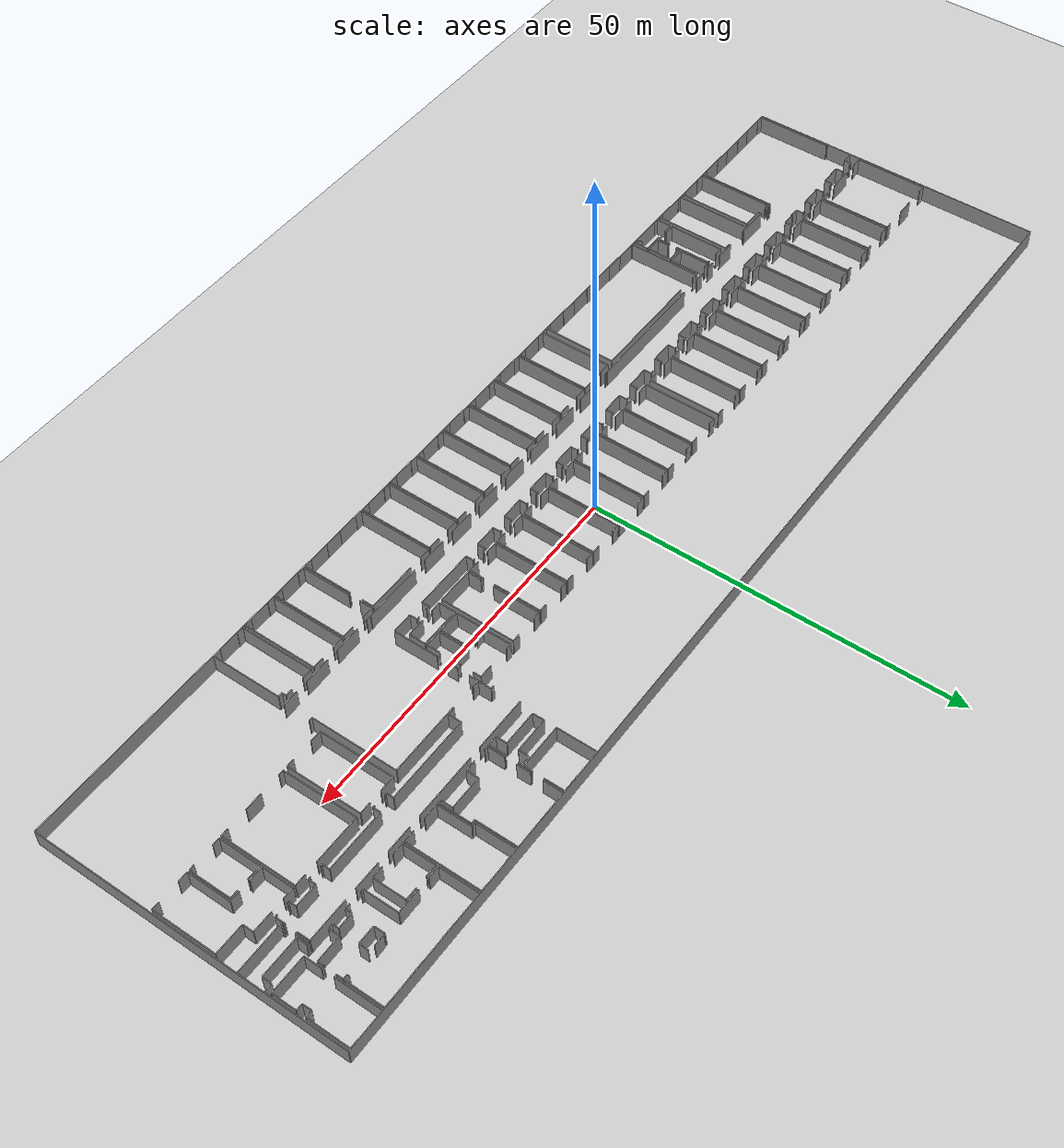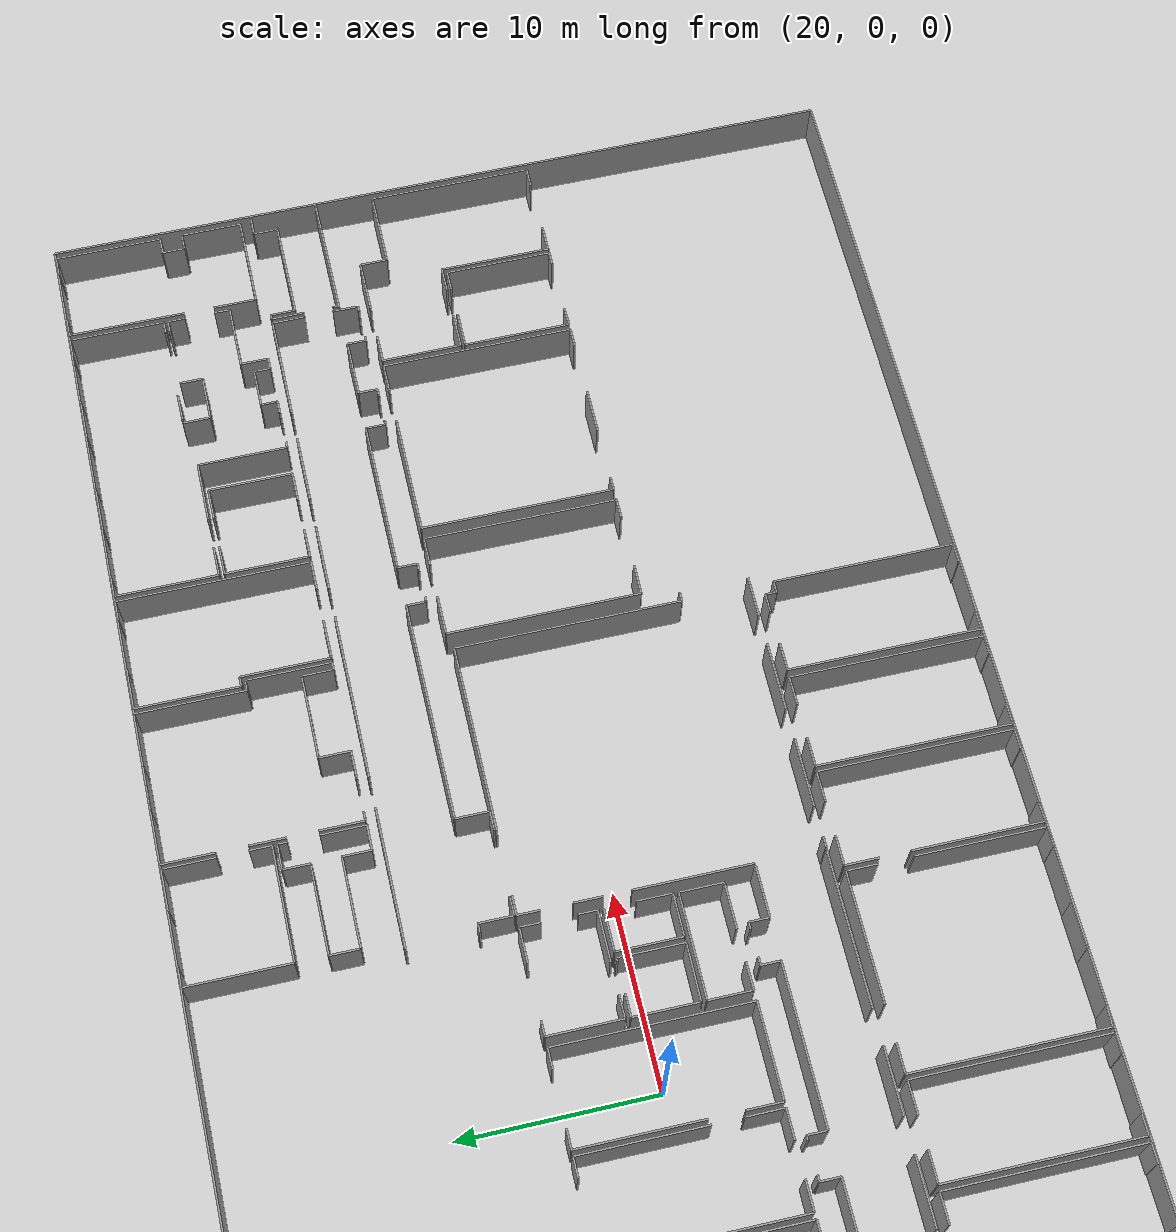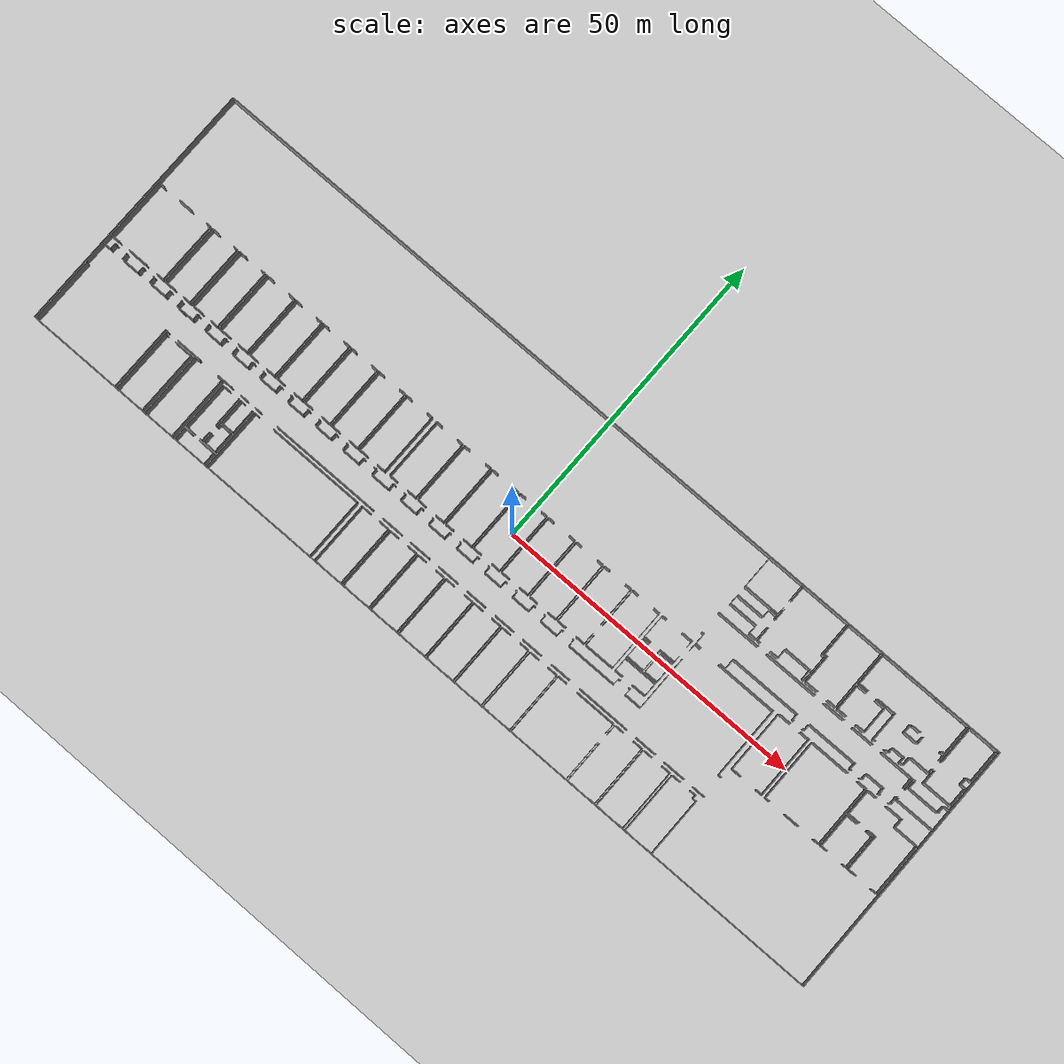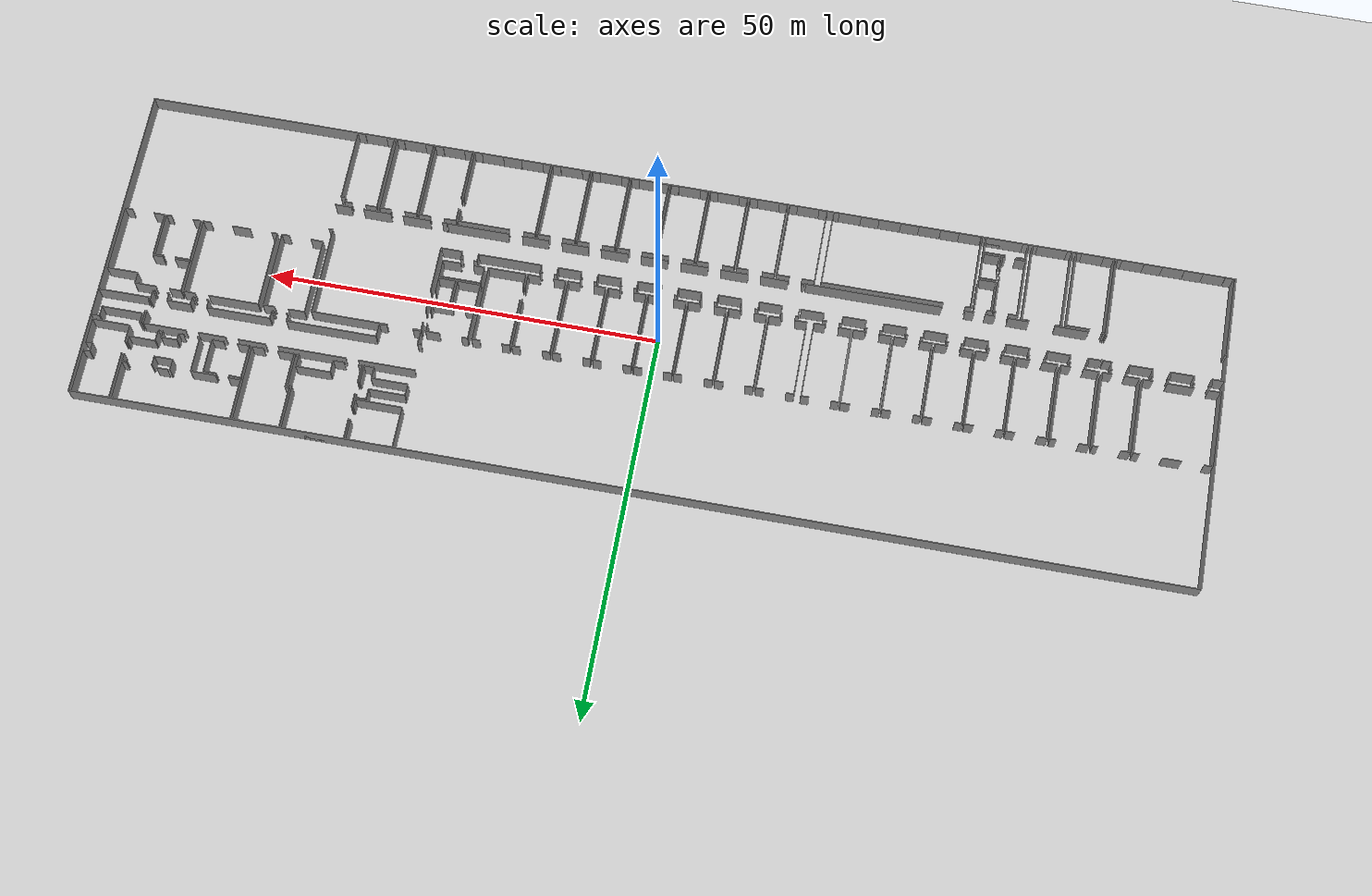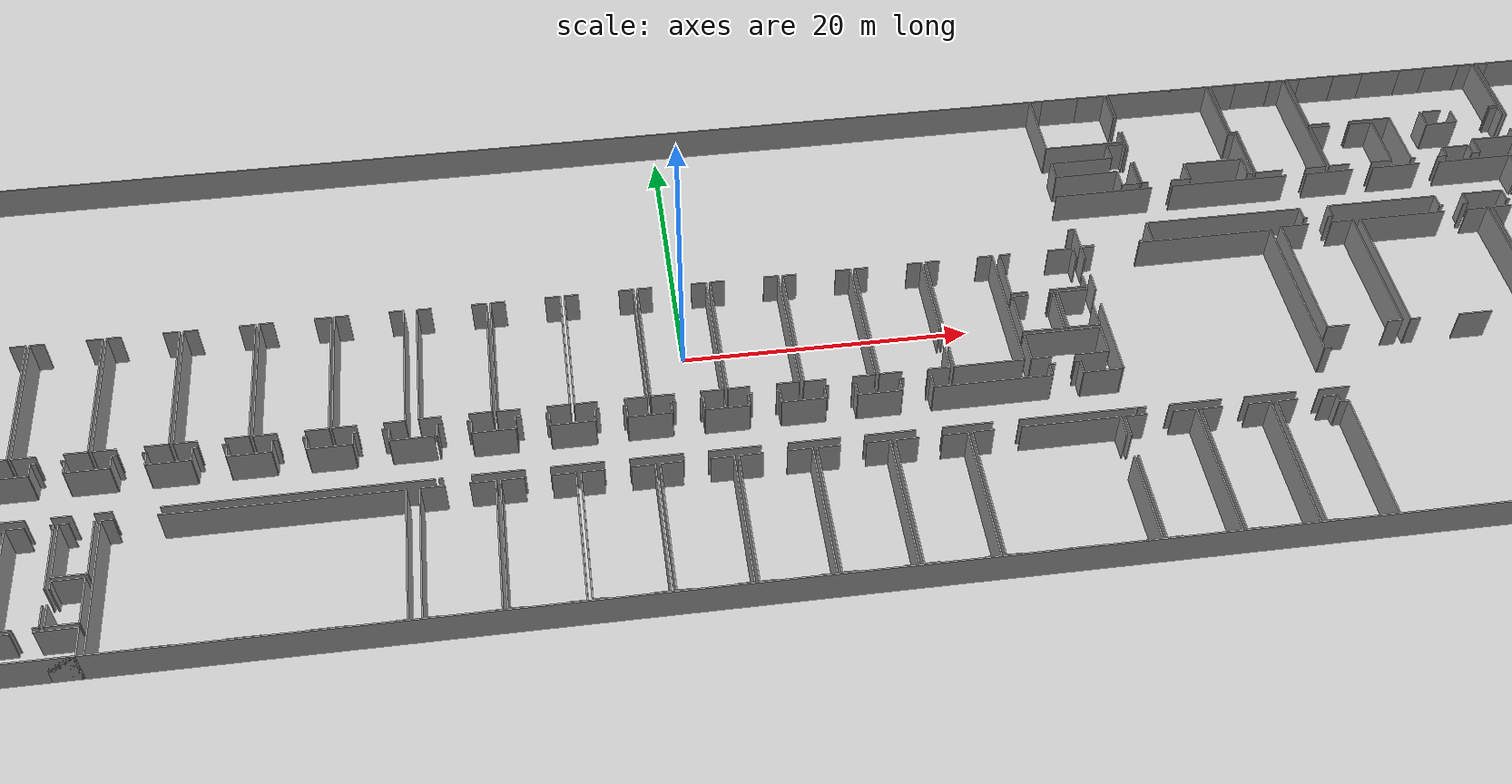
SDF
<sdf version="1.6">
  <world name="default">
    <light name="sun" type="directional">
      <cast_shadows>1</cast_shadows>
      <pose frame="">0 0 10 0 -0 0</pose>
      <diffuse>0.8 0.8 0.8 1</diffuse>
      <specular>0.1 0.1 0.1 1</specular>
      <attenuation>
        <range>1000</range>
        <constant>0.9</constant>
        <linear>0.01</linear>
        <quadratic>0.001</quadratic>
      </attenuation>
      <direction>-0.5 0.5 -1</direction>
    </light>
    <model name="ground_plane">
      <static>1</static>
      <link name="link">
        <collision name="collision">
          <geometry>
            <plane>
              <normal>0 0 1</normal>
              <size>100 100</size>
            </plane>
          </geometry>
          <surface>
            <friction>
              <ode>
                <mu>100</mu>
                <mu2>50</mu2>
              </ode>
              <torsional>
                <ode />
              </torsional>
            </friction>
            <contact>
              <ode />
            </contact>
            <bounce />
          </surface>
          <max_contacts>10</max_contacts>
        </collision>
        <visual name="visual">
          <cast_shadows>0</cast_shadows>
          <geometry>
            <plane>
              <normal>0 0 1</normal>
              <size>100 100</size>
            </plane>
          </geometry>
          <material>
            <script>
              <uri>file://media/materials/scripts/gazebo.material</uri>
              <name>Gazebo/Grey</name>
            </script>
          </material>
        </visual>
        <self_collide>0</self_collide>
        <kinematic>0</kinematic>
        <gravity>1</gravity>
      </link>
    </model>
    <gravity>0 0 -9.8</gravity>
    <magnetic_field>6e-06 2.3e-05 -4.2e-05</magnetic_field>
    <atmosphere type="adiabatic" />
    <physics default="0" name="default_physics" type="ode">
      <max_step_size>0.001</max_step_size>
      <real_time_factor>1</real_time_factor>
      <real_time_update_rate>1000</real_time_update_rate>
    </physics>
    <scene>
      <ambient>0.4 0.4 0.4 1</ambient>
      <background>0.7 0.7 0.7 1</background>
      <shadows>1</shadows>
    </scene>
    <spherical_coordinates>
      <surface_model>EARTH_WGS84</surface_model>
      <latitude_deg>0</latitude_deg>
      <longitude_deg>0</longitude_deg>
      <elevation>0</elevation>
      <heading_deg>0</heading_deg>
    </spherical_coordinates>
  <model name="50055640">
		<static>1</static>
		<link name="Wall_0">
			<collision name="Wall_0_Collision">
				<geometry>
					<box>
						<size>10.0309660389 0.1 2.5</size>
					</box>
				</geometry>
				<pose frame="">5.01548301944 0 1.25 0 0 0</pose>
			</collision>
			<visual name="Wall_0_Visual">
				<pose frame="">5.01548301944 0 1.25 0 0 0</pose>
				<geometry>
					<box>
						<size>10.0309660389 0.1 2.5</size>
					</box>
				</geometry>
				<material>
					<script>
						<uri>file://media/materials/scripts/gazebo.material</uri>
						<name>Gazebo/Grey</name>
					</script>
					<ambient>1 1 1 1</ambient>
				</material>
			</visual>
			<pose frame="">0.271460480227 -26.0134270775 0 0 0 1.57079632679</pose>
		</link>
		<link name="Wall_1">
			<collision name="Wall_1_Collision">
				<geometry>
					<box>
						<size>1.05398751206 0.1 2.5</size>
					</box>
				</geometry>
				<pose frame="">0.526993756028 0 1.25 0 0 0</pose>
			</collision>
			<visual name="Wall_1_Visual">
				<pose frame="">0.526993756028 0 1.25 0 0 0</pose>
				<geometry>
					<box>
						<size>1.05398751206 0.1 2.5</size>
					</box>
				</geometry>
				<material>
					<script>
						<uri>file://media/materials/scripts/gazebo.material</uri>
						<name>Gazebo/Grey</name>
					</script>
					<ambient>1 1 1 1</ambient>
				</material>
			</visual>
			<pose frame="">0.271460480227 -15.9824610386 0 0 0 0.0</pose>
		</link>
		<link name="Wall_2">
			<collision name="Wall_2_Collision">
				<geometry>
					<box>
						<size>2.38578100411 0.1 2.5</size>
					</box>
				</geometry>
				<pose frame="">1.19289050206 0 1.25 0 0 0</pose>
			</collision>
			<visual name="Wall_2_Visual">
				<pose frame="">1.19289050206 0 1.25 0 0 0</pose>
				<geometry>
					<box>
						<size>2.38578100411 0.1 2.5</size>
					</box>
				</geometry>
				<material>
					<script>
						<uri>file://media/materials/scripts/gazebo.material</uri>
						<name>Gazebo/Grey</name>
					</script>
					<ambient>1 1 1 1</ambient>
				</material>
			</visual>
			<pose frame="">4.07939489314 -15.9824610386 0 0 0 0.0</pose>
		</link>
		<link name="Wall_3">
			<collision name="Wall_3_Collision">
				<geometry>
					<box>
						<size>0.790903091527 0.1 2.5</size>
					</box>
				</geometry>
				<pose frame="">0.395451545764 0 1.25 0 0 0</pose>
			</collision>
			<visual name="Wall_3_Visual">
				<pose frame="">0.395451545764 0 1.25 0 0 0</pose>
				<geometry>
					<box>
						<size>0.790903091527 0.1 2.5</size>
					</box>
				</geometry>
				<material>
					<script>
						<uri>file://media/materials/scripts/gazebo.material</uri>
						<name>Gazebo/Grey</name>
					</script>
					<ambient>1 1 1 1</ambient>
				</material>
			</visual>
			<pose frame="">9.24425097721 -15.9824610386 0 0 0 0.0</pose>
		</link>
		<link name="Wall_4">
			<collision name="Wall_4_Collision">
				<geometry>
					<box>
						<size>9.98235951064 0.1 2.5</size>
					</box>
				</geometry>
				<pose frame="">4.99117975532 0 1.25 0 0 0</pose>
			</collision>
			<visual name="Wall_4_Visual">
				<pose frame="">4.99117975532 0 1.25 0 0 0</pose>
				<geometry>
					<box>
						<size>9.98235951064 0.1 2.5</size>
					</box>
				</geometry>
				<material>
					<script>
						<uri>file://media/materials/scripts/gazebo.material</uri>
						<name>Gazebo/Grey</name>
					</script>
					<ambient>1 1 1 1</ambient>
				</material>
			</visual>
			<pose frame="">10.0351540687 -15.9824610386 0 0 0 -1.57079632679</pose>
		</link>
		<link name="Wall_5">
			<collision name="Wall_5_Collision">
				<geometry>
					<box>
						<size>1.28458297376 0.1 2.5</size>
					</box>
				</geometry>
				<pose frame="">0.642291486878 0 1.25 0 0 0</pose>
			</collision>
			<visual name="Wall_5_Visual">
				<pose frame="">0.642291486878 0 1.25 0 0 0</pose>
				<geometry>
					<box>
						<size>1.28458297376 0.1 2.5</size>
					</box>
				</geometry>
				<material>
					<script>
						<uri>file://media/materials/scripts/gazebo.material</uri>
						<name>Gazebo/Grey</name>
					</script>
					<ambient>1 1 1 1</ambient>
				</material>
			</visual>
			<pose frame="">10.0351540687 -25.9648205493 0 0 0 3.14159265359</pose>
		</link>
		<link name="Wall_6">
			<collision name="Wall_6_Collision">
				<geometry>
					<box>
						<size>3.36692217879 0.1 2.5</size>
					</box>
				</geometry>
				<pose frame="">1.6834610894 0 1.25 0 0 0</pose>
			</collision>
			<visual name="Wall_6_Visual">
				<pose frame="">1.6834610894 0 1.25 0 0 0</pose>
				<geometry>
					<box>
						<size>3.36692217879 0.1 2.5</size>
					</box>
				</geometry>
				<material>
					<script>
						<uri>file://media/materials/scripts/gazebo.material</uri>
						<name>Gazebo/Grey</name>
					</script>
					<ambient>1 1 1 1</ambient>
				</material>
			</visual>
			<pose frame="">6.94413422001 -25.9648205493 0 0 0 3.14159265359</pose>
		</link>
		<link name="Wall_7">
			<collision name="Wall_7_Collision">
				<geometry>
					<box>
						<size>1.53308201614 0.1 2.5</size>
					</box>
				</geometry>
				<pose frame="">0.766541008072 0 1.25 0 0 0</pose>
			</collision>
			<visual name="Wall_7_Visual">
				<pose frame="">0.766541008072 0 1.25 0 0 0</pose>
				<geometry>
					<box>
						<size>1.53308201614 0.1 2.5</size>
					</box>
				</geometry>
				<material>
					<script>
						<uri>file://media/materials/scripts/gazebo.material</uri>
						<name>Gazebo/Grey</name>
					</script>
					<ambient>1 1 1 1</ambient>
				</material>
			</visual>
			<pose frame="">1.80377176506 -25.9648205493 0 0 0 -3.10988223318</pose>
		</link>
		<link name="Wall_8">
			<collision name="Wall_8_Collision">
				<geometry>
					<box>
						<size>10.5525661201 0.1 2.5</size>
					</box>
				</geometry>
				<pose frame="">5.27628306005 0 1.25 0 0 0</pose>
			</collision>
			<visual name="Wall_8_Visual">
				<pose frame="">5.27628306005 0 1.25 0 0 0</pose>
				<geometry>
					<box>
						<size>10.5525661201 0.1 2.5</size>
					</box>
				</geometry>
				<material>
					<script>
						<uri>file://media/materials/scripts/gazebo.material</uri>
						<name>Gazebo/Grey</name>
					</script>
					<ambient>1 1 1 1</ambient>
				</material>
			</visual>
			<pose frame="">0.282628559825 -41.7143509823 0 0 0 1.57079632679</pose>
		</link>
		<link name="Wall_9">
			<collision name="Wall_9_Collision">
				<geometry>
					<box>
						<size>0.282628559825 0.1 2.5</size>
					</box>
				</geometry>
				<pose frame="">0.141314279913 0 1.25 0 0 0</pose>
			</collision>
			<visual name="Wall_9_Visual">
				<pose frame="">0.141314279913 0 1.25 0 0 0</pose>
				<geometry>
					<box>
						<size>0.282628559825 0.1 2.5</size>
					</box>
				</geometry>
				<material>
					<script>
						<uri>file://media/materials/scripts/gazebo.material</uri>
						<name>Gazebo/Grey</name>
					</script>
					<ambient>1 1 1 1</ambient>
				</material>
			</visual>
			<pose frame="">0.282628559825 -31.1617848622 0 0 0 3.14159265359</pose>
		</link>
		<link name="Wall_10">
			<collision name="Wall_10_Collision">
				<geometry>
					<box>
						<size>1.54766739428 0.1 2.5</size>
					</box>
				</geometry>
				<pose frame="">0.773833697142 0 1.25 0 0 0</pose>
			</collision>
			<visual name="Wall_10_Visual">
				<pose frame="">0.773833697142 0 1.25 0 0 0</pose>
				<geometry>
					<box>
						<size>1.54766739428 0.1 2.5</size>
					</box>
				</geometry>
				<material>
					<script>
						<uri>file://media/materials/scripts/gazebo.material</uri>
						<name>Gazebo/Grey</name>
					</script>
					<ambient>1 1 1 1</ambient>
				</material>
			</visual>
			<pose frame="">0.0 -27.5467536423 0 0 0 0.0</pose>
		</link>
		<link name="Wall_11">
			<collision name="Wall_11_Collision">
				<geometry>
					<box>
						<size>0.989517234377 0.1 2.5</size>
					</box>
				</geometry>
				<pose frame="">0.494758617189 0 1.25 0 0 0</pose>
			</collision>
			<visual name="Wall_11_Visual">
				<pose frame="">0.494758617189 0 1.25 0 0 0</pose>
				<geometry>
					<box>
						<size>0.989517234377 0.1 2.5</size>
					</box>
				</geometry>
				<material>
					<script>
						<uri>file://media/materials/scripts/gazebo.material</uri>
						<name>Gazebo/Grey</name>
					</script>
					<ambient>1 1 1 1</ambient>
				</material>
			</visual>
			<pose frame="">1.54766739428 -27.5467536423 0 0 0 1.57079632679</pose>
		</link>
		<link name="Wall_12">
			<collision name="Wall_12_Collision">
				<geometry>
					<box>
						<size>0.275775420072 0.1 2.5</size>
					</box>
				</geometry>
				<pose frame="">0.137887710036 0 1.25 0 0 0</pose>
			</collision>
			<visual name="Wall_12_Visual">
				<pose frame="">0.137887710036 0 1.25 0 0 0</pose>
				<geometry>
					<box>
						<size>0.275775420072 0.1 2.5</size>
					</box>
				</geometry>
				<material>
					<script>
						<uri>file://media/materials/scripts/gazebo.material</uri>
						<name>Gazebo/Grey</name>
					</script>
					<ambient>1 1 1 1</ambient>
				</material>
			</visual>
			<pose frame="">1.54766739428 -26.5572364079 0 0 0 0.0</pose>
		</link>
		<link name="Wall_13">
			<collision name="Wall_13_Collision">
				<geometry>
					<box>
						<size>0.190999543124 0.1 2.5</size>
					</box>
				</geometry>
				<pose frame="">0.095499771562 0 1.25 0 0 0</pose>
			</collision>
			<visual name="Wall_13_Visual">
				<pose frame="">0.095499771562 0 1.25 0 0 0</pose>
				<geometry>
					<box>
						<size>0.190999543124 0.1 2.5</size>
					</box>
				</geometry>
				<material>
					<script>
						<uri>file://media/materials/scripts/gazebo.material</uri>
						<name>Gazebo/Grey</name>
					</script>
					<ambient>1 1 1 1</ambient>
				</material>
			</visual>
			<pose frame="">3.55462206203 -26.5572364079 0 0 0 0.0</pose>
		</link>
		<link name="Wall_14">
			<collision name="Wall_14_Collision">
				<geometry>
					<box>
						<size>0.996370374131 0.1 2.5</size>
					</box>
				</geometry>
				<pose frame="">0.498185187065 0 1.25 0 0 0</pose>
			</collision>
			<visual name="Wall_14_Visual">
				<pose frame="">0.498185187065 0 1.25 0 0 0</pose>
				<geometry>
					<box>
						<size>0.996370374131 0.1 2.5</size>
					</box>
				</geometry>
				<material>
					<script>
						<uri>file://media/materials/scripts/gazebo.material</uri>
						<name>Gazebo/Grey</name>
					</script>
					<ambient>1 1 1 1</ambient>
				</material>
			</visual>
			<pose frame="">3.74562160516 -26.5572364079 0 0 0 -1.57079632679</pose>
		</link>
		<link name="Wall_15">
			<collision name="Wall_15_Collision">
				<geometry>
					<box>
						<size>2.97895832276 0.1 2.5</size>
					</box>
				</geometry>
				<pose frame="">1.48947916138 0 1.25 0 0 0</pose>
			</collision>
			<visual name="Wall_15_Visual">
				<pose frame="">1.48947916138 0 1.25 0 0 0</pose>
				<geometry>
					<box>
						<size>2.97895832276 0.1 2.5</size>
					</box>
				</geometry>
				<material>
					<script>
						<uri>file://media/materials/scripts/gazebo.material</uri>
						<name>Gazebo/Grey</name>
					</script>
					<ambient>1 1 1 1</ambient>
				</material>
			</visual>
			<pose frame="">3.74562160516 -27.5536067821 0 0 0 0.0</pose>
		</link>
		<link name="Wall_16">
			<collision name="Wall_16_Collision">
				<geometry>
					<box>
						<size>0.999289304026 0.1 2.5</size>
					</box>
				</geometry>
				<pose frame="">0.499644652013 0 1.25 0 0 0</pose>
			</collision>
			<visual name="Wall_16_Visual">
				<pose frame="">0.499644652013 0 1.25 0 0 0</pose>
				<geometry>
					<box>
						<size>0.999289304026 0.1 2.5</size>
					</box>
				</geometry>
				<material>
					<script>
						<uri>file://media/materials/scripts/gazebo.material</uri>
						<name>Gazebo/Grey</name>
					</script>
					<ambient>1 1 1 1</ambient>
				</material>
			</visual>
			<pose frame="">6.72457992792 -27.5536067821 0 0 0 1.57079632679</pose>
		</link>
		<link name="Wall_17">
			<collision name="Wall_17_Collision">
				<geometry>
					<box>
						<size>0.232879841616 0.1 2.5</size>
					</box>
				</geometry>
				<pose frame="">0.116439920808 0 1.25 0 0 0</pose>
			</collision>
			<visual name="Wall_17_Visual">
				<pose frame="">0.116439920808 0 1.25 0 0 0</pose>
				<geometry>
					<box>
						<size>0.232879841616 0.1 2.5</size>
					</box>
				</geometry>
				<material>
					<script>
						<uri>file://media/materials/scripts/gazebo.material</uri>
						<name>Gazebo/Grey</name>
					</script>
					<ambient>1 1 1 1</ambient>
				</material>
			</visual>
			<pose frame="">6.72457992792 -26.554317478 0 0 0 0.0</pose>
		</link>
		<link name="Wall_18">
			<collision name="Wall_18_Collision">
				<geometry>
					<box>
						<size>0.164094624093 0.1 2.5</size>
					</box>
				</geometry>
				<pose frame="">0.0820473120463 0 1.25 0 0 0</pose>
			</collision>
			<visual name="Wall_18_Visual">
				<pose frame="">0.0820473120463 0 1.25 0 0 0</pose>
				<geometry>
					<box>
						<size>0.164094624093 0.1 2.5</size>
					</box>
				</geometry>
				<material>
					<script>
						<uri>file://media/materials/scripts/gazebo.material</uri>
						<name>Gazebo/Grey</name>
					</script>
					<ambient>1 1 1 1</ambient>
				</material>
			</visual>
			<pose frame="">8.73788009544 -26.554317478 0 0 0 0.0</pose>
		</link>
		<link name="Wall_19">
			<collision name="Wall_19_Collision">
				<geometry>
					<box>
						<size>0.981648814661 0.1 2.5</size>
					</box>
				</geometry>
				<pose frame="">0.49082440733 0 1.25 0 0 0</pose>
			</collision>
			<visual name="Wall_19_Visual">
				<pose frame="">0.49082440733 0 1.25 0 0 0</pose>
				<geometry>
					<box>
						<size>0.981648814661 0.1 2.5</size>
					</box>
				</geometry>
				<material>
					<script>
						<uri>file://media/materials/scripts/gazebo.material</uri>
						<name>Gazebo/Grey</name>
					</script>
					<ambient>1 1 1 1</ambient>
				</material>
			</visual>
			<pose frame="">8.90197471953 -26.554317478 0 0 0 -1.57079632679</pose>
		</link>
		<link name="Wall_20">
			<collision name="Wall_20_Collision">
				<geometry>
					<box>
						<size>2.96055637342 0.1 2.5</size>
					</box>
				</geometry>
				<pose frame="">1.48027818671 0 1.25 0 0 0</pose>
			</collision>
			<visual name="Wall_20_Visual">
				<pose frame="">1.48027818671 0 1.25 0 0 0</pose>
				<geometry>
					<box>
						<size>2.96055637342 0.1 2.5</size>
					</box>
				</geometry>
				<material>
					<script>
						<uri>file://media/materials/scripts/gazebo.material</uri>
						<name>Gazebo/Grey</name>
					</script>
					<ambient>1 1 1 1</ambient>
				</material>
			</visual>
			<pose frame="">8.90197471953 -27.5359662927 0 0 0 0.0</pose>
		</link>
		<link name="Wall_21">
			<collision name="Wall_21_Collision">
				<geometry>
					<box>
						<size>0.998020204071 0.1 2.5</size>
					</box>
				</geometry>
				<pose frame="">0.499010102036 0 1.25 0 0 0</pose>
			</collision>
			<visual name="Wall_21_Visual">
				<pose frame="">0.499010102036 0 1.25 0 0 0</pose>
				<geometry>
					<box>
						<size>0.998020204071 0.1 2.5</size>
					</box>
				</geometry>
				<material>
					<script>
						<uri>file://media/materials/scripts/gazebo.material</uri>
						<name>Gazebo/Grey</name>
					</script>
					<ambient>1 1 1 1</ambient>
				</material>
			</visual>
			<pose frame="">11.8625310929 -27.5359662927 0 0 0 1.57079632679</pose>
		</link>
		<link name="Wall_22">
			<collision name="Wall_22_Collision">
				<geometry>
					<box>
						<size>0.268922280319 0.1 2.5</size>
					</box>
				</geometry>
				<pose frame="">0.134461140159 0 1.25 0 0 0</pose>
			</collision>
			<visual name="Wall_22_Visual">
				<pose frame="">0.134461140159 0 1.25 0 0 0</pose>
				<geometry>
					<box>
						<size>0.268922280319 0.1 2.5</size>
					</box>
				</geometry>
				<material>
					<script>
						<uri>file://media/materials/scripts/gazebo.material</uri>
						<name>Gazebo/Grey</name>
					</script>
					<ambient>1 1 1 1</ambient>
				</material>
			</visual>
			<pose frame="">11.8625310929 -26.5379460886 0 0 0 0.0</pose>
		</link>
		<link name="Wall_23">
			<collision name="Wall_23_Collision">
				<geometry>
					<box>
						<size>0.192014823087 0.1 2.5</size>
					</box>
				</geometry>
				<pose frame="">0.0960074115437 0 1.25 0 0 0</pose>
			</collision>
			<visual name="Wall_23_Visual">
				<pose frame="">0.0960074115437 0 1.25 0 0 0</pose>
				<geometry>
					<box>
						<size>0.192014823087 0.1 2.5</size>
					</box>
				</geometry>
				<material>
					<script>
						<uri>file://media/materials/scripts/gazebo.material</uri>
						<name>Gazebo/Grey</name>
					</script>
					<ambient>1 1 1 1</ambient>
				</material>
			</visual>
			<pose frame="">13.8758312605 -26.5379460886 0 0 0 0.0</pose>
		</link>
		<link name="Wall_24">
			<collision name="Wall_24_Collision">
				<geometry>
					<box>
						<size>1.02403675313 0.1 2.5</size>
					</box>
				</geometry>
				<pose frame="">0.512018376567 0 1.25 0 0 0</pose>
			</collision>
			<visual name="Wall_24_Visual">
				<pose frame="">0.512018376567 0 1.25 0 0 0</pose>
				<geometry>
					<box>
						<size>1.02403675313 0.1 2.5</size>
					</box>
				</geometry>
				<material>
					<script>
						<uri>file://media/materials/scripts/gazebo.material</uri>
						<name>Gazebo/Grey</name>
					</script>
					<ambient>1 1 1 1</ambient>
				</material>
			</visual>
			<pose frame="">14.0678460836 -26.5379460886 0 0 0 -1.57079632679</pose>
		</link>
		<link name="Wall_25">
			<collision name="Wall_25_Collision">
				<geometry>
					<box>
						<size>1.04662673232 0.1 2.5</size>
					</box>
				</geometry>
				<pose frame="">0.523313366161 0 1.25 0 0 0</pose>
			</collision>
			<visual name="Wall_25_Visual">
				<pose frame="">0.523313366161 0 1.25 0 0 0</pose>
				<geometry>
					<box>
						<size>1.04662673232 0.1 2.5</size>
					</box>
				</geometry>
				<material>
					<script>
						<uri>file://media/materials/scripts/gazebo.material</uri>
						<name>Gazebo/Grey</name>
					</script>
					<ambient>1 1 1 1</ambient>
				</material>
			</visual>
			<pose frame="">14.0678460836 -27.5619828418 0 0 0 0.0</pose>
		</link>
		<link name="Wall_26">
			<collision name="Wall_26_Collision">
				<geometry>
					<box>
						<size>0.124117975532 0.1 2.5</size>
					</box>
				</geometry>
				<pose frame="">0.0620589877659 0 1.25 0 0 0</pose>
			</collision>
			<visual name="Wall_26_Visual">
				<pose frame="">0.0620589877659 0 1.25 0 0 0</pose>
				<geometry>
					<box>
						<size>0.124117975532 0.1 2.5</size>
					</box>
				</geometry>
				<material>
					<script>
						<uri>file://media/materials/scripts/gazebo.material</uri>
						<name>Gazebo/Grey</name>
					</script>
					<ambient>1 1 1 1</ambient>
				</material>
			</visual>
			<pose frame="">15.1144728159 -27.5619828418 0 0 0 -1.57079632679</pose>
		</link>
		<link name="Wall_27">
			<collision name="Wall_27_Collision">
				<geometry>
					<box>
						<size>10.7143763643 0.1 2.5</size>
					</box>
				</geometry>
				<pose frame="">5.35718818214 0 1.25 0 0 0</pose>
			</collision>
			<visual name="Wall_27_Visual">
				<pose frame="">5.35718818214 0 1.25 0 0 0</pose>
				<geometry>
					<box>
						<size>10.7143763643 0.1 2.5</size>
					</box>
				</geometry>
				<material>
					<script>
						<uri>file://media/materials/scripts/gazebo.material</uri>
						<name>Gazebo/Grey</name>
					</script>
					<ambient>1 1 1 1</ambient>
				</material>
			</visual>
			<pose frame="">15.1144728159 -31.0165998274 0 0 0 -1.57079632679</pose>
		</link>
		<link name="Wall_28">
			<collision name="Wall_28_Collision">
				<geometry>
					<box>
						<size>0.679476115539 0.1 2.5</size>
					</box>
				</geometry>
				<pose frame="">0.339738057769 0 1.25 0 0 0</pose>
			</collision>
			<visual name="Wall_28_Visual">
				<pose frame="">0.339738057769 0 1.25 0 0 0</pose>
				<geometry>
					<box>
						<size>0.679476115539 0.1 2.5</size>
					</box>
				</geometry>
				<material>
					<script>
						<uri>file://media/materials/scripts/gazebo.material</uri>
						<name>Gazebo/Grey</name>
					</script>
					<ambient>1 1 1 1</ambient>
				</material>
			</visual>
			<pose frame="">15.1144728159 -41.7309761917 0 0 0 3.14159265359</pose>
		</link>
		<link name="Wall_29">
			<collision name="Wall_29_Collision">
				<geometry>
					<box>
						<size>2.3472003655 0.1 2.5</size>
					</box>
				</geometry>
				<pose frame="">1.17360018275 0 1.25 0 0 0</pose>
			</collision>
			<visual name="Wall_29_Visual">
				<pose frame="">1.17360018275 0 1.25 0 0 0</pose>
				<geometry>
					<box>
						<size>2.3472003655 0.1 2.5</size>
					</box>
				</geometry>
				<material>
					<script>
						<uri>file://media/materials/scripts/gazebo.material</uri>
						<name>Gazebo/Grey</name>
					</script>
					<ambient>1 1 1 1</ambient>
				</material>
			</visual>
			<pose frame="">11.6214021016 -41.7309761917 0 0 0 3.14159265359</pose>
		</link>
		<link name="Wall_30">
			<collision name="Wall_30_Collision">
				<geometry>
					<box>
						<size>2.36610995482 0.1 2.5</size>
					</box>
				</geometry>
				<pose frame="">1.18305497741 0 1.25 0 0 0</pose>
			</collision>
			<visual name="Wall_30_Visual">
				<pose frame="">1.18305497741 0 1.25 0 0 0</pose>
				<geometry>
					<box>
						<size>2.36610995482 0.1 2.5</size>
					</box>
				</geometry>
				<material>
					<script>
						<uri>file://media/materials/scripts/gazebo.material</uri>
						<name>Gazebo/Grey</name>
					</script>
					<ambient>1 1 1 1</ambient>
				</material>
			</visual>
			<pose frame="">6.47900908676 -41.7309761917 0 0 0 3.14159265359</pose>
		</link>
		<link name="Wall_31">
			<collision name="Wall_31_Collision">
				<geometry>
					<box>
						<size>1.04155611589 0.1 2.5</size>
					</box>
				</geometry>
				<pose frame="">0.520778057943 0 1.25 0 0 0</pose>
			</collision>
			<visual name="Wall_31_Visual">
				<pose frame="">0.520778057943 0 1.25 0 0 0</pose>
				<geometry>
					<box>
						<size>1.04155611589 0.1 2.5</size>
					</box>
				</geometry>
				<material>
					<script>
						<uri>file://media/materials/scripts/gazebo.material</uri>
						<name>Gazebo/Grey</name>
					</script>
					<ambient>1 1 1 1</ambient>
				</material>
			</visual>
			<pose frame="">1.32405198233 -41.7309761917 0 0 0 3.12563008067</pose>
		</link>
		<link name="Wall_32">
			<collision name="Wall_32_Collision">
				<geometry>
					<box>
						<size>9.97322199096 0.1 2.5</size>
					</box>
				</geometry>
				<pose frame="">4.98661099548 0 1.25 0 0 0</pose>
			</collision>
			<visual name="Wall_32_Visual">
				<pose frame="">4.98661099548 0 1.25 0 0 0</pose>
				<geometry>
					<box>
						<size>9.97322199096 0.1 2.5</size>
					</box>
				</geometry>
				<material>
					<script>
						<uri>file://media/materials/scripts/gazebo.material</uri>
						<name>Gazebo/Grey</name>
					</script>
					<ambient>1 1 1 1</ambient>
				</material>
			</visual>
			<pose frame="">10.3866947561 -25.9782730088 0 0 0 1.57079632679</pose>
		</link>
		<link name="Wall_33">
			<collision name="Wall_33_Collision">
				<geometry>
					<box>
						<size>1.20970607645 0.1 2.5</size>
					</box>
				</geometry>
				<pose frame="">0.604853038225 0 1.25 0 0 0</pose>
			</collision>
			<visual name="Wall_33_Visual">
				<pose frame="">0.604853038225 0 1.25 0 0 0</pose>
				<geometry>
					<box>
						<size>1.20970607645 0.1 2.5</size>
					</box>
				</geometry>
				<material>
					<script>
						<uri>file://media/materials/scripts/gazebo.material</uri>
						<name>Gazebo/Grey</name>
					</script>
					<ambient>1 1 1 1</ambient>
				</material>
			</visual>
			<pose frame="">10.3866947561 -16.0050510178 0 0 0 0.0</pose>
		</link>
		<link name="Wall_34">
			<collision name="Wall_34_Collision">
				<geometry>
					<box>
						<size>0.668942585918 0.1 2.5</size>
					</box>
				</geometry>
				<pose frame="">0.334471292959 0 1.25 0 0 0</pose>
			</collision>
			<visual name="Wall_34_Visual">
				<pose frame="">0.334471292959 0 1.25 0 0 0</pose>
				<geometry>
					<box>
						<size>0.668942585918 0.1 2.5</size>
					</box>
				</geometry>
				<material>
					<script>
						<uri>file://media/materials/scripts/gazebo.material</uri>
						<name>Gazebo/Grey</name>
					</script>
					<ambient>1 1 1 1</ambient>
				</material>
			</visual>
			<pose frame="">14.3969237017 -16.0050510178 0 0 0 0.0</pose>
		</link>
		<link name="Wall_35">
			<collision name="Wall_35_Collision">
				<geometry>
					<box>
						<size>9.96611503122 0.1 2.5</size>
					</box>
				</geometry>
				<pose frame="">4.98305751561 0 1.25 0 0 0</pose>
			</collision>
			<visual name="Wall_35_Visual">
				<pose frame="">4.98305751561 0 1.25 0 0 0</pose>
				<geometry>
					<box>
						<size>9.96611503122 0.1 2.5</size>
					</box>
				</geometry>
				<material>
					<script>
						<uri>file://media/materials/scripts/gazebo.material</uri>
						<name>Gazebo/Grey</name>
					</script>
					<ambient>1 1 1 1</ambient>
				</material>
			</visual>
			<pose frame="">15.0658662876 -16.0050510178 0 0 0 -1.57079632679</pose>
		</link>
		<link name="Wall_36">
			<collision name="Wall_36_Collision">
				<geometry>
					<box>
						<size>1.24866744505 0.1 2.5</size>
					</box>
				</geometry>
				<pose frame="">0.624333722524 0 1.25 0 0 0</pose>
			</collision>
			<visual name="Wall_36_Visual">
				<pose frame="">0.624333722524 0 1.25 0 0 0</pose>
				<geometry>
					<box>
						<size>1.24866744505 0.1 2.5</size>
					</box>
				</geometry>
				<material>
					<script>
						<uri>file://media/materials/scripts/gazebo.material</uri>
						<name>Gazebo/Grey</name>
					</script>
					<ambient>1 1 1 1</ambient>
				</material>
			</visual>
			<pose frame="">15.0658662876 -25.971166049 0 0 0 3.14159265359</pose>
		</link>
		<link name="Wall_37">
			<collision name="Wall_37_Collision">
				<geometry>
					<box>
						<size>1.86203701582 0.1 2.5</size>
					</box>
				</geometry>
				<pose frame="">0.931018507909 0 1.25 0 0 0</pose>
			</collision>
			<visual name="Wall_37_Visual">
				<pose frame="">0.931018507909 0 1.25 0 0 0</pose>
				<geometry>
					<box>
						<size>1.86203701582 0.1 2.5</size>
					</box>
				</geometry>
				<material>
					<script>
						<uri>file://media/materials/scripts/gazebo.material</uri>
						<name>Gazebo/Grey</name>
					</script>
					<ambient>1 1 1 1</ambient>
				</material>
			</visual>
			<pose frame="">12.248718209 -25.971166049 0 0 0 -3.13777587823</pose>
		</link>
		<link name="Wall_38">
			<collision name="Wall_38_Collision">
				<geometry>
					<box>
						<size>0.126275445454 0.1 2.5</size>
					</box>
				</geometry>
				<pose frame="">0.063137722727 0 1.25 0 0 0</pose>
			</collision>
			<visual name="Wall_38_Visual">
				<pose frame="">0.063137722727 0 1.25 0 0 0</pose>
				<geometry>
					<box>
						<size>0.126275445454 0.1 2.5</size>
					</box>
				</geometry>
				<material>
					<script>
						<uri>file://media/materials/scripts/gazebo.material</uri>
						<name>Gazebo/Grey</name>
					</script>
					<ambient>1 1 1 1</ambient>
				</material>
			</visual>
			<pose frame="">15.3630894969 -31.1513782426 0 0 0 1.57079632679</pose>
		</link>
		<link name="Wall_39">
			<collision name="Wall_39_Collision">
				<geometry>
					<box>
						<size>0.157749124321 0.1 2.5</size>
					</box>
				</geometry>
				<pose frame="">0.0788745621605 0 1.25 0 0 0</pose>
			</collision>
			<visual name="Wall_39_Visual">
				<pose frame="">0.0788745621605 0 1.25 0 0 0</pose>
				<geometry>
					<box>
						<size>0.157749124321 0.1 2.5</size>
					</box>
				</geometry>
				<material>
					<script>
						<uri>file://media/materials/scripts/gazebo.material</uri>
						<name>Gazebo/Grey</name>
					</script>
					<ambient>1 1 1 1</ambient>
				</material>
			</visual>
			<pose frame="">15.3630894969 -27.693715417 0 0 0 1.57079632679</pose>
		</link>
		<link name="Wall_40">
			<collision name="Wall_40_Collision">
				<geometry>
					<box>
						<size>1.64678410072 0.1 2.5</size>
					</box>
				</geometry>
				<pose frame="">0.823392050358 0 1.25 0 0 0</pose>
			</collision>
			<visual name="Wall_40_Visual">
				<pose frame="">0.823392050358 0 1.25 0 0 0</pose>
				<geometry>
					<box>
						<size>1.64678410072 0.1 2.5</size>
					</box>
				</geometry>
				<material>
					<script>
						<uri>file://media/materials/scripts/gazebo.material</uri>
						<name>Gazebo/Grey</name>
					</script>
					<ambient>1 1 1 1</ambient>
				</material>
			</visual>
			<pose frame="">15.3630894969 -27.5359662927 0 0 0 0.0</pose>
		</link>
		<link name="Wall_41">
			<collision name="Wall_41_Collision">
				<geometry>
					<box>
						<size>1.00956901366 0.1 2.5</size>
					</box>
				</geometry>
				<pose frame="">0.504784506828 0 1.25 0 0 0</pose>
			</collision>
			<visual name="Wall_41_Visual">
				<pose frame="">0.504784506828 0 1.25 0 0 0</pose>
				<geometry>
					<box>
						<size>1.00956901366 0.1 2.5</size>
					</box>
				</geometry>
				<material>
					<script>
						<uri>file://media/materials/scripts/gazebo.material</uri>
						<name>Gazebo/Grey</name>
					</script>
					<ambient>1 1 1 1</ambient>
				</material>
			</visual>
			<pose frame="">17.0098735976 -27.5359662927 0 0 0 1.57079632679</pose>
		</link>
		<link name="Wall_42">
			<collision name="Wall_42_Collision">
				<geometry>
					<box>
						<size>0.277679070004 0.1 2.5</size>
					</box>
				</geometry>
				<pose frame="">0.138839535002 0 1.25 0 0 0</pose>
			</collision>
			<visual name="Wall_42_Visual">
				<pose frame="">0.138839535002 0 1.25 0 0 0</pose>
				<geometry>
					<box>
						<size>0.277679070004 0.1 2.5</size>
					</box>
				</geometry>
				<material>
					<script>
						<uri>file://media/materials/scripts/gazebo.material</uri>
						<name>Gazebo/Grey</name>
					</script>
					<ambient>1 1 1 1</ambient>
				</material>
			</visual>
			<pose frame="">17.0098735976 -26.526397279 0 0 0 0.0</pose>
		</link>
		<link name="Wall_43">
			<collision name="Wall_43_Collision">
				<geometry>
					<box>
						<size>0.176531803645 0.1 2.5</size>
					</box>
				</geometry>
				<pose frame="">0.0882659018224 0 1.25 0 0 0</pose>
			</collision>
			<visual name="Wall_43_Visual">
				<pose frame="">0.0882659018224 0 1.25 0 0 0</pose>
				<geometry>
					<box>
						<size>0.176531803645 0.1 2.5</size>
					</box>
				</geometry>
				<material>
					<script>
						<uri>file://media/materials/scripts/gazebo.material</uri>
						<name>Gazebo/Grey</name>
					</script>
					<ambient>1 1 1 1</ambient>
				</material>
			</visual>
			<pose frame="">19.0486826742 -26.526397279 0 0 0 0.0</pose>
		</link>
		<link name="Wall_44">
			<collision name="Wall_44_Collision">
				<geometry>
					<box>
						<size>1.00766536372 0.1 2.5</size>
					</box>
				</geometry>
				<pose frame="">0.503832681862 0 1.25 0 0 0</pose>
			</collision>
			<visual name="Wall_44_Visual">
				<pose frame="">0.503832681862 0 1.25 0 0 0</pose>
				<geometry>
					<box>
						<size>1.00766536372 0.1 2.5</size>
					</box>
				</geometry>
				<material>
					<script>
						<uri>file://media/materials/scripts/gazebo.material</uri>
						<name>Gazebo/Grey</name>
					</script>
					<ambient>1 1 1 1</ambient>
				</material>
			</visual>
			<pose frame="">19.2252144779 -26.526397279 0 0 0 -1.57079632679</pose>
		</link>
		<link name="Wall_45">
			<collision name="Wall_45_Collision">
				<geometry>
					<box>
						<size>2.93555510432 0.1 2.5</size>
					</box>
				</geometry>
				<pose frame="">1.46777755216 0 1.25 0 0 0</pose>
			</collision>
			<visual name="Wall_45_Visual">
				<pose frame="">1.46777755216 0 1.25 0 0 0</pose>
				<geometry>
					<box>
						<size>2.93555510432 0.1 2.5</size>
					</box>
				</geometry>
				<material>
					<script>
						<uri>file://media/materials/scripts/gazebo.material</uri>
						<name>Gazebo/Grey</name>
					</script>
					<ambient>1 1 1 1</ambient>
				</material>
			</visual>
			<pose frame="">19.2252144779 -27.5340626428 0 0 0 0.0</pose>
		</link>
		<link name="Wall_46">
			<collision name="Wall_46_Collision">
				<geometry>
					<box>
						<size>1.00677699376 0.1 2.5</size>
					</box>
				</geometry>
				<pose frame="">0.503388496878 0 1.25 0 0 0</pose>
			</collision>
			<visual name="Wall_46_Visual">
				<pose frame="">0.503388496878 0 1.25 0 0 0</pose>
				<geometry>
					<box>
						<size>1.00677699376 0.1 2.5</size>
					</box>
				</geometry>
				<material>
					<script>
						<uri>file://media/materials/scripts/gazebo.material</uri>
						<name>Gazebo/Grey</name>
					</script>
					<ambient>1 1 1 1</ambient>
				</material>
			</visual>
			<pose frame="">22.1607695822 -27.5340626428 0 0 0 1.57079632679</pose>
		</link>
		<link name="Wall_47">
			<collision name="Wall_47_Collision">
				<geometry>
					<box>
						<size>0.268287730342 0.1 2.5</size>
					</box>
				</geometry>
				<pose frame="">0.134143865171 0 1.25 0 0 0</pose>
			</collision>
			<visual name="Wall_47_Visual">
				<pose frame="">0.134143865171 0 1.25 0 0 0</pose>
				<geometry>
					<box>
						<size>0.268287730342 0.1 2.5</size>
					</box>
				</geometry>
				<material>
					<script>
						<uri>file://media/materials/scripts/gazebo.material</uri>
						<name>Gazebo/Grey</name>
					</script>
					<ambient>1 1 1 1</ambient>
				</material>
			</visual>
			<pose frame="">22.1607695822 -26.527285649 0 0 0 0.0</pose>
		</link>
		<link name="Wall_48">
			<collision name="Wall_48_Collision">
				<geometry>
					<box>
						<size>0.1722168638 0.1 2.5</size>
					</box>
				</geometry>
				<pose frame="">0.0861084319001 0 1.25 0 0 0</pose>
			</collision>
			<visual name="Wall_48_Visual">
				<pose frame="">0.0861084319001 0 1.25 0 0 0</pose>
				<geometry>
					<box>
						<size>0.1722168638 0.1 2.5</size>
					</box>
				</geometry>
				<material>
					<script>
						<uri>file://media/materials/scripts/gazebo.material</uri>
						<name>Gazebo/Grey</name>
					</script>
					<ambient>1 1 1 1</ambient>
				</material>
			</visual>
			<pose frame="">24.2066856186 -26.527285649 0 0 0 0.0</pose>
		</link>
		<link name="Wall_49">
			<collision name="Wall_49_Collision">
				<geometry>
					<box>
						<size>1.00677699376 0.1 2.5</size>
					</box>
				</geometry>
				<pose frame="">0.503388496878 0 1.25 0 0 0</pose>
			</collision>
			<visual name="Wall_49_Visual">
				<pose frame="">0.503388496878 0 1.25 0 0 0</pose>
				<geometry>
					<box>
						<size>1.00677699376 0.1 2.5</size>
					</box>
				</geometry>
				<material>
					<script>
						<uri>file://media/materials/scripts/gazebo.material</uri>
						<name>Gazebo/Grey</name>
					</script>
					<ambient>1 1 1 1</ambient>
				</material>
			</visual>
			<pose frame="">24.3789024824 -26.527285649 0 0 0 -1.57079632679</pose>
		</link>
		<link name="Wall_50">
			<collision name="Wall_50_Collision">
				<geometry>
					<box>
						<size>2.94837301386 0.1 2.5</size>
					</box>
				</geometry>
				<pose frame="">1.47418650693 0 1.25 0 0 0</pose>
			</collision>
			<visual name="Wall_50_Visual">
				<pose frame="">1.47418650693 0 1.25 0 0 0</pose>
				<geometry>
					<box>
						<size>2.94837301386 0.1 2.5</size>
					</box>
				</geometry>
				<material>
					<script>
						<uri>file://media/materials/scripts/gazebo.material</uri>
						<name>Gazebo/Grey</name>
					</script>
					<ambient>1 1 1 1</ambient>
				</material>
			</visual>
			<pose frame="">24.3789024824 -27.5340626428 0 0 0 0.0</pose>
		</link>
		<link name="Wall_51">
			<collision name="Wall_51_Collision">
				<geometry>
					<box>
						<size>0.990151784355 0.1 2.5</size>
					</box>
				</geometry>
				<pose frame="">0.495075892177 0 1.25 0 0 0</pose>
			</collision>
			<visual name="Wall_51_Visual">
				<pose frame="">0.495075892177 0 1.25 0 0 0</pose>
				<geometry>
					<box>
						<size>0.990151784355 0.1 2.5</size>
					</box>
				</geometry>
				<material>
					<script>
						<uri>file://media/materials/scripts/gazebo.material</uri>
						<name>Gazebo/Grey</name>
					</script>
					<ambient>1 1 1 1</ambient>
				</material>
			</visual>
			<pose frame="">27.3272754962 -27.5340626428 0 0 0 1.57079632679</pose>
		</link>
		<link name="Wall_52">
			<collision name="Wall_52_Collision">
				<geometry>
					<box>
						<size>0.367150616783 0.1 2.5</size>
					</box>
				</geometry>
				<pose frame="">0.183575308391 0 1.25 0 0 0</pose>
			</collision>
			<visual name="Wall_52_Visual">
				<pose frame="">0.183575308391 0 1.25 0 0 0</pose>
				<geometry>
					<box>
						<size>0.367150616783 0.1 2.5</size>
					</box>
				</geometry>
				<material>
					<script>
						<uri>file://media/materials/scripts/gazebo.material</uri>
						<name>Gazebo/Grey</name>
					</script>
					<ambient>1 1 1 1</ambient>
				</material>
			</visual>
			<pose frame="">27.3272754962 -26.5439108584 0 0 0 0.0</pose>
		</link>
		<link name="Wall_53">
			<collision name="Wall_53_Collision">
				<geometry>
					<box>
						<size>0.267018630387 0.1 2.5</size>
					</box>
				</geometry>
				<pose frame="">0.133509315194 0 1.25 0 0 0</pose>
			</collision>
			<visual name="Wall_53_Visual">
				<pose frame="">0.133509315194 0 1.25 0 0 0</pose>
				<geometry>
					<box>
						<size>0.267018630387 0.1 2.5</size>
					</box>
				</geometry>
				<material>
					<script>
						<uri>file://media/materials/scripts/gazebo.material</uri>
						<name>Gazebo/Grey</name>
					</script>
					<ambient>1 1 1 1</ambient>
				</material>
			</visual>
			<pose frame="">29.2631605665 -26.5439108584 0 0 0 0.0</pose>
		</link>
		<link name="Wall_54">
			<collision name="Wall_54_Collision">
				<geometry>
					<box>
						<size>0.984694654551 0.1 2.5</size>
					</box>
				</geometry>
				<pose frame="">0.492347327275 0 1.25 0 0 0</pose>
			</collision>
			<visual name="Wall_54_Visual">
				<pose frame="">0.492347327275 0 1.25 0 0 0</pose>
				<geometry>
					<box>
						<size>0.984694654551 0.1 2.5</size>
					</box>
				</geometry>
				<material>
					<script>
						<uri>file://media/materials/scripts/gazebo.material</uri>
						<name>Gazebo/Grey</name>
					</script>
					<ambient>1 1 1 1</ambient>
				</material>
			</visual>
			<pose frame="">29.5301791969 -26.5439108584 0 0 0 -1.57079632679</pose>
		</link>
		<link name="Wall_55">
			<collision name="Wall_55_Collision">
				<geometry>
					<box>
						<size>2.94570790395 0.1 2.5</size>
					</box>
				</geometry>
				<pose frame="">1.47285395198 0 1.25 0 0 0</pose>
			</collision>
			<visual name="Wall_55_Visual">
				<pose frame="">1.47285395198 0 1.25 0 0 0</pose>
				<geometry>
					<box>
						<size>2.94570790395 0.1 2.5</size>
					</box>
				</geometry>
				<material>
					<script>
						<uri>file://media/materials/scripts/gazebo.material</uri>
						<name>Gazebo/Grey</name>
					</script>
					<ambient>1 1 1 1</ambient>
				</material>
			</visual>
			<pose frame="">29.5301791969 -27.528605513 0 0 0 0.0</pose>
		</link>
		<link name="Wall_56">
			<collision name="Wall_56_Collision">
				<geometry>
					<box>
						<size>1.00131986395 0.1 2.5</size>
					</box>
				</geometry>
				<pose frame="">0.500659931976 0 1.25 0 0 0</pose>
			</collision>
			<visual name="Wall_56_Visual">
				<pose frame="">0.500659931976 0 1.25 0 0 0</pose>
				<geometry>
					<box>
						<size>1.00131986395 0.1 2.5</size>
					</box>
				</geometry>
				<material>
					<script>
						<uri>file://media/materials/scripts/gazebo.material</uri>
						<name>Gazebo/Grey</name>
					</script>
					<ambient>1 1 1 1</ambient>
				</material>
			</visual>
			<pose frame="">32.4758871009 -27.528605513 0 0 0 1.57079632679</pose>
		</link>
		<link name="Wall_57">
			<collision name="Wall_57_Collision">
				<geometry>
					<box>
						<size>0.383775826184 0.1 2.5</size>
					</box>
				</geometry>
				<pose frame="">0.191887913092 0 1.25 0 0 0</pose>
			</collision>
			<visual name="Wall_57_Visual">
				<pose frame="">0.191887913092 0 1.25 0 0 0</pose>
				<geometry>
					<box>
						<size>0.383775826184 0.1 2.5</size>
					</box>
				</geometry>
				<material>
					<script>
						<uri>file://media/materials/scripts/gazebo.material</uri>
						<name>Gazebo/Grey</name>
					</script>
					<ambient>1 1 1 1</ambient>
				</material>
			</visual>
			<pose frame="">32.4758871009 -26.527285649 0 0 0 0.0</pose>
		</link>
		<link name="Wall_58">
			<collision name="Wall_58_Collision">
				<geometry>
					<box>
						<size>0.286816589675 0.1 2.5</size>
					</box>
				</geometry>
				<pose frame="">0.143408294837 0 1.25 0 0 0</pose>
			</collision>
			<visual name="Wall_58_Visual">
				<pose frame="">0.143408294837 0 1.25 0 0 0</pose>
				<geometry>
					<box>
						<size>0.286816589675 0.1 2.5</size>
					</box>
				</geometry>
				<material>
					<script>
						<uri>file://media/materials/scripts/gazebo.material</uri>
						<name>Gazebo/Grey</name>
					</script>
					<ambient>1 1 1 1</ambient>
				</material>
			</visual>
			<pose frame="">34.4214173308 -26.527285649 0 0 0 0.0</pose>
		</link>
		<link name="Wall_59">
			<collision name="Wall_59_Collision">
				<geometry>
					<box>
						<size>0.995735824154 0.1 2.5</size>
					</box>
				</geometry>
				<pose frame="">0.497867912077 0 1.25 0 0 0</pose>
			</collision>
			<visual name="Wall_59_Visual">
				<pose frame="">0.497867912077 0 1.25 0 0 0</pose>
				<geometry>
					<box>
						<size>0.995735824154 0.1 2.5</size>
					</box>
				</geometry>
				<material>
					<script>
						<uri>file://media/materials/scripts/gazebo.material</uri>
						<name>Gazebo/Grey</name>
					</script>
					<ambient>1 1 1 1</ambient>
				</material>
			</visual>
			<pose frame="">34.7082339205 -26.527285649 0 0 0 -1.57079632679</pose>
		</link>
		<link name="Wall_60">
			<collision name="Wall_60_Collision">
				<geometry>
					<box>
						<size>2.93555510432 0.1 2.5</size>
					</box>
				</geometry>
				<pose frame="">1.46777755216 0 1.25 0 0 0</pose>
			</collision>
			<visual name="Wall_60_Visual">
				<pose frame="">1.46777755216 0 1.25 0 0 0</pose>
				<geometry>
					<box>
						<size>2.93555510432 0.1 2.5</size>
					</box>
				</geometry>
				<material>
					<script>
						<uri>file://media/materials/scripts/gazebo.material</uri>
						<name>Gazebo/Grey</name>
					</script>
					<ambient>1 1 1 1</ambient>
				</material>
			</visual>
			<pose frame="">34.7082339205 -27.5230214732 0 0 0 0.0</pose>
		</link>
		<link name="Wall_61">
			<collision name="Wall_61_Collision">
				<geometry>
					<box>
						<size>1.00423879385 0.1 2.5</size>
					</box>
				</geometry>
				<pose frame="">0.502119396924 0 1.25 0 0 0</pose>
			</collision>
			<visual name="Wall_61_Visual">
				<pose frame="">0.502119396924 0 1.25 0 0 0</pose>
				<geometry>
					<box>
						<size>1.00423879385 0.1 2.5</size>
					</box>
				</geometry>
				<material>
					<script>
						<uri>file://media/materials/scripts/gazebo.material</uri>
						<name>Gazebo/Grey</name>
					</script>
					<ambient>1 1 1 1</ambient>
				</material>
			</visual>
			<pose frame="">37.6437890248 -27.5230214732 0 0 0 1.57079632679</pose>
		</link>
		<link name="Wall_62">
			<collision name="Wall_62_Collision">
				<geometry>
					<box>
						<size>0.353190517285 0.1 2.5</size>
					</box>
				</geometry>
				<pose frame="">0.176595258643 0 1.25 0 0 0</pose>
			</collision>
			<visual name="Wall_62_Visual">
				<pose frame="">0.176595258643 0 1.25 0 0 0</pose>
				<geometry>
					<box>
						<size>0.353190517285 0.1 2.5</size>
					</box>
				</geometry>
				<material>
					<script>
						<uri>file://media/materials/scripts/gazebo.material</uri>
						<name>Gazebo/Grey</name>
					</script>
					<ambient>1 1 1 1</ambient>
				</material>
			</visual>
			<pose frame="">37.6437890248 -26.5187826793 0 0 0 0.0</pose>
		</link>
		<link name="Wall_63">
			<collision name="Wall_63_Collision">
				<geometry>
					<box>
						<size>0.304583989035 0.1 2.5</size>
					</box>
				</geometry>
				<pose frame="">0.152291994517 0 1.25 0 0 0</pose>
			</collision>
			<visual name="Wall_63_Visual">
				<pose frame="">0.152291994517 0 1.25 0 0 0</pose>
				<geometry>
					<box>
						<size>0.304583989035 0.1 2.5</size>
					</box>
				</geometry>
				<material>
					<script>
						<uri>file://media/materials/scripts/gazebo.material</uri>
						<name>Gazebo/Grey</name>
					</script>
					<ambient>1 1 1 1</ambient>
				</material>
			</visual>
			<pose frame="">39.5761206153 -26.5187826793 0 0 0 0.0</pose>
		</link>
		<link name="Wall_64">
			<collision name="Wall_64_Collision">
				<geometry>
					<box>
						<size>0.974414944921 0.1 2.5</size>
					</box>
				</geometry>
				<pose frame="">0.487207472461 0 1.25 0 0 0</pose>
			</collision>
			<visual name="Wall_64_Visual">
				<pose frame="">0.487207472461 0 1.25 0 0 0</pose>
				<geometry>
					<box>
						<size>0.974414944921 0.1 2.5</size>
					</box>
				</geometry>
				<material>
					<script>
						<uri>file://media/materials/scripts/gazebo.material</uri>
						<name>Gazebo/Grey</name>
					</script>
					<ambient>1 1 1 1</ambient>
				</material>
			</visual>
			<pose frame="">39.8807046043 -26.5187826793 0 0 0 -1.57079632679</pose>
		</link>
		<link name="Wall_65">
			<collision name="Wall_65_Collision">
				<geometry>
					<box>
						<size>2.90623889538 0.1 2.5</size>
					</box>
				</geometry>
				<pose frame="">1.45311944769 0 1.25 0 0 0</pose>
			</collision>
			<visual name="Wall_65_Visual">
				<pose frame="">1.45311944769 0 1.25 0 0 0</pose>
				<geometry>
					<box>
						<size>2.90623889538 0.1 2.5</size>
					</box>
				</geometry>
				<material>
					<script>
						<uri>file://media/materials/scripts/gazebo.material</uri>
						<name>Gazebo/Grey</name>
					</script>
					<ambient>1 1 1 1</ambient>
				</material>
			</visual>
			<pose frame="">39.8807046043 -27.4931976242 0 0 0 0.0</pose>
		</link>
		<link name="Wall_66">
			<collision name="Wall_66_Collision">
				<geometry>
					<box>
						<size>0.977206964821 0.1 2.5</size>
					</box>
				</geometry>
				<pose frame="">0.48860348241 0 1.25 0 0 0</pose>
			</collision>
			<visual name="Wall_66_Visual">
				<pose frame="">0.48860348241 0 1.25 0 0 0</pose>
				<geometry>
					<box>
						<size>0.977206964821 0.1 2.5</size>
					</box>
				</geometry>
				<material>
					<script>
						<uri>file://media/materials/scripts/gazebo.material</uri>
						<name>Gazebo/Grey</name>
					</script>
					<ambient>1 1 1 1</ambient>
				</material>
			</visual>
			<pose frame="">42.7869434997 -27.4931976242 0 0 0 1.57079632679</pose>
		</link>
		<link name="Wall_67">
			<collision name="Wall_67_Collision">
				<geometry>
					<box>
						<size>0.355347987207 0.1 2.5</size>
					</box>
				</geometry>
				<pose frame="">0.177673993604 0 1.25 0 0 0</pose>
			</collision>
			<visual name="Wall_67_Visual">
				<pose frame="">0.177673993604 0 1.25 0 0 0</pose>
				<geometry>
					<box>
						<size>0.355347987207 0.1 2.5</size>
					</box>
				</geometry>
				<material>
					<script>
						<uri>file://media/materials/scripts/gazebo.material</uri>
						<name>Gazebo/Grey</name>
					</script>
					<ambient>1 1 1 1</ambient>
				</material>
			</visual>
			<pose frame="">42.7869434997 -26.5159906594 0 0 0 0.0</pose>
		</link>
		<link name="Wall_68">
			<collision name="Wall_68_Collision">
				<geometry>
					<box>
						<size>0.287958779633 0.1 2.5</size>
					</box>
				</geometry>
				<pose frame="">0.143979389817 0 1.25 0 0 0</pose>
			</collision>
			<visual name="Wall_68_Visual">
				<pose frame="">0.143979389817 0 1.25 0 0 0</pose>
				<geometry>
					<box>
						<size>0.287958779633 0.1 2.5</size>
					</box>
				</geometry>
				<material>
					<script>
						<uri>file://media/materials/scripts/gazebo.material</uri>
						<name>Gazebo/Grey</name>
					</script>
					<ambient>1 1 1 1</ambient>
				</material>
			</visual>
			<pose frame="">44.7276511498 -26.5159906594 0 0 0 0.0</pose>
		</link>
		<link name="Wall_69">
			<collision name="Wall_69_Collision">
				<geometry>
					<box>
						<size>1.03101680288 0.1 2.5</size>
					</box>
				</geometry>
				<pose frame="">0.515508401442 0 1.25 0 0 0</pose>
			</collision>
			<visual name="Wall_69_Visual">
				<pose frame="">0.515508401442 0 1.25 0 0 0</pose>
				<geometry>
					<box>
						<size>1.03101680288 0.1 2.5</size>
					</box>
				</geometry>
				<material>
					<script>
						<uri>file://media/materials/scripts/gazebo.material</uri>
						<name>Gazebo/Grey</name>
					</script>
					<ambient>1 1 1 1</ambient>
				</material>
			</visual>
			<pose frame="">45.0156099294 -26.5159906594 0 0 0 -1.57079632679</pose>
		</link>
		<link name="Wall_70">
			<collision name="Wall_70_Collision">
				<geometry>
					<box>
						<size>2.96525204325 0.1 2.5</size>
					</box>
				</geometry>
				<pose frame="">1.48262602163 0 1.25 0 0 0</pose>
			</collision>
			<visual name="Wall_70_Visual">
				<pose frame="">1.48262602163 0 1.25 0 0 0</pose>
				<geometry>
					<box>
						<size>2.96525204325 0.1 2.5</size>
					</box>
				</geometry>
				<material>
					<script>
						<uri>file://media/materials/scripts/gazebo.material</uri>
						<name>Gazebo/Grey</name>
					</script>
					<ambient>1 1 1 1</ambient>
				</material>
			</visual>
			<pose frame="">45.0156099294 -27.5470074623 0 0 0 0.0</pose>
		</link>
		<link name="Wall_71">
			<collision name="Wall_71_Collision">
				<geometry>
					<box>
						<size>0.998020204071 0.1 2.5</size>
					</box>
				</geometry>
				<pose frame="">0.499010102036 0 1.25 0 0 0</pose>
			</collision>
			<visual name="Wall_71_Visual">
				<pose frame="">0.499010102036 0 1.25 0 0 0</pose>
				<geometry>
					<box>
						<size>0.998020204071 0.1 2.5</size>
					</box>
				</geometry>
				<material>
					<script>
						<uri>file://media/materials/scripts/gazebo.material</uri>
						<name>Gazebo/Grey</name>
					</script>
					<ambient>1 1 1 1</ambient>
				</material>
			</visual>
			<pose frame="">47.9808619727 -27.5470074623 0 0 0 1.57079632679</pose>
		</link>
		<link name="Wall_72">
			<collision name="Wall_72_Collision">
				<geometry>
					<box>
						<size>0.326285598254 0.1 2.5</size>
					</box>
				</geometry>
				<pose frame="">0.163142799127 0 1.25 0 0 0</pose>
			</collision>
			<visual name="Wall_72_Visual">
				<pose frame="">0.163142799127 0 1.25 0 0 0</pose>
				<geometry>
					<box>
						<size>0.326285598254 0.1 2.5</size>
					</box>
				</geometry>
				<material>
					<script>
						<uri>file://media/materials/scripts/gazebo.material</uri>
						<name>Gazebo/Grey</name>
					</script>
					<ambient>1 1 1 1</ambient>
				</material>
			</visual>
			<pose frame="">47.9808619727 -26.5489872582 0 0 0 0.0</pose>
		</link>
		<link name="Wall_73">
			<collision name="Wall_73_Collision">
				<geometry>
					<box>
						<size>0.479846692726 0.1 2.5</size>
					</box>
				</geometry>
				<pose frame="">0.239923346363 0 1.25 0 0 0</pose>
			</collision>
			<visual name="Wall_73_Visual">
				<pose frame="">0.239923346363 0 1.25 0 0 0</pose>
				<geometry>
					<box>
						<size>0.479846692726 0.1 2.5</size>
					</box>
				</geometry>
				<material>
					<script>
						<uri>file://media/materials/scripts/gazebo.material</uri>
						<name>Gazebo/Grey</name>
					</script>
					<ambient>1 1 1 1</ambient>
				</material>
			</visual>
			<pose frame="">49.8904766739 -26.5489872582 0 0 0 0.0</pose>
		</link>
		<link name="Wall_74">
			<collision name="Wall_74_Collision">
				<geometry>
					<box>
						<size>0.988375044418 0.1 2.5</size>
					</box>
				</geometry>
				<pose frame="">0.494187522209 0 1.25 0 0 0</pose>
			</collision>
			<visual name="Wall_74_Visual">
				<pose frame="">0.494187522209 0 1.25 0 0 0</pose>
				<geometry>
					<box>
						<size>0.988375044418 0.1 2.5</size>
					</box>
				</geometry>
				<material>
					<script>
						<uri>file://media/materials/scripts/gazebo.material</uri>
						<name>Gazebo/Grey</name>
					</script>
					<ambient>1 1 1 1</ambient>
				</material>
			</visual>
			<pose frame="">50.3703233667 -26.5489872582 0 0 0 -1.57079632679</pose>
		</link>
		<link name="Wall_75">
			<collision name="Wall_75_Collision">
				<geometry>
					<box>
						<size>2.92679831464 0.1 2.5</size>
					</box>
				</geometry>
				<pose frame="">1.46339915732 0 1.25 0 0 0</pose>
			</collision>
			<visual name="Wall_75_Visual">
				<pose frame="">1.46339915732 0 1.25 0 0 0</pose>
				<geometry>
					<box>
						<size>2.92679831464 0.1 2.5</size>
					</box>
				</geometry>
				<material>
					<script>
						<uri>file://media/materials/scripts/gazebo.material</uri>
						<name>Gazebo/Grey</name>
					</script>
					<ambient>1 1 1 1</ambient>
				</material>
			</visual>
			<pose frame="">50.3703233667 -27.5373623027 0 0 0 0.0</pose>
		</link>
		<link name="Wall_76">
			<collision name="Wall_76_Collision">
				<geometry>
					<box>
						<size>17.3403472257 0.1 2.5</size>
					</box>
				</geometry>
				<pose frame="">8.67017361287 0 1.25 0 0 0</pose>
			</collision>
			<visual name="Wall_76_Visual">
				<pose frame="">8.67017361287 0 1.25 0 0 0</pose>
				<geometry>
					<box>
						<size>17.3403472257 0.1 2.5</size>
					</box>
				</geometry>
				<material>
					<script>
						<uri>file://media/materials/scripts/gazebo.material</uri>
						<name>Gazebo/Grey</name>
					</script>
					<ambient>1 1 1 1</ambient>
				</material>
			</visual>
			<pose frame="">53.2971216813 -31.1334839332 0 0 0 3.14159265359</pose>
		</link>
		<link name="Wall_77">
			<collision name="Wall_77_Collision">
				<geometry>
					<box>
						<size>1.14218995888 0.1 2.5</size>
					</box>
				</geometry>
				<pose frame="">0.571094979441 0 1.25 0 0 0</pose>
			</collision>
			<visual name="Wall_77_Visual">
				<pose frame="">0.571094979441 0 1.25 0 0 0</pose>
				<geometry>
					<box>
						<size>1.14218995888 0.1 2.5</size>
					</box>
				</geometry>
				<material>
					<script>
						<uri>file://media/materials/scripts/gazebo.material</uri>
						<name>Gazebo/Grey</name>
					</script>
					<ambient>1 1 1 1</ambient>
				</material>
			</visual>
			<pose frame="">32.9768008528 -31.1334839332 0 0 0 3.14159265359</pose>
		</link>
		<link name="Wall_78">
			<collision name="Wall_78_Collision">
				<geometry>
					<box>
						<size>1.29118229352 0.1 2.5</size>
					</box>
				</geometry>
				<pose frame="">0.645591146759 0 1.25 0 0 0</pose>
			</collision>
			<visual name="Wall_78_Visual">
				<pose frame="">0.645591146759 0 1.25 0 0 0</pose>
				<geometry>
					<box>
						<size>1.29118229352 0.1 2.5</size>
					</box>
				</geometry>
				<material>
					<script>
						<uri>file://media/materials/scripts/gazebo.material</uri>
						<name>Gazebo/Grey</name>
					</script>
					<ambient>1 1 1 1</ambient>
				</material>
			</visual>
			<pose frame="">30.4595410935 -31.1334839332 0 0 0 3.14159265359</pose>
		</link>
		<link name="Wall_79">
			<collision name="Wall_79_Collision">
				<geometry>
					<box>
						<size>2.62932128534 0.1 2.5</size>
					</box>
				</geometry>
				<pose frame="">1.31466064267 0 1.25 0 0 0</pose>
			</collision>
			<visual name="Wall_79_Visual">
				<pose frame="">1.31466064267 0 1.25 0 0 0</pose>
				<geometry>
					<box>
						<size>2.62932128534 0.1 2.5</size>
					</box>
				</geometry>
				<material>
					<script>
						<uri>file://media/materials/scripts/gazebo.material</uri>
						<name>Gazebo/Grey</name>
					</script>
					<ambient>1 1 1 1</ambient>
				</material>
			</visual>
			<pose frame="">27.5696735875 -31.1334839332 0 0 0 3.14159265359</pose>
		</link>
		<link name="Wall_80">
			<collision name="Wall_80_Collision">
				<geometry>
					<box>
						<size>4.20452814864 0.1 2.5</size>
					</box>
				</geometry>
				<pose frame="">2.10226407432 0 1.25 0 0 0</pose>
			</collision>
			<visual name="Wall_80_Visual">
				<pose frame="">2.10226407432 0 1.25 0 0 0</pose>
				<geometry>
					<box>
						<size>4.20452814864 0.1 2.5</size>
					</box>
				</geometry>
				<material>
					<script>
						<uri>file://media/materials/scripts/gazebo.material</uri>
						<name>Gazebo/Grey</name>
					</script>
					<ambient>1 1 1 1</ambient>
				</material>
			</visual>
			<pose frame="">21.6310472613 -31.1334839332 0 0 0 3.14159265359</pose>
		</link>
		<link name="Wall_81">
			<collision name="Wall_81_Collision">
				<geometry>
					<box>
						<size>0.259893885284 0.1 2.5</size>
					</box>
				</geometry>
				<pose frame="">0.129946942642 0 1.25 0 0 0</pose>
			</collision>
			<visual name="Wall_81_Visual">
				<pose frame="">0.129946942642 0 1.25 0 0 0</pose>
				<geometry>
					<box>
						<size>0.259893885284 0.1 2.5</size>
					</box>
				</geometry>
				<material>
					<script>
						<uri>file://media/materials/scripts/gazebo.material</uri>
						<name>Gazebo/Grey</name>
					</script>
					<ambient>1 1 1 1</ambient>
				</material>
			</visual>
			<pose frame="">15.6223666176 -31.1334839332 0 0 0 -3.07268576868</pose>
		</link>
		<link name="Wall_82">
			<collision name="Wall_82_Collision">
				<geometry>
					<box>
						<size>9.98159805066 0.1 2.5</size>
					</box>
				</geometry>
				<pose frame="">4.99079902533 0 1.25 0 0 0</pose>
			</collision>
			<visual name="Wall_82_Visual">
				<pose frame="">4.99079902533 0 1.25 0 0 0</pose>
				<geometry>
					<box>
						<size>9.98159805066 0.1 2.5</size>
					</box>
				</geometry>
				<material>
					<script>
						<uri>file://media/materials/scripts/gazebo.material</uri>
						<name>Gazebo/Grey</name>
					</script>
					<ambient>1 1 1 1</ambient>
				</material>
			</visual>
			<pose frame="">15.4496421138 -25.9635514493 0 0 0 1.57079632679</pose>
		</link>
		<link name="Wall_83">
			<collision name="Wall_83_Collision">
				<geometry>
					<box>
						<size>1.29016701355 0.1 2.5</size>
					</box>
				</geometry>
				<pose frame="">0.645083506777 0 1.25 0 0 0</pose>
			</collision>
			<visual name="Wall_83_Visual">
				<pose frame="">0.645083506777 0 1.25 0 0 0</pose>
				<geometry>
					<box>
						<size>1.29016701355 0.1 2.5</size>
					</box>
				</geometry>
				<material>
					<script>
						<uri>file://media/materials/scripts/gazebo.material</uri>
						<name>Gazebo/Grey</name>
					</script>
					<ambient>1 1 1 1</ambient>
				</material>
			</visual>
			<pose frame="">15.4496421138 -15.9819533986 0 0 0 0.0</pose>
		</link>
		<link name="Wall_84">
			<collision name="Wall_84_Collision">
				<geometry>
					<box>
						<size>0.740139093355 0.1 2.5</size>
					</box>
				</geometry>
				<pose frame="">0.370069546677 0 1.25 0 0 0</pose>
			</collision>
			<visual name="Wall_84_Visual">
				<pose frame="">0.370069546677 0 1.25 0 0 0</pose>
				<geometry>
					<box>
						<size>0.740139093355 0.1 2.5</size>
					</box>
				</geometry>
				<material>
					<script>
						<uri>file://media/materials/scripts/gazebo.material</uri>
						<name>Gazebo/Grey</name>
					</script>
					<ambient>1 1 1 1</ambient>
				</material>
			</visual>
			<pose frame="">19.5407127265 -15.9819533986 0 0 0 0.0</pose>
		</link>
		<link name="Wall_85">
			<collision name="Wall_85_Collision">
				<geometry>
					<box>
						<size>10.0017767399 0.1 2.5</size>
					</box>
				</geometry>
				<pose frame="">5.00088836997 0 1.25 0 0 0</pose>
			</collision>
			<visual name="Wall_85_Visual">
				<pose frame="">5.00088836997 0 1.25 0 0 0</pose>
				<geometry>
					<box>
						<size>10.0017767399 0.1 2.5</size>
					</box>
				</geometry>
				<material>
					<script>
						<uri>file://media/materials/scripts/gazebo.material</uri>
						<name>Gazebo/Grey</name>
					</script>
					<ambient>1 1 1 1</ambient>
				</material>
			</visual>
			<pose frame="">20.2808518199 -15.9819533986 0 0 0 -1.57079632679</pose>
		</link>
		<link name="Wall_86">
			<collision name="Wall_86_Collision">
				<geometry>
					<box>
						<size>1.29651251333 0.1 2.5</size>
					</box>
				</geometry>
				<pose frame="">0.648256256663 0 1.25 0 0 0</pose>
			</collision>
			<visual name="Wall_86_Visual">
				<pose frame="">0.648256256663 0 1.25 0 0 0</pose>
				<geometry>
					<box>
						<size>1.29651251333 0.1 2.5</size>
					</box>
				</geometry>
				<material>
					<script>
						<uri>file://media/materials/scripts/gazebo.material</uri>
						<name>Gazebo/Grey</name>
					</script>
					<ambient>1 1 1 1</ambient>
				</material>
			</visual>
			<pose frame="">20.2808518199 -25.9837301386 0 0 0 3.14159265359</pose>
		</link>
		<link name="Wall_87">
			<collision name="Wall_87_Collision">
				<geometry>
					<box>
						<size>1.93890900527 0.1 2.5</size>
					</box>
				</geometry>
				<pose frame="">0.969454502633 0 1.25 0 0 0</pose>
			</collision>
			<visual name="Wall_87_Visual">
				<pose frame="">0.969454502633 0 1.25 0 0 0</pose>
				<geometry>
					<box>
						<size>1.93890900527 0.1 2.5</size>
					</box>
				</geometry>
				<material>
					<script>
						<uri>file://media/materials/scripts/gazebo.material</uri>
						<name>Gazebo/Grey</name>
					</script>
					<ambient>1 1 1 1</ambient>
				</material>
			</visual>
			<pose frame="">17.388446114 -25.9837301386 0 0 0 3.13118522679</pose>
		</link>
		<link name="Wall_88">
			<collision name="Wall_88_Collision">
				<geometry>
					<box>
						<size>10.0176404894 0.1 2.5</size>
					</box>
				</geometry>
				<pose frame="">5.00882024468 0 1.25 0 0 0</pose>
			</collision>
			<visual name="Wall_88_Visual">
				<pose frame="">5.00882024468 0 1.25 0 0 0</pose>
				<geometry>
					<box>
						<size>10.0176404894 0.1 2.5</size>
					</box>
				</geometry>
				<material>
					<script>
						<uri>file://media/materials/scripts/gazebo.material</uri>
						<name>Gazebo/Grey</name>
					</script>
					<ambient>1 1 1 1</ambient>
				</material>
			</visual>
			<pose frame="">20.6316310473 -25.9923600183 0 0 0 1.57079632679</pose>
		</link>
		<link name="Wall_89">
			<collision name="Wall_89_Collision">
				<geometry>
					<box>
						<size>1.2528554749 0.1 2.5</size>
					</box>
				</geometry>
				<pose frame="">0.626427737449 0 1.25 0 0 0</pose>
			</collision>
			<visual name="Wall_89_Visual">
				<pose frame="">0.626427737449 0 1.25 0 0 0</pose>
				<geometry>
					<box>
						<size>1.2528554749 0.1 2.5</size>
					</box>
				</geometry>
				<material>
					<script>
						<uri>file://media/materials/scripts/gazebo.material</uri>
						<name>Gazebo/Grey</name>
					</script>
					<ambient>1 1 1 1</ambient>
				</material>
			</visual>
			<pose frame="">20.6316310473 -15.9747195289 0 0 0 0.0</pose>
		</link>
		<link name="Wall_90">
			<collision name="Wall_90_Collision">
				<geometry>
					<box>
						<size>1.1028478603 0.1 2.5</size>
					</box>
				</geometry>
				<pose frame="">0.551423930149 0 1.25 0 0 0</pose>
			</collision>
			<visual name="Wall_90_Visual">
				<pose frame="">0.551423930149 0 1.25 0 0 0</pose>
				<geometry>
					<box>
						<size>1.1028478603 0.1 2.5</size>
					</box>
				</geometry>
				<material>
					<script>
						<uri>file://media/materials/scripts/gazebo.material</uri>
						<name>Gazebo/Grey</name>
					</script>
					<ambient>1 1 1 1</ambient>
				</material>
			</visual>
			<pose frame="">24.6926239911 -15.9747195289 0 0 0 0.0</pose>
		</link>
		<link name="Wall_91">
			<collision name="Wall_91_Collision">
				<geometry>
					<box>
						<size>9.99809635007 0.1 2.5</size>
					</box>
				</geometry>
				<pose frame="">4.99904817503 0 1.25 0 0 0</pose>
			</collision>
			<visual name="Wall_91_Visual">
				<pose frame="">4.99904817503 0 1.25 0 0 0</pose>
				<geometry>
					<box>
						<size>9.99809635007 0.1 2.5</size>
					</box>
				</geometry>
				<material>
					<script>
						<uri>file://media/materials/scripts/gazebo.material</uri>
						<name>Gazebo/Grey</name>
					</script>
					<ambient>1 1 1 1</ambient>
				</material>
			</visual>
			<pose frame="">25.7954718514 -15.9747195289 0 0 0 -1.57079632679</pose>
		</link>
		<link name="Wall_92">
			<collision name="Wall_92_Collision">
				<geometry>
					<box>
						<size>1.67571957967 0.1 2.5</size>
					</box>
				</geometry>
				<pose frame="">0.837859789837 0 1.25 0 0 0</pose>
			</collision>
			<visual name="Wall_92_Visual">
				<pose frame="">0.837859789837 0 1.25 0 0 0</pose>
				<geometry>
					<box>
						<size>1.67571957967 0.1 2.5</size>
					</box>
				</geometry>
				<material>
					<script>
						<uri>file://media/materials/scripts/gazebo.material</uri>
						<name>Gazebo/Grey</name>
					</script>
					<ambient>1 1 1 1</ambient>
				</material>
			</visual>
			<pose frame="">25.7954718514 -25.972815879 0 0 0 3.14159265359</pose>
		</link>
		<link name="Wall_93">
			<collision name="Wall_93_Collision">
				<geometry>
					<box>
						<size>1.9349684956 0.1 2.5</size>
					</box>
				</geometry>
				<pose frame="">0.967484247801 0 1.25 0 0 0</pose>
			</collision>
			<visual name="Wall_93_Visual">
				<pose frame="">0.967484247801 0 1.25 0 0 0</pose>
				<geometry>
					<box>
						<size>1.9349684956 0.1 2.5</size>
					</box>
				</geometry>
				<material>
					<script>
						<uri>file://media/materials/scripts/gazebo.material</uri>
						<name>Gazebo/Grey</name>
					</script>
					<ambient>1 1 1 1</ambient>
				</material>
			</visual>
			<pose frame="">22.5665008376 -25.972815879 0 0 0 -3.131491987</pose>
		</link>
		<link name="Wall_94">
			<collision name="Wall_94_Collision">
				<geometry>
					<box>
						<size>9.99847708005 0.1 2.5</size>
					</box>
				</geometry>
				<pose frame="">4.99923854003 0 1.25 0 0 0</pose>
			</collision>
			<visual name="Wall_94_Visual">
				<pose frame="">4.99923854003 0 1.25 0 0 0</pose>
				<geometry>
					<box>
						<size>9.99847708005 0.1 2.5</size>
					</box>
				</geometry>
				<material>
					<script>
						<uri>file://media/materials/scripts/gazebo.material</uri>
						<name>Gazebo/Grey</name>
					</script>
					<ambient>1 1 1 1</ambient>
				</material>
			</visual>
			<pose frame="">26.0453576324 -25.9773846388 0 0 0 1.57079632679</pose>
		</link>
		<link name="Wall_95">
			<collision name="Wall_95_Collision">
				<geometry>
					<box>
						<size>0.984313924565 0.1 2.5</size>
					</box>
				</geometry>
				<pose frame="">0.492156962282 0 1.25 0 0 0</pose>
			</collision>
			<visual name="Wall_95_Visual">
				<pose frame="">0.492156962282 0 1.25 0 0 0</pose>
				<geometry>
					<box>
						<size>0.984313924565 0.1 2.5</size>
					</box>
				</geometry>
				<material>
					<script>
						<uri>file://media/materials/scripts/gazebo.material</uri>
						<name>Gazebo/Grey</name>
					</script>
					<ambient>1 1 1 1</ambient>
				</material>
			</visual>
			<pose frame="">26.0453576324 -15.9789075588 0 0 0 0.0</pose>
		</link>
		<link name="Wall_96">
			<collision name="Wall_96_Collision">
				<geometry>
					<box>
						<size>1.11173155998 0.1 2.5</size>
					</box>
				</geometry>
				<pose frame="">0.555865779989 0 1.25 0 0 0</pose>
			</collision>
			<visual name="Wall_96_Visual">
				<pose frame="">0.555865779989 0 1.25 0 0 0</pose>
				<geometry>
					<box>
						<size>1.11173155998 0.1 2.5</size>
					</box>
				</geometry>
				<material>
					<script>
						<uri>file://media/materials/scripts/gazebo.material</uri>
						<name>Gazebo/Grey</name>
					</script>
					<ambient>1 1 1 1</ambient>
				</material>
			</visual>
			<pose frame="">29.8301944261 -15.9789075588 0 0 0 0.0</pose>
		</link>
		<link name="Wall_97">
			<collision name="Wall_97_Collision">
				<geometry>
					<box>
						<size>10.0 0.1 2.5</size>
					</box>
				</geometry>
				<pose frame="">5.0 0 1.25 0 0 0</pose>
			</collision>
			<visual name="Wall_97_Visual">
				<pose frame="">5.0 0 1.25 0 0 0</pose>
				<geometry>
					<box>
						<size>10.0 0.1 2.5</size>
					</box>
				</geometry>
				<material>
					<script>
						<uri>file://media/materials/scripts/gazebo.material</uri>
						<name>Gazebo/Grey</name>
					</script>
					<ambient>1 1 1 1</ambient>
				</material>
			</visual>
			<pose frame="">30.9419259861 -15.9789075588 0 0 0 -1.57079632679</pose>
		</link>
		<link name="Wall_98">
			<collision name="Wall_98_Collision">
				<geometry>
					<box>
						<size>1.55540890401 0.1 2.5</size>
					</box>
				</geometry>
				<pose frame="">0.777704452003 0 1.25 0 0 0</pose>
			</collision>
			<visual name="Wall_98_Visual">
				<pose frame="">0.777704452003 0 1.25 0 0 0</pose>
				<geometry>
					<box>
						<size>1.55540890401 0.1 2.5</size>
					</box>
				</geometry>
				<material>
					<script>
						<uri>file://media/materials/scripts/gazebo.material</uri>
						<name>Gazebo/Grey</name>
					</script>
					<ambient>1 1 1 1</ambient>
				</material>
			</visual>
			<pose frame="">30.9419259861 -25.9789075588 0 0 0 3.14159265359</pose>
		</link>
		<link name="Wall_99">
			<collision name="Wall_99_Collision">
				<geometry>
					<box>
						<size>1.5819338261 0.1 2.5</size>
					</box>
				</geometry>
				<pose frame="">0.790966913052 0 1.25 0 0 0</pose>
			</collision>
			<visual name="Wall_99_Visual">
				<pose frame="">0.790966913052 0 1.25 0 0 0</pose>
				<geometry>
					<box>
						<size>1.5819338261 0.1 2.5</size>
					</box>
				</geometry>
				<material>
					<script>
						<uri>file://media/materials/scripts/gazebo.material</uri>
						<name>Gazebo/Grey</name>
					</script>
					<ambient>1 1 1 1</ambient>
				</material>
			</visual>
			<pose frame="">27.6272907254 -25.9789075588 0 0 0 3.14062995834</pose>
		</link>
		<link name="Wall_100">
			<collision name="Wall_100_Collision">
				<geometry>
					<box>
						<size>10.0081222397 0.1 2.5</size>
					</box>
				</geometry>
				<pose frame="">5.00406111985 0 1.25 0 0 0</pose>
			</collision>
			<visual name="Wall_100_Visual">
				<pose frame="">5.00406111985 0 1.25 0 0 0</pose>
				<geometry>
					<box>
						<size>10.0081222397 0.1 2.5</size>
					</box>
				</geometry>
				<material>
					<script>
						<uri>file://media/materials/scripts/gazebo.material</uri>
						<name>Gazebo/Grey</name>
					</script>
					<ambient>1 1 1 1</ambient>
				</material>
			</visual>
			<pose frame="">31.1970150769 -25.9828417686 0 0 0 1.57079632679</pose>
		</link>
		<link name="Wall_101">
			<collision name="Wall_101_Collision">
				<geometry>
					<box>
						<size>0.976572414843 0.1 2.5</size>
					</box>
				</geometry>
				<pose frame="">0.488286207422 0 1.25 0 0 0</pose>
			</collision>
			<visual name="Wall_101_Visual">
				<pose frame="">0.488286207422 0 1.25 0 0 0</pose>
				<geometry>
					<box>
						<size>0.976572414843 0.1 2.5</size>
					</box>
				</geometry>
				<material>
					<script>
						<uri>file://media/materials/scripts/gazebo.material</uri>
						<name>Gazebo/Grey</name>
					</script>
					<ambient>1 1 1 1</ambient>
				</material>
			</visual>
			<pose frame="">31.1970150769 -15.9747195289 0 0 0 0.0</pose>
		</link>
		<link name="Wall_102">
			<collision name="Wall_102_Collision">
				<geometry>
					<box>
						<size>1.12467637951 0.1 2.5</size>
					</box>
				</geometry>
				<pose frame="">0.562338189756 0 1.25 0 0 0</pose>
			</collision>
			<visual name="Wall_102_Visual">
				<pose frame="">0.562338189756 0 1.25 0 0 0</pose>
				<geometry>
					<box>
						<size>1.12467637951 0.1 2.5</size>
					</box>
				</geometry>
				<material>
					<script>
						<uri>file://media/materials/scripts/gazebo.material</uri>
						<name>Gazebo/Grey</name>
					</script>
					<ambient>1 1 1 1</ambient>
				</material>
			</visual>
			<pose frame="">34.9889588304 -15.9747195289 0 0 0 0.0</pose>
		</link>
		<link name="Wall_103">
			<collision name="Wall_103_Collision">
				<geometry>
					<box>
						<size>10.026904919 0.1 2.5</size>
					</box>
				</geometry>
				<pose frame="">5.01345245952 0 1.25 0 0 0</pose>
			</collision>
			<visual name="Wall_103_Visual">
				<pose frame="">5.01345245952 0 1.25 0 0 0</pose>
				<geometry>
					<box>
						<size>10.026904919 0.1 2.5</size>
					</box>
				</geometry>
				<material>
					<script>
						<uri>file://media/materials/scripts/gazebo.material</uri>
						<name>Gazebo/Grey</name>
					</script>
					<ambient>1 1 1 1</ambient>
				</material>
			</visual>
			<pose frame="">36.1136352099 -15.9747195289 0 0 0 -1.57079632679</pose>
		</link>
		<link name="Wall_104">
			<collision name="Wall_104_Collision">
				<geometry>
					<box>
						<size>1.58497893294 0.1 2.5</size>
					</box>
				</geometry>
				<pose frame="">0.79248946647 0 1.25 0 0 0</pose>
			</collision>
			<visual name="Wall_104_Visual">
				<pose frame="">0.79248946647 0 1.25 0 0 0</pose>
				<geometry>
					<box>
						<size>1.58497893294 0.1 2.5</size>
					</box>
				</geometry>
				<material>
					<script>
						<uri>file://media/materials/scripts/gazebo.material</uri>
						<name>Gazebo/Grey</name>
					</script>
					<ambient>1 1 1 1</ambient>
				</material>
			</visual>
			<pose frame="">36.1136352099 -26.0016244479 0 0 0 3.14159265359</pose>
		</link>
		<link name="Wall_105">
			<collision name="Wall_105_Collision">
				<geometry>
					<box>
						<size>1.5619942469 0.1 2.5</size>
					</box>
				</geometry>
				<pose frame="">0.780997123451 0 1.25 0 0 0</pose>
			</collision>
			<visual name="Wall_105_Visual">
				<pose frame="">0.780997123451 0 1.25 0 0 0</pose>
				<geometry>
					<box>
						<size>1.5619942469 0.1 2.5</size>
					</box>
				</geometry>
				<material>
					<script>
						<uri>file://media/materials/scripts/gazebo.material</uri>
						<name>Gazebo/Grey</name>
					</script>
					<ambient>1 1 1 1</ambient>
				</material>
			</visual>
			<pose frame="">32.7588963907 -26.0016244479 0 0 0 3.1295675568</pose>
		</link>
		<link name="Wall_106">
			<collision name="Wall_106_Collision">
				<geometry>
					<box>
						<size>9.99479669019 0.1 2.5</size>
					</box>
				</geometry>
				<pose frame="">4.99739834509 0 1.25 0 0 0</pose>
			</collision>
			<visual name="Wall_106_Visual">
				<pose frame="">4.99739834509 0 1.25 0 0 0</pose>
				<geometry>
					<box>
						<size>9.99479669019 0.1 2.5</size>
					</box>
				</geometry>
				<material>
					<script>
						<uri>file://media/materials/scripts/gazebo.material</uri>
						<name>Gazebo/Grey</name>
					</script>
					<ambient>1 1 1 1</ambient>
				</material>
			</visual>
			<pose frame="">36.3906797299 -25.9829686786 0 0 0 1.57079632679</pose>
		</link>
		<link name="Wall_107">
			<collision name="Wall_107_Collision">
				<geometry>
					<box>
						<size>0.950048225798 0.1 2.5</size>
					</box>
				</geometry>
				<pose frame="">0.475024112899 0 1.25 0 0 0</pose>
			</collision>
			<visual name="Wall_107_Visual">
				<pose frame="">0.475024112899 0 1.25 0 0 0</pose>
				<geometry>
					<box>
						<size>0.950048225798 0.1 2.5</size>
					</box>
				</geometry>
				<material>
					<script>
						<uri>file://media/materials/scripts/gazebo.material</uri>
						<name>Gazebo/Grey</name>
					</script>
					<ambient>1 1 1 1</ambient>
				</material>
			</visual>
			<pose frame="">36.3906797299 -15.9881719884 0 0 0 0.0</pose>
		</link>
		<link name="Wall_108">
			<collision name="Wall_108_Collision">
				<geometry>
					<box>
						<size>1.12645311945 0.1 2.5</size>
					</box>
				</geometry>
				<pose frame="">0.563226559724 0 1.25 0 0 0</pose>
			</collision>
			<visual name="Wall_108_Visual">
				<pose frame="">0.563226559724 0 1.25 0 0 0</pose>
				<geometry>
					<box>
						<size>1.12645311945 0.1 2.5</size>
					</box>
				</geometry>
				<material>
					<script>
						<uri>file://media/materials/scripts/gazebo.material</uri>
						<name>Gazebo/Grey</name>
					</script>
					<ambient>1 1 1 1</ambient>
				</material>
			</visual>
			<pose frame="">40.1361744251 -15.9881719884 0 0 0 0.0</pose>
		</link>
		<link name="Wall_109">
			<collision name="Wall_109_Collision">
				<geometry>
					<box>
						<size>10.0 0.1 2.5</size>
					</box>
				</geometry>
				<pose frame="">5.0 0 1.25 0 0 0</pose>
			</collision>
			<visual name="Wall_109_Visual">
				<pose frame="">5.0 0 1.25 0 0 0</pose>
				<geometry>
					<box>
						<size>10.0 0.1 2.5</size>
					</box>
				</geometry>
				<material>
					<script>
						<uri>file://media/materials/scripts/gazebo.material</uri>
						<name>Gazebo/Grey</name>
					</script>
					<ambient>1 1 1 1</ambient>
				</material>
			</visual>
			<pose frame="">41.2626275445 -15.9881719884 0 0 0 -1.57079632679</pose>
		</link>
		<link name="Wall_110">
			<collision name="Wall_110_Collision">
				<geometry>
					<box>
						<size>1.56315041373 0.1 2.5</size>
					</box>
				</geometry>
				<pose frame="">0.781575206863 0 1.25 0 0 0</pose>
			</collision>
			<visual name="Wall_110_Visual">
				<pose frame="">0.781575206863 0 1.25 0 0 0</pose>
				<geometry>
					<box>
						<size>1.56315041373 0.1 2.5</size>
					</box>
				</geometry>
				<material>
					<script>
						<uri>file://media/materials/scripts/gazebo.material</uri>
						<name>Gazebo/Grey</name>
					</script>
					<ambient>1 1 1 1</ambient>
				</material>
			</visual>
			<pose frame="">41.2626275445 -25.9881719884 0 0 0 3.14159265359</pose>
		</link>
		<link name="Wall_111">
			<collision name="Wall_111_Collision">
				<geometry>
					<box>
						<size>1.54285358862 0.1 2.5</size>
					</box>
				</geometry>
				<pose frame="">0.771426794312 0 1.25 0 0 0</pose>
			</collision>
			<visual name="Wall_111_Visual">
				<pose frame="">0.771426794312 0 1.25 0 0 0</pose>
				<geometry>
					<box>
						<size>1.54285358862 0.1 2.5</size>
					</box>
				</geometry>
				<material>
					<script>
						<uri>file://media/materials/scripts/gazebo.material</uri>
						<name>Gazebo/Grey</name>
					</script>
					<ambient>1 1 1 1</ambient>
				</material>
			</visual>
			<pose frame="">37.9335245444 -25.9881719884 0 0 0 3.13822012381</pose>
		</link>
		<link name="Wall_112">
			<collision name="Wall_112_Collision">
				<geometry>
					<box>
						<size>10.0468297883 0.1 2.5</size>
					</box>
				</geometry>
				<pose frame="">5.02341489416 0 1.25 0 0 0</pose>
			</collision>
			<visual name="Wall_112_Visual">
				<pose frame="">5.02341489416 0 1.25 0 0 0</pose>
				<geometry>
					<box>
						<size>10.0468297883 0.1 2.5</size>
					</box>
				</geometry>
				<material>
					<script>
						<uri>file://media/materials/scripts/gazebo.material</uri>
						<name>Gazebo/Grey</name>
					</script>
					<ambient>1 1 1 1</ambient>
				</material>
			</visual>
			<pose frame="">41.5212701152 -26.0098735976 0 0 0 1.57079632679</pose>
		</link>
		<link name="Wall_113">
			<collision name="Wall_113_Collision">
				<geometry>
					<box>
						<size>0.951317325753 0.1 2.5</size>
					</box>
				</geometry>
				<pose frame="">0.475658662876 0 1.25 0 0 0</pose>
			</collision>
			<visual name="Wall_113_Visual">
				<pose frame="">0.475658662876 0 1.25 0 0 0</pose>
				<geometry>
					<box>
						<size>0.951317325753 0.1 2.5</size>
					</box>
				</geometry>
				<material>
					<script>
						<uri>file://media/materials/scripts/gazebo.material</uri>
						<name>Gazebo/Grey</name>
					</script>
					<ambient>1 1 1 1</ambient>
				</material>
			</visual>
			<pose frame="">41.5212701152 -15.9630438093 0 0 0 0.0</pose>
		</link>
		<link name="Wall_114">
			<collision name="Wall_114_Collision">
				<geometry>
					<box>
						<size>1.15932280826 0.1 2.5</size>
					</box>
				</geometry>
				<pose frame="">0.579661404132 0 1.25 0 0 0</pose>
			</collision>
			<visual name="Wall_114_Visual">
				<pose frame="">0.579661404132 0 1.25 0 0 0</pose>
				<geometry>
					<box>
						<size>1.15932280826 0.1 2.5</size>
					</box>
				</geometry>
				<material>
					<script>
						<uri>file://media/materials/scripts/gazebo.material</uri>
						<name>Gazebo/Grey</name>
					</script>
					<ambient>1 1 1 1</ambient>
				</material>
			</visual>
			<pose frame="">45.27882126 -15.9630438093 0 0 0 0.0</pose>
		</link>
		<link name="Wall_115">
			<collision name="Wall_115_Collision">
				<geometry>
					<box>
						<size>10.0395959186 0.1 2.5</size>
					</box>
				</geometry>
				<pose frame="">5.01979795929 0 1.25 0 0 0</pose>
			</collision>
			<visual name="Wall_115_Visual">
				<pose frame="">5.01979795929 0 1.25 0 0 0</pose>
				<geometry>
					<box>
						<size>10.0395959186 0.1 2.5</size>
					</box>
				</geometry>
				<material>
					<script>
						<uri>file://media/materials/scripts/gazebo.material</uri>
						<name>Gazebo/Grey</name>
					</script>
					<ambient>1 1 1 1</ambient>
				</material>
			</visual>
			<pose frame="">46.4381440682 -15.9630438093 0 0 0 -1.57079632679</pose>
		</link>
		<link name="Wall_116">
			<collision name="Wall_116_Collision">
				<geometry>
					<box>
						<size>1.56632316361 0.1 2.5</size>
					</box>
				</geometry>
				<pose frame="">0.783161581806 0 1.25 0 0 0</pose>
			</collision>
			<visual name="Wall_116_Visual">
				<pose frame="">0.783161581806 0 1.25 0 0 0</pose>
				<geometry>
					<box>
						<size>1.56632316361 0.1 2.5</size>
					</box>
				</geometry>
				<material>
					<script>
						<uri>file://media/materials/scripts/gazebo.material</uri>
						<name>Gazebo/Grey</name>
					</script>
					<ambient>1 1 1 1</ambient>
				</material>
			</visual>
			<pose frame="">46.4381440682 -26.0026397279 0 0 0 3.14159265359</pose>
		</link>
		<link name="Wall_117">
			<collision name="Wall_117_Collision">
				<geometry>
					<box>
						<size>1.56304024327 0.1 2.5</size>
					</box>
				</geometry>
				<pose frame="">0.781520121636 0 1.25 0 0 0</pose>
			</collision>
			<visual name="Wall_117_Visual">
				<pose frame="">0.781520121636 0 1.25 0 0 0</pose>
				<geometry>
					<box>
						<size>1.56304024327 0.1 2.5</size>
					</box>
				</geometry>
				<material>
					<script>
						<uri>file://media/materials/scripts/gazebo.material</uri>
						<name>Gazebo/Grey</name>
					</script>
					<ambient>1 1 1 1</ambient>
				</material>
			</visual>
			<pose frame="">43.084293619 -26.0026397279 0 0 0 -3.13696456062</pose>
		</link>
		<link name="Wall_118">
			<collision name="Wall_118_Collision">
				<geometry>
					<box>
						<size>10.0123102696 0.1 2.5</size>
					</box>
				</geometry>
				<pose frame="">5.00615513478 0 1.25 0 0 0</pose>
			</collision>
			<visual name="Wall_118_Visual">
				<pose frame="">5.00615513478 0 1.25 0 0 0</pose>
				<geometry>
					<box>
						<size>10.0123102696 0.1 2.5</size>
					</box>
				</geometry>
				<material>
					<script>
						<uri>file://media/materials/scripts/gazebo.material</uri>
						<name>Gazebo/Grey</name>
					</script>
					<ambient>1 1 1 1</ambient>
				</material>
			</visual>
			<pose frame="">46.6565561704 -25.9828417686 0 0 0 1.57079632679</pose>
		</link>
		<link name="Wall_119">
			<collision name="Wall_119_Collision">
				<geometry>
					<box>
						<size>0.973653484948 0.1 2.5</size>
					</box>
				</geometry>
				<pose frame="">0.486826742474 0 1.25 0 0 0</pose>
			</collision>
			<visual name="Wall_119_Visual">
				<pose frame="">0.486826742474 0 1.25 0 0 0</pose>
				<geometry>
					<box>
						<size>0.973653484948 0.1 2.5</size>
					</box>
				</geometry>
				<material>
					<script>
						<uri>file://media/materials/scripts/gazebo.material</uri>
						<name>Gazebo/Grey</name>
					</script>
					<ambient>1 1 1 1</ambient>
				</material>
			</visual>
			<pose frame="">46.6565561704 -15.9705314991 0 0 0 0.0</pose>
		</link>
		<link name="Wall_120">
			<collision name="Wall_120_Collision">
				<geometry>
					<box>
						<size>1.00398497386 0.1 2.5</size>
					</box>
				</geometry>
				<pose frame="">0.501992486928 0 1.25 0 0 0</pose>
			</collision>
			<visual name="Wall_120_Visual">
				<pose frame="">0.501992486928 0 1.25 0 0 0</pose>
				<geometry>
					<box>
						<size>1.00398497386 0.1 2.5</size>
					</box>
				</geometry>
				<material>
					<script>
						<uri>file://media/materials/scripts/gazebo.material</uri>
						<name>Gazebo/Grey</name>
					</script>
					<ambient>1 1 1 1</ambient>
				</material>
			</visual>
			<pose frame="">50.4064927154 -15.9705314991 0 0 0 0.0</pose>
		</link>
		<link name="Wall_121">
			<collision name="Wall_121_Collision">
				<geometry>
					<box>
						<size>10.027539469 0.1 2.5</size>
					</box>
				</geometry>
				<pose frame="">5.0137697345 0 1.25 0 0 0</pose>
			</collision>
			<visual name="Wall_121_Visual">
				<pose frame="">5.0137697345 0 1.25 0 0 0</pose>
				<geometry>
					<box>
						<size>10.027539469 0.1 2.5</size>
					</box>
				</geometry>
				<material>
					<script>
						<uri>file://media/materials/scripts/gazebo.material</uri>
						<name>Gazebo/Grey</name>
					</script>
					<ambient>1 1 1 1</ambient>
				</material>
			</visual>
			<pose frame="">51.4104776892 -15.9705314991 0 0 0 -1.57079632679</pose>
		</link>
		<link name="Wall_122">
			<collision name="Wall_122_Collision">
				<geometry>
					<box>
						<size>1.4083202193 0.1 2.5</size>
					</box>
				</geometry>
				<pose frame="">0.70416010965 0 1.25 0 0 0</pose>
			</collision>
			<visual name="Wall_122_Visual">
				<pose frame="">0.70416010965 0 1.25 0 0 0</pose>
				<geometry>
					<box>
						<size>1.4083202193 0.1 2.5</size>
					</box>
				</geometry>
				<material>
					<script>
						<uri>file://media/materials/scripts/gazebo.material</uri>
						<name>Gazebo/Grey</name>
					</script>
					<ambient>1 1 1 1</ambient>
				</material>
			</visual>
			<pose frame="">51.4104776892 -25.9980709681 0 0 0 3.14159265359</pose>
		</link>
		<link name="Wall_123">
			<collision name="Wall_123_Collision">
				<geometry>
					<box>
						<size>1.60269177987 0.1 2.5</size>
					</box>
				</geometry>
				<pose frame="">0.801345889936 0 1.25 0 0 0</pose>
			</collision>
			<visual name="Wall_123_Visual">
				<pose frame="">0.801345889936 0 1.25 0 0 0</pose>
				<geometry>
					<box>
						<size>1.60269177987 0.1 2.5</size>
					</box>
				</geometry>
				<material>
					<script>
						<uri>file://media/materials/scripts/gazebo.material</uri>
						<name>Gazebo/Grey</name>
					</script>
					<ambient>1 1 1 1</ambient>
				</material>
			</visual>
			<pose frame="">48.2591755927 -25.9980709681 0 0 0 3.13209024718</pose>
		</link>
		<link name="Wall_124">
			<collision name="Wall_124_Collision">
				<geometry>
					<box>
						<size>9.98299406061 0.1 2.5</size>
					</box>
				</geometry>
				<pose frame="">4.99149703031 0 1.25 0 0 0</pose>
			</collision>
			<visual name="Wall_124_Visual">
				<pose frame="">4.99149703031 0 1.25 0 0 0</pose>
				<geometry>
					<box>
						<size>9.98299406061 0.1 2.5</size>
					</box>
				</geometry>
				<material>
					<script>
						<uri>file://media/materials/scripts/gazebo.material</uri>
						<name>Gazebo/Grey</name>
					</script>
					<ambient>1 1 1 1</ambient>
				</material>
			</visual>
			<pose frame="">32.2914868775 -41.7148586223 0 0 0 1.57079632679</pose>
		</link>
		<link name="Wall_125">
			<collision name="Wall_125_Collision">
				<geometry>
					<box>
						<size>0.789126351591 0.1 2.5</size>
					</box>
				</geometry>
				<pose frame="">0.394563175796 0 1.25 0 0 0</pose>
			</collision>
			<visual name="Wall_125_Visual">
				<pose frame="">0.394563175796 0 1.25 0 0 0</pose>
				<geometry>
					<box>
						<size>0.789126351591 0.1 2.5</size>
					</box>
				</geometry>
				<material>
					<script>
						<uri>file://media/materials/scripts/gazebo.material</uri>
						<name>Gazebo/Grey</name>
					</script>
					<ambient>1 1 1 1</ambient>
				</material>
			</visual>
			<pose frame="">32.2914868775 -31.7318645617 0 0 0 0.0</pose>
		</link>
		<link name="Wall_126">
			<collision name="Wall_126_Collision">
				<geometry>
					<box>
						<size>15.5875932788 0.1 2.5</size>
					</box>
				</geometry>
				<pose frame="">7.79379663942 0 1.25 0 0 0</pose>
			</collision>
			<visual name="Wall_126_Visual">
				<pose frame="">7.79379663942 0 1.25 0 0 0</pose>
				<geometry>
					<box>
						<size>15.5875932788 0.1 2.5</size>
					</box>
				</geometry>
				<material>
					<script>
						<uri>file://media/materials/scripts/gazebo.material</uri>
						<name>Gazebo/Grey</name>
					</script>
					<ambient>1 1 1 1</ambient>
				</material>
			</visual>
			<pose frame="">35.8303721001 -31.7318645617 0 0 0 0.0</pose>
		</link>
		<link name="Wall_127">
			<collision name="Wall_127_Collision">
				<geometry>
					<box>
						<size>9.98756282045 0.1 2.5</size>
					</box>
				</geometry>
				<pose frame="">4.99378141022 0 1.25 0 0 0</pose>
			</collision>
			<visual name="Wall_127_Visual">
				<pose frame="">4.99378141022 0 1.25 0 0 0</pose>
				<geometry>
					<box>
						<size>9.98756282045 0.1 2.5</size>
					</box>
				</geometry>
				<material>
					<script>
						<uri>file://media/materials/scripts/gazebo.material</uri>
						<name>Gazebo/Grey</name>
					</script>
					<ambient>1 1 1 1</ambient>
				</material>
			</visual>
			<pose frame="">51.417965379 -31.7318645617 0 0 0 -1.57079632679</pose>
		</link>
		<link name="Wall_128">
			<collision name="Wall_128_Collision">
				<geometry>
					<box>
						<size>0.704223564648 0.1 2.5</size>
					</box>
				</geometry>
				<pose frame="">0.352111782324 0 1.25 0 0 0</pose>
			</collision>
			<visual name="Wall_128_Visual">
				<pose frame="">0.352111782324 0 1.25 0 0 0</pose>
				<geometry>
					<box>
						<size>0.704223564648 0.1 2.5</size>
					</box>
				</geometry>
				<material>
					<script>
						<uri>file://media/materials/scripts/gazebo.material</uri>
						<name>Gazebo/Grey</name>
					</script>
					<ambient>1 1 1 1</ambient>
				</material>
			</visual>
			<pose frame="">51.417965379 -41.7194273821 0 0 0 3.14159265359</pose>
		</link>
		<link name="Wall_129">
			<collision name="Wall_129_Collision">
				<geometry>
					<box>
						<size>2.34834255546 0.1 2.5</size>
					</box>
				</geometry>
				<pose frame="">1.17417127773 0 1.25 0 0 0</pose>
			</collision>
			<visual name="Wall_129_Visual">
				<pose frame="">1.17417127773 0 1.25 0 0 0</pose>
				<geometry>
					<box>
						<size>2.34834255546 0.1 2.5</size>
					</box>
				</geometry>
				<material>
					<script>
						<uri>file://media/materials/scripts/gazebo.material</uri>
						<name>Gazebo/Grey</name>
					</script>
					<ambient>1 1 1 1</ambient>
				</material>
			</visual>
			<pose frame="">47.8826336362 -41.7194273821 0 0 0 3.14159265359</pose>
		</link>
		<link name="Wall_130">
			<collision name="Wall_130_Collision">
				<geometry>
					<box>
						<size>2.34834255546 0.1 2.5</size>
					</box>
				</geometry>
				<pose frame="">1.17417127773 0 1.25 0 0 0</pose>
			</collision>
			<visual name="Wall_130_Visual">
				<pose frame="">1.17417127773 0 1.25 0 0 0</pose>
				<geometry>
					<box>
						<size>2.34834255546 0.1 2.5</size>
					</box>
				</geometry>
				<material>
					<script>
						<uri>file://media/materials/scripts/gazebo.material</uri>
						<name>Gazebo/Grey</name>
					</script>
					<ambient>1 1 1 1</ambient>
				</material>
			</visual>
			<pose frame="">42.7470937611 -41.7194273821 0 0 0 3.14159265359</pose>
		</link>
		<link name="Wall_131">
			<collision name="Wall_131_Collision">
				<geometry>
					<box>
						<size>2.35938372506 0.1 2.5</size>
					</box>
				</geometry>
				<pose frame="">1.17969186253 0 1.25 0 0 0</pose>
			</collision>
			<visual name="Wall_131_Visual">
				<pose frame="">1.17969186253 0 1.25 0 0 0</pose>
				<geometry>
					<box>
						<size>2.35938372506 0.1 2.5</size>
					</box>
				</geometry>
				<material>
					<script>
						<uri>file://media/materials/scripts/gazebo.material</uri>
						<name>Gazebo/Grey</name>
					</script>
					<ambient>1 1 1 1</ambient>
				</material>
			</visual>
			<pose frame="">37.6060967562 -41.7194273821 0 0 0 3.14159265359</pose>
		</link>
		<link name="Wall_132">
			<collision name="Wall_132_Collision">
				<geometry>
					<box>
						<size>0.162635889507 0.1 2.5</size>
					</box>
				</geometry>
				<pose frame="">0.0813179447536 0 1.25 0 0 0</pose>
			</collision>
			<visual name="Wall_132_Visual">
				<pose frame="">0.0813179447536 0 1.25 0 0 0</pose>
				<geometry>
					<box>
						<size>0.162635889507 0.1 2.5</size>
					</box>
				</geometry>
				<material>
					<script>
						<uri>file://media/materials/scripts/gazebo.material</uri>
						<name>Gazebo/Grey</name>
					</script>
					<ambient>1 1 1 1</ambient>
				</material>
			</visual>
			<pose frame="">32.4540585817 -41.7194273821 0 0 0 3.11349700401</pose>
		</link>
		<link name="Wall_133">
			<collision name="Wall_133_Collision">
				<geometry>
					<box>
						<size>4.08523275293 0.1 2.5</size>
					</box>
				</geometry>
				<pose frame="">2.04261637647 0 1.25 0 0 0</pose>
			</collision>
			<visual name="Wall_133_Visual">
				<pose frame="">2.04261637647 0 1.25 0 0 0</pose>
				<geometry>
					<box>
						<size>4.08523275293 0.1 2.5</size>
					</box>
				</geometry>
				<material>
					<script>
						<uri>file://media/materials/scripts/gazebo.material</uri>
						<name>Gazebo/Grey</name>
					</script>
					<ambient>1 1 1 1</ambient>
				</material>
			</visual>
			<pose frame="">29.6847555713 -35.7912076755 0 0 0 1.57079632679</pose>
		</link>
		<link name="Wall_134">
			<collision name="Wall_134_Collision">
				<geometry>
					<box>
						<size>0.64584496675 0.1 2.5</size>
					</box>
				</geometry>
				<pose frame="">0.322922483375 0 1.25 0 0 0</pose>
			</collision>
			<visual name="Wall_134_Visual">
				<pose frame="">0.322922483375 0 1.25 0 0 0</pose>
				<geometry>
					<box>
						<size>0.64584496675 0.1 2.5</size>
					</box>
				</geometry>
				<material>
					<script>
						<uri>file://media/materials/scripts/gazebo.material</uri>
						<name>Gazebo/Grey</name>
					</script>
					<ambient>1 1 1 1</ambient>
				</material>
			</visual>
			<pose frame="">29.6847555713 -31.7059749226 0 0 0 0.0</pose>
		</link>
		<link name="Wall_135">
			<collision name="Wall_135_Collision">
				<geometry>
					<box>
						<size>4.07063810346 0.1 2.5</size>
					</box>
				</geometry>
				<pose frame="">2.03531905173 0 1.25 0 0 0</pose>
			</collision>
			<visual name="Wall_135_Visual">
				<pose frame="">2.03531905173 0 1.25 0 0 0</pose>
				<geometry>
					<box>
						<size>4.07063810346 0.1 2.5</size>
					</box>
				</geometry>
				<material>
					<script>
						<uri>file://media/materials/scripts/gazebo.material</uri>
						<name>Gazebo/Grey</name>
					</script>
					<ambient>1 1 1 1</ambient>
				</material>
			</visual>
			<pose frame="">31.916721661 -31.7059749226 0 0 0 -1.57079632679</pose>
		</link>
		<link name="Wall_136">
			<collision name="Wall_136_Collision">
				<geometry>
					<box>
						<size>2.23201380577 0.1 2.5</size>
					</box>
				</geometry>
				<pose frame="">1.11600690288 0 1.25 0 0 0</pose>
			</collision>
			<visual name="Wall_136_Visual">
				<pose frame="">1.11600690288 0 1.25 0 0 0</pose>
				<geometry>
					<box>
						<size>2.23201380577 0.1 2.5</size>
					</box>
				</geometry>
				<material>
					<script>
						<uri>file://media/materials/scripts/gazebo.material</uri>
						<name>Gazebo/Grey</name>
					</script>
					<ambient>1 1 1 1</ambient>
				</material>
			</visual>
			<pose frame="">31.916721661 -35.776613026 0 0 0 -3.13505382599</pose>
		</link>
		<link name="Wall_137">
			<collision name="Wall_137_Collision">
				<geometry>
					<box>
						<size>7.68427331337 0.1 2.5</size>
					</box>
				</geometry>
				<pose frame="">3.84213665668 0 1.25 0 0 0</pose>
			</collision>
			<visual name="Wall_137_Visual">
				<pose frame="">3.84213665668 0 1.25 0 0 0</pose>
				<geometry>
					<box>
						<size>7.68427331337 0.1 2.5</size>
					</box>
				</geometry>
				<material>
					<script>
						<uri>file://media/materials/scripts/gazebo.material</uri>
						<name>Gazebo/Grey</name>
					</script>
					<ambient>1 1 1 1</ambient>
				</material>
			</visual>
			<pose frame="">26.3759581705 -39.3974821057 0 0 0 1.57079632679</pose>
		</link>
		<link name="Wall_138">
			<collision name="Wall_138_Collision">
				<geometry>
					<box>
						<size>1.21909741611 0.1 2.5</size>
					</box>
				</geometry>
				<pose frame="">0.609548708056 0 1.25 0 0 0</pose>
			</collision>
			<visual name="Wall_138_Visual">
				<pose frame="">0.609548708056 0 1.25 0 0 0</pose>
				<geometry>
					<box>
						<size>1.21909741611 0.1 2.5</size>
					</box>
				</geometry>
				<material>
					<script>
						<uri>file://media/materials/scripts/gazebo.material</uri>
						<name>Gazebo/Grey</name>
					</script>
					<ambient>1 1 1 1</ambient>
				</material>
			</visual>
			<pose frame="">26.3759581705 -31.7132087923 0 0 0 0.0</pose>
		</link>
		<link name="Wall_139">
			<collision name="Wall_139_Collision">
				<geometry>
					<box>
						<size>0.233641301589 0.1 2.5</size>
					</box>
				</geometry>
				<pose frame="">0.116820650794 0 1.25 0 0 0</pose>
			</collision>
			<visual name="Wall_139_Visual">
				<pose frame="">0.116820650794 0 1.25 0 0 0</pose>
				<geometry>
					<box>
						<size>0.233641301589 0.1 2.5</size>
					</box>
				</geometry>
				<material>
					<script>
						<uri>file://media/materials/scripts/gazebo.material</uri>
						<name>Gazebo/Grey</name>
					</script>
					<ambient>1 1 1 1</ambient>
				</material>
			</visual>
			<pose frame="">29.1630285801 -31.7132087923 0 0 0 0.0</pose>
		</link>
		<link name="Wall_140">
			<collision name="Wall_140_Collision">
				<geometry>
					<box>
						<size>4.91179755318 0.1 2.5</size>
					</box>
				</geometry>
				<pose frame="">2.45589877659 0 1.25 0 0 0</pose>
			</collision>
			<visual name="Wall_140_Visual">
				<pose frame="">2.45589877659 0 1.25 0 0 0</pose>
				<geometry>
					<box>
						<size>4.91179755318 0.1 2.5</size>
					</box>
				</geometry>
				<material>
					<script>
						<uri>file://media/materials/scripts/gazebo.material</uri>
						<name>Gazebo/Grey</name>
					</script>
					<ambient>1 1 1 1</ambient>
				</material>
			</visual>
			<pose frame="">29.3966698817 -31.7132087923 0 0 0 -1.57079632679</pose>
		</link>
		<link name="Wall_141">
			<collision name="Wall_141_Collision">
				<geometry>
					<box>
						<size>1.61086857201 0.1 2.5</size>
					</box>
				</geometry>
				<pose frame="">0.805434286004 0 1.25 0 0 0</pose>
			</collision>
			<visual name="Wall_141_Visual">
				<pose frame="">0.805434286004 0 1.25 0 0 0</pose>
				<geometry>
					<box>
						<size>1.61086857201 0.1 2.5</size>
					</box>
				</geometry>
				<material>
					<script>
						<uri>file://media/materials/scripts/gazebo.material</uri>
						<name>Gazebo/Grey</name>
					</script>
					<ambient>1 1 1 1</ambient>
				</material>
			</visual>
			<pose frame="">29.3966698817 -37.7938474034 0 0 0 -1.57079632679</pose>
		</link>
		<link name="Wall_142">
			<collision name="Wall_142_Collision">
				<geometry>
					<box>
						<size>0.410934565206 0.1 2.5</size>
					</box>
				</geometry>
				<pose frame="">0.205467282603 0 1.25 0 0 0</pose>
			</collision>
			<visual name="Wall_142_Visual">
				<pose frame="">0.205467282603 0 1.25 0 0 0</pose>
				<geometry>
					<box>
						<size>0.410934565206 0.1 2.5</size>
					</box>
				</geometry>
				<material>
					<script>
						<uri>file://media/materials/scripts/gazebo.material</uri>
						<name>Gazebo/Grey</name>
					</script>
					<ambient>1 1 1 1</ambient>
				</material>
			</visual>
			<pose frame="">29.3966698817 -39.4047159754 0 0 0 3.14159265359</pose>
		</link>
		<link name="Wall_143">
			<collision name="Wall_143_Collision">
				<geometry>
					<box>
						<size>1.40453154815 0.1 2.5</size>
					</box>
				</geometry>
				<pose frame="">0.702265774073 0 1.25 0 0 0</pose>
			</collision>
			<visual name="Wall_143_Visual">
				<pose frame="">0.702265774073 0 1.25 0 0 0</pose>
				<geometry>
					<box>
						<size>1.40453154815 0.1 2.5</size>
					</box>
				</geometry>
				<material>
					<script>
						<uri>file://media/materials/scripts/gazebo.material</uri>
						<name>Gazebo/Grey</name>
					</script>
					<ambient>1 1 1 1</ambient>
				</material>
			</visual>
			<pose frame="">27.7804710899 -39.4047159754 0 0 0 3.13644225186</pose>
		</link>
		<link name="Wall_144">
			<collision name="Wall_144_Collision">
				<geometry>
					<box>
						<size>1.58688258287 0.1 2.5</size>
					</box>
				</geometry>
				<pose frame="">0.793441291436 0 1.25 0 0 0</pose>
			</collision>
			<visual name="Wall_144_Visual">
				<pose frame="">0.793441291436 0 1.25 0 0 0</pose>
				<geometry>
					<box>
						<size>1.58688258287 0.1 2.5</size>
					</box>
				</geometry>
				<material>
					<script>
						<uri>file://media/materials/scripts/gazebo.material</uri>
						<name>Gazebo/Grey</name>
					</script>
					<ambient>1 1 1 1</ambient>
				</material>
			</visual>
			<pose frame="">29.7013807808 -39.3998933956 0 0 0 1.57079632679</pose>
		</link>
		<link name="Wall_145">
			<collision name="Wall_145_Collision">
				<geometry>
					<box>
						<size>0.587720188842 0.1 2.5</size>
					</box>
				</geometry>
				<pose frame="">0.293860094421 0 1.25 0 0 0</pose>
			</collision>
			<visual name="Wall_145_Visual">
				<pose frame="">0.293860094421 0 1.25 0 0 0</pose>
				<geometry>
					<box>
						<size>0.587720188842 0.1 2.5</size>
					</box>
				</geometry>
				<material>
					<script>
						<uri>file://media/materials/scripts/gazebo.material</uri>
						<name>Gazebo/Grey</name>
					</script>
					<ambient>1 1 1 1</ambient>
				</material>
			</visual>
			<pose frame="">29.7013807808 -36.640108635 0 0 0 1.57079632679</pose>
		</link>
		<link name="Wall_146">
			<collision name="Wall_146_Collision">
				<geometry>
					<box>
						<size>2.08766942484 0.1 2.5</size>
					</box>
				</geometry>
				<pose frame="">1.04383471242 0 1.25 0 0 0</pose>
			</collision>
			<visual name="Wall_146_Visual">
				<pose frame="">1.04383471242 0 1.25 0 0 0</pose>
				<geometry>
					<box>
						<size>2.08766942484 0.1 2.5</size>
					</box>
				</geometry>
				<material>
					<script>
						<uri>file://media/materials/scripts/gazebo.material</uri>
						<name>Gazebo/Grey</name>
					</script>
					<ambient>1 1 1 1</ambient>
				</material>
			</visual>
			<pose frame="">29.7013807808 -36.0523884461 0 0 0 0.0</pose>
		</link>
		<link name="Wall_147">
			<collision name="Wall_147_Collision">
				<geometry>
					<box>
						<size>3.34077871973 0.1 2.5</size>
					</box>
				</geometry>
				<pose frame="">1.67038935987 0 1.25 0 0 0</pose>
			</collision>
			<visual name="Wall_147_Visual">
				<pose frame="">1.67038935987 0 1.25 0 0 0</pose>
				<geometry>
					<box>
						<size>3.34077871973 0.1 2.5</size>
					</box>
				</geometry>
				<material>
					<script>
						<uri>file://media/materials/scripts/gazebo.material</uri>
						<name>Gazebo/Grey</name>
					</script>
					<ambient>1 1 1 1</ambient>
				</material>
			</visual>
			<pose frame="">31.7890502056 -36.0523884461 0 0 0 -1.57079632679</pose>
		</link>
		<link name="Wall_148">
			<collision name="Wall_148_Collision">
				<geometry>
					<box>
						<size>2.08768026038 0.1 2.5</size>
					</box>
				</geometry>
				<pose frame="">1.04384013019 0 1.25 0 0 0</pose>
			</collision>
			<visual name="Wall_148_Visual">
				<pose frame="">1.04384013019 0 1.25 0 0 0</pose>
				<geometry>
					<box>
						<size>2.08768026038 0.1 2.5</size>
					</box>
				</geometry>
				<material>
					<script>
						<uri>file://media/materials/scripts/gazebo.material</uri>
						<name>Gazebo/Grey</name>
					</script>
					<ambient>1 1 1 1</ambient>
				</material>
			</visual>
			<pose frame="">31.7890502056 -39.3931671658 0 0 0 -3.13837078024</pose>
		</link>
		<link name="Wall_149">
			<collision name="Wall_149_Collision">
				<geometry>
					<box>
						<size>2.01824965734 0.1 2.5</size>
					</box>
				</geometry>
				<pose frame="">1.00912482867 0 1.25 0 0 0</pose>
			</collision>
			<visual name="Wall_149_Visual">
				<pose frame="">1.00912482867 0 1.25 0 0 0</pose>
				<geometry>
					<box>
						<size>2.01824965734 0.1 2.5</size>
					</box>
				</geometry>
				<material>
					<script>
						<uri>file://media/materials/scripts/gazebo.material</uri>
						<name>Gazebo/Grey</name>
					</script>
					<ambient>1 1 1 1</ambient>
				</material>
			</visual>
			<pose frame="">26.3843342302 -41.7059749226 0 0 0 1.57079632679</pose>
		</link>
		<link name="Wall_150">
			<collision name="Wall_150_Collision">
				<geometry>
					<box>
						<size>1.29054774354 0.1 2.5</size>
					</box>
				</geometry>
				<pose frame="">0.64527387177 0 1.25 0 0 0</pose>
			</collision>
			<visual name="Wall_150_Visual">
				<pose frame="">0.64527387177 0 1.25 0 0 0</pose>
				<geometry>
					<box>
						<size>1.29054774354 0.1 2.5</size>
					</box>
				</geometry>
				<material>
					<script>
						<uri>file://media/materials/scripts/gazebo.material</uri>
						<name>Gazebo/Grey</name>
					</script>
					<ambient>1 1 1 1</ambient>
				</material>
			</visual>
			<pose frame="">26.3843342302 -39.6877252652 0 0 0 0.0</pose>
		</link>
		<link name="Wall_151">
			<collision name="Wall_151_Collision">
				<geometry>
					<box>
						<size>2.72869181177 0.1 2.5</size>
					</box>
				</geometry>
				<pose frame="">1.36434590588 0 1.25 0 0 0</pose>
			</collision>
			<visual name="Wall_151_Visual">
				<pose frame="">1.36434590588 0 1.25 0 0 0</pose>
				<geometry>
					<box>
						<size>2.72869181177 0.1 2.5</size>
					</box>
				</geometry>
				<material>
					<script>
						<uri>file://media/materials/scripts/gazebo.material</uri>
						<name>Gazebo/Grey</name>
					</script>
					<ambient>1 1 1 1</ambient>
				</material>
			</visual>
			<pose frame="">29.0628965937 -39.6877252652 0 0 0 0.0</pose>
		</link>
		<link name="Wall_152">
			<collision name="Wall_152_Collision">
				<geometry>
					<box>
						<size>2.06000304584 0.1 2.5</size>
					</box>
				</geometry>
				<pose frame="">1.03000152292 0 1.25 0 0 0</pose>
			</collision>
			<visual name="Wall_152_Visual">
				<pose frame="">1.03000152292 0 1.25 0 0 0</pose>
				<geometry>
					<box>
						<size>2.06000304584 0.1 2.5</size>
					</box>
				</geometry>
				<material>
					<script>
						<uri>file://media/materials/scripts/gazebo.material</uri>
						<name>Gazebo/Grey</name>
					</script>
					<ambient>1 1 1 1</ambient>
				</material>
			</visual>
			<pose frame="">31.7915884055 -39.6877252652 0 0 0 -1.57079632679</pose>
		</link>
		<link name="Wall_153">
			<collision name="Wall_153_Collision">
				<geometry>
					<box>
						<size>1.94426113001 0.1 2.5</size>
					</box>
				</geometry>
				<pose frame="">0.972130565003 0 1.25 0 0 0</pose>
			</collision>
			<visual name="Wall_153_Visual">
				<pose frame="">0.972130565003 0 1.25 0 0 0</pose>
				<geometry>
					<box>
						<size>1.94426113001 0.1 2.5</size>
					</box>
				</geometry>
				<material>
					<script>
						<uri>file://media/materials/scripts/gazebo.material</uri>
						<name>Gazebo/Grey</name>
					</script>
					<ambient>1 1 1 1</ambient>
				</material>
			</visual>
			<pose frame="">31.7915884055 -41.7477283111 0 0 0 3.14159265359</pose>
		</link>
		<link name="Wall_154">
			<collision name="Wall_154_Collision">
				<geometry>
					<box>
						<size>0.677211012062 0.1 2.5</size>
					</box>
				</geometry>
				<pose frame="">0.338605506031 0 1.25 0 0 0</pose>
			</collision>
			<visual name="Wall_154_Visual">
				<pose frame="">0.338605506031 0 1.25 0 0 0</pose>
				<geometry>
					<box>
						<size>0.677211012062 0.1 2.5</size>
					</box>
				</geometry>
				<material>
					<script>
						<uri>file://media/materials/scripts/gazebo.material</uri>
						<name>Gazebo/Grey</name>
					</script>
					<ambient>1 1 1 1</ambient>
				</material>
			</visual>
			<pose frame="">27.0602568658 -41.7477283111 0 0 0 3.07989860821</pose>
		</link>
		<link name="Wall_155">
			<collision name="Wall_155_Collision">
				<geometry>
					<box>
						<size>10.4422813341 0.1 2.5</size>
					</box>
				</geometry>
				<pose frame="">5.22114066704 0 1.25 0 0 0</pose>
			</collision>
			<visual name="Wall_155_Visual">
				<pose frame="">5.22114066704 0 1.25 0 0 0</pose>
				<geometry>
					<box>
						<size>10.4422813341 0.1 2.5</size>
					</box>
				</geometry>
				<material>
					<script>
						<uri>file://media/materials/scripts/gazebo.material</uri>
						<name>Gazebo/Grey</name>
					</script>
					<ambient>1 1 1 1</ambient>
				</material>
			</visual>
			<pose frame="">20.806132291 -41.7324991116 0 0 0 1.57079632679</pose>
		</link>
		<link name="Wall_156">
			<collision name="Wall_156_Collision">
				<geometry>
					<box>
						<size>0.835067769938 0.1 2.5</size>
					</box>
				</geometry>
				<pose frame="">0.417533884969 0 1.25 0 0 0</pose>
			</collision>
			<visual name="Wall_156_Visual">
				<pose frame="">0.417533884969 0 1.25 0 0 0</pose>
				<geometry>
					<box>
						<size>0.835067769938 0.1 2.5</size>
					</box>
				</geometry>
				<material>
					<script>
						<uri>file://media/materials/scripts/gazebo.material</uri>
						<name>Gazebo/Grey</name>
					</script>
					<ambient>1 1 1 1</ambient>
				</material>
			</visual>
			<pose frame="">20.806132291 -31.2902177776 0 0 0 0.0</pose>
		</link>
		<link name="Wall_157">
			<collision name="Wall_157_Collision">
				<geometry>
					<box>
						<size>0.884562668156 0.1 2.5</size>
					</box>
				</geometry>
				<pose frame="">0.442281334078 0 1.25 0 0 0</pose>
			</collision>
			<visual name="Wall_157_Visual">
				<pose frame="">0.442281334078 0 1.25 0 0 0</pose>
				<geometry>
					<box>
						<size>0.884562668156 0.1 2.5</size>
					</box>
				</geometry>
				<material>
					<script>
						<uri>file://media/materials/scripts/gazebo.material</uri>
						<name>Gazebo/Grey</name>
					</script>
					<ambient>1 1 1 1</ambient>
				</material>
			</visual>
			<pose frame="">24.9239809127 -31.2902177776 0 0 0 0.0</pose>
		</link>
		<link name="Wall_158">
			<collision name="Wall_158_Collision">
				<geometry>
					<box>
						<size>10.4399969542 0.1 2.5</size>
					</box>
				</geometry>
				<pose frame="">5.21999847708 0 1.25 0 0 0</pose>
			</collision>
			<visual name="Wall_158_Visual">
				<pose frame="">5.21999847708 0 1.25 0 0 0</pose>
				<geometry>
					<box>
						<size>10.4399969542 0.1 2.5</size>
					</box>
				</geometry>
				<material>
					<script>
						<uri>file://media/materials/scripts/gazebo.material</uri>
						<name>Gazebo/Grey</name>
					</script>
					<ambient>1 1 1 1</ambient>
				</material>
			</visual>
			<pose frame="">25.8085435809 -31.2902177776 0 0 0 -1.57079632679</pose>
		</link>
		<link name="Wall_159">
			<collision name="Wall_159_Collision">
				<geometry>
					<box>
						<size>0.596096248541 0.1 2.5</size>
					</box>
				</geometry>
				<pose frame="">0.29804812427 0 1.25 0 0 0</pose>
			</collision>
			<visual name="Wall_159_Visual">
				<pose frame="">0.29804812427 0 1.25 0 0 0</pose>
				<geometry>
					<box>
						<size>0.596096248541 0.1 2.5</size>
					</box>
				</geometry>
				<material>
					<script>
						<uri>file://media/materials/scripts/gazebo.material</uri>
						<name>Gazebo/Grey</name>
					</script>
					<ambient>1 1 1 1</ambient>
				</material>
			</visual>
			<pose frame="">25.8085435809 -41.7302147317 0 0 0 3.14159265359</pose>
		</link>
		<link name="Wall_160">
			<collision name="Wall_160_Collision">
				<geometry>
					<box>
						<size>0.601557715759 0.1 2.5</size>
					</box>
				</geometry>
				<pose frame="">0.300778857879 0 1.25 0 0 0</pose>
			</collision>
			<visual name="Wall_160_Visual">
				<pose frame="">0.300778857879 0 1.25 0 0 0</pose>
				<geometry>
					<box>
						<size>0.601557715759 0.1 2.5</size>
					</box>
				</geometry>
				<material>
					<script>
						<uri>file://media/materials/scripts/gazebo.material</uri>
						<name>Gazebo/Grey</name>
					</script>
					<ambient>1 1 1 1</ambient>
				</material>
			</visual>
			<pose frame="">21.4076856693 -41.7302147317 0 0 0 -3.13779520349</pose>
		</link>
		<link name="Wall_161">
			<collision name="Wall_161_Collision">
				<geometry>
					<box>
						<size>10.2297070917 0.1 2.5</size>
					</box>
				</geometry>
				<pose frame="">5.11485354587 0 1.25 0 0 0</pose>
			</collision>
			<visual name="Wall_161_Visual">
				<pose frame="">5.11485354587 0 1.25 0 0 0</pose>
				<geometry>
					<box>
						<size>10.2297070917 0.1 2.5</size>
					</box>
				</geometry>
				<material>
					<script>
						<uri>file://media/materials/scripts/gazebo.material</uri>
						<name>Gazebo/Grey</name>
					</script>
					<ambient>1 1 1 1</ambient>
				</material>
			</visual>
			<pose frame="">15.4378394842 -41.7324991116 0 0 0 1.57079632679</pose>
		</link>
		<link name="Wall_162">
			<collision name="Wall_162_Collision">
				<geometry>
					<box>
						<size>0.293415909437 0.1 2.5</size>
					</box>
				</geometry>
				<pose frame="">0.146707954719 0 1.25 0 0 0</pose>
			</collision>
			<visual name="Wall_162_Visual">
				<pose frame="">0.146707954719 0 1.25 0 0 0</pose>
				<geometry>
					<box>
						<size>0.293415909437 0.1 2.5</size>
					</box>
				</geometry>
				<material>
					<script>
						<uri>file://media/materials/scripts/gazebo.material</uri>
						<name>Gazebo/Grey</name>
					</script>
					<ambient>1 1 1 1</ambient>
				</material>
			</visual>
			<pose frame="">15.4378394842 -31.5027920199 0 0 0 0.0</pose>
		</link>
		<link name="Wall_163">
			<collision name="Wall_163_Collision">
				<geometry>
					<box>
						<size>2.92895578456 0.1 2.5</size>
					</box>
				</geometry>
				<pose frame="">1.46447789228 0 1.25 0 0 0</pose>
			</collision>
			<visual name="Wall_163_Visual">
				<pose frame="">1.46447789228 0 1.25 0 0 0</pose>
				<geometry>
					<box>
						<size>2.92895578456 0.1 2.5</size>
					</box>
				</geometry>
				<material>
					<script>
						<uri>file://media/materials/scripts/gazebo.material</uri>
						<name>Gazebo/Grey</name>
					</script>
					<ambient>1 1 1 1</ambient>
				</material>
			</visual>
			<pose frame="">17.2970709173 -31.5027920199 0 0 0 0.0</pose>
		</link>
		<link name="Wall_164">
			<collision name="Wall_164_Collision">
				<geometry>
					<box>
						<size>10.2166353622 0.1 2.5</size>
					</box>
				</geometry>
				<pose frame="">5.1083176811 0 1.25 0 0 0</pose>
			</collision>
			<visual name="Wall_164_Visual">
				<pose frame="">5.1083176811 0 1.25 0 0 0</pose>
				<geometry>
					<box>
						<size>10.2166353622 0.1 2.5</size>
					</box>
				</geometry>
				<material>
					<script>
						<uri>file://media/materials/scripts/gazebo.material</uri>
						<name>Gazebo/Grey</name>
					</script>
					<ambient>1 1 1 1</ambient>
				</material>
			</visual>
			<pose frame="">20.2260267019 -31.5027920199 0 0 0 -1.57079632679</pose>
		</link>
		<link name="Wall_165">
			<collision name="Wall_165_Collision">
				<geometry>
					<box>
						<size>0.656251586375 0.1 2.5</size>
					</box>
				</geometry>
				<pose frame="">0.328125793187 0 1.25 0 0 0</pose>
			</collision>
			<visual name="Wall_165_Visual">
				<pose frame="">0.328125793187 0 1.25 0 0 0</pose>
				<geometry>
					<box>
						<size>0.656251586375 0.1 2.5</size>
					</box>
				</geometry>
				<material>
					<script>
						<uri>file://media/materials/scripts/gazebo.material</uri>
						<name>Gazebo/Grey</name>
					</script>
					<ambient>1 1 1 1</ambient>
				</material>
			</visual>
			<pose frame="">20.2260267019 -41.7194273821 0 0 0 3.14159265359</pose>
		</link>
		<link name="Wall_166">
			<collision name="Wall_166_Collision">
				<geometry>
					<box>
						<size>1.31662918343 0.1 2.5</size>
					</box>
				</geometry>
				<pose frame="">0.658314591717 0 1.25 0 0 0</pose>
			</collision>
			<visual name="Wall_166_Visual">
				<pose frame="">0.658314591717 0 1.25 0 0 0</pose>
				<geometry>
					<box>
						<size>1.31662918343 0.1 2.5</size>
					</box>
				</geometry>
				<material>
					<script>
						<uri>file://media/materials/scripts/gazebo.material</uri>
						<name>Gazebo/Grey</name>
					</script>
					<ambient>1 1 1 1</ambient>
				</material>
			</visual>
			<pose frame="">16.7544037768 -41.7194273821 0 0 0 -3.131664312</pose>
		</link>
		<link name="Wall_167">
			<collision name="Wall_167_Collision">
				<geometry>
					<box>
						<size>1.01807198335 0.1 2.5</size>
					</box>
				</geometry>
				<pose frame="">0.509035991675 0 1.25 0 0 0</pose>
			</collision>
			<visual name="Wall_167_Visual">
				<pose frame="">0.509035991675 0 1.25 0 0 0</pose>
				<geometry>
					<box>
						<size>1.01807198335 0.1 2.5</size>
					</box>
				</geometry>
				<material>
					<script>
						<uri>file://media/materials/scripts/gazebo.material</uri>
						<name>Gazebo/Grey</name>
					</script>
					<ambient>1 1 1 1</ambient>
				</material>
			</visual>
			<pose frame="">53.4920554343 -27.5453576324 0 0 0 1.57079632679</pose>
		</link>
		<link name="Wall_168">
			<collision name="Wall_168_Collision">
				<geometry>
					<box>
						<size>0.387583126047 0.1 2.5</size>
					</box>
				</geometry>
				<pose frame="">0.193791563024 0 1.25 0 0 0</pose>
			</collision>
			<visual name="Wall_168_Visual">
				<pose frame="">0.193791563024 0 1.25 0 0 0</pose>
				<geometry>
					<box>
						<size>0.387583126047 0.1 2.5</size>
					</box>
				</geometry>
				<material>
					<script>
						<uri>file://media/materials/scripts/gazebo.material</uri>
						<name>Gazebo/Grey</name>
					</script>
					<ambient>1 1 1 1</ambient>
				</material>
			</visual>
			<pose frame="">53.4920554343 -26.527285649 0 0 0 0.0</pose>
		</link>
		<link name="Wall_169">
			<collision name="Wall_169_Collision">
				<geometry>
					<box>
						<size>0.279201989949 0.1 2.5</size>
					</box>
				</geometry>
				<pose frame="">0.139600994974 0 1.25 0 0 0</pose>
			</collision>
			<visual name="Wall_169_Visual">
				<pose frame="">0.139600994974 0 1.25 0 0 0</pose>
				<geometry>
					<box>
						<size>0.279201989949 0.1 2.5</size>
					</box>
				</geometry>
				<material>
					<script>
						<uri>file://media/materials/scripts/gazebo.material</uri>
						<name>Gazebo/Grey</name>
					</script>
					<ambient>1 1 1 1</ambient>
				</material>
			</visual>
			<pose frame="">55.4525610437 -26.527285649 0 0 0 0.0</pose>
		</link>
		<link name="Wall_170">
			<collision name="Wall_170_Collision">
				<geometry>
					<box>
						<size>1.05474897203 0.1 2.5</size>
					</box>
				</geometry>
				<pose frame="">0.527374486015 0 1.25 0 0 0</pose>
			</collision>
			<visual name="Wall_170_Visual">
				<pose frame="">0.527374486015 0 1.25 0 0 0</pose>
				<geometry>
					<box>
						<size>1.05474897203 0.1 2.5</size>
					</box>
				</geometry>
				<material>
					<script>
						<uri>file://media/materials/scripts/gazebo.material</uri>
						<name>Gazebo/Grey</name>
					</script>
					<ambient>1 1 1 1</ambient>
				</material>
			</visual>
			<pose frame="">55.7317630337 -26.527285649 0 0 0 -1.57079632679</pose>
		</link>
		<link name="Wall_171">
			<collision name="Wall_171_Collision">
				<geometry>
					<box>
						<size>2.89354789583 0.1 2.5</size>
					</box>
				</geometry>
				<pose frame="">1.44677394792 0 1.25 0 0 0</pose>
			</collision>
			<visual name="Wall_171_Visual">
				<pose frame="">1.44677394792 0 1.25 0 0 0</pose>
				<geometry>
					<box>
						<size>2.89354789583 0.1 2.5</size>
					</box>
				</geometry>
				<material>
					<script>
						<uri>file://media/materials/scripts/gazebo.material</uri>
						<name>Gazebo/Grey</name>
					</script>
					<ambient>1 1 1 1</ambient>
				</material>
			</visual>
			<pose frame="">55.7317630337 -27.582034621 0 0 0 0.0</pose>
		</link>
		<link name="Wall_172">
			<collision name="Wall_172_Collision">
				<geometry>
					<box>
						<size>1.04066196254 0.1 2.5</size>
					</box>
				</geometry>
				<pose frame="">0.520330981268 0 1.25 0 0 0</pose>
			</collision>
			<visual name="Wall_172_Visual">
				<pose frame="">0.520330981268 0 1.25 0 0 0</pose>
				<geometry>
					<box>
						<size>1.04066196254 0.1 2.5</size>
					</box>
				</geometry>
				<material>
					<script>
						<uri>file://media/materials/scripts/gazebo.material</uri>
						<name>Gazebo/Grey</name>
					</script>
					<ambient>1 1 1 1</ambient>
				</material>
			</visual>
			<pose frame="">58.6253109295 -27.582034621 0 0 0 1.57079632679</pose>
		</link>
		<link name="Wall_173">
			<collision name="Wall_173_Collision">
				<geometry>
					<box>
						<size>0.417660794964 0.1 2.5</size>
					</box>
				</geometry>
				<pose frame="">0.208830397482 0 1.25 0 0 0</pose>
			</collision>
			<visual name="Wall_173_Visual">
				<pose frame="">0.208830397482 0 1.25 0 0 0</pose>
				<geometry>
					<box>
						<size>0.417660794964 0.1 2.5</size>
					</box>
				</geometry>
				<material>
					<script>
						<uri>file://media/materials/scripts/gazebo.material</uri>
						<name>Gazebo/Grey</name>
					</script>
					<ambient>1 1 1 1</ambient>
				</material>
			</visual>
			<pose frame="">58.6253109295 -26.5413726585 0 0 0 0.0</pose>
		</link>
		<link name="Wall_174">
			<collision name="Wall_174_Collision">
				<geometry>
					<box>
						<size>0.241128991319 0.1 2.5</size>
					</box>
				</geometry>
				<pose frame="">0.12056449566 0 1.25 0 0 0</pose>
			</collision>
			<visual name="Wall_174_Visual">
				<pose frame="">0.12056449566 0 1.25 0 0 0</pose>
				<geometry>
					<box>
						<size>0.241128991319 0.1 2.5</size>
					</box>
				</geometry>
				<material>
					<script>
						<uri>file://media/materials/scripts/gazebo.material</uri>
						<name>Gazebo/Grey</name>
					</script>
					<ambient>1 1 1 1</ambient>
				</material>
			</visual>
			<pose frame="">60.6431798568 -26.5413726585 0 0 0 0.0</pose>
		</link>
		<link name="Wall_175">
			<collision name="Wall_175_Collision">
				<geometry>
					<box>
						<size>1.04066196254 0.1 2.5</size>
					</box>
				</geometry>
				<pose frame="">0.520330981268 0 1.25 0 0 0</pose>
			</collision>
			<visual name="Wall_175_Visual">
				<pose frame="">0.520330981268 0 1.25 0 0 0</pose>
				<geometry>
					<box>
						<size>1.04066196254 0.1 2.5</size>
					</box>
				</geometry>
				<material>
					<script>
						<uri>file://media/materials/scripts/gazebo.material</uri>
						<name>Gazebo/Grey</name>
					</script>
					<ambient>1 1 1 1</ambient>
				</material>
			</visual>
			<pose frame="">60.8843088482 -26.5413726585 0 0 0 -1.57079632679</pose>
		</link>
		<link name="Wall_176">
			<collision name="Wall_176_Collision">
				<geometry>
					<box>
						<size>2.99507589218 0.1 2.5</size>
					</box>
				</geometry>
				<pose frame="">1.49753794609 0 1.25 0 0 0</pose>
			</collision>
			<visual name="Wall_176_Visual">
				<pose frame="">1.49753794609 0 1.25 0 0 0</pose>
				<geometry>
					<box>
						<size>2.99507589218 0.1 2.5</size>
					</box>
				</geometry>
				<material>
					<script>
						<uri>file://media/materials/scripts/gazebo.material</uri>
						<name>Gazebo/Grey</name>
					</script>
					<ambient>1 1 1 1</ambient>
				</material>
			</visual>
			<pose frame="">60.8843088482 -27.582034621 0 0 0 0.0</pose>
		</link>
		<link name="Wall_177">
			<collision name="Wall_177_Collision">
				<geometry>
					<box>
						<size>1.01527996345 0.1 2.5</size>
					</box>
				</geometry>
				<pose frame="">0.507639981725 0 1.25 0 0 0</pose>
			</collision>
			<visual name="Wall_177_Visual">
				<pose frame="">0.507639981725 0 1.25 0 0 0</pose>
				<geometry>
					<box>
						<size>1.01527996345 0.1 2.5</size>
					</box>
				</geometry>
				<material>
					<script>
						<uri>file://media/materials/scripts/gazebo.material</uri>
						<name>Gazebo/Grey</name>
					</script>
					<ambient>1 1 1 1</ambient>
				</material>
			</visual>
			<pose frame="">63.8793847403 -27.582034621 0 0 0 1.57079632679</pose>
		</link>
		<link name="Wall_178">
			<collision name="Wall_178_Collision">
				<geometry>
					<box>
						<size>0.329965988121 0.1 2.5</size>
					</box>
				</geometry>
				<pose frame="">0.164982994061 0 1.25 0 0 0</pose>
			</collision>
			<visual name="Wall_178_Visual">
				<pose frame="">0.164982994061 0 1.25 0 0 0</pose>
				<geometry>
					<box>
						<size>0.329965988121 0.1 2.5</size>
					</box>
				</geometry>
				<material>
					<script>
						<uri>file://media/materials/scripts/gazebo.material</uri>
						<name>Gazebo/Grey</name>
					</script>
					<ambient>1 1 1 1</ambient>
				</material>
			</visual>
			<pose frame="">63.8793847403 -26.5667546576 0 0 0 0.0</pose>
		</link>
		<link name="Wall_179">
			<collision name="Wall_179_Collision">
				<geometry>
					<box>
						<size>0.24277882126 0.1 2.5</size>
					</box>
				</geometry>
				<pose frame="">0.12138941063 0 1.25 0 0 0</pose>
			</collision>
			<visual name="Wall_179_Visual">
				<pose frame="">0.12138941063 0 1.25 0 0 0</pose>
				<geometry>
					<box>
						<size>0.24277882126 0.1 2.5</size>
					</box>
				</geometry>
				<material>
					<script>
						<uri>file://media/materials/scripts/gazebo.material</uri>
						<name>Gazebo/Grey</name>
					</script>
					<ambient>1 1 1 1</ambient>
				</material>
			</visual>
			<pose frame="">65.7736433321 -26.5667546576 0 0 0 0.0</pose>
		</link>
		<link name="Wall_180">
			<collision name="Wall_180_Collision">
				<geometry>
					<box>
						<size>0.978349154779 0.1 2.5</size>
					</box>
				</geometry>
				<pose frame="">0.48917457739 0 1.25 0 0 0</pose>
			</collision>
			<visual name="Wall_180_Visual">
				<pose frame="">0.48917457739 0 1.25 0 0 0</pose>
				<geometry>
					<box>
						<size>0.978349154779 0.1 2.5</size>
					</box>
				</geometry>
				<material>
					<script>
						<uri>file://media/materials/scripts/gazebo.material</uri>
						<name>Gazebo/Grey</name>
					</script>
					<ambient>1 1 1 1</ambient>
				</material>
			</visual>
			<pose frame="">66.0164221534 -26.5667546576 0 0 0 -1.57079632679</pose>
		</link>
		<link name="Wall_181">
			<collision name="Wall_181_Collision">
				<geometry>
					<box>
						<size>2.97959287273 0.1 2.5</size>
					</box>
				</geometry>
				<pose frame="">1.48979643637 0 1.25 0 0 0</pose>
			</collision>
			<visual name="Wall_181_Visual">
				<pose frame="">1.48979643637 0 1.25 0 0 0</pose>
				<geometry>
					<box>
						<size>2.97959287273 0.1 2.5</size>
					</box>
				</geometry>
				<material>
					<script>
						<uri>file://media/materials/scripts/gazebo.material</uri>
						<name>Gazebo/Grey</name>
					</script>
					<ambient>1 1 1 1</ambient>
				</material>
			</visual>
			<pose frame="">66.0164221534 -27.5451038124 0 0 0 0.0</pose>
		</link>
		<link name="Wall_182">
			<collision name="Wall_182_Collision">
				<geometry>
					<box>
						<size>0.993197624245 0.1 2.5</size>
					</box>
				</geometry>
				<pose frame="">0.496598812122 0 1.25 0 0 0</pose>
			</collision>
			<visual name="Wall_182_Visual">
				<pose frame="">0.496598812122 0 1.25 0 0 0</pose>
				<geometry>
					<box>
						<size>0.993197624245 0.1 2.5</size>
					</box>
				</geometry>
				<material>
					<script>
						<uri>file://media/materials/scripts/gazebo.material</uri>
						<name>Gazebo/Grey</name>
					</script>
					<ambient>1 1 1 1</ambient>
				</material>
			</visual>
			<pose frame="">68.9960150261 -27.5451038124 0 0 0 1.57079632679</pose>
		</link>
		<link name="Wall_183">
			<collision name="Wall_183_Collision">
				<geometry>
					<box>
						<size>0.320067008478 0.1 2.5</size>
					</box>
				</geometry>
				<pose frame="">0.160033504239 0 1.25 0 0 0</pose>
			</collision>
			<visual name="Wall_183_Visual">
				<pose frame="">0.160033504239 0 1.25 0 0 0</pose>
				<geometry>
					<box>
						<size>0.320067008478 0.1 2.5</size>
					</box>
				</geometry>
				<material>
					<script>
						<uri>file://media/materials/scripts/gazebo.material</uri>
						<name>Gazebo/Grey</name>
					</script>
					<ambient>1 1 1 1</ambient>
				</material>
			</visual>
			<pose frame="">68.9960150261 -26.5519061881 0 0 0 0.0</pose>
		</link>
		<link name="Wall_184">
			<collision name="Wall_184_Collision">
				<geometry>
					<box>
						<size>0.228437991776 0.1 2.5</size>
					</box>
				</geometry>
				<pose frame="">0.114218995888 0 1.25 0 0 0</pose>
			</collision>
			<visual name="Wall_184_Visual">
				<pose frame="">0.114218995888 0 1.25 0 0 0</pose>
				<geometry>
					<box>
						<size>0.228437991776 0.1 2.5</size>
					</box>
				</geometry>
				<material>
					<script>
						<uri>file://media/materials/scripts/gazebo.material</uri>
						<name>Gazebo/Grey</name>
					</script>
					<ambient>1 1 1 1</ambient>
				</material>
			</visual>
			<pose frame="">70.9355804863 -26.5519061881 0 0 0 0.0</pose>
		</link>
		<link name="Wall_185">
			<collision name="Wall_185_Collision">
				<geometry>
					<box>
						<size>1.02682877303 0.1 2.5</size>
					</box>
				</geometry>
				<pose frame="">0.513414386517 0 1.25 0 0 0</pose>
			</collision>
			<visual name="Wall_185_Visual">
				<pose frame="">0.513414386517 0 1.25 0 0 0</pose>
				<geometry>
					<box>
						<size>1.02682877303 0.1 2.5</size>
					</box>
				</geometry>
				<material>
					<script>
						<uri>file://media/materials/scripts/gazebo.material</uri>
						<name>Gazebo/Grey</name>
					</script>
					<ambient>1 1 1 1</ambient>
				</material>
			</visual>
			<pose frame="">71.1640184781 -26.5519061881 0 0 0 -1.57079632679</pose>
		</link>
		<link name="Wall_186">
			<collision name="Wall_186_Collision">
				<geometry>
					<box>
						<size>3.00116757196 0.1 2.5</size>
					</box>
				</geometry>
				<pose frame="">1.50058378598 0 1.25 0 0 0</pose>
			</collision>
			<visual name="Wall_186_Visual">
				<pose frame="">1.50058378598 0 1.25 0 0 0</pose>
				<geometry>
					<box>
						<size>3.00116757196 0.1 2.5</size>
					</box>
				</geometry>
				<material>
					<script>
						<uri>file://media/materials/scripts/gazebo.material</uri>
						<name>Gazebo/Grey</name>
					</script>
					<ambient>1 1 1 1</ambient>
				</material>
			</visual>
			<pose frame="">71.1640184781 -27.5787349612 0 0 0 0.0</pose>
		</link>
		<link name="Wall_187">
			<collision name="Wall_187_Collision">
				<geometry>
					<box>
						<size>1.00969592365 0.1 2.5</size>
					</box>
				</geometry>
				<pose frame="">0.504847961825 0 1.25 0 0 0</pose>
			</collision>
			<visual name="Wall_187_Visual">
				<pose frame="">0.504847961825 0 1.25 0 0 0</pose>
				<geometry>
					<box>
						<size>1.00969592365 0.1 2.5</size>
					</box>
				</geometry>
				<material>
					<script>
						<uri>file://media/materials/scripts/gazebo.material</uri>
						<name>Gazebo/Grey</name>
					</script>
					<ambient>1 1 1 1</ambient>
				</material>
			</visual>
			<pose frame="">74.1651860501 -27.5787349612 0 0 0 1.57079632679</pose>
		</link>
		<link name="Wall_188">
			<collision name="Wall_188_Collision">
				<geometry>
					<box>
						<size>0.325397228286 0.1 2.5</size>
					</box>
				</geometry>
				<pose frame="">0.162698614143 0 1.25 0 0 0</pose>
			</collision>
			<visual name="Wall_188_Visual">
				<pose frame="">0.162698614143 0 1.25 0 0 0</pose>
				<geometry>
					<box>
						<size>0.325397228286 0.1 2.5</size>
					</box>
				</geometry>
				<material>
					<script>
						<uri>file://media/materials/scripts/gazebo.material</uri>
						<name>Gazebo/Grey</name>
					</script>
					<ambient>1 1 1 1</ambient>
				</material>
			</visual>
			<pose frame="">74.1651860501 -26.5690390375 0 0 0 0.0</pose>
		</link>
		<link name="Wall_189">
			<collision name="Wall_189_Collision">
				<geometry>
					<box>
						<size>0.241128991319 0.1 2.5</size>
					</box>
				</geometry>
				<pose frame="">0.12056449566 0 1.25 0 0 0</pose>
			</collision>
			<visual name="Wall_189_Visual">
				<pose frame="">0.12056449566 0 1.25 0 0 0</pose>
				<geometry>
					<box>
						<size>0.241128991319 0.1 2.5</size>
					</box>
				</geometry>
				<material>
					<script>
						<uri>file://media/materials/scripts/gazebo.material</uri>
						<name>Gazebo/Grey</name>
					</script>
					<ambient>1 1 1 1</ambient>
				</material>
			</visual>
			<pose frame="">76.0627443017 -26.5690390375 0 0 0 0.0</pose>
		</link>
		<link name="Wall_190">
			<collision name="Wall_190_Collision">
				<geometry>
					<box>
						<size>1.01299558353 0.1 2.5</size>
					</box>
				</geometry>
				<pose frame="">0.506497791766 0 1.25 0 0 0</pose>
			</collision>
			<visual name="Wall_190_Visual">
				<pose frame="">0.506497791766 0 1.25 0 0 0</pose>
				<geometry>
					<box>
						<size>1.01299558353 0.1 2.5</size>
					</box>
				</geometry>
				<material>
					<script>
						<uri>file://media/materials/scripts/gazebo.material</uri>
						<name>Gazebo/Grey</name>
					</script>
					<ambient>1 1 1 1</ambient>
				</material>
			</visual>
			<pose frame="">76.3038732931 -26.5690390375 0 0 0 -1.57079632679</pose>
		</link>
		<link name="Wall_191">
			<collision name="Wall_191_Collision">
				<geometry>
					<box>
						<size>3.00776689172 0.1 2.5</size>
					</box>
				</geometry>
				<pose frame="">1.50388344586 0 1.25 0 0 0</pose>
			</collision>
			<visual name="Wall_191_Visual">
				<pose frame="">1.50388344586 0 1.25 0 0 0</pose>
				<geometry>
					<box>
						<size>3.00776689172 0.1 2.5</size>
					</box>
				</geometry>
				<material>
					<script>
						<uri>file://media/materials/scripts/gazebo.material</uri>
						<name>Gazebo/Grey</name>
					</script>
					<ambient>1 1 1 1</ambient>
				</material>
			</visual>
			<pose frame="">76.3038732931 -27.582034621 0 0 0 0.0</pose>
		</link>
		<link name="Wall_192">
			<collision name="Wall_192_Collision">
				<geometry>
					<box>
						<size>1.01908726331 0.1 2.5</size>
					</box>
				</geometry>
				<pose frame="">0.509543631656 0 1.25 0 0 0</pose>
			</collision>
			<visual name="Wall_192_Visual">
				<pose frame="">0.509543631656 0 1.25 0 0 0</pose>
				<geometry>
					<box>
						<size>1.01908726331 0.1 2.5</size>
					</box>
				</geometry>
				<material>
					<script>
						<uri>file://media/materials/scripts/gazebo.material</uri>
						<name>Gazebo/Grey</name>
					</script>
					<ambient>1 1 1 1</ambient>
				</material>
			</visual>
			<pose frame="">79.3116401848 -27.582034621 0 0 0 1.57079632679</pose>
		</link>
		<link name="Wall_193">
			<collision name="Wall_193_Collision">
				<geometry>
					<box>
						<size>0.331488908066 0.1 2.5</size>
					</box>
				</geometry>
				<pose frame="">0.165744454033 0 1.25 0 0 0</pose>
			</collision>
			<visual name="Wall_193_Visual">
				<pose frame="">0.165744454033 0 1.25 0 0 0</pose>
				<geometry>
					<box>
						<size>0.331488908066 0.1 2.5</size>
					</box>
				</geometry>
				<material>
					<script>
						<uri>file://media/materials/scripts/gazebo.material</uri>
						<name>Gazebo/Grey</name>
					</script>
					<ambient>1 1 1 1</ambient>
				</material>
			</visual>
			<pose frame="">79.3116401848 -26.5629473577 0 0 0 0.0</pose>
		</link>
		<link name="Wall_194">
			<collision name="Wall_194_Collision">
				<geometry>
					<box>
						<size>0.230341641708 0.1 2.5</size>
					</box>
				</geometry>
				<pose frame="">0.115170820854 0 1.25 0 0 0</pose>
			</collision>
			<visual name="Wall_194_Visual">
				<pose frame="">0.115170820854 0 1.25 0 0 0</pose>
				<geometry>
					<box>
						<size>0.230341641708 0.1 2.5</size>
					</box>
				</geometry>
				<material>
					<script>
						<uri>file://media/materials/scripts/gazebo.material</uri>
						<name>Gazebo/Grey</name>
					</script>
					<ambient>1 1 1 1</ambient>
				</material>
			</visual>
			<pose frame="">81.2124980964 -26.5629473577 0 0 0 0.0</pose>
		</link>
		<link name="Wall_195">
			<collision name="Wall_195_Collision">
				<geometry>
					<box>
						<size>1.03203208285 0.1 2.5</size>
					</box>
				</geometry>
				<pose frame="">0.516016041423 0 1.25 0 0 0</pose>
			</collision>
			<visual name="Wall_195_Visual">
				<pose frame="">0.516016041423 0 1.25 0 0 0</pose>
				<geometry>
					<box>
						<size>1.03203208285 0.1 2.5</size>
					</box>
				</geometry>
				<material>
					<script>
						<uri>file://media/materials/scripts/gazebo.material</uri>
						<name>Gazebo/Grey</name>
					</script>
					<ambient>1 1 1 1</ambient>
				</material>
			</visual>
			<pose frame="">81.4428397381 -26.5629473577 0 0 0 -1.57079632679</pose>
		</link>
		<link name="Wall_196">
			<collision name="Wall_196_Collision">
				<geometry>
					<box>
						<size>3.01322402152 0.1 2.5</size>
					</box>
				</geometry>
				<pose frame="">1.50661201076 0 1.25 0 0 0</pose>
			</collision>
			<visual name="Wall_196_Visual">
				<pose frame="">1.50661201076 0 1.25 0 0 0</pose>
				<geometry>
					<box>
						<size>3.01322402152 0.1 2.5</size>
					</box>
				</geometry>
				<material>
					<script>
						<uri>file://media/materials/scripts/gazebo.material</uri>
						<name>Gazebo/Grey</name>
					</script>
					<ambient>1 1 1 1</ambient>
				</material>
			</visual>
			<pose frame="">81.4428397381 -27.5949794406 0 0 0 0.0</pose>
		</link>
		<link name="Wall_197">
			<collision name="Wall_197_Collision">
				<geometry>
					<box>
						<size>1.03355500279 0.1 2.5</size>
					</box>
				</geometry>
				<pose frame="">0.516777501396 0 1.25 0 0 0</pose>
			</collision>
			<visual name="Wall_197_Visual">
				<pose frame="">0.516777501396 0 1.25 0 0 0</pose>
				<geometry>
					<box>
						<size>1.03355500279 0.1 2.5</size>
					</box>
				</geometry>
				<material>
					<script>
						<uri>file://media/materials/scripts/gazebo.material</uri>
						<name>Gazebo/Grey</name>
					</script>
					<ambient>1 1 1 1</ambient>
				</material>
			</visual>
			<pose frame="">84.4560637596 -27.5949794406 0 0 0 1.57079632679</pose>
		</link>
		<link name="Wall_198">
			<collision name="Wall_198_Collision">
				<geometry>
					<box>
						<size>0.324381948322 0.1 2.5</size>
					</box>
				</geometry>
				<pose frame="">0.162190974161 0 1.25 0 0 0</pose>
			</collision>
			<visual name="Wall_198_Visual">
				<pose frame="">0.162190974161 0 1.25 0 0 0</pose>
				<geometry>
					<box>
						<size>0.324381948322 0.1 2.5</size>
					</box>
				</geometry>
				<material>
					<script>
						<uri>file://media/materials/scripts/gazebo.material</uri>
						<name>Gazebo/Grey</name>
					</script>
					<ambient>1 1 1 1</ambient>
				</material>
			</visual>
			<pose frame="">84.4560637596 -26.5614244378 0 0 0 0.0</pose>
		</link>
		<link name="Wall_199">
			<collision name="Wall_199_Collision">
				<geometry>
					<box>
						<size>0.241128991319 0.1 2.5</size>
					</box>
				</geometry>
				<pose frame="">0.12056449566 0 1.25 0 0 0</pose>
			</collision>
			<visual name="Wall_199_Visual">
				<pose frame="">0.12056449566 0 1.25 0 0 0</pose>
				<geometry>
					<box>
						<size>0.241128991319 0.1 2.5</size>
					</box>
				</geometry>
				<material>
					<script>
						<uri>file://media/materials/scripts/gazebo.material</uri>
						<name>Gazebo/Grey</name>
					</script>
					<ambient>1 1 1 1</ambient>
				</material>
			</visual>
			<pose frame="">86.3678359308 -26.5614244378 0 0 0 0.0</pose>
		</link>
		<link name="Wall_200">
			<collision name="Wall_200_Collision">
				<geometry>
					<box>
						<size>1.00791918371 0.1 2.5</size>
					</box>
				</geometry>
				<pose frame="">0.503959591857 0 1.25 0 0 0</pose>
			</collision>
			<visual name="Wall_200_Visual">
				<pose frame="">0.503959591857 0 1.25 0 0 0</pose>
				<geometry>
					<box>
						<size>1.00791918371 0.1 2.5</size>
					</box>
				</geometry>
				<material>
					<script>
						<uri>file://media/materials/scripts/gazebo.material</uri>
						<name>Gazebo/Grey</name>
					</script>
					<ambient>1 1 1 1</ambient>
				</material>
			</visual>
			<pose frame="">86.6089649221 -26.5614244378 0 0 0 -1.57079632679</pose>
		</link>
		<link name="Wall_201">
			<collision name="Wall_201_Collision">
				<geometry>
					<box>
						<size>8.14762170669 0.1 2.5</size>
					</box>
				</geometry>
				<pose frame="">4.07381085334 0 1.25 0 0 0</pose>
			</collision>
			<visual name="Wall_201_Visual">
				<pose frame="">4.07381085334 0 1.25 0 0 0</pose>
				<geometry>
					<box>
						<size>8.14762170669 0.1 2.5</size>
					</box>
				</geometry>
				<material>
					<script>
						<uri>file://media/materials/scripts/gazebo.material</uri>
						<name>Gazebo/Grey</name>
					</script>
					<ambient>1 1 1 1</ambient>
				</material>
			</visual>
			<pose frame="">86.6089649221 -27.5693436215 0 0 0 0.0</pose>
		</link>
		<link name="Wall_202">
			<collision name="Wall_202_Collision">
				<geometry>
					<box>
						<size>0.989897964364 0.1 2.5</size>
					</box>
				</geometry>
				<pose frame="">0.494948982182 0 1.25 0 0 0</pose>
			</collision>
			<visual name="Wall_202_Visual">
				<pose frame="">0.494948982182 0 1.25 0 0 0</pose>
				<geometry>
					<box>
						<size>0.989897964364 0.1 2.5</size>
					</box>
				</geometry>
				<material>
					<script>
						<uri>file://media/materials/scripts/gazebo.material</uri>
						<name>Gazebo/Grey</name>
					</script>
					<ambient>1 1 1 1</ambient>
				</material>
			</visual>
			<pose frame="">94.7565866288 -27.5693436215 0 0 0 1.57079632679</pose>
		</link>
		<link name="Wall_203">
			<collision name="Wall_203_Collision">
				<geometry>
					<box>
						<size>0.418802984923 0.1 2.5</size>
					</box>
				</geometry>
				<pose frame="">0.209401492462 0 1.25 0 0 0</pose>
			</collision>
			<visual name="Wall_203_Visual">
				<pose frame="">0.209401492462 0 1.25 0 0 0</pose>
				<geometry>
					<box>
						<size>0.418802984923 0.1 2.5</size>
					</box>
				</geometry>
				<material>
					<script>
						<uri>file://media/materials/scripts/gazebo.material</uri>
						<name>Gazebo/Grey</name>
					</script>
					<ambient>1 1 1 1</ambient>
				</material>
			</visual>
			<pose frame="">94.7565866288 -26.5794456571 0 0 0 0.0</pose>
		</link>
		<link name="Wall_204">
			<collision name="Wall_204_Collision">
				<geometry>
					<box>
						<size>0.35306360729 0.1 2.5</size>
					</box>
				</geometry>
				<pose frame="">0.176531803645 0 1.25 0 0 0</pose>
			</collision>
			<visual name="Wall_204_Visual">
				<pose frame="">0.176531803645 0 1.25 0 0 0</pose>
				<geometry>
					<box>
						<size>0.35306360729 0.1 2.5</size>
					</box>
				</geometry>
				<material>
					<script>
						<uri>file://media/materials/scripts/gazebo.material</uri>
						<name>Gazebo/Grey</name>
					</script>
					<ambient>1 1 1 1</ambient>
				</material>
			</visual>
			<pose frame="">96.5521092441 -26.5794456571 0 0 0 0.0</pose>
		</link>
		<link name="Wall_205">
			<collision name="Wall_205_Collision">
				<geometry>
					<box>
						<size>1.02073709325 0.1 2.5</size>
					</box>
				</geometry>
				<pose frame="">0.510368546627 0 1.25 0 0 0</pose>
			</collision>
			<visual name="Wall_205_Visual">
				<pose frame="">0.510368546627 0 1.25 0 0 0</pose>
				<geometry>
					<box>
						<size>1.02073709325 0.1 2.5</size>
					</box>
				</geometry>
				<material>
					<script>
						<uri>file://media/materials/scripts/gazebo.material</uri>
						<name>Gazebo/Grey</name>
					</script>
					<ambient>1 1 1 1</ambient>
				</material>
			</visual>
			<pose frame="">96.9051728514 -26.5794456571 0 0 0 -1.57079632679</pose>
		</link>
		<link name="Wall_206">
			<collision name="Wall_206_Collision">
				<geometry>
					<box>
						<size>2.6361744251 0.1 2.5</size>
					</box>
				</geometry>
				<pose frame="">1.31808721255 0 1.25 0 0 0</pose>
			</collision>
			<visual name="Wall_206_Visual">
				<pose frame="">1.31808721255 0 1.25 0 0 0</pose>
				<geometry>
					<box>
						<size>2.6361744251 0.1 2.5</size>
					</box>
				</geometry>
				<material>
					<script>
						<uri>file://media/materials/scripts/gazebo.material</uri>
						<name>Gazebo/Grey</name>
					</script>
					<ambient>1 1 1 1</ambient>
				</material>
			</visual>
			<pose frame="">96.9051728514 -27.6001827504 0 0 0 0.0</pose>
		</link>
		<link name="Wall_207">
			<collision name="Wall_207_Collision">
				<geometry>
					<box>
						<size>7.9278135946 0.1 2.5</size>
					</box>
				</geometry>
				<pose frame="">3.9639067973 0 1.25 0 0 0</pose>
			</collision>
			<visual name="Wall_207_Visual">
				<pose frame="">3.9639067973 0 1.25 0 0 0</pose>
				<geometry>
					<box>
						<size>7.9278135946 0.1 2.5</size>
					</box>
				</geometry>
				<material>
					<script>
						<uri>file://media/materials/scripts/gazebo.material</uri>
						<name>Gazebo/Grey</name>
					</script>
					<ambient>1 1 1 1</ambient>
				</material>
			</visual>
			<pose frame="">99.5413472765 -31.1096248541 0 0 0 3.14159265359</pose>
		</link>
		<link name="Wall_208">
			<collision name="Wall_208_Collision">
				<geometry>
					<box>
						<size>3.37948626834 0.1 2.5</size>
					</box>
				</geometry>
				<pose frame="">1.68974313417 0 1.25 0 0 0</pose>
			</collision>
			<visual name="Wall_208_Visual">
				<pose frame="">1.68974313417 0 1.25 0 0 0</pose>
				<geometry>
					<box>
						<size>3.37948626834 0.1 2.5</size>
					</box>
				</geometry>
				<material>
					<script>
						<uri>file://media/materials/scripts/gazebo.material</uri>
						<name>Gazebo/Grey</name>
					</script>
					<ambient>1 1 1 1</ambient>
				</material>
			</visual>
			<pose frame="">89.8361591959 -31.1096248541 0 0 0 3.14159265359</pose>
		</link>
		<link name="Wall_209">
			<collision name="Wall_209_Collision">
				<geometry>
					<box>
						<size>3.45588608559 0.1 2.5</size>
					</box>
				</geometry>
				<pose frame="">1.72794304279 0 1.25 0 0 0</pose>
			</collision>
			<visual name="Wall_209_Visual">
				<pose frame="">1.72794304279 0 1.25 0 0 0</pose>
				<geometry>
					<box>
						<size>3.45588608559 0.1 2.5</size>
					</box>
				</geometry>
				<material>
					<script>
						<uri>file://media/materials/scripts/gazebo.material</uri>
						<name>Gazebo/Grey</name>
					</script>
					<ambient>1 1 1 1</ambient>
				</material>
			</visual>
			<pose frame="">84.7015076907 -31.1096248541 0 0 0 3.14159265359</pose>
		</link>
		<link name="Wall_210">
			<collision name="Wall_210_Collision">
				<geometry>
					<box>
						<size>3.47098837504 0.1 2.5</size>
					</box>
				</geometry>
				<pose frame="">1.73549418752 0 1.25 0 0 0</pose>
			</collision>
			<visual name="Wall_210_Visual">
				<pose frame="">1.73549418752 0 1.25 0 0 0</pose>
				<geometry>
					<box>
						<size>3.47098837504 0.1 2.5</size>
					</box>
				</geometry>
				<material>
					<script>
						<uri>file://media/materials/scripts/gazebo.material</uri>
						<name>Gazebo/Grey</name>
					</script>
					<ambient>1 1 1 1</ambient>
				</material>
			</visual>
			<pose frame="">79.6492207726 -31.1096248541 0 0 0 3.14159265359</pose>
		</link>
		<link name="Wall_211">
			<collision name="Wall_211_Collision">
				<geometry>
					<box>
						<size>3.47961825473 0.1 2.5</size>
					</box>
				</geometry>
				<pose frame="">1.73980912737 0 1.25 0 0 0</pose>
			</collision>
			<visual name="Wall_211_Visual">
				<pose frame="">1.73980912737 0 1.25 0 0 0</pose>
				<geometry>
					<box>
						<size>3.47961825473 0.1 2.5</size>
					</box>
				</geometry>
				<material>
					<script>
						<uri>file://media/materials/scripts/gazebo.material</uri>
						<name>Gazebo/Grey</name>
					</script>
					<ambient>1 1 1 1</ambient>
				</material>
			</visual>
			<pose frame="">74.4238286207 -31.1096248541 0 0 0 3.14159265359</pose>
		</link>
		<link name="Wall_212">
			<collision name="Wall_212_Collision">
				<geometry>
					<box>
						<size>3.55474897203 0.1 2.5</size>
					</box>
				</geometry>
				<pose frame="">1.77737448601 0 1.25 0 0 0</pose>
			</collision>
			<visual name="Wall_212_Visual">
				<pose frame="">1.77737448601 0 1.25 0 0 0</pose>
				<geometry>
					<box>
						<size>3.55474897203 0.1 2.5</size>
					</box>
				</geometry>
				<material>
					<script>
						<uri>file://media/materials/scripts/gazebo.material</uri>
						<name>Gazebo/Grey</name>
					</script>
					<ambient>1 1 1 1</ambient>
				</material>
			</visual>
			<pose frame="">69.3587237931 -31.1096248541 0 0 0 3.14159265359</pose>
		</link>
		<link name="Wall_213">
			<collision name="Wall_213_Collision">
				<geometry>
					<box>
						<size>3.53139753287 0.1 2.5</size>
					</box>
				</geometry>
				<pose frame="">1.76569876643 0 1.25 0 0 0</pose>
			</collision>
			<visual name="Wall_213_Visual">
				<pose frame="">1.76569876643 0 1.25 0 0 0</pose>
				<geometry>
					<box>
						<size>3.53139753287 0.1 2.5</size>
					</box>
				</geometry>
				<material>
					<script>
						<uri>file://media/materials/scripts/gazebo.material</uri>
						<name>Gazebo/Grey</name>
					</script>
					<ambient>1 1 1 1</ambient>
				</material>
			</visual>
			<pose frame="">64.1844763694 -31.1096248541 0 0 0 3.14159265359</pose>
		</link>
		<link name="Wall_214">
			<collision name="Wall_214_Collision">
				<geometry>
					<box>
						<size>3.4834255546 0.1 2.5</size>
					</box>
				</geometry>
				<pose frame="">1.7417127773 0 1.25 0 0 0</pose>
			</collision>
			<visual name="Wall_214_Visual">
				<pose frame="">1.7417127773 0 1.25 0 0 0</pose>
				<geometry>
					<box>
						<size>3.4834255546 0.1 2.5</size>
					</box>
				</geometry>
				<material>
					<script>
						<uri>file://media/materials/scripts/gazebo.material</uri>
						<name>Gazebo/Grey</name>
					</script>
					<ambient>1 1 1 1</ambient>
				</material>
			</visual>
			<pose frame="">59.0644195137 -31.1096248541 0 0 0 3.14159265359</pose>
		</link>
		<link name="Wall_215">
			<collision name="Wall_215_Collision">
				<geometry>
					<box>
						<size>0.315962562965 0.1 2.5</size>
					</box>
				</geometry>
				<pose frame="">0.157981281482 0 1.25 0 0 0</pose>
			</collision>
			<visual name="Wall_215_Visual">
				<pose frame="">0.157981281482 0 1.25 0 0 0</pose>
				<geometry>
					<box>
						<size>0.315962562965 0.1 2.5</size>
					</box>
				</geometry>
				<material>
					<script>
						<uri>file://media/materials/scripts/gazebo.material</uri>
						<name>Gazebo/Grey</name>
					</script>
					<ambient>1 1 1 1</ambient>
				</material>
			</visual>
			<pose frame="">53.805776943 -31.1096248541 0 0 0 -3.02241895983</pose>
		</link>
		<link name="Wall_216">
			<collision name="Wall_216_Collision">
				<geometry>
					<box>
						<size>9.93679882228 0.1 2.5</size>
					</box>
				</geometry>
				<pose frame="">4.96839941114 0 1.25 0 0 0</pose>
			</collision>
			<visual name="Wall_216_Visual">
				<pose frame="">4.96839941114 0 1.25 0 0 0</pose>
				<geometry>
					<box>
						<size>9.93679882228 0.1 2.5</size>
					</box>
				</geometry>
				<material>
					<script>
						<uri>file://media/materials/scripts/gazebo.material</uri>
						<name>Gazebo/Grey</name>
					</script>
					<ambient>1 1 1 1</ambient>
				</material>
			</visual>
			<pose frame="">52.3159805066 -25.9550484796 0 0 0 1.57079632679</pose>
		</link>
		<link name="Wall_217">
			<collision name="Wall_217_Collision">
				<geometry>
					<box>
						<size>0.99472054419 0.1 2.5</size>
					</box>
				</geometry>
				<pose frame="">0.497360272095 0 1.25 0 0 0</pose>
			</collision>
			<visual name="Wall_217_Visual">
				<pose frame="">0.497360272095 0 1.25 0 0 0</pose>
				<geometry>
					<box>
						<size>0.99472054419 0.1 2.5</size>
					</box>
				</geometry>
				<material>
					<script>
						<uri>file://media/materials/scripts/gazebo.material</uri>
						<name>Gazebo/Grey</name>
					</script>
					<ambient>1 1 1 1</ambient>
				</material>
			</visual>
			<pose frame="">52.3159805066 -16.0182496573 0 0 0 0.0</pose>
		</link>
		<link name="Wall_218">
			<collision name="Wall_218_Collision">
				<geometry>
					<box>
						<size>1.03038225291 0.1 2.5</size>
					</box>
				</geometry>
				<pose frame="">0.515191126453 0 1.25 0 0 0</pose>
			</collision>
			<visual name="Wall_218_Visual">
				<pose frame="">0.515191126453 0 1.25 0 0 0</pose>
				<geometry>
					<box>
						<size>1.03038225291 0.1 2.5</size>
					</box>
				</geometry>
				<material>
					<script>
						<uri>file://media/materials/scripts/gazebo.material</uri>
						<name>Gazebo/Grey</name>
					</script>
					<ambient>1 1 1 1</ambient>
				</material>
			</visual>
			<pose frame="">56.1042438702 -16.0182496573 0 0 0 0.0</pose>
		</link>
		<link name="Wall_219">
			<collision name="Wall_219_Collision">
				<geometry>
					<box>
						<size>9.91915833291 0.1 2.5</size>
					</box>
				</geometry>
				<pose frame="">4.95957916646 0 1.25 0 0 0</pose>
			</collision>
			<visual name="Wall_219_Visual">
				<pose frame="">4.95957916646 0 1.25 0 0 0</pose>
				<geometry>
					<box>
						<size>9.91915833291 0.1 2.5</size>
					</box>
				</geometry>
				<material>
					<script>
						<uri>file://media/materials/scripts/gazebo.material</uri>
						<name>Gazebo/Grey</name>
					</script>
					<ambient>1 1 1 1</ambient>
				</material>
			</visual>
			<pose frame="">57.1346261232 -16.0182496573 0 0 0 -1.57079632679</pose>
		</link>
		<link name="Wall_220">
			<collision name="Wall_220_Collision">
				<geometry>
					<box>
						<size>1.54550992436 0.1 2.5</size>
					</box>
				</geometry>
				<pose frame="">0.772754962181 0 1.25 0 0 0</pose>
			</collision>
			<visual name="Wall_220_Visual">
				<pose frame="">0.772754962181 0 1.25 0 0 0</pose>
				<geometry>
					<box>
						<size>1.54550992436 0.1 2.5</size>
					</box>
				</geometry>
				<material>
					<script>
						<uri>file://media/materials/scripts/gazebo.material</uri>
						<name>Gazebo/Grey</name>
					</script>
					<ambient>1 1 1 1</ambient>
				</material>
			</visual>
			<pose frame="">57.1346261232 -25.9374079903 0 0 0 3.14159265359</pose>
		</link>
		<link name="Wall_221">
			<collision name="Wall_221_Collision">
				<geometry>
					<box>
						<size>1.47302303941 0.1 2.5</size>
					</box>
				</geometry>
				<pose frame="">0.736511519705 0 1.25 0 0 0</pose>
			</collision>
			<visual name="Wall_221_Visual">
				<pose frame="">0.736511519705 0 1.25 0 0 0</pose>
				<geometry>
					<box>
						<size>1.47302303941 0.1 2.5</size>
					</box>
				</geometry>
				<material>
					<script>
						<uri>file://media/materials/scripts/gazebo.material</uri>
						<name>Gazebo/Grey</name>
					</script>
					<ambient>1 1 1 1</ambient>
				</material>
			</visual>
			<pose frame="">53.7888979136 -25.9374079903 0 0 0 -3.12961666233</pose>
		</link>
		<link name="Wall_222">
			<collision name="Wall_222_Collision">
				<geometry>
					<box>
						<size>9.93083405249 0.1 2.5</size>
					</box>
				</geometry>
				<pose frame="">4.96541702624 0 1.25 0 0 0</pose>
			</collision>
			<visual name="Wall_222_Visual">
				<pose frame="">4.96541702624 0 1.25 0 0 0</pose>
				<geometry>
					<box>
						<size>9.93083405249 0.1 2.5</size>
					</box>
				</geometry>
				<material>
					<script>
						<uri>file://media/materials/scripts/gazebo.material</uri>
						<name>Gazebo/Grey</name>
					</script>
					<ambient>1 1 1 1</ambient>
				</material>
			</visual>
			<pose frame="">57.417635413 -25.94311894 0 0 0 1.57079632679</pose>
		</link>
		<link name="Wall_223">
			<collision name="Wall_223_Collision">
				<geometry>
					<box>
						<size>1.03038225291 0.1 2.5</size>
					</box>
				</geometry>
				<pose frame="">0.515191126453 0 1.25 0 0 0</pose>
			</collision>
			<visual name="Wall_223_Visual">
				<pose frame="">0.515191126453 0 1.25 0 0 0</pose>
				<geometry>
					<box>
						<size>1.03038225291 0.1 2.5</size>
					</box>
				</geometry>
				<material>
					<script>
						<uri>file://media/materials/scripts/gazebo.material</uri>
						<name>Gazebo/Grey</name>
					</script>
					<ambient>1 1 1 1</ambient>
				</material>
			</visual>
			<pose frame="">57.417635413 -16.0122848876 0 0 0 0.0</pose>
		</link>
		<link name="Wall_224">
			<collision name="Wall_224_Collision">
				<geometry>
					<box>
						<size>1.07391238134 0.1 2.5</size>
					</box>
				</geometry>
				<pose frame="">0.53695619067 0 1.25 0 0 0</pose>
			</collision>
			<visual name="Wall_224_Visual">
				<pose frame="">0.53695619067 0 1.25 0 0 0</pose>
				<geometry>
					<box>
						<size>1.07391238134 0.1 2.5</size>
					</box>
				</geometry>
				<material>
					<script>
						<uri>file://media/materials/scripts/gazebo.material</uri>
						<name>Gazebo/Grey</name>
					</script>
					<ambient>1 1 1 1</ambient>
				</material>
			</visual>
			<pose frame="">61.2126250063 -16.0122848876 0 0 0 0.0</pose>
		</link>
		<link name="Wall_225">
			<collision name="Wall_225_Collision">
				<geometry>
					<box>
						<size>9.96421138129 0.1 2.5</size>
					</box>
				</geometry>
				<pose frame="">4.98210569064 0 1.25 0 0 0</pose>
			</collision>
			<visual name="Wall_225_Visual">
				<pose frame="">4.98210569064 0 1.25 0 0 0</pose>
				<geometry>
					<box>
						<size>9.96421138129 0.1 2.5</size>
					</box>
				</geometry>
				<material>
					<script>
						<uri>file://media/materials/scripts/gazebo.material</uri>
						<name>Gazebo/Grey</name>
					</script>
					<ambient>1 1 1 1</ambient>
				</material>
			</visual>
			<pose frame="">62.2865373877 -16.0122848876 0 0 0 -1.57079632679</pose>
		</link>
		<link name="Wall_226">
			<collision name="Wall_226_Collision">
				<geometry>
					<box>
						<size>1.52266612518 0.1 2.5</size>
					</box>
				</geometry>
				<pose frame="">0.761333062592 0 1.25 0 0 0</pose>
			</collision>
			<visual name="Wall_226_Visual">
				<pose frame="">0.761333062592 0 1.25 0 0 0</pose>
				<geometry>
					<box>
						<size>1.52266612518 0.1 2.5</size>
					</box>
				</geometry>
				<material>
					<script>
						<uri>file://media/materials/scripts/gazebo.material</uri>
						<name>Gazebo/Grey</name>
					</script>
					<ambient>1 1 1 1</ambient>
				</material>
			</visual>
			<pose frame="">62.2865373877 -25.9764962688 0 0 0 3.14159265359</pose>
		</link>
		<link name="Wall_227">
			<collision name="Wall_227_Collision">
				<geometry>
					<box>
						<size>1.56947013517 0.1 2.5</size>
					</box>
				</geometry>
				<pose frame="">0.784735067587 0 1.25 0 0 0</pose>
			</collision>
			<visual name="Wall_227_Visual">
				<pose frame="">0.784735067587 0 1.25 0 0 0</pose>
				<geometry>
					<box>
						<size>1.56947013517 0.1 2.5</size>
					</box>
				</geometry>
				<material>
					<script>
						<uri>file://media/materials/scripts/gazebo.material</uri>
						<name>Gazebo/Grey</name>
					</script>
					<ambient>1 1 1 1</ambient>
				</material>
			</visual>
			<pose frame="">58.9867505965 -25.9764962688 0 0 0 3.12032442778</pose>
		</link>
		<link name="Wall_228">
			<collision name="Wall_228_Collision">
				<geometry>
					<box>
						<size>9.99086248033 0.1 2.5</size>
					</box>
				</geometry>
				<pose frame="">4.99543124016 0 1.25 0 0 0</pose>
			</collision>
			<visual name="Wall_228_Visual">
				<pose frame="">4.99543124016 0 1.25 0 0 0</pose>
				<geometry>
					<box>
						<size>9.99086248033 0.1 2.5</size>
					</box>
				</geometry>
				<material>
					<script>
						<uri>file://media/materials/scripts/gazebo.material</uri>
						<name>Gazebo/Grey</name>
					</script>
					<ambient>1 1 1 1</ambient>
				</material>
			</visual>
			<pose frame="">62.5849027869 -25.9956596782 0 0 0 1.57079632679</pose>
		</link>
		<link name="Wall_229">
			<collision name="Wall_229_Collision">
				<geometry>
					<box>
						<size>0.991040154323 0.1 2.5</size>
					</box>
				</geometry>
				<pose frame="">0.495520077161 0 1.25 0 0 0</pose>
			</collision>
			<visual name="Wall_229_Visual">
				<pose frame="">0.495520077161 0 1.25 0 0 0</pose>
				<geometry>
					<box>
						<size>0.991040154323 0.1 2.5</size>
					</box>
				</geometry>
				<material>
					<script>
						<uri>file://media/materials/scripts/gazebo.material</uri>
						<name>Gazebo/Grey</name>
					</script>
					<ambient>1 1 1 1</ambient>
				</material>
			</visual>
			<pose frame="">62.5849027869 -16.0047971978 0 0 0 0.0</pose>
		</link>
		<link name="Wall_230">
			<collision name="Wall_230_Collision">
				<geometry>
					<box>
						<size>1.05144931215 0.1 2.5</size>
					</box>
				</geometry>
				<pose frame="">0.525724656074 0 1.25 0 0 0</pose>
			</collision>
			<visual name="Wall_230_Visual">
				<pose frame="">0.525724656074 0 1.25 0 0 0</pose>
				<geometry>
					<box>
						<size>1.05144931215 0.1 2.5</size>
					</box>
				</geometry>
				<material>
					<script>
						<uri>file://media/materials/scripts/gazebo.material</uri>
						<name>Gazebo/Grey</name>
					</script>
					<ambient>1 1 1 1</ambient>
				</material>
			</visual>
			<pose frame="">66.3963906797 -16.0047971978 0 0 0 0.0</pose>
		</link>
		<link name="Wall_231">
			<collision name="Wall_231_Collision">
				<geometry>
					<box>
						<size>9.96218082136 0.1 2.5</size>
					</box>
				</geometry>
				<pose frame="">4.98109041068 0 1.25 0 0 0</pose>
			</collision>
			<visual name="Wall_231_Visual">
				<pose frame="">4.98109041068 0 1.25 0 0 0</pose>
				<geometry>
					<box>
						<size>9.96218082136 0.1 2.5</size>
					</box>
				</geometry>
				<material>
					<script>
						<uri>file://media/materials/scripts/gazebo.material</uri>
						<name>Gazebo/Grey</name>
					</script>
					<ambient>1 1 1 1</ambient>
				</material>
			</visual>
			<pose frame="">67.4478399919 -16.0047971978 0 0 0 -1.57079632679</pose>
		</link>
		<link name="Wall_232">
			<collision name="Wall_232_Collision">
				<geometry>
					<box>
						<size>1.5417026245 0.1 2.5</size>
					</box>
				</geometry>
				<pose frame="">0.770851312249 0 1.25 0 0 0</pose>
			</collision>
			<visual name="Wall_232_Visual">
				<pose frame="">0.770851312249 0 1.25 0 0 0</pose>
				<geometry>
					<box>
						<size>1.5417026245 0.1 2.5</size>
					</box>
				</geometry>
				<material>
					<script>
						<uri>file://media/materials/scripts/gazebo.material</uri>
						<name>Gazebo/Grey</name>
					</script>
					<ambient>1 1 1 1</ambient>
				</material>
			</visual>
			<pose frame="">67.4478399919 -25.9669780192 0 0 0 3.14159265359</pose>
		</link>
		<link name="Wall_233">
			<collision name="Wall_233_Collision">
				<geometry>
					<box>
						<size>1.52319000685 0.1 2.5</size>
					</box>
				</geometry>
				<pose frame="">0.761595003426 0 1.25 0 0 0</pose>
			</collision>
			<visual name="Wall_233_Visual">
				<pose frame="">0.761595003426 0 1.25 0 0 0</pose>
				<geometry>
					<box>
						<size>1.52319000685 0.1 2.5</size>
					</box>
				</geometry>
				<material>
					<script>
						<uri>file://media/materials/scripts/gazebo.material</uri>
						<name>Gazebo/Grey</name>
					</script>
					<ambient>1 1 1 1</ambient>
				</material>
			</visual>
			<pose frame="">64.1078227321 -25.9669780192 0 0 0 -3.12276154648</pose>
		</link>
		<link name="Wall_234">
			<collision name="Wall_234_Collision">
				<geometry>
					<box>
						<size>9.9667495812 0.1 2.5</size>
					</box>
				</geometry>
				<pose frame="">4.9833747906 0 1.25 0 0 0</pose>
			</collision>
			<visual name="Wall_234_Visual">
				<pose frame="">4.9833747906 0 1.25 0 0 0</pose>
				<geometry>
					<box>
						<size>9.9667495812 0.1 2.5</size>
					</box>
				</geometry>
				<material>
					<script>
						<uri>file://media/materials/scripts/gazebo.material</uri>
						<name>Gazebo/Grey</name>
					</script>
					<ambient>1 1 1 1</ambient>
				</material>
			</visual>
			<pose frame="">67.7064825626 -25.9598710594 0 0 0 1.57079632679</pose>
		</link>
		<link name="Wall_235">
			<collision name="Wall_235_Collision">
				<geometry>
					<box>
						<size>1.02137164323 0.1 2.5</size>
					</box>
				</geometry>
				<pose frame="">0.510685821615 0 1.25 0 0 0</pose>
			</collision>
			<visual name="Wall_235_Visual">
				<pose frame="">0.510685821615 0 1.25 0 0 0</pose>
				<geometry>
					<box>
						<size>1.02137164323 0.1 2.5</size>
					</box>
				</geometry>
				<material>
					<script>
						<uri>file://media/materials/scripts/gazebo.material</uri>
						<name>Gazebo/Grey</name>
					</script>
					<ambient>1 1 1 1</ambient>
				</material>
			</visual>
			<pose frame="">67.7064825626 -15.9931214782 0 0 0 0.0</pose>
		</link>
		<link name="Wall_236">
			<collision name="Wall_236_Collision">
				<geometry>
					<box>
						<size>1.05931773186 0.1 2.5</size>
					</box>
				</geometry>
				<pose frame="">0.529658865932 0 1.25 0 0 0</pose>
			</collision>
			<visual name="Wall_236_Visual">
				<pose frame="">0.529658865932 0 1.25 0 0 0</pose>
				<geometry>
					<box>
						<size>1.05931773186 0.1 2.5</size>
					</box>
				</geometry>
				<material>
					<script>
						<uri>file://media/materials/scripts/gazebo.material</uri>
						<name>Gazebo/Grey</name>
					</script>
					<ambient>1 1 1 1</ambient>
				</material>
			</visual>
			<pose frame="">71.5163206254 -15.9931214782 0 0 0 0.0</pose>
		</link>
		<link name="Wall_237">
			<collision name="Wall_237_Collision">
				<geometry>
					<box>
						<size>9.99060866034 0.1 2.5</size>
					</box>
				</geometry>
				<pose frame="">4.99530433017 0 1.25 0 0 0</pose>
			</collision>
			<visual name="Wall_237_Visual">
				<pose frame="">4.99530433017 0 1.25 0 0 0</pose>
				<geometry>
					<box>
						<size>9.99060866034 0.1 2.5</size>
					</box>
				</geometry>
				<material>
					<script>
						<uri>file://media/materials/scripts/gazebo.material</uri>
						<name>Gazebo/Grey</name>
					</script>
					<ambient>1 1 1 1</ambient>
				</material>
			</visual>
			<pose frame="">72.5756383573 -15.9931214782 0 0 0 -1.57079632679</pose>
		</link>
		<link name="Wall_238">
			<collision name="Wall_238_Collision">
				<geometry>
					<box>
						<size>1.54233717448 0.1 2.5</size>
					</box>
				</geometry>
				<pose frame="">0.771168587238 0 1.25 0 0 0</pose>
			</collision>
			<visual name="Wall_238_Visual">
				<pose frame="">0.771168587238 0 1.25 0 0 0</pose>
				<geometry>
					<box>
						<size>1.54233717448 0.1 2.5</size>
					</box>
				</geometry>
				<material>
					<script>
						<uri>file://media/materials/scripts/gazebo.material</uri>
						<name>Gazebo/Grey</name>
					</script>
					<ambient>1 1 1 1</ambient>
				</material>
			</visual>
			<pose frame="">72.5756383573 -25.9837301386 0 0 0 3.14159265359</pose>
		</link>
		<link name="Wall_239">
			<collision name="Wall_239_Collision">
				<geometry>
					<box>
						<size>1.5766564998 0.1 2.5</size>
					</box>
				</geometry>
				<pose frame="">0.788328249899 0 1.25 0 0 0</pose>
			</collision>
			<visual name="Wall_239_Visual">
				<pose frame="">0.788328249899 0 1.25 0 0 0</pose>
				<geometry>
					<box>
						<size>1.5766564998 0.1 2.5</size>
					</box>
				</geometry>
				<material>
					<script>
						<uri>file://media/materials/scripts/gazebo.material</uri>
						<name>Gazebo/Grey</name>
					</script>
					<ambient>1 1 1 1</ambient>
				</material>
			</visual>
			<pose frame="">69.2829585258 -25.9837301386 0 0 0 3.12645937005</pose>
		</link>
		<link name="Wall_240">
			<collision name="Wall_240_Collision">
				<geometry>
					<box>
						<size>9.98489771054 0.1 2.5</size>
					</box>
				</geometry>
				<pose frame="">4.99244885527 0 1.25 0 0 0</pose>
			</collision>
			<visual name="Wall_240_Visual">
				<pose frame="">4.99244885527 0 1.25 0 0 0</pose>
				<geometry>
					<box>
						<size>9.98489771054 0.1 2.5</size>
					</box>
				</geometry>
				<material>
					<script>
						<uri>file://media/materials/scripts/gazebo.material</uri>
						<name>Gazebo/Grey</name>
					</script>
					<ambient>1 1 1 1</ambient>
				</material>
			</visual>
			<pose frame="">72.8695619067 -25.9780191888 0 0 0 1.57079632679</pose>
		</link>
		<link name="Wall_241">
			<collision name="Wall_241_Collision">
				<geometry>
					<box>
						<size>1.02099091324 0.1 2.5</size>
					</box>
				</geometry>
				<pose frame="">0.510495456622 0 1.25 0 0 0</pose>
			</collision>
			<visual name="Wall_241_Visual">
				<pose frame="">0.510495456622 0 1.25 0 0 0</pose>
				<geometry>
					<box>
						<size>1.02099091324 0.1 2.5</size>
					</box>
				</geometry>
				<material>
					<script>
						<uri>file://media/materials/scripts/gazebo.material</uri>
						<name>Gazebo/Grey</name>
					</script>
					<ambient>1 1 1 1</ambient>
				</material>
			</visual>
			<pose frame="">72.8695619067 -15.9931214782 0 0 0 0.0</pose>
		</link>
		<link name="Wall_242">
			<collision name="Wall_242_Collision">
				<geometry>
					<box>
						<size>1.05144931215 0.1 2.5</size>
					</box>
				</geometry>
				<pose frame="">0.525724656074 0 1.25 0 0 0</pose>
			</collision>
			<visual name="Wall_242_Visual">
				<pose frame="">0.525724656074 0 1.25 0 0 0</pose>
				<geometry>
					<box>
						<size>1.05144931215 0.1 2.5</size>
					</box>
				</geometry>
				<material>
					<script>
						<uri>file://media/materials/scripts/gazebo.material</uri>
						<name>Gazebo/Grey</name>
					</script>
					<ambient>1 1 1 1</ambient>
				</material>
			</visual>
			<pose frame="">76.6684857099 -15.9931214782 0 0 0 0.0</pose>
		</link>
		<link name="Wall_243">
			<collision name="Wall_243_Collision">
				<geometry>
					<box>
						<size>9.96598812122 0.1 2.5</size>
					</box>
				</geometry>
				<pose frame="">4.98299406061 0 1.25 0 0 0</pose>
			</collision>
			<visual name="Wall_243_Visual">
				<pose frame="">4.98299406061 0 1.25 0 0 0</pose>
				<geometry>
					<box>
						<size>9.96598812122 0.1 2.5</size>
					</box>
				</geometry>
				<material>
					<script>
						<uri>file://media/materials/scripts/gazebo.material</uri>
						<name>Gazebo/Grey</name>
					</script>
					<ambient>1 1 1 1</ambient>
				</material>
			</visual>
			<pose frame="">77.7199350221 -15.9931214782 0 0 0 -1.57079632679</pose>
		</link>
		<link name="Wall_244">
			<collision name="Wall_244_Collision">
				<geometry>
					<box>
						<size>1.53789532464 0.1 2.5</size>
					</box>
				</geometry>
				<pose frame="">0.768947662318 0 1.25 0 0 0</pose>
			</collision>
			<visual name="Wall_244_Visual">
				<pose frame="">0.768947662318 0 1.25 0 0 0</pose>
				<geometry>
					<box>
						<size>1.53789532464 0.1 2.5</size>
					</box>
				</geometry>
				<material>
					<script>
						<uri>file://media/materials/scripts/gazebo.material</uri>
						<name>Gazebo/Grey</name>
					</script>
					<ambient>1 1 1 1</ambient>
				</material>
			</visual>
			<pose frame="">77.7199350221 -25.9591095995 0 0 0 3.14159265359</pose>
		</link>
		<link name="Wall_245">
			<collision name="Wall_245_Collision">
				<geometry>
					<box>
						<size>1.52011863321 0.1 2.5</size>
					</box>
				</geometry>
				<pose frame="">0.760059316603 0 1.25 0 0 0</pose>
			</collision>
			<visual name="Wall_245_Visual">
				<pose frame="">0.760059316603 0 1.25 0 0 0</pose>
				<geometry>
					<box>
						<size>1.52011863321 0.1 2.5</size>
					</box>
				</geometry>
				<material>
					<script>
						<uri>file://media/materials/scripts/gazebo.material</uri>
						<name>Gazebo/Grey</name>
					</script>
					<ambient>1 1 1 1</ambient>
				</material>
			</visual>
			<pose frame="">74.389562922 -25.9591095995 0 0 0 -3.12915278434</pose>
		</link>
		<link name="Wall_246">
			<collision name="Wall_246_Collision">
				<geometry>
					<box>
						<size>9.96192700137 0.1 2.5</size>
					</box>
				</geometry>
				<pose frame="">4.98096350069 0 1.25 0 0 0</pose>
			</collision>
			<visual name="Wall_246_Visual">
				<pose frame="">4.98096350069 0 1.25 0 0 0</pose>
				<geometry>
					<box>
						<size>9.96192700137 0.1 2.5</size>
					</box>
				</geometry>
				<material>
					<script>
						<uri>file://media/materials/scripts/gazebo.material</uri>
						<name>Gazebo/Grey</name>
					</script>
					<ambient>1 1 1 1</ambient>
				</material>
			</visual>
			<pose frame="">78.0342910808 -25.9780191888 0 0 0 1.57079632679</pose>
		</link>
		<link name="Wall_247">
			<collision name="Wall_247_Collision">
				<geometry>
					<box>
						<size>0.982156454642 0.1 2.5</size>
					</box>
				</geometry>
				<pose frame="">0.491078227321 0 1.25 0 0 0</pose>
			</collision>
			<visual name="Wall_247_Visual">
				<pose frame="">0.491078227321 0 1.25 0 0 0</pose>
				<geometry>
					<box>
						<size>0.982156454642 0.1 2.5</size>
					</box>
				</geometry>
				<material>
					<script>
						<uri>file://media/materials/scripts/gazebo.material</uri>
						<name>Gazebo/Grey</name>
					</script>
					<ambient>1 1 1 1</ambient>
				</material>
			</visual>
			<pose frame="">78.0342910808 -16.0160921874 0 0 0 0.0</pose>
		</link>
		<link name="Wall_248">
			<collision name="Wall_248_Collision">
				<geometry>
					<box>
						<size>1.05931773186 0.1 2.5</size>
					</box>
				</geometry>
				<pose frame="">0.529658865932 0 1.25 0 0 0</pose>
			</collision>
			<visual name="Wall_248_Visual">
				<pose frame="">0.529658865932 0 1.25 0 0 0</pose>
				<geometry>
					<box>
						<size>1.05931773186 0.1 2.5</size>
					</box>
				</geometry>
				<material>
					<script>
						<uri>file://media/materials/scripts/gazebo.material</uri>
						<name>Gazebo/Grey</name>
					</script>
					<ambient>1 1 1 1</ambient>
				</material>
			</visual>
			<pose frame="">81.8200162445 -16.0160921874 0 0 0 0.0</pose>
		</link>
		<link name="Wall_249">
			<collision name="Wall_249_Collision">
				<geometry>
					<box>
						<size>9.97715620082 0.1 2.5</size>
					</box>
				</geometry>
				<pose frame="">4.98857810041 0 1.25 0 0 0</pose>
			</collision>
			<visual name="Wall_249_Visual">
				<pose frame="">4.98857810041 0 1.25 0 0 0</pose>
				<geometry>
					<box>
						<size>9.97715620082 0.1 2.5</size>
					</box>
				</geometry>
				<material>
					<script>
						<uri>file://media/materials/scripts/gazebo.material</uri>
						<name>Gazebo/Grey</name>
					</script>
					<ambient>1 1 1 1</ambient>
				</material>
			</visual>
			<pose frame="">82.8793339763 -16.0160921874 0 0 0 -1.57079632679</pose>
		</link>
		<link name="Wall_250">
			<collision name="Wall_250_Collision">
				<geometry>
					<box>
						<size>1.52114320524 0.1 2.5</size>
					</box>
				</geometry>
				<pose frame="">0.760571602619 0 1.25 0 0 0</pose>
			</collision>
			<visual name="Wall_250_Visual">
				<pose frame="">0.760571602619 0 1.25 0 0 0</pose>
				<geometry>
					<box>
						<size>1.52114320524 0.1 2.5</size>
					</box>
				</geometry>
				<material>
					<script>
						<uri>file://media/materials/scripts/gazebo.material</uri>
						<name>Gazebo/Grey</name>
					</script>
					<ambient>1 1 1 1</ambient>
				</material>
			</visual>
			<pose frame="">82.8793339763 -25.9932483882 0 0 0 3.14159265359</pose>
		</link>
		<link name="Wall_251">
			<collision name="Wall_251_Collision">
				<geometry>
					<box>
						<size>1.52781842875 0.1 2.5</size>
					</box>
				</geometry>
				<pose frame="">0.763909214373 0 1.25 0 0 0</pose>
			</collision>
			<visual name="Wall_251_Visual">
				<pose frame="">0.763909214373 0 1.25 0 0 0</pose>
				<geometry>
					<box>
						<size>1.52781842875 0.1 2.5</size>
					</box>
				</geometry>
				<material>
					<script>
						<uri>file://media/materials/scripts/gazebo.material</uri>
						<name>Gazebo/Grey</name>
					</script>
					<ambient>1 1 1 1</ambient>
				</material>
			</visual>
			<pose frame="">79.5620336058 -25.9932483882 0 0 0 3.13162455046</pose>
		</link>
		<link name="Wall_252">
			<collision name="Wall_252_Collision">
				<geometry>
					<box>
						<size>9.95748515153 0.1 2.5</size>
					</box>
				</geometry>
				<pose frame="">4.97874257577 0 1.25 0 0 0</pose>
			</collision>
			<visual name="Wall_252_Visual">
				<pose frame="">4.97874257577 0 1.25 0 0 0</pose>
				<geometry>
					<box>
						<size>9.95748515153 0.1 2.5</size>
					</box>
				</geometry>
				<material>
					<script>
						<uri>file://media/materials/scripts/gazebo.material</uri>
						<name>Gazebo/Grey</name>
					</script>
					<ambient>1 1 1 1</ambient>
				</material>
			</visual>
			<pose frame="">83.1823950454 -25.9702776791 0 0 0 1.57079632679</pose>
		</link>
		<link name="Wall_253">
			<collision name="Wall_253_Collision">
				<geometry>
					<box>
						<size>0.987740494441 0.1 2.5</size>
					</box>
				</geometry>
				<pose frame="">0.493870247221 0 1.25 0 0 0</pose>
			</collision>
			<visual name="Wall_253_Visual">
				<pose frame="">0.493870247221 0 1.25 0 0 0</pose>
				<geometry>
					<box>
						<size>0.987740494441 0.1 2.5</size>
					</box>
				</geometry>
				<material>
					<script>
						<uri>file://media/materials/scripts/gazebo.material</uri>
						<name>Gazebo/Grey</name>
					</script>
					<ambient>1 1 1 1</ambient>
				</material>
			</visual>
			<pose frame="">83.1823950454 -16.0127925275 0 0 0 0.0</pose>
		</link>
		<link name="Wall_254">
			<collision name="Wall_254_Collision">
				<geometry>
					<box>
						<size>1.03736230265 0.1 2.5</size>
					</box>
				</geometry>
				<pose frame="">0.518681151327 0 1.25 0 0 0</pose>
			</collision>
			<visual name="Wall_254_Visual">
				<pose frame="">0.518681151327 0 1.25 0 0 0</pose>
				<geometry>
					<box>
						<size>1.03736230265 0.1 2.5</size>
					</box>
				</geometry>
				<material>
					<script>
						<uri>file://media/materials/scripts/gazebo.material</uri>
						<name>Gazebo/Grey</name>
					</script>
					<ambient>1 1 1 1</ambient>
				</material>
			</visual>
			<pose frame="">86.9951520382 -16.0127925275 0 0 0 0.0</pose>
		</link>
		<link name="Wall_255">
			<collision name="Wall_255_Collision">
				<geometry>
					<box>
						<size>6.46695263719 0.1 2.5</size>
					</box>
				</geometry>
				<pose frame="">3.23347631859 0 1.25 0 0 0</pose>
			</collision>
			<visual name="Wall_255_Visual">
				<pose frame="">3.23347631859 0 1.25 0 0 0</pose>
				<geometry>
					<box>
						<size>6.46695263719 0.1 2.5</size>
					</box>
				</geometry>
				<material>
					<script>
						<uri>file://media/materials/scripts/gazebo.material</uri>
						<name>Gazebo/Grey</name>
					</script>
					<ambient>1 1 1 1</ambient>
				</material>
			</visual>
			<pose frame="">88.0325143408 -16.0127925275 0 0 0 -1.57079632679</pose>
		</link>
		<link name="Wall_256">
			<collision name="Wall_256_Collision">
				<geometry>
					<box>
						<size>1.93131631047 0.1 2.5</size>
					</box>
				</geometry>
				<pose frame="">0.965658155236 0 1.25 0 0 0</pose>
			</collision>
			<visual name="Wall_256_Visual">
				<pose frame="">0.965658155236 0 1.25 0 0 0</pose>
				<geometry>
					<box>
						<size>1.93131631047 0.1 2.5</size>
					</box>
				</geometry>
				<material>
					<script>
						<uri>file://media/materials/scripts/gazebo.material</uri>
						<name>Gazebo/Grey</name>
					</script>
					<ambient>1 1 1 1</ambient>
				</material>
			</visual>
			<pose frame="">88.0325143408 -24.0467028783 0 0 0 -1.57079632679</pose>
		</link>
		<link name="Wall_257">
			<collision name="Wall_257_Collision">
				<geometry>
					<box>
						<size>1.54500228438 0.1 2.5</size>
					</box>
				</geometry>
				<pose frame="">0.77250114219 0 1.25 0 0 0</pose>
			</collision>
			<visual name="Wall_257_Visual">
				<pose frame="">0.77250114219 0 1.25 0 0 0</pose>
				<geometry>
					<box>
						<size>1.54500228438 0.1 2.5</size>
					</box>
				</geometry>
				<material>
					<script>
						<uri>file://media/materials/scripts/gazebo.material</uri>
						<name>Gazebo/Grey</name>
					</script>
					<ambient>1 1 1 1</ambient>
				</material>
			</visual>
			<pose frame="">88.0325143408 -25.9780191888 0 0 0 3.14159265359</pose>
		</link>
		<link name="Wall_258">
			<collision name="Wall_258_Collision">
				<geometry>
					<box>
						<size>1.54832129791 0.1 2.5</size>
					</box>
				</geometry>
				<pose frame="">0.774160648957 0 1.25 0 0 0</pose>
			</collision>
			<visual name="Wall_258_Visual">
				<pose frame="">0.774160648957 0 1.25 0 0 0</pose>
				<geometry>
					<box>
						<size>1.54832129791 0.1 2.5</size>
					</box>
				</geometry>
				<material>
					<script>
						<uri>file://media/materials/scripts/gazebo.material</uri>
						<name>Gazebo/Grey</name>
					</script>
					<ambient>1 1 1 1</ambient>
				</material>
			</visual>
			<pose frame="">84.7306969897 -25.9780191888 0 0 0 3.13659269526</pose>
		</link>
		<link name="Wall_259">
			<collision name="Wall_259_Collision">
				<geometry>
					<box>
						<size>1.80986344484 0.1 2.5</size>
					</box>
				</geometry>
				<pose frame="">0.904931722422 0 1.25 0 0 0</pose>
			</collision>
			<visual name="Wall_259_Visual">
				<pose frame="">0.904931722422 0 1.25 0 0 0</pose>
				<geometry>
					<box>
						<size>1.80986344484 0.1 2.5</size>
					</box>
				</geometry>
				<material>
					<script>
						<uri>file://media/materials/scripts/gazebo.material</uri>
						<name>Gazebo/Grey</name>
					</script>
					<ambient>1 1 1 1</ambient>
				</material>
			</visual>
			<pose frame="">88.3194578405 -25.9780191888 0 0 0 1.57079632679</pose>
		</link>
		<link name="Wall_260">
			<collision name="Wall_260_Collision">
				<geometry>
					<box>
						<size>6.39867505965 0.1 2.5</size>
					</box>
				</geometry>
				<pose frame="">3.19933752982 0 1.25 0 0 0</pose>
			</collision>
			<visual name="Wall_260_Visual">
				<pose frame="">3.19933752982 0 1.25 0 0 0</pose>
				<geometry>
					<box>
						<size>6.39867505965 0.1 2.5</size>
					</box>
				</geometry>
				<material>
					<script>
						<uri>file://media/materials/scripts/gazebo.material</uri>
						<name>Gazebo/Grey</name>
					</script>
					<ambient>1 1 1 1</ambient>
				</material>
			</visual>
			<pose frame="">88.3194578405 -22.4034722575 0 0 0 1.57079632679</pose>
		</link>
		<link name="Wall_261">
			<collision name="Wall_261_Collision">
				<geometry>
					<box>
						<size>0.999416214021 0.1 2.5</size>
					</box>
				</geometry>
				<pose frame="">0.499708107011 0 1.25 0 0 0</pose>
			</collision>
			<visual name="Wall_261_Visual">
				<pose frame="">0.499708107011 0 1.25 0 0 0</pose>
				<geometry>
					<box>
						<size>0.999416214021 0.1 2.5</size>
					</box>
				</geometry>
				<material>
					<script>
						<uri>file://media/materials/scripts/gazebo.material</uri>
						<name>Gazebo/Grey</name>
					</script>
					<ambient>1 1 1 1</ambient>
				</material>
			</visual>
			<pose frame="">88.3194578405 -16.0047971978 0 0 0 0.0</pose>
		</link>
		<link name="Wall_262">
			<collision name="Wall_262_Collision">
				<geometry>
					<box>
						<size>1.05969846185 0.1 2.5</size>
					</box>
				</geometry>
				<pose frame="">0.529849230925 0 1.25 0 0 0</pose>
			</collision>
			<visual name="Wall_262_Visual">
				<pose frame="">0.529849230925 0 1.25 0 0 0</pose>
				<geometry>
					<box>
						<size>1.05969846185 0.1 2.5</size>
					</box>
				</geometry>
				<material>
					<script>
						<uri>file://media/materials/scripts/gazebo.material</uri>
						<name>Gazebo/Grey</name>
					</script>
					<ambient>1 1 1 1</ambient>
				</material>
			</visual>
			<pose frame="">92.0975684045 -16.0047971978 0 0 0 0.0</pose>
		</link>
		<link name="Wall_263">
			<collision name="Wall_263_Collision">
				<geometry>
					<box>
						<size>9.96839941114 0.1 2.5</size>
					</box>
				</geometry>
				<pose frame="">4.98419970557 0 1.25 0 0 0</pose>
			</collision>
			<visual name="Wall_263_Visual">
				<pose frame="">4.98419970557 0 1.25 0 0 0</pose>
				<geometry>
					<box>
						<size>9.96839941114 0.1 2.5</size>
					</box>
				</geometry>
				<material>
					<script>
						<uri>file://media/materials/scripts/gazebo.material</uri>
						<name>Gazebo/Grey</name>
					</script>
					<ambient>1 1 1 1</ambient>
				</material>
			</visual>
			<pose frame="">93.1572668663 -16.0047971978 0 0 0 -1.57079632679</pose>
		</link>
		<link name="Wall_264">
			<collision name="Wall_264_Collision">
				<geometry>
					<box>
						<size>4.83781142954 0.1 2.5</size>
					</box>
				</geometry>
				<pose frame="">2.41890571477 0 1.25 0 0 0</pose>
			</collision>
			<visual name="Wall_264_Visual">
				<pose frame="">2.41890571477 0 1.25 0 0 0</pose>
				<geometry>
					<box>
						<size>4.83781142954 0.1 2.5</size>
					</box>
				</geometry>
				<material>
					<script>
						<uri>file://media/materials/scripts/gazebo.material</uri>
						<name>Gazebo/Grey</name>
					</script>
					<ambient>1 1 1 1</ambient>
				</material>
			</visual>
			<pose frame="">93.1572668663 -25.973196609 0 0 0 -3.14059580187</pose>
		</link>
		<link name="Wall_265">
			<collision name="Wall_265_Collision">
				<geometry>
					<box>
						<size>2.23856540941 0.1 2.5</size>
					</box>
				</geometry>
				<pose frame="">1.11928270471 0 1.25 0 0 0</pose>
			</collision>
			<visual name="Wall_265_Visual">
				<pose frame="">1.11928270471 0 1.25 0 0 0</pose>
				<geometry>
					<box>
						<size>2.23856540941 0.1 2.5</size>
					</box>
				</geometry>
				<material>
					<script>
						<uri>file://media/materials/scripts/gazebo.material</uri>
						<name>Gazebo/Grey</name>
					</script>
					<ambient>1 1 1 1</ambient>
				</material>
			</visual>
			<pose frame="">93.6742981877 -25.9617747094 0 0 0 1.57079632679</pose>
		</link>
		<link name="Wall_266">
			<collision name="Wall_266_Collision">
				<geometry>
					<box>
						<size>5.38237981623 0.1 2.5</size>
					</box>
				</geometry>
				<pose frame="">2.69118990812 0 1.25 0 0 0</pose>
			</collision>
			<visual name="Wall_266_Visual">
				<pose frame="">2.69118990812 0 1.25 0 0 0</pose>
				<geometry>
					<box>
						<size>5.38237981623 0.1 2.5</size>
					</box>
				</geometry>
				<material>
					<script>
						<uri>file://media/materials/scripts/gazebo.material</uri>
						<name>Gazebo/Grey</name>
					</script>
					<ambient>1 1 1 1</ambient>
				</material>
			</visual>
			<pose frame="">93.6742981877 -23.7232093 0 0 0 0.0</pose>
		</link>
		<link name="Wall_267">
			<collision name="Wall_267_Collision">
				<geometry>
					<box>
						<size>2.22232093 0.1 2.5</size>
					</box>
				</geometry>
				<pose frame="">1.111160465 0 1.25 0 0 0</pose>
			</collision>
			<visual name="Wall_267_Visual">
				<pose frame="">1.111160465 0 1.25 0 0 0</pose>
				<geometry>
					<box>
						<size>2.22232093 0.1 2.5</size>
					</box>
				</geometry>
				<material>
					<script>
						<uri>file://media/materials/scripts/gazebo.material</uri>
						<name>Gazebo/Grey</name>
					</script>
					<ambient>1 1 1 1</ambient>
				</material>
			</visual>
			<pose frame="">99.056678004 -23.7232093 0 0 0 -1.57079632679</pose>
		</link>
		<link name="Wall_268">
			<collision name="Wall_268_Collision">
				<geometry>
					<box>
						<size>2.34631199553 0.1 2.5</size>
					</box>
				</geometry>
				<pose frame="">1.17315599777 0 1.25 0 0 0</pose>
			</collision>
			<visual name="Wall_268_Visual">
				<pose frame="">1.17315599777 0 1.25 0 0 0</pose>
				<geometry>
					<box>
						<size>2.34631199553 0.1 2.5</size>
					</box>
				</geometry>
				<material>
					<script>
						<uri>file://media/materials/scripts/gazebo.material</uri>
						<name>Gazebo/Grey</name>
					</script>
					<ambient>1 1 1 1</ambient>
				</material>
			</visual>
			<pose frame="">99.056678004 -25.94553023 0 0 0 3.14159265359</pose>
		</link>
		<link name="Wall_269">
			<collision name="Wall_269_Collision">
				<geometry>
					<box>
						<size>1.39965769981 0.1 2.5</size>
					</box>
				</geometry>
				<pose frame="">0.699828849904 0 1.25 0 0 0</pose>
			</collision>
			<visual name="Wall_269_Visual">
				<pose frame="">0.699828849904 0 1.25 0 0 0</pose>
				<geometry>
					<box>
						<size>1.39965769981 0.1 2.5</size>
					</box>
				</geometry>
				<material>
					<script>
						<uri>file://media/materials/scripts/gazebo.material</uri>
						<name>Gazebo/Grey</name>
					</script>
					<ambient>1 1 1 1</ambient>
				</material>
			</visual>
			<pose frame="">95.0738616173 -25.94553023 0 0 0 -3.12998635576</pose>
		</link>
		<link name="Wall_270">
			<collision name="Wall_270_Collision">
				<geometry>
					<box>
						<size>9.94910909183 0.1 2.5</size>
					</box>
				</geometry>
				<pose frame="">4.97455454592 0 1.25 0 0 0</pose>
			</collision>
			<visual name="Wall_270_Visual">
				<pose frame="">4.97455454592 0 1.25 0 0 0</pose>
				<geometry>
					<box>
						<size>9.94910909183 0.1 2.5</size>
					</box>
				</geometry>
				<material>
					<script>
						<uri>file://media/materials/scripts/gazebo.material</uri>
						<name>Gazebo/Grey</name>
					</script>
					<ambient>1 1 1 1</ambient>
				</material>
			</visual>
			<pose frame="">83.1509213666 -41.6917610031 0 0 0 1.57079632679</pose>
		</link>
		<link name="Wall_271">
			<collision name="Wall_271_Collision">
				<geometry>
					<box>
						<size>1.62013300168 0.1 2.5</size>
					</box>
				</geometry>
				<pose frame="">0.810066500838 0 1.25 0 0 0</pose>
			</collision>
			<visual name="Wall_271_Visual">
				<pose frame="">0.810066500838 0 1.25 0 0 0</pose>
				<geometry>
					<box>
						<size>1.62013300168 0.1 2.5</size>
					</box>
				</geometry>
				<material>
					<script>
						<uri>file://media/materials/scripts/gazebo.material</uri>
						<name>Gazebo/Grey</name>
					</script>
					<ambient>1 1 1 1</ambient>
				</material>
			</visual>
			<pose frame="">83.1509213666 -31.7426519113 0 0 0 0.0</pose>
		</link>
		<link name="Wall_272">
			<collision name="Wall_272_Collision">
				<geometry>
					<box>
						<size>1.68841057922 0.1 2.5</size>
					</box>
				</geometry>
				<pose frame="">0.844205289609 0 1.25 0 0 0</pose>
			</collision>
			<visual name="Wall_272_Visual">
				<pose frame="">0.844205289609 0 1.25 0 0 0</pose>
				<geometry>
					<box>
						<size>1.68841057922 0.1 2.5</size>
					</box>
				</geometry>
				<material>
					<script>
						<uri>file://media/materials/scripts/gazebo.material</uri>
						<name>Gazebo/Grey</name>
					</script>
					<ambient>1 1 1 1</ambient>
				</material>
			</visual>
			<pose frame="">86.3551449312 -31.7426519113 0 0 0 0.0</pose>
		</link>
		<link name="Wall_273">
			<collision name="Wall_273_Collision">
				<geometry>
					<box>
						<size>9.9501243718 0.1 2.5</size>
					</box>
				</geometry>
				<pose frame="">4.9750621859 0 1.25 0 0 0</pose>
			</collision>
			<visual name="Wall_273_Visual">
				<pose frame="">4.9750621859 0 1.25 0 0 0</pose>
				<geometry>
					<box>
						<size>9.9501243718 0.1 2.5</size>
					</box>
				</geometry>
				<material>
					<script>
						<uri>file://media/materials/scripts/gazebo.material</uri>
						<name>Gazebo/Grey</name>
					</script>
					<ambient>1 1 1 1</ambient>
				</material>
			</visual>
			<pose frame="">88.0435555104 -31.7426519113 0 0 0 -1.57079632679</pose>
		</link>
		<link name="Wall_274">
			<collision name="Wall_274_Collision">
				<geometry>
					<box>
						<size>1.07035890147 0.1 2.5</size>
					</box>
				</geometry>
				<pose frame="">0.535179450734 0 1.25 0 0 0</pose>
			</collision>
			<visual name="Wall_274_Visual">
				<pose frame="">0.535179450734 0 1.25 0 0 0</pose>
				<geometry>
					<box>
						<size>1.07035890147 0.1 2.5</size>
					</box>
				</geometry>
				<material>
					<script>
						<uri>file://media/materials/scripts/gazebo.material</uri>
						<name>Gazebo/Grey</name>
					</script>
					<ambient>1 1 1 1</ambient>
				</material>
			</visual>
			<pose frame="">88.0435555104 -41.6927762831 0 0 0 3.14159265359</pose>
		</link>
		<link name="Wall_275">
			<collision name="Wall_275_Collision">
				<geometry>
					<box>
						<size>1.00817351492 0.1 2.5</size>
					</box>
				</geometry>
				<pose frame="">0.504086757462 0 1.25 0 0 0</pose>
			</collision>
			<visual name="Wall_275_Visual">
				<pose frame="">0.504086757462 0 1.25 0 0 0</pose>
				<geometry>
					<box>
						<size>1.00817351492 0.1 2.5</size>
					</box>
				</geometry>
				<material>
					<script>
						<uri>file://media/materials/scripts/gazebo.material</uri>
						<name>Gazebo/Grey</name>
					</script>
					<ambient>1 1 1 1</ambient>
				</material>
			</visual>
			<pose frame="">84.1590943703 -41.6927762831 0 0 0 3.14058560458</pose>
		</link>
		<link name="Wall_276">
			<collision name="Wall_276_Collision">
				<geometry>
					<box>
						<size>9.97004924108 0.1 2.5</size>
					</box>
				</geometry>
				<pose frame="">4.98502462054 0 1.25 0 0 0</pose>
			</collision>
			<visual name="Wall_276_Visual">
				<pose frame="">4.98502462054 0 1.25 0 0 0</pose>
				<geometry>
					<box>
						<size>9.97004924108 0.1 2.5</size>
					</box>
				</geometry>
				<material>
					<script>
						<uri>file://media/materials/scripts/gazebo.material</uri>
						<name>Gazebo/Grey</name>
					</script>
					<ambient>1 1 1 1</ambient>
				</material>
			</visual>
			<pose frame="">78.0044672318 -41.6817351135 0 0 0 1.57079632679</pose>
		</link>
		<link name="Wall_277">
			<collision name="Wall_277_Collision">
				<geometry>
					<box>
						<size>1.55756637393 0.1 2.5</size>
					</box>
				</geometry>
				<pose frame="">0.778783186964 0 1.25 0 0 0</pose>
			</collision>
			<visual name="Wall_277_Visual">
				<pose frame="">0.778783186964 0 1.25 0 0 0</pose>
				<geometry>
					<box>
						<size>1.55756637393 0.1 2.5</size>
					</box>
				</geometry>
				<material>
					<script>
						<uri>file://media/materials/scripts/gazebo.material</uri>
						<name>Gazebo/Grey</name>
					</script>
					<ambient>1 1 1 1</ambient>
				</material>
			</visual>
			<pose frame="">78.0044672318 -31.7116858724 0 0 0 0.0</pose>
		</link>
		<link name="Wall_278">
			<collision name="Wall_278_Collision">
				<geometry>
					<box>
						<size>1.5528707041 0.1 2.5</size>
					</box>
				</geometry>
				<pose frame="">0.776435352048 0 1.25 0 0 0</pose>
			</collision>
			<visual name="Wall_278_Visual">
				<pose frame="">0.776435352048 0 1.25 0 0 0</pose>
				<geometry>
					<box>
						<size>1.5528707041 0.1 2.5</size>
					</box>
				</geometry>
				<material>
					<script>
						<uri>file://media/materials/scripts/gazebo.material</uri>
						<name>Gazebo/Grey</name>
					</script>
					<ambient>1 1 1 1</ambient>
				</material>
			</visual>
			<pose frame="">81.2975277933 -31.7116858724 0 0 0 0.0</pose>
		</link>
		<link name="Wall_279">
			<collision name="Wall_279_Collision">
				<geometry>
					<box>
						<size>9.98312097061 0.1 2.5</size>
					</box>
				</geometry>
				<pose frame="">4.9915604853 0 1.25 0 0 0</pose>
			</collision>
			<visual name="Wall_279_Visual">
				<pose frame="">4.9915604853 0 1.25 0 0 0</pose>
				<geometry>
					<box>
						<size>9.98312097061 0.1 2.5</size>
					</box>
				</geometry>
				<material>
					<script>
						<uri>file://media/materials/scripts/gazebo.material</uri>
						<name>Gazebo/Grey</name>
					</script>
					<ambient>1 1 1 1</ambient>
				</material>
			</visual>
			<pose frame="">82.8503984974 -31.7116858724 0 0 0 -1.57079632679</pose>
		</link>
		<link name="Wall_280">
			<collision name="Wall_280_Collision">
				<geometry>
					<box>
						<size>1.01489923346 0.1 2.5</size>
					</box>
				</geometry>
				<pose frame="">0.507449616732 0 1.25 0 0 0</pose>
			</collision>
			<visual name="Wall_280_Visual">
				<pose frame="">0.507449616732 0 1.25 0 0 0</pose>
				<geometry>
					<box>
						<size>1.01489923346 0.1 2.5</size>
					</box>
				</geometry>
				<material>
					<script>
						<uri>file://media/materials/scripts/gazebo.material</uri>
						<name>Gazebo/Grey</name>
					</script>
					<ambient>1 1 1 1</ambient>
				</material>
			</visual>
			<pose frame="">82.8503984974 -41.694806843 0 0 0 3.14159265359</pose>
		</link>
		<link name="Wall_281">
			<collision name="Wall_281_Collision">
				<geometry>
					<box>
						<size>1.04213995612 0.1 2.5</size>
					</box>
				</geometry>
				<pose frame="">0.521069978058 0 1.25 0 0 0</pose>
			</collision>
			<visual name="Wall_281_Visual">
				<pose frame="">0.521069978058 0 1.25 0 0 0</pose>
				<geometry>
					<box>
						<size>1.04213995612 0.1 2.5</size>
					</box>
				</geometry>
				<material>
					<script>
						<uri>file://media/materials/scripts/gazebo.material</uri>
						<name>Gazebo/Grey</name>
					</script>
					<ambient>1 1 1 1</ambient>
				</material>
			</visual>
			<pose frame="">79.0465252043 -41.694806843 0 0 0 3.1290491634</pose>
		</link>
		<link name="Wall_282">
			<collision name="Wall_282_Collision">
				<geometry>
					<box>
						<size>9.99098939032 0.1 2.5</size>
					</box>
				</geometry>
				<pose frame="">4.99549469516 0 1.25 0 0 0</pose>
			</collision>
			<visual name="Wall_282_Visual">
				<pose frame="">4.99549469516 0 1.25 0 0 0</pose>
				<geometry>
					<box>
						<size>9.99098939032 0.1 2.5</size>
					</box>
				</geometry>
				<material>
					<script>
						<uri>file://media/materials/scripts/gazebo.material</uri>
						<name>Gazebo/Grey</name>
					</script>
					<ambient>1 1 1 1</ambient>
				</material>
			</visual>
			<pose frame="">72.8652469669 -41.7026752627 0 0 0 1.57079632679</pose>
		</link>
		<link name="Wall_283">
			<collision name="Wall_283_Collision">
				<geometry>
					<box>
						<size>1.62038682167 0.1 2.5</size>
					</box>
				</geometry>
				<pose frame="">0.810193410833 0 1.25 0 0 0</pose>
			</collision>
			<visual name="Wall_283_Visual">
				<pose frame="">0.810193410833 0 1.25 0 0 0</pose>
				<geometry>
					<box>
						<size>1.62038682167 0.1 2.5</size>
					</box>
				</geometry>
				<material>
					<script>
						<uri>file://media/materials/scripts/gazebo.material</uri>
						<name>Gazebo/Grey</name>
					</script>
					<ambient>1 1 1 1</ambient>
				</material>
			</visual>
			<pose frame="">72.8652469669 -31.7116858724 0 0 0 0.0</pose>
		</link>
		<link name="Wall_284">
			<collision name="Wall_284_Collision">
				<geometry>
					<box>
						<size>1.65439870044 0.1 2.5</size>
					</box>
				</geometry>
				<pose frame="">0.827199350221 0 1.25 0 0 0</pose>
			</collision>
			<visual name="Wall_284_Visual">
				<pose frame="">0.827199350221 0 1.25 0 0 0</pose>
				<geometry>
					<box>
						<size>1.65439870044 0.1 2.5</size>
					</box>
				</geometry>
				<material>
					<script>
						<uri>file://media/materials/scripts/gazebo.material</uri>
						<name>Gazebo/Grey</name>
					</script>
					<ambient>1 1 1 1</ambient>
				</material>
			</visual>
			<pose frame="">76.0586831819 -31.7116858724 0 0 0 0.0</pose>
		</link>
		<link name="Wall_285">
			<collision name="Wall_285_Collision">
				<geometry>
					<box>
						<size>9.98946647038 0.1 2.5</size>
					</box>
				</geometry>
				<pose frame="">4.99473323519 0 1.25 0 0 0</pose>
			</collision>
			<visual name="Wall_285_Visual">
				<pose frame="">4.99473323519 0 1.25 0 0 0</pose>
				<geometry>
					<box>
						<size>9.98946647038 0.1 2.5</size>
					</box>
				</geometry>
				<material>
					<script>
						<uri>file://media/materials/scripts/gazebo.material</uri>
						<name>Gazebo/Grey</name>
					</script>
					<ambient>1 1 1 1</ambient>
				</material>
			</visual>
			<pose frame="">77.7130818823 -31.7116858724 0 0 0 -1.57079632679</pose>
		</link>
		<link name="Wall_286">
			<collision name="Wall_286_Collision">
				<geometry>
					<box>
						<size>1.01997563328 0.1 2.5</size>
					</box>
				</geometry>
				<pose frame="">0.50998781664 0 1.25 0 0 0</pose>
			</collision>
			<visual name="Wall_286_Visual">
				<pose frame="">0.50998781664 0 1.25 0 0 0</pose>
				<geometry>
					<box>
						<size>1.01997563328 0.1 2.5</size>
					</box>
				</geometry>
				<material>
					<script>
						<uri>file://media/materials/scripts/gazebo.material</uri>
						<name>Gazebo/Grey</name>
					</script>
					<ambient>1 1 1 1</ambient>
				</material>
			</visual>
			<pose frame="">77.7130818823 -41.7011523428 0 0 0 3.14159265359</pose>
		</link>
		<link name="Wall_287">
			<collision name="Wall_287_Collision">
				<geometry>
					<box>
						<size>1.03507904308 0.1 2.5</size>
					</box>
				</geometry>
				<pose frame="">0.51753952154 0 1.25 0 0 0</pose>
			</collision>
			<visual name="Wall_287_Visual">
				<pose frame="">0.51753952154 0 1.25 0 0 0</pose>
				<geometry>
					<box>
						<size>1.03507904308 0.1 2.5</size>
					</box>
				</geometry>
				<material>
					<script>
						<uri>file://media/materials/scripts/gazebo.material</uri>
						<name>Gazebo/Grey</name>
					</script>
					<ambient>1 1 1 1</ambient>
				</material>
			</visual>
			<pose frame="">73.9003248896 -41.7011523428 0 0 0 -3.14012134519</pose>
		</link>
		<link name="Wall_288">
			<collision name="Wall_288_Collision">
				<geometry>
					<box>
						<size>9.96091172141 0.1 2.5</size>
					</box>
				</geometry>
				<pose frame="">4.9804558607 0 1.25 0 0 0</pose>
			</collision>
			<visual name="Wall_288_Visual">
				<pose frame="">4.9804558607 0 1.25 0 0 0</pose>
				<geometry>
					<box>
						<size>9.96091172141 0.1 2.5</size>
					</box>
				</geometry>
				<material>
					<script>
						<uri>file://media/materials/scripts/gazebo.material</uri>
						<name>Gazebo/Grey</name>
					</script>
					<ambient>1 1 1 1</ambient>
				</material>
			</visual>
			<pose frame="">67.7394791614 -41.6822427534 0 0 0 1.57079632679</pose>
		</link>
		<link name="Wall_289">
			<collision name="Wall_289_Collision">
				<geometry>
					<box>
						<size>1.50654855576 0.1 2.5</size>
					</box>
				</geometry>
				<pose frame="">0.753274277882 0 1.25 0 0 0</pose>
			</collision>
			<visual name="Wall_289_Visual">
				<pose frame="">0.753274277882 0 1.25 0 0 0</pose>
				<geometry>
					<box>
						<size>1.50654855576 0.1 2.5</size>
					</box>
				</geometry>
				<material>
					<script>
						<uri>file://media/materials/scripts/gazebo.material</uri>
						<name>Gazebo/Grey</name>
					</script>
					<ambient>1 1 1 1</ambient>
				</material>
			</visual>
			<pose frame="">67.7394791614 -31.721331032 0 0 0 0.0</pose>
		</link>
		<link name="Wall_290">
			<collision name="Wall_290_Collision">
				<geometry>
					<box>
						<size>1.55452053404 0.1 2.5</size>
					</box>
				</geometry>
				<pose frame="">0.777260267019 0 1.25 0 0 0</pose>
			</collision>
			<visual name="Wall_290_Visual">
				<pose frame="">0.777260267019 0 1.25 0 0 0</pose>
				<geometry>
					<box>
						<size>1.55452053404 0.1 2.5</size>
					</box>
				</geometry>
				<material>
					<script>
						<uri>file://media/materials/scripts/gazebo.material</uri>
						<name>Gazebo/Grey</name>
					</script>
					<ambient>1 1 1 1</ambient>
				</material>
			</visual>
			<pose frame="">71.0213716432 -31.721331032 0 0 0 0.0</pose>
		</link>
		<link name="Wall_291">
			<collision name="Wall_291_Collision">
				<geometry>
					<box>
						<size>9.98464389055 0.1 2.5</size>
					</box>
				</geometry>
				<pose frame="">4.99232194528 0 1.25 0 0 0</pose>
			</collision>
			<visual name="Wall_291_Visual">
				<pose frame="">4.99232194528 0 1.25 0 0 0</pose>
				<geometry>
					<box>
						<size>9.98464389055 0.1 2.5</size>
					</box>
				</geometry>
				<material>
					<script>
						<uri>file://media/materials/scripts/gazebo.material</uri>
						<name>Gazebo/Grey</name>
					</script>
					<ambient>1 1 1 1</ambient>
				</material>
			</visual>
			<pose frame="">72.5758921773 -31.721331032 0 0 0 -1.57079632679</pose>
		</link>
		<link name="Wall_292">
			<collision name="Wall_292_Collision">
				<geometry>
					<box>
						<size>1.02264074318 0.1 2.5</size>
					</box>
				</geometry>
				<pose frame="">0.511320371592 0 1.25 0 0 0</pose>
			</collision>
			<visual name="Wall_292_Visual">
				<pose frame="">0.511320371592 0 1.25 0 0 0</pose>
				<geometry>
					<box>
						<size>1.02264074318 0.1 2.5</size>
					</box>
				</geometry>
				<material>
					<script>
						<uri>file://media/materials/scripts/gazebo.material</uri>
						<name>Gazebo/Grey</name>
					</script>
					<ambient>1 1 1 1</ambient>
				</material>
			</visual>
			<pose frame="">72.5758921773 -41.7059749226 0 0 0 3.14159265359</pose>
		</link>
		<link name="Wall_293">
			<collision name="Wall_293_Collision">
				<geometry>
					<box>
						<size>1.01035541374 0.1 2.5</size>
					</box>
				</geometry>
				<pose frame="">0.50517770687 0 1.25 0 0 0</pose>
			</collision>
			<visual name="Wall_293_Visual">
				<pose frame="">0.50517770687 0 1.25 0 0 0</pose>
				<geometry>
					<box>
						<size>1.01035541374 0.1 2.5</size>
					</box>
				</geometry>
				<material>
					<script>
						<uri>file://media/materials/scripts/gazebo.material</uri>
						<name>Gazebo/Grey</name>
					</script>
					<ambient>1 1 1 1</ambient>
				</material>
			</visual>
			<pose frame="">68.749555815 -41.7059749226 0 0 0 3.11810156159</pose>
		</link>
		<link name="Wall_294">
			<collision name="Wall_294_Collision">
				<geometry>
					<box>
						<size>9.92461546271 0.1 2.5</size>
					</box>
				</geometry>
				<pose frame="">4.96230773136 0 1.25 0 0 0</pose>
			</collision>
			<visual name="Wall_294_Visual">
				<pose frame="">4.96230773136 0 1.25 0 0 0</pose>
				<geometry>
					<box>
						<size>9.92461546271 0.1 2.5</size>
					</box>
				</geometry>
				<material>
					<script>
						<uri>file://media/materials/scripts/gazebo.material</uri>
						<name>Gazebo/Grey</name>
					</script>
					<ambient>1 1 1 1</ambient>
				</material>
			</visual>
			<pose frame="">62.5975937865 -41.6690441139 0 0 0 1.57079632679</pose>
		</link>
		<link name="Wall_295">
			<collision name="Wall_295_Collision">
				<geometry>
					<box>
						<size>1.49512665618 0.1 2.5</size>
					</box>
				</geometry>
				<pose frame="">0.747563328088 0 1.25 0 0 0</pose>
			</collision>
			<visual name="Wall_295_Visual">
				<pose frame="">0.747563328088 0 1.25 0 0 0</pose>
				<geometry>
					<box>
						<size>1.49512665618 0.1 2.5</size>
					</box>
				</geometry>
				<material>
					<script>
						<uri>file://media/materials/scripts/gazebo.material</uri>
						<name>Gazebo/Grey</name>
					</script>
					<ambient>1 1 1 1</ambient>
				</material>
			</visual>
			<pose frame="">62.5975937865 -31.7444286512 0 0 0 0.0</pose>
		</link>
		<link name="Wall_296">
			<collision name="Wall_296_Collision">
				<geometry>
					<box>
						<size>1.56708462358 0.1 2.5</size>
					</box>
				</geometry>
				<pose frame="">0.783542311792 0 1.25 0 0 0</pose>
			</collision>
			<visual name="Wall_296_Visual">
				<pose frame="">0.783542311792 0 1.25 0 0 0</pose>
				<geometry>
					<box>
						<size>1.56708462358 0.1 2.5</size>
					</box>
				</geometry>
				<material>
					<script>
						<uri>file://media/materials/scripts/gazebo.material</uri>
						<name>Gazebo/Grey</name>
					</script>
					<ambient>1 1 1 1</ambient>
				</material>
			</visual>
			<pose frame="">65.861972689 -31.7444286512 0 0 0 0.0</pose>
		</link>
		<link name="Wall_297">
			<collision name="Wall_297_Collision">
				<geometry>
					<box>
						<size>9.95697751155 0.1 2.5</size>
					</box>
				</geometry>
				<pose frame="">4.97848875577 0 1.25 0 0 0</pose>
			</collision>
			<visual name="Wall_297_Visual">
				<pose frame="">4.97848875577 0 1.25 0 0 0</pose>
				<geometry>
					<box>
						<size>9.95697751155 0.1 2.5</size>
					</box>
				</geometry>
				<material>
					<script>
						<uri>file://media/materials/scripts/gazebo.material</uri>
						<name>Gazebo/Grey</name>
					</script>
					<ambient>1 1 1 1</ambient>
				</material>
			</visual>
			<pose frame="">67.4290573126 -31.7444286512 0 0 0 -1.57079632679</pose>
		</link>
		<link name="Wall_298">
			<collision name="Wall_298_Collision">
				<geometry>
					<box>
						<size>1.0138839535 0.1 2.5</size>
					</box>
				</geometry>
				<pose frame="">0.50694197675 0 1.25 0 0 0</pose>
			</collision>
			<visual name="Wall_298_Visual">
				<pose frame="">0.50694197675 0 1.25 0 0 0</pose>
				<geometry>
					<box>
						<size>1.0138839535 0.1 2.5</size>
					</box>
				</geometry>
				<material>
					<script>
						<uri>file://media/materials/scripts/gazebo.material</uri>
						<name>Gazebo/Grey</name>
					</script>
					<ambient>1 1 1 1</ambient>
				</material>
			</visual>
			<pose frame="">67.4290573126 -41.7014061627 0 0 0 3.14159265359</pose>
		</link>
		<link name="Wall_299">
			<collision name="Wall_299_Collision">
				<geometry>
					<box>
						<size>1.0173177507 0.1 2.5</size>
					</box>
				</geometry>
				<pose frame="">0.508658875349 0 1.25 0 0 0</pose>
			</collision>
			<visual name="Wall_299_Visual">
				<pose frame="">0.508658875349 0 1.25 0 0 0</pose>
				<geometry>
					<box>
						<size>1.0173177507 0.1 2.5</size>
					</box>
				</geometry>
				<material>
					<script>
						<uri>file://media/materials/scripts/gazebo.material</uri>
						<name>Gazebo/Grey</name>
					</script>
					<ambient>1 1 1 1</ambient>
				</material>
			</visual>
			<pose frame="">63.6143966699 -41.7014061627 0 0 0 3.10977613468</pose>
		</link>
		<link name="Wall_300">
			<collision name="Wall_300_Collision">
				<geometry>
					<box>
						<size>9.94974364181 0.1 2.5</size>
					</box>
				</geometry>
				<pose frame="">4.9748718209 0 1.25 0 0 0</pose>
			</collision>
			<visual name="Wall_300_Visual">
				<pose frame="">4.9748718209 0 1.25 0 0 0</pose>
				<geometry>
					<box>
						<size>9.94974364181 0.1 2.5</size>
					</box>
				</geometry>
				<material>
					<script>
						<uri>file://media/materials/scripts/gazebo.material</uri>
						<name>Gazebo/Grey</name>
					</script>
					<ambient>1 1 1 1</ambient>
				</material>
			</visual>
			<pose frame="">57.445047972 -41.694426113 0 0 0 1.57079632679</pose>
		</link>
		<link name="Wall_301">
			<collision name="Wall_301_Collision">
				<geometry>
					<box>
						<size>1.51962028529 0.1 2.5</size>
					</box>
				</geometry>
				<pose frame="">0.759810142647 0 1.25 0 0 0</pose>
			</collision>
			<visual name="Wall_301_Visual">
				<pose frame="">0.759810142647 0 1.25 0 0 0</pose>
				<geometry>
					<box>
						<size>1.51962028529 0.1 2.5</size>
					</box>
				</geometry>
				<material>
					<script>
						<uri>file://media/materials/scripts/gazebo.material</uri>
						<name>Gazebo/Grey</name>
					</script>
					<ambient>1 1 1 1</ambient>
				</material>
			</visual>
			<pose frame="">57.445047972 -31.7446824712 0 0 0 0.0</pose>
		</link>
		<link name="Wall_302">
			<collision name="Wall_302_Collision">
				<geometry>
					<box>
						<size>1.56162749378 0.1 2.5</size>
					</box>
				</geometry>
				<pose frame="">0.780813746891 0 1.25 0 0 0</pose>
			</collision>
			<visual name="Wall_302_Visual">
				<pose frame="">0.780813746891 0 1.25 0 0 0</pose>
				<geometry>
					<box>
						<size>1.56162749378 0.1 2.5</size>
					</box>
				</geometry>
				<material>
					<script>
						<uri>file://media/materials/scripts/gazebo.material</uri>
						<name>Gazebo/Grey</name>
					</script>
					<ambient>1 1 1 1</ambient>
				</material>
			</visual>
			<pose frame="">60.722498604 -31.7446824712 0 0 0 0.0</pose>
		</link>
		<link name="Wall_303">
			<collision name="Wall_303_Collision">
				<geometry>
					<box>
						<size>9.97017615107 0.1 2.5</size>
					</box>
				</geometry>
				<pose frame="">4.98508807554 0 1.25 0 0 0</pose>
			</collision>
			<visual name="Wall_303_Visual">
				<pose frame="">4.98508807554 0 1.25 0 0 0</pose>
				<geometry>
					<box>
						<size>9.97017615107 0.1 2.5</size>
					</box>
				</geometry>
				<material>
					<script>
						<uri>file://media/materials/scripts/gazebo.material</uri>
						<name>Gazebo/Grey</name>
					</script>
					<ambient>1 1 1 1</ambient>
				</material>
			</visual>
			<pose frame="">62.2841260978 -31.7446824712 0 0 0 -1.57079632679</pose>
		</link>
		<link name="Wall_304">
			<collision name="Wall_304_Collision">
				<geometry>
					<box>
						<size>1.02403675313 0.1 2.5</size>
					</box>
				</geometry>
				<pose frame="">0.512018376567 0 1.25 0 0 0</pose>
			</collision>
			<visual name="Wall_304_Visual">
				<pose frame="">0.512018376567 0 1.25 0 0 0</pose>
				<geometry>
					<box>
						<size>1.02403675313 0.1 2.5</size>
					</box>
				</geometry>
				<material>
					<script>
						<uri>file://media/materials/scripts/gazebo.material</uri>
						<name>Gazebo/Grey</name>
					</script>
					<ambient>1 1 1 1</ambient>
				</material>
			</visual>
			<pose frame="">62.2841260978 -41.7148586223 0 0 0 3.14159265359</pose>
		</link>
		<link name="Wall_305">
			<collision name="Wall_305_Collision">
				<geometry>
					<box>
						<size>1.00317779795 0.1 2.5</size>
					</box>
				</geometry>
				<pose frame="">0.501588898976 0 1.25 0 0 0</pose>
			</collision>
			<visual name="Wall_305_Visual">
				<pose frame="">0.501588898976 0 1.25 0 0 0</pose>
				<geometry>
					<box>
						<size>1.00317779795 0.1 2.5</size>
					</box>
				</geometry>
				<material>
					<script>
						<uri>file://media/materials/scripts/gazebo.material</uri>
						<name>Gazebo/Grey</name>
					</script>
					<ambient>1 1 1 1</ambient>
				</material>
			</visual>
			<pose frame="">58.4480176659 -41.7148586223 0 0 0 3.12122346052</pose>
		</link>
		<link name="Wall_306">
			<collision name="Wall_306_Collision">
				<geometry>
					<box>
						<size>9.95748515153 0.1 2.5</size>
					</box>
				</geometry>
				<pose frame="">4.97874257577 0 1.25 0 0 0</pose>
			</collision>
			<visual name="Wall_306_Visual">
				<pose frame="">4.97874257577 0 1.25 0 0 0</pose>
				<geometry>
					<box>
						<size>9.95748515153 0.1 2.5</size>
					</box>
				</geometry>
				<material>
					<script>
						<uri>file://media/materials/scripts/gazebo.material</uri>
						<name>Gazebo/Grey</name>
					</script>
					<ambient>1 1 1 1</ambient>
				</material>
			</visual>
			<pose frame="">52.2895832276 -41.6917610031 0 0 0 1.57079632679</pose>
		</link>
		<link name="Wall_307">
			<collision name="Wall_307_Collision">
				<geometry>
					<box>
						<size>1.62343266156 0.1 2.5</size>
					</box>
				</geometry>
				<pose frame="">0.811716330778 0 1.25 0 0 0</pose>
			</collision>
			<visual name="Wall_307_Visual">
				<pose frame="">0.811716330778 0 1.25 0 0 0</pose>
				<geometry>
					<box>
						<size>1.62343266156 0.1 2.5</size>
					</box>
				</geometry>
				<material>
					<script>
						<uri>file://media/materials/scripts/gazebo.material</uri>
						<name>Gazebo/Grey</name>
					</script>
					<ambient>1 1 1 1</ambient>
				</material>
			</visual>
			<pose frame="">52.2895832276 -31.7342758516 0 0 0 0.0</pose>
		</link>
		<link name="Wall_308">
			<collision name="Wall_308_Collision">
				<geometry>
					<box>
						<size>1.66886643992 0.1 2.5</size>
					</box>
				</geometry>
				<pose frame="">0.83443321996 0 1.25 0 0 0</pose>
			</collision>
			<visual name="Wall_308_Visual">
				<pose frame="">0.83443321996 0 1.25 0 0 0</pose>
				<geometry>
					<box>
						<size>1.66886643992 0.1 2.5</size>
					</box>
				</geometry>
				<material>
					<script>
						<uri>file://media/materials/scripts/gazebo.material</uri>
						<name>Gazebo/Grey</name>
					</script>
					<ambient>1 1 1 1</ambient>
				</material>
			</visual>
			<pose frame="">55.473374283 -31.7342758516 0 0 0 0.0</pose>
		</link>
		<link name="Wall_309">
			<collision name="Wall_309_Collision">
				<geometry>
					<box>
						<size>9.98845119042 0.1 2.5</size>
					</box>
				</geometry>
				<pose frame="">4.99422559521 0 1.25 0 0 0</pose>
			</collision>
			<visual name="Wall_309_Visual">
				<pose frame="">4.99422559521 0 1.25 0 0 0</pose>
				<geometry>
					<box>
						<size>9.98845119042 0.1 2.5</size>
					</box>
				</geometry>
				<material>
					<script>
						<uri>file://media/materials/scripts/gazebo.material</uri>
						<name>Gazebo/Grey</name>
					</script>
					<ambient>1 1 1 1</ambient>
				</material>
			</visual>
			<pose frame="">57.1422407229 -31.7342758516 0 0 0 -1.57079632679</pose>
		</link>
		<link name="Wall_310">
			<collision name="Wall_310_Collision">
				<geometry>
					<box>
						<size>1.03469719275 0.1 2.5</size>
					</box>
				</geometry>
				<pose frame="">0.517348596375 0 1.25 0 0 0</pose>
			</collision>
			<visual name="Wall_310_Visual">
				<pose frame="">0.517348596375 0 1.25 0 0 0</pose>
				<geometry>
					<box>
						<size>1.03469719275 0.1 2.5</size>
					</box>
				</geometry>
				<material>
					<script>
						<uri>file://media/materials/scripts/gazebo.material</uri>
						<name>Gazebo/Grey</name>
					</script>
					<ambient>1 1 1 1</ambient>
				</material>
			</visual>
			<pose frame="">57.1422407229 -41.722727042 0 0 0 3.14159265359</pose>
		</link>
		<link name="Wall_311">
			<collision name="Wall_311_Collision">
				<geometry>
					<box>
						<size>1.03972718334 0.1 2.5</size>
					</box>
				</geometry>
				<pose frame="">0.519863591668 0 1.25 0 0 0</pose>
			</collision>
			<visual name="Wall_311_Visual">
				<pose frame="">0.519863591668 0 1.25 0 0 0</pose>
				<geometry>
					<box>
						<size>1.03972718334 0.1 2.5</size>
					</box>
				</geometry>
				<material>
					<script>
						<uri>file://media/materials/scripts/gazebo.material</uri>
						<name>Gazebo/Grey</name>
					</script>
					<ambient>1 1 1 1</ambient>
				</material>
			</visual>
			<pose frame="">53.3288491802 -41.722727042 0 0 0 3.11180539871</pose>
		</link>
		<link name="Wall_312">
			<collision name="Wall_312_Collision">
				<geometry>
					<box>
						<size>6.00906137367 0.1 2.5</size>
					</box>
				</geometry>
				<pose frame="">3.00453068684 0 1.25 0 0 0</pose>
			</collision>
			<visual name="Wall_312_Visual">
				<pose frame="">3.00453068684 0 1.25 0 0 0</pose>
				<geometry>
					<box>
						<size>6.00906137367 0.1 2.5</size>
					</box>
				</geometry>
				<material>
					<script>
						<uri>file://media/materials/scripts/gazebo.material</uri>
						<name>Gazebo/Grey</name>
					</script>
					<ambient>1 1 1 1</ambient>
				</material>
			</visual>
			<pose frame="">99.6493476826 -27.5967561805 0 0 0 1.57079632679</pose>
		</link>
		<link name="Wall_313">
			<collision name="Wall_313_Collision">
				<geometry>
					<box>
						<size>1.47647088685 0.1 2.5</size>
					</box>
				</geometry>
				<pose frame="">0.738235443424 0 1.25 0 0 0</pose>
			</collision>
			<visual name="Wall_313_Visual">
				<pose frame="">0.738235443424 0 1.25 0 0 0</pose>
				<geometry>
					<box>
						<size>1.47647088685 0.1 2.5</size>
					</box>
				</geometry>
				<material>
					<script>
						<uri>file://media/materials/scripts/gazebo.material</uri>
						<name>Gazebo/Grey</name>
					</script>
					<ambient>1 1 1 1</ambient>
				</material>
			</visual>
			<pose frame="">99.6493476826 -20.2103406264 0 0 0 1.57079632679</pose>
		</link>
		<link name="Wall_314">
			<collision name="Wall_314_Collision">
				<geometry>
					<box>
						<size>1.1609726382 0.1 2.5</size>
					</box>
				</geometry>
				<pose frame="">0.580486319102 0 1.25 0 0 0</pose>
			</collision>
			<visual name="Wall_314_Visual">
				<pose frame="">0.580486319102 0 1.25 0 0 0</pose>
				<geometry>
					<box>
						<size>1.1609726382 0.1 2.5</size>
					</box>
				</geometry>
				<material>
					<script>
						<uri>file://media/materials/scripts/gazebo.material</uri>
						<name>Gazebo/Grey</name>
					</script>
					<ambient>1 1 1 1</ambient>
				</material>
			</visual>
			<pose frame="">99.6493476826 -17.1501599066 0 0 0 1.57079632679</pose>
		</link>
		<link name="Wall_315">
			<collision name="Wall_315_Collision">
				<geometry>
					<box>
						<size>0.995228184172 0.1 2.5</size>
					</box>
				</geometry>
				<pose frame="">0.497614092086 0 1.25 0 0 0</pose>
			</collision>
			<visual name="Wall_315_Visual">
				<pose frame="">0.497614092086 0 1.25 0 0 0</pose>
				<geometry>
					<box>
						<size>0.995228184172 0.1 2.5</size>
					</box>
				</geometry>
				<material>
					<script>
						<uri>file://media/materials/scripts/gazebo.material</uri>
						<name>Gazebo/Grey</name>
					</script>
					<ambient>1 1 1 1</ambient>
				</material>
			</visual>
			<pose frame="">99.6493476826 -15.9891872684 0 0 0 0.0</pose>
		</link>
		<link name="Wall_316">
			<collision name="Wall_316_Collision">
				<geometry>
					<box>
						<size>9.75036803899 0.1 2.5</size>
					</box>
				</geometry>
				<pose frame="">4.87518401949 0 1.25 0 0 0</pose>
			</collision>
			<visual name="Wall_316_Visual">
				<pose frame="">4.87518401949 0 1.25 0 0 0</pose>
				<geometry>
					<box>
						<size>9.75036803899 0.1 2.5</size>
					</box>
				</geometry>
				<material>
					<script>
						<uri>file://media/materials/scripts/gazebo.material</uri>
						<name>Gazebo/Grey</name>
					</script>
					<ambient>1 1 1 1</ambient>
				</material>
			</visual>
			<pose frame="">103.984339307 -15.9891872684 0 0 0 0.0</pose>
		</link>
		<link name="Wall_317">
			<collision name="Wall_317_Collision">
				<geometry>
					<box>
						<size>11.6004619524 0.1 2.5</size>
					</box>
				</geometry>
				<pose frame="">5.80023097619 0 1.25 0 0 0</pose>
			</collision>
			<visual name="Wall_317_Visual">
				<pose frame="">5.80023097619 0 1.25 0 0 0</pose>
				<geometry>
					<box>
						<size>11.6004619524 0.1 2.5</size>
					</box>
				</geometry>
				<material>
					<script>
						<uri>file://media/materials/scripts/gazebo.material</uri>
						<name>Gazebo/Grey</name>
					</script>
					<ambient>1 1 1 1</ambient>
				</material>
			</visual>
			<pose frame="">113.734707346 -15.9891872684 0 0 0 -1.57079632679</pose>
		</link>
		<link name="Wall_318">
			<collision name="Wall_318_Collision">
				<geometry>
					<box>
						<size>0.491141682319 0.1 2.5</size>
					</box>
				</geometry>
				<pose frame="">0.245570841159 0 1.25 0 0 0</pose>
			</collision>
			<visual name="Wall_318_Visual">
				<pose frame="">0.245570841159 0 1.25 0 0 0</pose>
				<geometry>
					<box>
						<size>0.491141682319 0.1 2.5</size>
					</box>
				</geometry>
				<material>
					<script>
						<uri>file://media/materials/scripts/gazebo.material</uri>
						<name>Gazebo/Grey</name>
					</script>
					<ambient>1 1 1 1</ambient>
				</material>
			</visual>
			<pose frame="">113.734707346 -27.5896492208 0 0 0 0.0</pose>
		</link>
		<link name="Wall_319">
			<collision name="Wall_319_Collision">
				<geometry>
					<box>
						<size>2.11812782375 0.1 2.5</size>
					</box>
				</geometry>
				<pose frame="">1.05906391187 0 1.25 0 0 0</pose>
			</collision>
			<visual name="Wall_319_Visual">
				<pose frame="">1.05906391187 0 1.25 0 0 0</pose>
				<geometry>
					<box>
						<size>2.11812782375 0.1 2.5</size>
					</box>
				</geometry>
				<material>
					<script>
						<uri>file://media/materials/scripts/gazebo.material</uri>
						<name>Gazebo/Grey</name>
					</script>
					<ambient>1 1 1 1</ambient>
				</material>
			</visual>
			<pose frame="">114.225849028 -31.1251078735 0 0 0 3.14159265359</pose>
		</link>
		<link name="Wall_320">
			<collision name="Wall_320_Collision">
				<geometry>
					<box>
						<size>3.57936951114 0.1 2.5</size>
					</box>
				</geometry>
				<pose frame="">1.78968475557 0 1.25 0 0 0</pose>
			</collision>
			<visual name="Wall_320_Visual">
				<pose frame="">1.78968475557 0 1.25 0 0 0</pose>
				<geometry>
					<box>
						<size>3.57936951114 0.1 2.5</size>
					</box>
				</geometry>
				<material>
					<script>
						<uri>file://media/materials/scripts/gazebo.material</uri>
						<name>Gazebo/Grey</name>
					</script>
					<ambient>1 1 1 1</ambient>
				</material>
			</visual>
			<pose frame="">110.538606021 -31.1251078735 0 0 0 3.14159265359</pose>
		</link>
		<link name="Wall_321">
			<collision name="Wall_321_Collision">
				<geometry>
					<box>
						<size>3.57936951114 0.1 2.5</size>
					</box>
				</geometry>
				<pose frame="">1.78968475557 0 1.25 0 0 0</pose>
			</collision>
			<visual name="Wall_321_Visual">
				<pose frame="">1.78968475557 0 1.25 0 0 0</pose>
				<geometry>
					<box>
						<size>3.57936951114 0.1 2.5</size>
					</box>
				</geometry>
				<material>
					<script>
						<uri>file://media/materials/scripts/gazebo.material</uri>
						<name>Gazebo/Grey</name>
					</script>
					<ambient>1 1 1 1</ambient>
				</material>
			</visual>
			<pose frame="">105.385425656 -31.1251078735 0 0 0 3.14159265359</pose>
		</link>
		<link name="Wall_322">
			<collision name="Wall_322_Collision">
				<geometry>
					<box>
						<size>0.582897733356 0.1 2.5</size>
					</box>
				</geometry>
				<pose frame="">0.291448866678 0 1.25 0 0 0</pose>
			</collision>
			<visual name="Wall_322_Visual">
				<pose frame="">0.291448866678 0 1.25 0 0 0</pose>
				<geometry>
					<box>
						<size>0.582897733356 0.1 2.5</size>
					</box>
				</geometry>
				<material>
					<script>
						<uri>file://media/materials/scripts/gazebo.material</uri>
						<name>Gazebo/Grey</name>
					</script>
					<ambient>1 1 1 1</ambient>
				</material>
			</visual>
			<pose frame="">100.232245292 -31.1251078735 0 0 0 3.14093948582</pose>
		</link>
		<link name="Wall_323">
			<collision name="Wall_323_Collision">
				<geometry>
					<box>
						<size>9.94542870196 0.1 2.5</size>
					</box>
				</geometry>
				<pose frame="">4.97271435098 0 1.25 0 0 0</pose>
			</collision>
			<visual name="Wall_323_Visual">
				<pose frame="">4.97271435098 0 1.25 0 0 0</pose>
				<geometry>
					<box>
						<size>9.94542870196 0.1 2.5</size>
					</box>
				</geometry>
				<material>
					<script>
						<uri>file://media/materials/scripts/gazebo.material</uri>
						<name>Gazebo/Grey</name>
					</script>
					<ambient>1 1 1 1</ambient>
				</material>
			</visual>
			<pose frame="">108.957815118 -41.6880806132 0 0 0 1.57079632679</pose>
		</link>
		<link name="Wall_324">
			<collision name="Wall_324_Collision">
				<geometry>
					<box>
						<size>1.46441443728 0.1 2.5</size>
					</box>
				</geometry>
				<pose frame="">0.732207218641 0 1.25 0 0 0</pose>
			</collision>
			<visual name="Wall_324_Visual">
				<pose frame="">0.732207218641 0 1.25 0 0 0</pose>
				<geometry>
					<box>
						<size>1.46441443728 0.1 2.5</size>
					</box>
				</geometry>
				<material>
					<script>
						<uri>file://media/materials/scripts/gazebo.material</uri>
						<name>Gazebo/Grey</name>
					</script>
					<ambient>1 1 1 1</ambient>
				</material>
			</visual>
			<pose frame="">108.957815118 -31.7426519113 0 0 0 0.0</pose>
		</link>
		<link name="Wall_325">
			<collision name="Wall_325_Collision">
				<geometry>
					<box>
						<size>0.954363165643 0.1 2.5</size>
					</box>
				</geometry>
				<pose frame="">0.477181582821 0 1.25 0 0 0</pose>
			</collision>
			<visual name="Wall_325_Visual">
				<pose frame="">0.477181582821 0 1.25 0 0 0</pose>
				<geometry>
					<box>
						<size>0.954363165643 0.1 2.5</size>
					</box>
				</geometry>
				<material>
					<script>
						<uri>file://media/materials/scripts/gazebo.material</uri>
						<name>Gazebo/Grey</name>
					</script>
					<ambient>1 1 1 1</ambient>
				</material>
			</visual>
			<pose frame="">112.195289101 -31.7426519113 0 0 0 0.0</pose>
		</link>
		<link name="Wall_326">
			<collision name="Wall_326_Collision">
				<geometry>
					<box>
						<size>0.580867049089 0.1 2.5</size>
					</box>
				</geometry>
				<pose frame="">0.290433524544 0 1.25 0 0 0</pose>
			</collision>
			<visual name="Wall_326_Visual">
				<pose frame="">0.290433524544 0 1.25 0 0 0</pose>
				<geometry>
					<box>
						<size>0.580867049089 0.1 2.5</size>
					</box>
				</geometry>
				<material>
					<script>
						<uri>file://media/materials/scripts/gazebo.material</uri>
						<name>Gazebo/Grey</name>
					</script>
					<ambient>1 1 1 1</ambient>
				</material>
			</visual>
			<pose frame="">113.149652267 -31.7426519113 0 0 0 -1.57079632679</pose>
		</link>
		<link name="Wall_327">
			<collision name="Wall_327_Collision">
				<geometry>
					<box>
						<size>0.596476978527 0.1 2.5</size>
					</box>
				</geometry>
				<pose frame="">0.298238489263 0 1.25 0 0 0</pose>
			</collision>
			<visual name="Wall_327_Visual">
				<pose frame="">0.298238489263 0 1.25 0 0 0</pose>
				<geometry>
					<box>
						<size>0.596476978527 0.1 2.5</size>
					</box>
				</geometry>
				<material>
					<script>
						<uri>file://media/materials/scripts/gazebo.material</uri>
						<name>Gazebo/Grey</name>
					</script>
					<ambient>1 1 1 1</ambient>
				</material>
			</visual>
			<pose frame="">113.149652267 -32.3235189604 0 0 0 0.0</pose>
		</link>
		<link name="Wall_328">
			<collision name="Wall_328_Collision">
				<geometry>
					<box>
						<size>9.36684603279 0.1 2.5</size>
					</box>
				</geometry>
				<pose frame="">4.6834230164 0 1.25 0 0 0</pose>
			</collision>
			<visual name="Wall_328_Visual">
				<pose frame="">4.6834230164 0 1.25 0 0 0</pose>
				<geometry>
					<box>
						<size>9.36684603279 0.1 2.5</size>
					</box>
				</geometry>
				<material>
					<script>
						<uri>file://media/materials/scripts/gazebo.material</uri>
						<name>Gazebo/Grey</name>
					</script>
					<ambient>1 1 1 1</ambient>
				</material>
			</visual>
			<pose frame="">113.746129245 -32.3235189604 0 0 0 -1.57079632679</pose>
		</link>
		<link name="Wall_329">
			<collision name="Wall_329_Collision">
				<geometry>
					<box>
						<size>1.00766536372 0.1 2.5</size>
					</box>
				</geometry>
				<pose frame="">0.503832681862 0 1.25 0 0 0</pose>
			</collision>
			<visual name="Wall_329_Visual">
				<pose frame="">0.503832681862 0 1.25 0 0 0</pose>
				<geometry>
					<box>
						<size>1.00766536372 0.1 2.5</size>
					</box>
				</geometry>
				<material>
					<script>
						<uri>file://media/materials/scripts/gazebo.material</uri>
						<name>Gazebo/Grey</name>
					</script>
					<ambient>1 1 1 1</ambient>
				</material>
			</visual>
			<pose frame="">113.746129245 -41.6903649931 0 0 0 3.14159265359</pose>
		</link>
		<link name="Wall_330">
			<collision name="Wall_330_Collision">
				<geometry>
					<box>
						<size>0.965153218659 0.1 2.5</size>
					</box>
				</geometry>
				<pose frame="">0.482576609329 0 1.25 0 0 0</pose>
			</collision>
			<visual name="Wall_330_Visual">
				<pose frame="">0.482576609329 0 1.25 0 0 0</pose>
				<geometry>
					<box>
						<size>0.965153218659 0.1 2.5</size>
					</box>
				</geometry>
				<material>
					<script>
						<uri>file://media/materials/scripts/gazebo.material</uri>
						<name>Gazebo/Grey</name>
					</script>
					<ambient>1 1 1 1</ambient>
				</material>
			</visual>
			<pose frame="">109.922965633 -41.6903649931 0 0 0 3.1392257941</pose>
		</link>
		<link name="Wall_331">
			<collision name="Wall_331_Collision">
				<geometry>
					<box>
						<size>9.97817148079 0.1 2.5</size>
					</box>
				</geometry>
				<pose frame="">4.98908574039 0 1.25 0 0 0</pose>
			</collision>
			<visual name="Wall_331_Visual">
				<pose frame="">4.98908574039 0 1.25 0 0 0</pose>
				<geometry>
					<box>
						<size>9.97817148079 0.1 2.5</size>
					</box>
				</geometry>
				<material>
					<script>
						<uri>file://media/materials/scripts/gazebo.material</uri>
						<name>Gazebo/Grey</name>
					</script>
					<ambient>1 1 1 1</ambient>
				</material>
			</visual>
			<pose frame="">103.763262095 -41.7059749226 0 0 0 1.57079632679</pose>
		</link>
		<link name="Wall_332">
			<collision name="Wall_332_Collision">
				<geometry>
					<box>
						<size>1.52304685517 0.1 2.5</size>
					</box>
				</geometry>
				<pose frame="">0.761523427585 0 1.25 0 0 0</pose>
			</collision>
			<visual name="Wall_332_Visual">
				<pose frame="">0.761523427585 0 1.25 0 0 0</pose>
				<geometry>
					<box>
						<size>1.52304685517 0.1 2.5</size>
					</box>
				</geometry>
				<material>
					<script>
						<uri>file://media/materials/scripts/gazebo.material</uri>
						<name>Gazebo/Grey</name>
					</script>
					<ambient>1 1 1 1</ambient>
				</material>
			</visual>
			<pose frame="">103.763262095 -31.7278034418 0 0 0 0.0</pose>
		</link>
		<link name="Wall_333">
			<collision name="Wall_333_Collision">
				<geometry>
					<box>
						<size>1.49753794609 0.1 2.5</size>
					</box>
				</geometry>
				<pose frame="">0.748768973044 0 1.25 0 0 0</pose>
			</collision>
			<visual name="Wall_333_Visual">
				<pose frame="">0.748768973044 0 1.25 0 0 0</pose>
				<geometry>
					<box>
						<size>1.49753794609 0.1 2.5</size>
					</box>
				</geometry>
				<material>
					<script>
						<uri>file://media/materials/scripts/gazebo.material</uri>
						<name>Gazebo/Grey</name>
					</script>
					<ambient>1 1 1 1</ambient>
				</material>
			</visual>
			<pose frame="">107.066856186 -31.7278034418 0 0 0 0.0</pose>
		</link>
		<link name="Wall_334">
			<collision name="Wall_334_Collision">
				<geometry>
					<box>
						<size>9.9666226712 0.1 2.5</size>
					</box>
				</geometry>
				<pose frame="">4.9833113356 0 1.25 0 0 0</pose>
			</collision>
			<visual name="Wall_334_Visual">
				<pose frame="">4.9833113356 0 1.25 0 0 0</pose>
				<geometry>
					<box>
						<size>9.9666226712 0.1 2.5</size>
					</box>
				</geometry>
				<material>
					<script>
						<uri>file://media/materials/scripts/gazebo.material</uri>
						<name>Gazebo/Grey</name>
					</script>
					<ambient>1 1 1 1</ambient>
				</material>
			</visual>
			<pose frame="">108.564394132 -31.7278034418 0 0 0 -1.57079632679</pose>
		</link>
		<link name="Wall_335">
			<collision name="Wall_335_Collision">
				<geometry>
					<box>
						<size>0.96223158536 0.1 2.5</size>
					</box>
				</geometry>
				<pose frame="">0.48111579268 0 1.25 0 0 0</pose>
			</collision>
			<visual name="Wall_335_Visual">
				<pose frame="">0.48111579268 0 1.25 0 0 0</pose>
				<geometry>
					<box>
						<size>0.96223158536 0.1 2.5</size>
					</box>
				</geometry>
				<material>
					<script>
						<uri>file://media/materials/scripts/gazebo.material</uri>
						<name>Gazebo/Grey</name>
					</script>
					<ambient>1 1 1 1</ambient>
				</material>
			</visual>
			<pose frame="">108.564394132 -41.694426113 0 0 0 3.14159265359</pose>
		</link>
		<link name="Wall_336">
			<collision name="Wall_336_Collision">
				<geometry>
					<box>
						<size>1.027274422 0.1 2.5</size>
					</box>
				</geometry>
				<pose frame="">0.513637211001 0 1.25 0 0 0</pose>
			</collision>
			<visual name="Wall_336_Visual">
				<pose frame="">0.513637211001 0 1.25 0 0 0</pose>
				<geometry>
					<box>
						<size>1.027274422 0.1 2.5</size>
					</box>
				</geometry>
				<material>
					<script>
						<uri>file://media/materials/scripts/gazebo.material</uri>
						<name>Gazebo/Grey</name>
					</script>
					<ambient>1 1 1 1</ambient>
				</material>
			</visual>
			<pose frame="">104.790471598 -41.694426113 0 0 0 -3.13035023129</pose>
		</link>
		<link name="Wall_337">
			<collision name="Wall_337_Collision">
				<geometry>
					<box>
						<size>6.71087364841 0.1 2.5</size>
					</box>
				</geometry>
				<pose frame="">3.3554368242 0 1.25 0 0 0</pose>
			</collision>
			<visual name="Wall_337_Visual">
				<pose frame="">3.3554368242 0 1.25 0 0 0</pose>
				<geometry>
					<box>
						<size>6.71087364841 0.1 2.5</size>
					</box>
				</geometry>
				<material>
					<script>
						<uri>file://media/materials/scripts/gazebo.material</uri>
						<name>Gazebo/Grey</name>
					</script>
					<ambient>1 1 1 1</ambient>
				</material>
			</visual>
			<pose frame="">98.6006903904 -41.7332605716 0 0 0 1.57079632679</pose>
		</link>
		<link name="Wall_338">
			<collision name="Wall_338_Collision">
				<geometry>
					<box>
						<size>1.73562109752 0.1 2.5</size>
					</box>
				</geometry>
				<pose frame="">0.867810548759 0 1.25 0 0 0</pose>
			</collision>
			<visual name="Wall_338_Visual">
				<pose frame="">0.867810548759 0 1.25 0 0 0</pose>
				<geometry>
					<box>
						<size>1.73562109752 0.1 2.5</size>
					</box>
				</geometry>
				<material>
					<script>
						<uri>file://media/materials/scripts/gazebo.material</uri>
						<name>Gazebo/Grey</name>
					</script>
					<ambient>1 1 1 1</ambient>
				</material>
			</visual>
			<pose frame="">98.6006903904 -33.44489568 0 0 0 1.57079632679</pose>
		</link>
		<link name="Wall_339">
			<collision name="Wall_339_Collision">
				<geometry>
					<box>
						<size>1.54106807452 0.1 2.5</size>
					</box>
				</geometry>
				<pose frame="">0.770534037261 0 1.25 0 0 0</pose>
			</collision>
			<visual name="Wall_339_Visual">
				<pose frame="">0.770534037261 0 1.25 0 0 0</pose>
				<geometry>
					<box>
						<size>1.54106807452 0.1 2.5</size>
					</box>
				</geometry>
				<material>
					<script>
						<uri>file://media/materials/scripts/gazebo.material</uri>
						<name>Gazebo/Grey</name>
					</script>
					<ambient>1 1 1 1</ambient>
				</material>
			</visual>
			<pose frame="">98.6006903904 -31.7092745825 0 0 0 0.0</pose>
		</link>
		<link name="Wall_340">
			<collision name="Wall_340_Collision">
				<geometry>
					<box>
						<size>1.57622214326 0.1 2.5</size>
					</box>
				</geometry>
				<pose frame="">0.788111071628 0 1.25 0 0 0</pose>
			</collision>
			<visual name="Wall_340_Visual">
				<pose frame="">0.788111071628 0 1.25 0 0 0</pose>
				<geometry>
					<box>
						<size>1.57622214326 0.1 2.5</size>
					</box>
				</geometry>
				<material>
					<script>
						<uri>file://media/materials/scripts/gazebo.material</uri>
						<name>Gazebo/Grey</name>
					</script>
					<ambient>1 1 1 1</ambient>
				</material>
			</visual>
			<pose frame="">101.908599421 -31.7092745825 0 0 0 0.0</pose>
		</link>
		<link name="Wall_341">
			<collision name="Wall_341_Collision">
				<geometry>
					<box>
						<size>9.98007513072 0.1 2.5</size>
					</box>
				</geometry>
				<pose frame="">4.99003756536 0 1.25 0 0 0</pose>
			</collision>
			<visual name="Wall_341_Visual">
				<pose frame="">4.99003756536 0 1.25 0 0 0</pose>
				<geometry>
					<box>
						<size>9.98007513072 0.1 2.5</size>
					</box>
				</geometry>
				<material>
					<script>
						<uri>file://media/materials/scripts/gazebo.material</uri>
						<name>Gazebo/Grey</name>
					</script>
					<ambient>1 1 1 1</ambient>
				</material>
			</visual>
			<pose frame="">103.484821565 -31.7092745825 0 0 0 -1.57079632679</pose>
		</link>
		<link name="Wall_342">
			<collision name="Wall_342_Collision">
				<geometry>
					<box>
						<size>1.05677953196 0.1 2.5</size>
					</box>
				</geometry>
				<pose frame="">0.528389765978 0 1.25 0 0 0</pose>
			</collision>
			<visual name="Wall_342_Visual">
				<pose frame="">0.528389765978 0 1.25 0 0 0</pose>
				<geometry>
					<box>
						<size>1.05677953196 0.1 2.5</size>
					</box>
				</geometry>
				<material>
					<script>
						<uri>file://media/materials/scripts/gazebo.material</uri>
						<name>Gazebo/Grey</name>
					</script>
					<ambient>1 1 1 1</ambient>
				</material>
			</visual>
			<pose frame="">103.484821565 -41.6893497132 0 0 0 3.14159265359</pose>
		</link>
		<link name="Wall_343">
			<collision name="Wall_343_Collision">
				<geometry>
					<box>
						<size>1.04120757118 0.1 2.5</size>
					</box>
				</geometry>
				<pose frame="">0.52060378559 0 1.25 0 0 0</pose>
			</collision>
			<visual name="Wall_343_Visual">
				<pose frame="">0.52060378559 0 1.25 0 0 0</pose>
				<geometry>
					<box>
						<size>1.04120757118 0.1 2.5</size>
					</box>
				</geometry>
				<material>
					<script>
						<uri>file://media/materials/scripts/gazebo.material</uri>
						<name>Gazebo/Grey</name>
					</script>
					<ambient>1 1 1 1</ambient>
				</material>
			</visual>
			<pose frame="">99.6409716229 -41.6893497132 0 0 0 -3.09940713128</pose>
		</link>
		<link name="Wall_344">
			<collision name="Wall_344_Collision">
				<geometry>
					<box>
						<size>9.95596223159 0.1 2.5</size>
					</box>
				</geometry>
				<pose frame="">4.97798111579 0 1.25 0 0 0</pose>
			</collision>
			<visual name="Wall_344_Visual">
				<pose frame="">4.97798111579 0 1.25 0 0 0</pose>
				<geometry>
					<box>
						<size>9.95596223159 0.1 2.5</size>
					</box>
				</geometry>
				<material>
					<script>
						<uri>file://media/materials/scripts/gazebo.material</uri>
						<name>Gazebo/Grey</name>
					</script>
					<ambient>1 1 1 1</ambient>
				</material>
			</visual>
			<pose frame="">88.306386111 -41.6734859638 0 0 0 1.57079632679</pose>
		</link>
		<link name="Wall_345">
			<collision name="Wall_345_Collision">
				<geometry>
					<box>
						<size>1.50477181583 0.1 2.5</size>
					</box>
				</geometry>
				<pose frame="">0.752385907914 0 1.25 0 0 0</pose>
			</collision>
			<visual name="Wall_345_Visual">
				<pose frame="">0.752385907914 0 1.25 0 0 0</pose>
				<geometry>
					<box>
						<size>1.50477181583 0.1 2.5</size>
					</box>
				</geometry>
				<material>
					<script>
						<uri>file://media/materials/scripts/gazebo.material</uri>
						<name>Gazebo/Grey</name>
					</script>
					<ambient>1 1 1 1</ambient>
				</material>
			</visual>
			<pose frame="">88.306386111 -31.7175237322 0 0 0 0.0</pose>
		</link>
		<link name="Wall_346">
			<collision name="Wall_346_Collision">
				<geometry>
					<box>
						<size>6.67571957967 0.1 2.5</size>
					</box>
				</geometry>
				<pose frame="">3.33785978984 0 1.25 0 0 0</pose>
			</collision>
			<visual name="Wall_346_Visual">
				<pose frame="">3.33785978984 0 1.25 0 0 0</pose>
				<geometry>
					<box>
						<size>6.67571957967 0.1 2.5</size>
					</box>
				</geometry>
				<material>
					<script>
						<uri>file://media/materials/scripts/gazebo.material</uri>
						<name>Gazebo/Grey</name>
					</script>
					<ambient>1 1 1 1</ambient>
				</material>
			</visual>
			<pose frame="">91.6469110107 -31.7175237322 0 0 0 0.0</pose>
		</link>
		<link name="Wall_347">
			<collision name="Wall_347_Collision">
				<geometry>
					<box>
						<size>1.58548657292 0.1 2.5</size>
					</box>
				</geometry>
				<pose frame="">0.792743286461 0 1.25 0 0 0</pose>
			</collision>
			<visual name="Wall_347_Visual">
				<pose frame="">0.792743286461 0 1.25 0 0 0</pose>
				<geometry>
					<box>
						<size>1.58548657292 0.1 2.5</size>
					</box>
				</geometry>
				<material>
					<script>
						<uri>file://media/materials/scripts/gazebo.material</uri>
						<name>Gazebo/Grey</name>
					</script>
					<ambient>1 1 1 1</ambient>
				</material>
			</visual>
			<pose frame="">98.3226305904 -31.7175237322 0 0 0 -1.57079632679</pose>
		</link>
		<link name="Wall_348">
			<collision name="Wall_348_Collision">
				<geometry>
					<box>
						<size>6.63675821108 0.1 2.5</size>
					</box>
				</geometry>
				<pose frame="">3.31837910554 0 1.25 0 0 0</pose>
			</collision>
			<visual name="Wall_348_Visual">
				<pose frame="">3.31837910554 0 1.25 0 0 0</pose>
				<geometry>
					<box>
						<size>6.63675821108 0.1 2.5</size>
					</box>
				</geometry>
				<material>
					<script>
						<uri>file://media/materials/scripts/gazebo.material</uri>
						<name>Gazebo/Grey</name>
					</script>
					<ambient>1 1 1 1</ambient>
				</material>
			</visual>
			<pose frame="">98.3226305904 -35.0934565206 0 0 0 -1.57079632679</pose>
		</link>
		<link name="Wall_349">
			<collision name="Wall_349_Collision">
				<geometry>
					<box>
						<size>1.02682877303 0.1 2.5</size>
					</box>
				</geometry>
				<pose frame="">0.513414386517 0 1.25 0 0 0</pose>
			</collision>
			<visual name="Wall_349_Visual">
				<pose frame="">0.513414386517 0 1.25 0 0 0</pose>
				<geometry>
					<box>
						<size>1.02682877303 0.1 2.5</size>
					</box>
				</geometry>
				<material>
					<script>
						<uri>file://media/materials/scripts/gazebo.material</uri>
						<name>Gazebo/Grey</name>
					</script>
					<ambient>1 1 1 1</ambient>
				</material>
			</visual>
			<pose frame="">98.3226305904 -41.7302147317 0 0 0 3.14159265359</pose>
		</link>
		<link name="Wall_350">
			<collision name="Wall_350_Collision">
				<geometry>
					<box>
						<size>2.35989136504 0.1 2.5</size>
					</box>
				</geometry>
				<pose frame="">1.17994568252 0 1.25 0 0 0</pose>
			</collision>
			<visual name="Wall_350_Visual">
				<pose frame="">1.17994568252 0 1.25 0 0 0</pose>
				<geometry>
					<box>
						<size>2.35989136504 0.1 2.5</size>
					</box>
				</geometry>
				<material>
					<script>
						<uri>file://media/materials/scripts/gazebo.material</uri>
						<name>Gazebo/Grey</name>
					</script>
					<ambient>1 1 1 1</ambient>
				</material>
			</visual>
			<pose frame="">94.5053048378 -41.7302147317 0 0 0 3.14159265359</pose>
		</link>
		<link name="Wall_351">
			<collision name="Wall_351_Collision">
				<geometry>
					<box>
						<size>1.02028483972 0.1 2.5</size>
					</box>
				</geometry>
				<pose frame="">0.510142419858 0 1.25 0 0 0</pose>
			</collision>
			<visual name="Wall_351_Visual">
				<pose frame="">0.510142419858 0 1.25 0 0 0</pose>
				<geometry>
					<box>
						<size>1.02028483972 0.1 2.5</size>
					</box>
				</geometry>
				<material>
					<script>
						<uri>file://media/materials/scripts/gazebo.material</uri>
						<name>Gazebo/Grey</name>
					</script>
					<ambient>1 1 1 1</ambient>
				</material>
			</visual>
			<pose frame="">89.3250926443 -41.7302147317 0 0 0 3.08596305329</pose>
		</link>
		<link name="Wall_352">
			<collision name="Wall_352_Collision">
				<geometry>
					<box>
						<size>3.38278592822 0.1 2.5</size>
					</box>
				</geometry>
				<pose frame="">1.69139296411 0 1.25 0 0 0</pose>
			</collision>
			<visual name="Wall_352_Visual">
				<pose frame="">1.69139296411 0 1.25 0 0 0</pose>
				<geometry>
					<box>
						<size>3.38278592822 0.1 2.5</size>
					</box>
				</geometry>
				<material>
					<script>
						<uri>file://media/materials/scripts/gazebo.material</uri>
						<name>Gazebo/Grey</name>
					</script>
					<ambient>1 1 1 1</ambient>
				</material>
			</visual>
			<pose frame="">96.8950200518 -23.4544139296 0 0 0 1.57079632679</pose>
		</link>
		<link name="Wall_353">
			<collision name="Wall_353_Collision">
				<geometry>
					<box>
						<size>2.18475557135 0.1 2.5</size>
					</box>
				</geometry>
				<pose frame="">1.09237778567 0 1.25 0 0 0</pose>
			</collision>
			<visual name="Wall_353_Visual">
				<pose frame="">1.09237778567 0 1.25 0 0 0</pose>
				<geometry>
					<box>
						<size>2.18475557135 0.1 2.5</size>
					</box>
				</geometry>
				<material>
					<script>
						<uri>file://media/materials/scripts/gazebo.material</uri>
						<name>Gazebo/Grey</name>
					</script>
					<ambient>1 1 1 1</ambient>
				</material>
			</visual>
			<pose frame="">96.8950200518 -20.0716280014 0 0 0 0.0</pose>
		</link>
		<link name="Wall_354">
			<collision name="Wall_354_Collision">
				<geometry>
					<box>
						<size>1.78486217574 0.1 2.5</size>
					</box>
				</geometry>
				<pose frame="">0.892431087872 0 1.25 0 0 0</pose>
			</collision>
			<visual name="Wall_354_Visual">
				<pose frame="">0.892431087872 0 1.25 0 0 0</pose>
				<geometry>
					<box>
						<size>1.78486217574 0.1 2.5</size>
					</box>
				</geometry>
				<material>
					<script>
						<uri>file://media/materials/scripts/gazebo.material</uri>
						<name>Gazebo/Grey</name>
					</script>
					<ambient>1 1 1 1</ambient>
				</material>
			</visual>
			<pose frame="">99.0797756231 -21.6644753541 0 0 0 -1.57079632679</pose>
		</link>
		<link name="Wall_355">
			<collision name="Wall_355_Collision">
				<geometry>
					<box>
						<size>2.18476146899 0.1 2.5</size>
					</box>
				</geometry>
				<pose frame="">1.09238073449 0 1.25 0 0 0</pose>
			</collision>
			<visual name="Wall_355_Visual">
				<pose frame="">1.09238073449 0 1.25 0 0 0</pose>
				<geometry>
					<box>
						<size>2.18476146899 0.1 2.5</size>
					</box>
				</geometry>
				<material>
					<script>
						<uri>file://media/materials/scripts/gazebo.material</uri>
						<name>Gazebo/Grey</name>
					</script>
					<ambient>1 1 1 1</ambient>
				</material>
			</visual>
			<pose frame="">99.0797756231 -23.4493375298 0 0 0 -3.13926910273</pose>
		</link>
		<link name="Wall_356">
			<collision name="Wall_356_Collision">
				<geometry>
					<box>
						<size>3.82697091223 0.1 2.5</size>
					</box>
				</geometry>
				<pose frame="">1.91348545611 0 1.25 0 0 0</pose>
			</collision>
			<visual name="Wall_356_Visual">
				<pose frame="">1.91348545611 0 1.25 0 0 0</pose>
				<geometry>
					<box>
						<size>3.82697091223 0.1 2.5</size>
					</box>
				</geometry>
				<material>
					<script>
						<uri>file://media/materials/scripts/gazebo.material</uri>
						<name>Gazebo/Grey</name>
					</script>
					<ambient>1 1 1 1</ambient>
				</material>
			</visual>
			<pose frame="">93.6828011574 -19.8200923905 0 0 0 1.57079632679</pose>
		</link>
		<link name="Wall_357">
			<collision name="Wall_357_Collision">
				<geometry>
					<box>
						<size>0.790903091527 0.1 2.5</size>
					</box>
				</geometry>
				<pose frame="">0.395451545764 0 1.25 0 0 0</pose>
			</collision>
			<visual name="Wall_357_Visual">
				<pose frame="">0.395451545764 0 1.25 0 0 0</pose>
				<geometry>
					<box>
						<size>0.790903091527 0.1 2.5</size>
					</box>
				</geometry>
				<material>
					<script>
						<uri>file://media/materials/scripts/gazebo.material</uri>
						<name>Gazebo/Grey</name>
					</script>
					<ambient>1 1 1 1</ambient>
				</material>
			</visual>
			<pose frame="">93.6828011574 -15.9931214782 0 0 0 0.0</pose>
		</link>
		<link name="Wall_358">
			<collision name="Wall_358_Collision">
				<geometry>
					<box>
						<size>1.81087872481 0.1 2.5</size>
					</box>
				</geometry>
				<pose frame="">0.905439362404 0 1.25 0 0 0</pose>
			</collision>
			<visual name="Wall_358_Visual">
				<pose frame="">0.905439362404 0 1.25 0 0 0</pose>
				<geometry>
					<box>
						<size>1.81087872481 0.1 2.5</size>
					</box>
				</geometry>
				<material>
					<script>
						<uri>file://media/materials/scripts/gazebo.material</uri>
						<name>Gazebo/Grey</name>
					</script>
					<ambient>1 1 1 1</ambient>
				</material>
			</visual>
			<pose frame="">97.249987309 -15.9931214782 0 0 0 0.0</pose>
		</link>
		<link name="Wall_359">
			<collision name="Wall_359_Collision">
				<geometry>
					<box>
						<size>1.04345398244 0.1 2.5</size>
					</box>
				</geometry>
				<pose frame="">0.521726991218 0 1.25 0 0 0</pose>
			</collision>
			<visual name="Wall_359_Visual">
				<pose frame="">0.521726991218 0 1.25 0 0 0</pose>
				<geometry>
					<box>
						<size>1.04345398244 0.1 2.5</size>
					</box>
				</geometry>
				<material>
					<script>
						<uri>file://media/materials/scripts/gazebo.material</uri>
						<name>Gazebo/Grey</name>
					</script>
					<ambient>1 1 1 1</ambient>
				</material>
			</visual>
			<pose frame="">99.0608660338 -15.9931214782 0 0 0 -1.57079632679</pose>
		</link>
		<link name="Wall_360">
			<collision name="Wall_360_Collision">
				<geometry>
					<box>
						<size>0.959566475456 0.1 2.5</size>
					</box>
				</geometry>
				<pose frame="">0.479783237728 0 1.25 0 0 0</pose>
			</collision>
			<visual name="Wall_360_Visual">
				<pose frame="">0.479783237728 0 1.25 0 0 0</pose>
				<geometry>
					<box>
						<size>0.959566475456 0.1 2.5</size>
					</box>
				</geometry>
				<material>
					<script>
						<uri>file://media/materials/scripts/gazebo.material</uri>
						<name>Gazebo/Grey</name>
					</script>
					<ambient>1 1 1 1</ambient>
				</material>
			</visual>
			<pose frame="">99.0608660338 -18.833620996 0 0 0 -1.57079632679</pose>
		</link>
		<link name="Wall_361">
			<collision name="Wall_361_Collision">
				<geometry>
					<box>
						<size>2.62868673537 0.1 2.5</size>
					</box>
				</geometry>
				<pose frame="">1.31434336768 0 1.25 0 0 0</pose>
			</collision>
			<visual name="Wall_361_Visual">
				<pose frame="">1.31434336768 0 1.25 0 0 0</pose>
				<geometry>
					<box>
						<size>2.62868673537 0.1 2.5</size>
					</box>
				</geometry>
				<material>
					<script>
						<uri>file://media/materials/scripts/gazebo.material</uri>
						<name>Gazebo/Grey</name>
					</script>
					<ambient>1 1 1 1</ambient>
				</material>
			</visual>
			<pose frame="">99.0608660338 -19.7931874714 0 0 0 3.14159265359</pose>
		</link>
		<link name="Wall_362">
			<collision name="Wall_362_Collision">
				<geometry>
					<box>
						<size>1.17016568312 0.1 2.5</size>
					</box>
				</geometry>
				<pose frame="">0.585082841561 0 1.25 0 0 0</pose>
			</collision>
			<visual name="Wall_362_Visual">
				<pose frame="">0.585082841561 0 1.25 0 0 0</pose>
				<geometry>
					<box>
						<size>1.17016568312 0.1 2.5</size>
					</box>
				</geometry>
				<material>
					<script>
						<uri>file://media/materials/scripts/gazebo.material</uri>
						<name>Gazebo/Grey</name>
					</script>
					<ambient>1 1 1 1</ambient>
				</material>
			</visual>
			<pose frame="">94.8526574953 -19.7931874714 0 0 0 -3.11859822593</pose>
		</link>
		<link name="Wall_363">
			<collision name="Wall_363_Collision">
				<geometry>
					<box>
						<size>3.35740392913 0.1 2.5</size>
					</box>
				</geometry>
				<pose frame="">1.67870196457 0 1.25 0 0 0</pose>
			</collision>
			<visual name="Wall_363_Visual">
				<pose frame="">1.67870196457 0 1.25 0 0 0</pose>
				<geometry>
					<box>
						<size>3.35740392913 0.1 2.5</size>
					</box>
				</geometry>
				<material>
					<script>
						<uri>file://media/materials/scripts/gazebo.material</uri>
						<name>Gazebo/Grey</name>
					</script>
					<ambient>1 1 1 1</ambient>
				</material>
			</visual>
			<pose frame="">93.6764556576 -23.4484491599 0 0 0 1.57079632679</pose>
		</link>
		<link name="Wall_364">
			<collision name="Wall_364_Collision">
				<geometry>
					<box>
						<size>1.17747093761 0.1 2.5</size>
					</box>
				</geometry>
				<pose frame="">0.588735468806 0 1.25 0 0 0</pose>
			</collision>
			<visual name="Wall_364_Visual">
				<pose frame="">0.588735468806 0 1.25 0 0 0</pose>
				<geometry>
					<box>
						<size>1.17747093761 0.1 2.5</size>
					</box>
				</geometry>
				<material>
					<script>
						<uri>file://media/materials/scripts/gazebo.material</uri>
						<name>Gazebo/Grey</name>
					</script>
					<ambient>1 1 1 1</ambient>
				</material>
			</visual>
			<pose frame="">93.6764556576 -20.0910452307 0 0 0 0.0</pose>
		</link>
		<link name="Wall_365">
			<collision name="Wall_365_Collision">
				<geometry>
					<box>
						<size>0.183638763389 0.1 2.5</size>
					</box>
				</geometry>
				<pose frame="">0.0918193816945 0 1.25 0 0 0</pose>
			</collision>
			<visual name="Wall_365_Visual">
				<pose frame="">0.0918193816945 0 1.25 0 0 0</pose>
				<geometry>
					<box>
						<size>0.183638763389 0.1 2.5</size>
					</box>
				</geometry>
				<material>
					<script>
						<uri>file://media/materials/scripts/gazebo.material</uri>
						<name>Gazebo/Grey</name>
					</script>
					<ambient>1 1 1 1</ambient>
				</material>
			</visual>
			<pose frame="">96.4199959389 -20.0910452307 0 0 0 0.0</pose>
		</link>
		<link name="Wall_366">
			<collision name="Wall_366_Collision">
				<geometry>
					<box>
						<size>3.37758261841 0.1 2.5</size>
					</box>
				</geometry>
				<pose frame="">1.6887913092 0 1.25 0 0 0</pose>
			</collision>
			<visual name="Wall_366_Visual">
				<pose frame="">1.6887913092 0 1.25 0 0 0</pose>
				<geometry>
					<box>
						<size>3.37758261841 0.1 2.5</size>
					</box>
				</geometry>
				<material>
					<script>
						<uri>file://media/materials/scripts/gazebo.material</uri>
						<name>Gazebo/Grey</name>
					</script>
					<ambient>1 1 1 1</ambient>
				</material>
			</visual>
			<pose frame="">96.6036347023 -20.0910452307 0 0 0 -1.57079632679</pose>
		</link>
		<link name="Wall_367">
			<collision name="Wall_367_Collision">
				<geometry>
					<box>
						<size>2.92724859531 0.1 2.5</size>
					</box>
				</geometry>
				<pose frame="">1.46362429766 0 1.25 0 0 0</pose>
			</collision>
			<visual name="Wall_367_Visual">
				<pose frame="">1.46362429766 0 1.25 0 0 0</pose>
				<geometry>
					<box>
						<size>2.92724859531 0.1 2.5</size>
					</box>
				</geometry>
				<material>
					<script>
						<uri>file://media/materials/scripts/gazebo.material</uri>
						<name>Gazebo/Grey</name>
					</script>
					<ambient>1 1 1 1</ambient>
				</material>
			</visual>
			<pose frame="">96.6036347023 -23.4686278491 0 0 0 3.13469920111</pose>
		</link>
		<link name="Wall_368">
			<collision name="Wall_368_Collision">
				<geometry>
					<box>
						<size>1.75021574699 0.1 2.5</size>
					</box>
				</geometry>
				<pose frame="">0.875107873496 0 1.25 0 0 0</pose>
			</collision>
			<visual name="Wall_368_Visual">
				<pose frame="">0.875107873496 0 1.25 0 0 0</pose>
				<geometry>
					<box>
						<size>1.75021574699 0.1 2.5</size>
					</box>
				</geometry>
				<material>
					<script>
						<uri>file://media/materials/scripts/gazebo.material</uri>
						<name>Gazebo/Grey</name>
					</script>
					<ambient>1 1 1 1</ambient>
				</material>
			</visual>
			<pose frame="">99.665719072 -15.8937509518 0 0 0 1.57079632679</pose>
		</link>
		<link name="Wall_369">
			<collision name="Wall_369_Collision">
				<geometry>
					<box>
						<size>0.471851363013 0.1 2.5</size>
					</box>
				</geometry>
				<pose frame="">0.235925681507 0 1.25 0 0 0</pose>
			</collision>
			<visual name="Wall_369_Visual">
				<pose frame="">0.235925681507 0 1.25 0 0 0</pose>
				<geometry>
					<box>
						<size>0.471851363013 0.1 2.5</size>
					</box>
				</geometry>
				<material>
					<script>
						<uri>file://media/materials/scripts/gazebo.material</uri>
						<name>Gazebo/Grey</name>
					</script>
					<ambient>1 1 1 1</ambient>
				</material>
			</visual>
			<pose frame="">99.665719072 -14.1435352048 0 0 0 3.14159265359</pose>
		</link>
		<link name="Wall_370">
			<collision name="Wall_370_Collision">
				<geometry>
					<box>
						<size>7.2279049698 0.1 2.5</size>
					</box>
				</geometry>
				<pose frame="">3.6139524849 0 1.25 0 0 0</pose>
			</collision>
			<visual name="Wall_370_Visual">
				<pose frame="">3.6139524849 0 1.25 0 0 0</pose>
				<geometry>
					<box>
						<size>7.2279049698 0.1 2.5</size>
					</box>
				</geometry>
				<material>
					<script>
						<uri>file://media/materials/scripts/gazebo.material</uri>
						<name>Gazebo/Grey</name>
					</script>
					<ambient>1 1 1 1</ambient>
				</material>
			</visual>
			<pose frame="">99.193867709 -10.5616274938 0 0 0 0.0</pose>
		</link>
		<link name="Wall_371">
			<collision name="Wall_371_Collision">
				<geometry>
					<box>
						<size>8.71617848622 0.1 2.5</size>
					</box>
				</geometry>
				<pose frame="">4.35808924311 0 1.25 0 0 0</pose>
			</collision>
			<visual name="Wall_371_Visual">
				<pose frame="">4.35808924311 0 1.25 0 0 0</pose>
				<geometry>
					<box>
						<size>8.71617848622 0.1 2.5</size>
					</box>
				</geometry>
				<material>
					<script>
						<uri>file://media/materials/scripts/gazebo.material</uri>
						<name>Gazebo/Grey</name>
					</script>
					<ambient>1 1 1 1</ambient>
				</material>
			</visual>
			<pose frame="">108.005990152 -10.5616274938 0 0 0 0.0</pose>
		</link>
		<link name="Wall_372">
			<collision name="Wall_372_Collision">
				<geometry>
					<box>
						<size>3.55601807198 0.1 2.5</size>
					</box>
				</geometry>
				<pose frame="">1.77800903599 0 1.25 0 0 0</pose>
			</collision>
			<visual name="Wall_372_Visual">
				<pose frame="">1.77800903599 0 1.25 0 0 0</pose>
				<geometry>
					<box>
						<size>3.55601807198 0.1 2.5</size>
					</box>
				</geometry>
				<material>
					<script>
						<uri>file://media/materials/scripts/gazebo.material</uri>
						<name>Gazebo/Grey</name>
					</script>
					<ambient>1 1 1 1</ambient>
				</material>
			</visual>
			<pose frame="">118.311081781 -10.5616274938 0 0 0 0.0</pose>
		</link>
		<link name="Wall_373">
			<collision name="Wall_373_Collision">
				<geometry>
					<box>
						<size>3.5890146708 0.1 2.5</size>
					</box>
				</geometry>
				<pose frame="">1.7945073354 0 1.25 0 0 0</pose>
			</collision>
			<visual name="Wall_373_Visual">
				<pose frame="">1.7945073354 0 1.25 0 0 0</pose>
				<geometry>
					<box>
						<size>3.5890146708 0.1 2.5</size>
					</box>
				</geometry>
				<material>
					<script>
						<uri>file://media/materials/scripts/gazebo.material</uri>
						<name>Gazebo/Grey</name>
					</script>
					<ambient>1 1 1 1</ambient>
				</material>
			</visual>
			<pose frame="">123.435707396 -10.5616274938 0 0 0 0.0</pose>
		</link>
		<link name="Wall_374">
			<collision name="Wall_374_Collision">
				<geometry>
					<box>
						<size>5.48251180263 0.1 2.5</size>
					</box>
				</geometry>
				<pose frame="">2.74125590131 0 1.25 0 0 0</pose>
			</collision>
			<visual name="Wall_374_Visual">
				<pose frame="">2.74125590131 0 1.25 0 0 0</pose>
				<geometry>
					<box>
						<size>5.48251180263 0.1 2.5</size>
					</box>
				</geometry>
				<material>
					<script>
						<uri>file://media/materials/scripts/gazebo.material</uri>
						<name>Gazebo/Grey</name>
					</script>
					<ambient>1 1 1 1</ambient>
				</material>
			</visual>
			<pose frame="">128.60475151 -10.5616274938 0 0 0 0.0</pose>
		</link>
		<link name="Wall_375">
			<collision name="Wall_375_Collision">
				<geometry>
					<box>
						<size>1.72153408802 0.1 2.5</size>
					</box>
				</geometry>
				<pose frame="">0.860767044012 0 1.25 0 0 0</pose>
			</collision>
			<visual name="Wall_375_Visual">
				<pose frame="">0.860767044012 0 1.25 0 0 0</pose>
				<geometry>
					<box>
						<size>1.72153408802 0.1 2.5</size>
					</box>
				</geometry>
				<material>
					<script>
						<uri>file://media/materials/scripts/gazebo.material</uri>
						<name>Gazebo/Grey</name>
					</script>
					<ambient>1 1 1 1</ambient>
				</material>
			</visual>
			<pose frame="">134.087263313 -10.5616274938 0 0 0 -1.57079632679</pose>
		</link>
		<link name="Wall_376">
			<collision name="Wall_376_Collision">
				<geometry>
					<box>
						<size>1.35032235139 0.1 2.5</size>
					</box>
				</geometry>
				<pose frame="">0.675161175694 0 1.25 0 0 0</pose>
			</collision>
			<visual name="Wall_376_Visual">
				<pose frame="">0.675161175694 0 1.25 0 0 0</pose>
				<geometry>
					<box>
						<size>1.35032235139 0.1 2.5</size>
					</box>
				</geometry>
				<material>
					<script>
						<uri>file://media/materials/scripts/gazebo.material</uri>
						<name>Gazebo/Grey</name>
					</script>
					<ambient>1 1 1 1</ambient>
				</material>
			</visual>
			<pose frame="">134.087263313 -13.7808264379 0 0 0 -1.57079632679</pose>
		</link>
		<link name="Wall_377">
			<collision name="Wall_377_Collision">
				<geometry>
					<box>
						<size>0.304583989035 0.1 2.5</size>
					</box>
				</geometry>
				<pose frame="">0.152291994517 0 1.25 0 0 0</pose>
			</collision>
			<visual name="Wall_377_Visual">
				<pose frame="">0.152291994517 0 1.25 0 0 0</pose>
				<geometry>
					<box>
						<size>0.304583989035 0.1 2.5</size>
					</box>
				</geometry>
				<material>
					<script>
						<uri>file://media/materials/scripts/gazebo.material</uri>
						<name>Gazebo/Grey</name>
					</script>
					<ambient>1 1 1 1</ambient>
				</material>
			</visual>
			<pose frame="">134.087263313 -15.1311487893 0 0 0 3.14159265359</pose>
		</link>
		<link name="Wall_378">
			<collision name="Wall_378_Collision">
				<geometry>
					<box>
						<size>0.232245291639 0.1 2.5</size>
					</box>
				</geometry>
				<pose frame="">0.11612264582 0 1.25 0 0 0</pose>
			</collision>
			<visual name="Wall_378_Visual">
				<pose frame="">0.11612264582 0 1.25 0 0 0</pose>
				<geometry>
					<box>
						<size>0.232245291639 0.1 2.5</size>
					</box>
				</geometry>
				<material>
					<script>
						<uri>file://media/materials/scripts/gazebo.material</uri>
						<name>Gazebo/Grey</name>
					</script>
					<ambient>1 1 1 1</ambient>
				</material>
			</visual>
			<pose frame="">132.198842581 -15.1311487893 0 0 0 3.14159265359</pose>
		</link>
		<link name="Wall_379">
			<collision name="Wall_379_Collision">
				<geometry>
					<box>
						<size>0.977714604802 0.1 2.5</size>
					</box>
				</geometry>
				<pose frame="">0.488857302401 0 1.25 0 0 0</pose>
			</collision>
			<visual name="Wall_379_Visual">
				<pose frame="">0.488857302401 0 1.25 0 0 0</pose>
				<geometry>
					<box>
						<size>0.977714604802 0.1 2.5</size>
					</box>
				</geometry>
				<material>
					<script>
						<uri>file://media/materials/scripts/gazebo.material</uri>
						<name>Gazebo/Grey</name>
					</script>
					<ambient>1 1 1 1</ambient>
				</material>
			</visual>
			<pose frame="">131.966597289 -15.1311487893 0 0 0 1.57079632679</pose>
		</link>
		<link name="Wall_380">
			<collision name="Wall_380_Collision">
				<geometry>
					<box>
						<size>3.01030509163 0.1 2.5</size>
					</box>
				</geometry>
				<pose frame="">1.50515254581 0 1.25 0 0 0</pose>
			</collision>
			<visual name="Wall_380_Visual">
				<pose frame="">1.50515254581 0 1.25 0 0 0</pose>
				<geometry>
					<box>
						<size>3.01030509163 0.1 2.5</size>
					</box>
				</geometry>
				<material>
					<script>
						<uri>file://media/materials/scripts/gazebo.material</uri>
						<name>Gazebo/Grey</name>
					</script>
					<ambient>1 1 1 1</ambient>
				</material>
			</visual>
			<pose frame="">131.966597289 -14.1534341845 0 0 0 3.14159265359</pose>
		</link>
		<link name="Wall_381">
			<collision name="Wall_381_Collision">
				<geometry>
					<box>
						<size>1.00131986395 0.1 2.5</size>
					</box>
				</geometry>
				<pose frame="">0.500659931976 0 1.25 0 0 0</pose>
			</collision>
			<visual name="Wall_381_Visual">
				<pose frame="">0.500659931976 0 1.25 0 0 0</pose>
				<geometry>
					<box>
						<size>1.00131986395 0.1 2.5</size>
					</box>
				</geometry>
				<material>
					<script>
						<uri>file://media/materials/scripts/gazebo.material</uri>
						<name>Gazebo/Grey</name>
					</script>
					<ambient>1 1 1 1</ambient>
				</material>
			</visual>
			<pose frame="">128.956292198 -14.1534341845 0 0 0 -1.57079632679</pose>
		</link>
		<link name="Wall_382">
			<collision name="Wall_382_Collision">
				<geometry>
					<box>
						<size>0.327427788213 0.1 2.5</size>
					</box>
				</geometry>
				<pose frame="">0.163713894106 0 1.25 0 0 0</pose>
			</collision>
			<visual name="Wall_382_Visual">
				<pose frame="">0.163713894106 0 1.25 0 0 0</pose>
				<geometry>
					<box>
						<size>0.327427788213 0.1 2.5</size>
					</box>
				</geometry>
				<material>
					<script>
						<uri>file://media/materials/scripts/gazebo.material</uri>
						<name>Gazebo/Grey</name>
					</script>
					<ambient>1 1 1 1</ambient>
				</material>
			</visual>
			<pose frame="">128.956292198 -15.1547540484 0 0 0 3.14159265359</pose>
		</link>
		<link name="Wall_383">
			<collision name="Wall_383_Collision">
				<geometry>
					<box>
						<size>0.242398091274 0.1 2.5</size>
					</box>
				</geometry>
				<pose frame="">0.121199045637 0 1.25 0 0 0</pose>
			</collision>
			<visual name="Wall_383_Visual">
				<pose frame="">0.121199045637 0 1.25 0 0 0</pose>
				<geometry>
					<box>
						<size>0.242398091274 0.1 2.5</size>
					</box>
				</geometry>
				<material>
					<script>
						<uri>file://media/materials/scripts/gazebo.material</uri>
						<name>Gazebo/Grey</name>
					</script>
					<ambient>1 1 1 1</ambient>
				</material>
			</visual>
			<pose frame="">127.065333266 -15.1547540484 0 0 0 3.14159265359</pose>
		</link>
		<link name="Wall_384">
			<collision name="Wall_384_Collision">
				<geometry>
					<box>
						<size>1.02898624296 0.1 2.5</size>
					</box>
				</geometry>
				<pose frame="">0.514493121478 0 1.25 0 0 0</pose>
			</collision>
			<visual name="Wall_384_Visual">
				<pose frame="">0.514493121478 0 1.25 0 0 0</pose>
				<geometry>
					<box>
						<size>1.02898624296 0.1 2.5</size>
					</box>
				</geometry>
				<material>
					<script>
						<uri>file://media/materials/scripts/gazebo.material</uri>
						<name>Gazebo/Grey</name>
					</script>
					<ambient>1 1 1 1</ambient>
				</material>
			</visual>
			<pose frame="">126.822935174 -15.1547540484 0 0 0 1.57079632679</pose>
		</link>
		<link name="Wall_385">
			<collision name="Wall_385_Collision">
				<geometry>
					<box>
						<size>8.15523630641 0.1 2.5</size>
					</box>
				</geometry>
				<pose frame="">4.07761815321 0 1.25 0 0 0</pose>
			</collision>
			<visual name="Wall_385_Visual">
				<pose frame="">4.07761815321 0 1.25 0 0 0</pose>
				<geometry>
					<box>
						<size>8.15523630641 0.1 2.5</size>
					</box>
				</geometry>
				<material>
					<script>
						<uri>file://media/materials/scripts/gazebo.material</uri>
						<name>Gazebo/Grey</name>
					</script>
					<ambient>1 1 1 1</ambient>
				</material>
			</visual>
			<pose frame="">126.822935174 -14.1257678055 0 0 0 3.14159265359</pose>
		</link>
		<link name="Wall_386">
			<collision name="Wall_386_Collision">
				<geometry>
					<box>
						<size>1.02632113305 0.1 2.5</size>
					</box>
				</geometry>
				<pose frame="">0.513160566526 0 1.25 0 0 0</pose>
			</collision>
			<visual name="Wall_386_Visual">
				<pose frame="">0.513160566526 0 1.25 0 0 0</pose>
				<geometry>
					<box>
						<size>1.02632113305 0.1 2.5</size>
					</box>
				</geometry>
				<material>
					<script>
						<uri>file://media/materials/scripts/gazebo.material</uri>
						<name>Gazebo/Grey</name>
					</script>
					<ambient>1 1 1 1</ambient>
				</material>
			</visual>
			<pose frame="">118.667698868 -14.1257678055 0 0 0 -1.57079632679</pose>
		</link>
		<link name="Wall_387">
			<collision name="Wall_387_Collision">
				<geometry>
					<box>
						<size>0.309660388852 0.1 2.5</size>
					</box>
				</geometry>
				<pose frame="">0.154830194426 0 1.25 0 0 0</pose>
			</collision>
			<visual name="Wall_387_Visual">
				<pose frame="">0.154830194426 0 1.25 0 0 0</pose>
				<geometry>
					<box>
						<size>0.309660388852 0.1 2.5</size>
					</box>
				</geometry>
				<material>
					<script>
						<uri>file://media/materials/scripts/gazebo.material</uri>
						<name>Gazebo/Grey</name>
					</script>
					<ambient>1 1 1 1</ambient>
				</material>
			</visual>
			<pose frame="">118.667698868 -15.1520889385 0 0 0 3.14159265359</pose>
		</link>
		<link name="Wall_388">
			<collision name="Wall_388_Collision">
				<geometry>
					<box>
						<size>0.262703690543 0.1 2.5</size>
					</box>
				</geometry>
				<pose frame="">0.131351845271 0 1.25 0 0 0</pose>
			</collision>
			<visual name="Wall_388_Visual">
				<pose frame="">0.131351845271 0 1.25 0 0 0</pose>
				<geometry>
					<box>
						<size>0.262703690543 0.1 2.5</size>
					</box>
				</geometry>
				<material>
					<script>
						<uri>file://media/materials/scripts/gazebo.material</uri>
						<name>Gazebo/Grey</name>
					</script>
					<ambient>1 1 1 1</ambient>
				</material>
			</visual>
			<pose frame="">116.780547236 -15.1520889385 0 0 0 3.14159265359</pose>
		</link>
		<link name="Wall_389">
			<collision name="Wall_389_Collision">
				<geometry>
					<box>
						<size>1.00411188385 0.1 2.5</size>
					</box>
				</geometry>
				<pose frame="">0.502055941926 0 1.25 0 0 0</pose>
			</collision>
			<visual name="Wall_389_Visual">
				<pose frame="">0.502055941926 0 1.25 0 0 0</pose>
				<geometry>
					<box>
						<size>1.00411188385 0.1 2.5</size>
					</box>
				</geometry>
				<material>
					<script>
						<uri>file://media/materials/scripts/gazebo.material</uri>
						<name>Gazebo/Grey</name>
					</script>
					<ambient>1 1 1 1</ambient>
				</material>
			</visual>
			<pose frame="">116.517843545 -15.1520889385 0 0 0 1.57079632679</pose>
		</link>
		<link name="Wall_390">
			<collision name="Wall_390_Collision">
				<geometry>
					<box>
						<size>11.5151784355 0.1 2.5</size>
					</box>
				</geometry>
				<pose frame="">5.75758921773 0 1.25 0 0 0</pose>
			</collision>
			<visual name="Wall_390_Visual">
				<pose frame="">5.75758921773 0 1.25 0 0 0</pose>
				<geometry>
					<box>
						<size>11.5151784355 0.1 2.5</size>
					</box>
				</geometry>
				<material>
					<script>
						<uri>file://media/materials/scripts/gazebo.material</uri>
						<name>Gazebo/Grey</name>
					</script>
					<ambient>1 1 1 1</ambient>
				</material>
			</visual>
			<pose frame="">116.517843545 -14.1479770547 0 0 0 3.14159265359</pose>
		</link>
		<link name="Wall_391">
			<collision name="Wall_391_Collision">
				<geometry>
					<box>
						<size>1.73244834763 0.1 2.5</size>
					</box>
				</geometry>
				<pose frame="">0.866224173816 0 1.25 0 0 0</pose>
			</collision>
			<visual name="Wall_391_Visual">
				<pose frame="">0.866224173816 0 1.25 0 0 0</pose>
				<geometry>
					<box>
						<size>1.73244834763 0.1 2.5</size>
					</box>
				</geometry>
				<material>
					<script>
						<uri>file://media/materials/scripts/gazebo.material</uri>
						<name>Gazebo/Grey</name>
					</script>
					<ambient>1 1 1 1</ambient>
				</material>
			</visual>
			<pose frame="">105.00266511 -14.1479770547 0 0 0 -1.57079632679</pose>
		</link>
		<link name="Wall_392">
			<collision name="Wall_392_Collision">
				<geometry>
					<box>
						<size>1.00791918371 0.1 2.5</size>
					</box>
				</geometry>
				<pose frame="">0.503959591857 0 1.25 0 0 0</pose>
			</collision>
			<visual name="Wall_392_Visual">
				<pose frame="">0.503959591857 0 1.25 0 0 0</pose>
				<geometry>
					<box>
						<size>1.00791918371 0.1 2.5</size>
					</box>
				</geometry>
				<material>
					<script>
						<uri>file://media/materials/scripts/gazebo.material</uri>
						<name>Gazebo/Grey</name>
					</script>
					<ambient>1 1 1 1</ambient>
				</material>
			</visual>
			<pose frame="">105.00266511 -15.8804254023 0 0 0 3.14159265359</pose>
		</link>
		<link name="Wall_393">
			<collision name="Wall_393_Collision">
				<geometry>
					<box>
						<size>0.988845565136 0.1 2.5</size>
					</box>
				</geometry>
				<pose frame="">0.494422782568 0 1.25 0 0 0</pose>
			</collision>
			<visual name="Wall_393_Visual">
				<pose frame="">0.494422782568 0 1.25 0 0 0</pose>
				<geometry>
					<box>
						<size>0.988845565136 0.1 2.5</size>
					</box>
				</geometry>
				<material>
					<script>
						<uri>file://media/materials/scripts/gazebo.material</uri>
						<name>Gazebo/Grey</name>
					</script>
					<ambient>1 1 1 1</ambient>
				</material>
			</visual>
			<pose frame="">100.654474846 -15.8804254023 0 0 0 -3.12811638051</pose>
		</link>
		<link name="Wall_394">
			<collision name="Wall_394_Collision">
				<geometry>
					<box>
						<size>1.45667292756 0.1 2.5</size>
					</box>
				</geometry>
				<pose frame="">0.72833646378 0 1.25 0 0 0</pose>
			</collision>
			<visual name="Wall_394_Visual">
				<pose frame="">0.72833646378 0 1.25 0 0 0</pose>
				<geometry>
					<box>
						<size>1.45667292756 0.1 2.5</size>
					</box>
				</geometry>
				<material>
					<script>
						<uri>file://media/materials/scripts/gazebo.material</uri>
						<name>Gazebo/Grey</name>
					</script>
					<ambient>1 1 1 1</ambient>
				</material>
			</visual>
			<pose frame="">104.332199604 -9.98735976446 0 0 0 1.57079632679</pose>
		</link>
		<link name="Wall_395">
			<collision name="Wall_395_Collision">
				<geometry>
					<box>
						<size>4.64604802274 0.1 2.5</size>
					</box>
				</geometry>
				<pose frame="">2.32302401137 0 1.25 0 0 0</pose>
			</collision>
			<visual name="Wall_395_Visual">
				<pose frame="">2.32302401137 0 1.25 0 0 0</pose>
				<geometry>
					<box>
						<size>4.64604802274 0.1 2.5</size>
					</box>
				</geometry>
				<material>
					<script>
						<uri>file://media/materials/scripts/gazebo.material</uri>
						<name>Gazebo/Grey</name>
					</script>
					<ambient>1 1 1 1</ambient>
				</material>
			</visual>
			<pose frame="">104.332199604 -8.5306868369 0 0 0 3.14159265359</pose>
		</link>
		<link name="Wall_396">
			<collision name="Wall_396_Collision">
				<geometry>
					<box>
						<size>1.52291994517 0.1 2.5</size>
					</box>
				</geometry>
				<pose frame="">0.761459972587 0 1.25 0 0 0</pose>
			</collision>
			<visual name="Wall_396_Visual">
				<pose frame="">0.761459972587 0 1.25 0 0 0</pose>
				<geometry>
					<box>
						<size>1.52291994517 0.1 2.5</size>
					</box>
				</geometry>
				<material>
					<script>
						<uri>file://media/materials/scripts/gazebo.material</uri>
						<name>Gazebo/Grey</name>
					</script>
					<ambient>1 1 1 1</ambient>
				</material>
			</visual>
			<pose frame="">99.6861515813 -8.5306868369 0 0 0 1.57079632679</pose>
		</link>
		<link name="Wall_397">
			<collision name="Wall_397_Collision">
				<geometry>
					<box>
						<size>4.6277729834 0.1 2.5</size>
					</box>
				</geometry>
				<pose frame="">2.3138864917 0 1.25 0 0 0</pose>
			</collision>
			<visual name="Wall_397_Visual">
				<pose frame="">2.3138864917 0 1.25 0 0 0</pose>
				<geometry>
					<box>
						<size>4.6277729834 0.1 2.5</size>
					</box>
				</geometry>
				<material>
					<script>
						<uri>file://media/materials/scripts/gazebo.material</uri>
						<name>Gazebo/Grey</name>
					</script>
					<ambient>1 1 1 1</ambient>
				</material>
			</visual>
			<pose frame="">99.6861515813 -7.00776689172 0 0 0 0.0</pose>
		</link>
		<link name="Wall_398">
			<collision name="Wall_398_Collision">
				<geometry>
					<box>
						<size>1.37519671049 0.1 2.5</size>
					</box>
				</geometry>
				<pose frame="">0.687598355246 0 1.25 0 0 0</pose>
			</collision>
			<visual name="Wall_398_Visual">
				<pose frame="">0.687598355246 0 1.25 0 0 0</pose>
				<geometry>
					<box>
						<size>1.37519671049 0.1 2.5</size>
					</box>
				</geometry>
				<material>
					<script>
						<uri>file://media/materials/scripts/gazebo.material</uri>
						<name>Gazebo/Grey</name>
					</script>
					<ambient>1 1 1 1</ambient>
				</material>
			</visual>
			<pose frame="">104.313924565 -7.00776689172 0 0 0 1.57079632679</pose>
		</link>
		<link name="Wall_399">
			<collision name="Wall_399_Collision">
				<geometry>
					<box>
						<size>1.31846794254 0.1 2.5</size>
					</box>
				</geometry>
				<pose frame="">0.659233971268 0 1.25 0 0 0</pose>
			</collision>
			<visual name="Wall_399_Visual">
				<pose frame="">0.659233971268 0 1.25 0 0 0</pose>
				<geometry>
					<box>
						<size>1.31846794254 0.1 2.5</size>
					</box>
				</geometry>
				<material>
					<script>
						<uri>file://media/materials/scripts/gazebo.material</uri>
						<name>Gazebo/Grey</name>
					</script>
					<ambient>1 1 1 1</ambient>
				</material>
			</visual>
			<pose frame="">104.313924565 -5.63257018123 0 0 0 0.0</pose>
		</link>
		<link name="Wall_400">
			<collision name="Wall_400_Collision">
				<geometry>
					<box>
						<size>0.475658662876 0.1 2.5</size>
					</box>
				</geometry>
				<pose frame="">0.237829331438 0 1.25 0 0 0</pose>
			</collision>
			<visual name="Wall_400_Visual">
				<pose frame="">0.237829331438 0 1.25 0 0 0</pose>
				<geometry>
					<box>
						<size>0.475658662876 0.1 2.5</size>
					</box>
				</geometry>
				<material>
					<script>
						<uri>file://media/materials/scripts/gazebo.material</uri>
						<name>Gazebo/Grey</name>
					</script>
					<ambient>1 1 1 1</ambient>
				</material>
			</visual>
			<pose frame="">105.632392507 -5.63257018123 0 0 0 -1.57079632679</pose>
		</link>
		<link name="Wall_401">
			<collision name="Wall_401_Collision">
				<geometry>
					<box>
						<size>2.30303568709 0.1 2.5</size>
					</box>
				</geometry>
				<pose frame="">1.15151784355 0 1.25 0 0 0</pose>
			</collision>
			<visual name="Wall_401_Visual">
				<pose frame="">1.15151784355 0 1.25 0 0 0</pose>
				<geometry>
					<box>
						<size>2.30303568709 0.1 2.5</size>
					</box>
				</geometry>
				<material>
					<script>
						<uri>file://media/materials/scripts/gazebo.material</uri>
						<name>Gazebo/Grey</name>
					</script>
					<ambient>1 1 1 1</ambient>
				</material>
			</visual>
			<pose frame="">105.632392507 -7.69244631707 0 0 0 -1.57079632679</pose>
		</link>
		<link name="Wall_402">
			<collision name="Wall_402_Collision">
				<geometry>
					<box>
						<size>1.30021827256 0.1 2.5</size>
					</box>
				</geometry>
				<pose frame="">0.650109136279 0 1.25 0 0 0</pose>
			</collision>
			<visual name="Wall_402_Visual">
				<pose frame="">0.650109136279 0 1.25 0 0 0</pose>
				<geometry>
					<box>
						<size>1.30021827256 0.1 2.5</size>
					</box>
				</geometry>
				<material>
					<script>
						<uri>file://media/materials/scripts/gazebo.material</uri>
						<name>Gazebo/Grey</name>
					</script>
					<ambient>1 1 1 1</ambient>
				</material>
			</visual>
			<pose frame="">105.632392507 -9.99548200416 0 0 0 3.13534578512</pose>
		</link>
		<link name="Wall_403">
			<collision name="Wall_403_Collision">
				<geometry>
					<box>
						<size>5.34940859942 0.1 2.5</size>
					</box>
				</geometry>
				<pose frame="">2.67470429971 0 1.25 0 0 0</pose>
			</collision>
			<visual name="Wall_403_Visual">
				<pose frame="">2.67470429971 0 1.25 0 0 0</pose>
				<geometry>
					<box>
						<size>5.34940859942 0.1 2.5</size>
					</box>
				</geometry>
				<material>
					<script>
						<uri>file://media/materials/scripts/gazebo.material</uri>
						<name>Gazebo/Grey</name>
					</script>
					<ambient>1 1 1 1</ambient>
				</material>
			</visual>
			<pose frame="">99.6971927509 -5.37443525052 0 0 0 1.57079632679</pose>
		</link>
		<link name="Wall_404">
			<collision name="Wall_404_Collision">
				<geometry>
					<box>
						<size>0.970226915072 0.1 2.5</size>
					</box>
				</geometry>
				<pose frame="">0.485113457536 0 1.25 0 0 0</pose>
			</collision>
			<visual name="Wall_404_Visual">
				<pose frame="">0.485113457536 0 1.25 0 0 0</pose>
				<geometry>
					<box>
						<size>0.970226915072 0.1 2.5</size>
					</box>
				</geometry>
				<material>
					<script>
						<uri>file://media/materials/scripts/gazebo.material</uri>
						<name>Gazebo/Grey</name>
					</script>
					<ambient>1 1 1 1</ambient>
				</material>
			</visual>
			<pose frame="">99.6971927509 -0.025026651099 0 0 0 0.0</pose>
		</link>
		<link name="Wall_405">
			<collision name="Wall_405_Collision">
				<geometry>
					<box>
						<size>2.13627595309 0.1 2.5</size>
					</box>
				</geometry>
				<pose frame="">1.06813797655 0 1.25 0 0 0</pose>
			</collision>
			<visual name="Wall_405_Visual">
				<pose frame="">1.06813797655 0 1.25 0 0 0</pose>
				<geometry>
					<box>
						<size>2.13627595309 0.1 2.5</size>
					</box>
				</geometry>
				<material>
					<script>
						<uri>file://media/materials/scripts/gazebo.material</uri>
						<name>Gazebo/Grey</name>
					</script>
					<ambient>1 1 1 1</ambient>
				</material>
			</visual>
			<pose frame="">103.479491345 -0.025026651099 0 0 0 0.0</pose>
		</link>
		<link name="Wall_406">
			<collision name="Wall_406_Collision">
				<geometry>
					<box>
						<size>2.66995786588 0.1 2.5</size>
					</box>
				</geometry>
				<pose frame="">1.33497893294 0 1.25 0 0 0</pose>
			</collision>
			<visual name="Wall_406_Visual">
				<pose frame="">1.33497893294 0 1.25 0 0 0</pose>
				<geometry>
					<box>
						<size>2.66995786588 0.1 2.5</size>
					</box>
				</geometry>
				<material>
					<script>
						<uri>file://media/materials/scripts/gazebo.material</uri>
						<name>Gazebo/Grey</name>
					</script>
					<ambient>1 1 1 1</ambient>
				</material>
			</visual>
			<pose frame="">105.615767298 -0.025026651099 0 0 0 -1.57079632679</pose>
		</link>
		<link name="Wall_407">
			<collision name="Wall_407_Collision">
				<geometry>
					<box>
						<size>1.13229097924 0.1 2.5</size>
					</box>
				</geometry>
				<pose frame="">0.566145489619 0 1.25 0 0 0</pose>
			</collision>
			<visual name="Wall_407_Visual">
				<pose frame="">0.566145489619 0 1.25 0 0 0</pose>
				<geometry>
					<box>
						<size>1.13229097924 0.1 2.5</size>
					</box>
				</geometry>
				<material>
					<script>
						<uri>file://media/materials/scripts/gazebo.material</uri>
						<name>Gazebo/Grey</name>
					</script>
					<ambient>1 1 1 1</ambient>
				</material>
			</visual>
			<pose frame="">105.615767298 -4.25699274075 0 0 0 -1.57079632679</pose>
		</link>
		<link name="Wall_408">
			<collision name="Wall_408_Collision">
				<geometry>
					<box>
						<size>5.91859317276 0.1 2.5</size>
					</box>
				</geometry>
				<pose frame="">2.95929658638 0 1.25 0 0 0</pose>
			</collision>
			<visual name="Wall_408_Visual">
				<pose frame="">2.95929658638 0 1.25 0 0 0</pose>
				<geometry>
					<box>
						<size>5.91859317276 0.1 2.5</size>
					</box>
				</geometry>
				<material>
					<script>
						<uri>file://media/materials/scripts/gazebo.material</uri>
						<name>Gazebo/Grey</name>
					</script>
					<ambient>1 1 1 1</ambient>
				</material>
			</visual>
			<pose frame="">105.615767298 -5.38928371999 0 0 0 3.13908386736</pose>
		</link>
		<link name="Wall_409">
			<collision name="Wall_409_Collision">
				<geometry>
					<box>
						<size>2.26585105843 0.1 2.5</size>
					</box>
				</geometry>
				<pose frame="">1.13292552921 0 1.25 0 0 0</pose>
			</collision>
			<visual name="Wall_409_Visual">
				<pose frame="">1.13292552921 0 1.25 0 0 0</pose>
				<geometry>
					<box>
						<size>2.26585105843 0.1 2.5</size>
					</box>
				</geometry>
				<material>
					<script>
						<uri>file://media/materials/scripts/gazebo.material</uri>
						<name>Gazebo/Grey</name>
					</script>
					<ambient>1 1 1 1</ambient>
				</material>
			</visual>
			<pose frame="">105.851312249 -9.96147012539 0 0 0 1.57079632679</pose>
		</link>
		<link name="Wall_410">
			<collision name="Wall_410_Collision">
				<geometry>
					<box>
						<size>1.83194578405 0.1 2.5</size>
					</box>
				</geometry>
				<pose frame="">0.915972892025 0 1.25 0 0 0</pose>
			</collision>
			<visual name="Wall_410_Visual">
				<pose frame="">0.915972892025 0 1.25 0 0 0</pose>
				<geometry>
					<box>
						<size>1.83194578405 0.1 2.5</size>
					</box>
				</geometry>
				<material>
					<script>
						<uri>file://media/materials/scripts/gazebo.material</uri>
						<name>Gazebo/Grey</name>
					</script>
					<ambient>1 1 1 1</ambient>
				</material>
			</visual>
			<pose frame="">105.851312249 -6.12485405351 0 0 0 1.57079632679</pose>
		</link>
		<link name="Wall_411">
			<collision name="Wall_411_Collision">
				<geometry>
					<box>
						<size>2.70361439667 0.1 2.5</size>
					</box>
				</geometry>
				<pose frame="">1.35180719833 0 1.25 0 0 0</pose>
			</collision>
			<visual name="Wall_411_Visual">
				<pose frame="">1.35180719833 0 1.25 0 0 0</pose>
				<geometry>
					<box>
						<size>2.70361439667 0.1 2.5</size>
					</box>
				</geometry>
				<material>
					<script>
						<uri>file://media/materials/scripts/gazebo.material</uri>
						<name>Gazebo/Grey</name>
					</script>
					<ambient>1 1 1 1</ambient>
				</material>
			</visual>
			<pose frame="">105.851312249 -2.70361439667 0 0 0 1.57079632679</pose>
		</link>
		<link name="Wall_412">
			<collision name="Wall_412_Collision">
				<geometry>
					<box>
						<size>2.36154119498 0.1 2.5</size>
					</box>
				</geometry>
				<pose frame="">1.18077059749 0 1.25 0 0 0</pose>
			</collision>
			<visual name="Wall_412_Visual">
				<pose frame="">1.18077059749 0 1.25 0 0 0</pose>
				<geometry>
					<box>
						<size>2.36154119498 0.1 2.5</size>
					</box>
				</geometry>
				<material>
					<script>
						<uri>file://media/materials/scripts/gazebo.material</uri>
						<name>Gazebo/Grey</name>
					</script>
					<ambient>1 1 1 1</ambient>
				</material>
			</visual>
			<pose frame="">108.60310168 -0.0 0 0 0 0.0</pose>
		</link>
		<link name="Wall_413">
			<collision name="Wall_413_Collision">
				<geometry>
					<box>
						<size>5.61721407178 0.1 2.5</size>
					</box>
				</geometry>
				<pose frame="">2.80860703589 0 1.25 0 0 0</pose>
			</collision>
			<visual name="Wall_413_Visual">
				<pose frame="">2.80860703589 0 1.25 0 0 0</pose>
				<geometry>
					<box>
						<size>5.61721407178 0.1 2.5</size>
					</box>
				</geometry>
				<material>
					<script>
						<uri>file://media/materials/scripts/gazebo.material</uri>
						<name>Gazebo/Grey</name>
					</script>
					<ambient>1 1 1 1</ambient>
				</material>
			</visual>
			<pose frame="">113.779125844 -0.0 0 0 0 -1.57079632679</pose>
		</link>
		<link name="Wall_414">
			<collision name="Wall_414_Collision">
				<geometry>
					<box>
						<size>0.540636580537 0.1 2.5</size>
					</box>
				</geometry>
				<pose frame="">0.270318290269 0 1.25 0 0 0</pose>
			</collision>
			<visual name="Wall_414_Visual">
				<pose frame="">0.270318290269 0 1.25 0 0 0</pose>
				<geometry>
					<box>
						<size>0.540636580537 0.1 2.5</size>
					</box>
				</geometry>
				<material>
					<script>
						<uri>file://media/materials/scripts/gazebo.material</uri>
						<name>Gazebo/Grey</name>
					</script>
					<ambient>1 1 1 1</ambient>
				</material>
			</visual>
			<pose frame="">113.779125844 -5.61721407178 0 0 0 0.0</pose>
		</link>
		<link name="Wall_415">
			<collision name="Wall_415_Collision">
				<geometry>
					<box>
						<size>4.34806335347 0.1 2.5</size>
					</box>
				</geometry>
				<pose frame="">2.17403167673 0 1.25 0 0 0</pose>
			</collision>
			<visual name="Wall_415_Visual">
				<pose frame="">2.17403167673 0 1.25 0 0 0</pose>
				<geometry>
					<box>
						<size>4.34806335347 0.1 2.5</size>
					</box>
				</geometry>
				<material>
					<script>
						<uri>file://media/materials/scripts/gazebo.material</uri>
						<name>Gazebo/Grey</name>
					</script>
					<ambient>1 1 1 1</ambient>
				</material>
			</visual>
			<pose frame="">114.319762424 -5.61721407178 0 0 0 -1.57079632679</pose>
		</link>
		<link name="Wall_416">
			<collision name="Wall_416_Collision">
				<geometry>
					<box>
						<size>0.387075486065 0.1 2.5</size>
					</box>
				</geometry>
				<pose frame="">0.193537743033 0 1.25 0 0 0</pose>
			</collision>
			<visual name="Wall_416_Visual">
				<pose frame="">0.193537743033 0 1.25 0 0 0</pose>
				<geometry>
					<box>
						<size>0.387075486065 0.1 2.5</size>
					</box>
				</geometry>
				<material>
					<script>
						<uri>file://media/materials/scripts/gazebo.material</uri>
						<name>Gazebo/Grey</name>
					</script>
					<ambient>1 1 1 1</ambient>
				</material>
			</visual>
			<pose frame="">114.319762424 -9.96527742525 0 0 0 3.14159265359</pose>
		</link>
		<link name="Wall_417">
			<collision name="Wall_417_Collision">
				<geometry>
					<box>
						<size>1.60020813239 0.1 2.5</size>
					</box>
				</geometry>
				<pose frame="">0.800104066196 0 1.25 0 0 0</pose>
			</collision>
			<visual name="Wall_417_Visual">
				<pose frame="">0.800104066196 0 1.25 0 0 0</pose>
				<geometry>
					<box>
						<size>1.60020813239 0.1 2.5</size>
					</box>
				</geometry>
				<material>
					<script>
						<uri>file://media/materials/scripts/gazebo.material</uri>
						<name>Gazebo/Grey</name>
					</script>
					<ambient>1 1 1 1</ambient>
				</material>
			</visual>
			<pose frame="">113.932686938 -9.96527742525 0 0 0 1.57079632679</pose>
		</link>
		<link name="Wall_418">
			<collision name="Wall_418_Collision">
				<geometry>
					<box>
						<size>4.41367582111 0.1 2.5</size>
					</box>
				</geometry>
				<pose frame="">2.20683791055 0 1.25 0 0 0</pose>
			</collision>
			<visual name="Wall_418_Visual">
				<pose frame="">2.20683791055 0 1.25 0 0 0</pose>
				<geometry>
					<box>
						<size>4.41367582111 0.1 2.5</size>
					</box>
				</geometry>
				<material>
					<script>
						<uri>file://media/materials/scripts/gazebo.material</uri>
						<name>Gazebo/Grey</name>
					</script>
					<ambient>1 1 1 1</ambient>
				</material>
			</visual>
			<pose frame="">113.932686938 -8.36506929286 0 0 0 3.14159265359</pose>
		</link>
		<link name="Wall_419">
			<collision name="Wall_419_Collision">
				<geometry>
					<box>
						<size>1.611249302 0.1 2.5</size>
					</box>
				</geometry>
				<pose frame="">0.805624650998 0 1.25 0 0 0</pose>
			</collision>
			<visual name="Wall_419_Visual">
				<pose frame="">0.805624650998 0 1.25 0 0 0</pose>
				<geometry>
					<box>
						<size>1.611249302 0.1 2.5</size>
					</box>
				</geometry>
				<material>
					<script>
						<uri>file://media/materials/scripts/gazebo.material</uri>
						<name>Gazebo/Grey</name>
					</script>
					<ambient>1 1 1 1</ambient>
				</material>
			</visual>
			<pose frame="">109.519011117 -8.36506929286 0 0 0 -1.57079632679</pose>
		</link>
		<link name="Wall_420">
			<collision name="Wall_420_Collision">
				<geometry>
					<box>
						<size>1.42367632875 0.1 2.5</size>
					</box>
				</geometry>
				<pose frame="">0.711838164374 0 1.25 0 0 0</pose>
			</collision>
			<visual name="Wall_420_Visual">
				<pose frame="">0.711838164374 0 1.25 0 0 0</pose>
				<geometry>
					<box>
						<size>1.42367632875 0.1 2.5</size>
					</box>
				</geometry>
				<material>
					<script>
						<uri>file://media/materials/scripts/gazebo.material</uri>
						<name>Gazebo/Grey</name>
					</script>
					<ambient>1 1 1 1</ambient>
				</material>
			</visual>
			<pose frame="">109.519011117 -9.97631859485 0 0 0 3.14159265359</pose>
		</link>
		<link name="Wall_421">
			<collision name="Wall_421_Collision">
				<geometry>
					<box>
						<size>0.494537394877 0.1 2.5</size>
					</box>
				</geometry>
				<pose frame="">0.247268697438 0 1.25 0 0 0</pose>
			</collision>
			<visual name="Wall_421_Visual">
				<pose frame="">0.247268697438 0 1.25 0 0 0</pose>
				<geometry>
					<box>
						<size>0.494537394877 0.1 2.5</size>
					</box>
				</geometry>
				<material>
					<script>
						<uri>file://media/materials/scripts/gazebo.material</uri>
						<name>Gazebo/Grey</name>
					</script>
					<ambient>1 1 1 1</ambient>
				</material>
			</visual>
			<pose frame="">106.345626682 -9.97631859485 0 0 0 3.11156317249</pose>
		</link>
		<link name="Wall_422">
			<collision name="Wall_422_Collision">
				<geometry>
					<box>
						<size>4.59871059445 0.1 2.5</size>
					</box>
				</geometry>
				<pose frame="">2.29935529722 0 1.25 0 0 0</pose>
			</collision>
			<visual name="Wall_422_Visual">
				<pose frame="">2.29935529722 0 1.25 0 0 0</pose>
				<geometry>
					<box>
						<size>4.59871059445 0.1 2.5</size>
					</box>
				</geometry>
				<material>
					<script>
						<uri>file://media/materials/scripts/gazebo.material</uri>
						<name>Gazebo/Grey</name>
					</script>
					<ambient>1 1 1 1</ambient>
				</material>
			</visual>
			<pose frame="">114.562160516 -9.97822224478 0 0 0 1.57079632679</pose>
		</link>
		<link name="Wall_423">
			<collision name="Wall_423_Collision">
				<geometry>
					<box>
						<size>0.520330981268 0.1 2.5</size>
					</box>
				</geometry>
				<pose frame="">0.260165490634 0 1.25 0 0 0</pose>
			</collision>
			<visual name="Wall_423_Visual">
				<pose frame="">0.260165490634 0 1.25 0 0 0</pose>
				<geometry>
					<box>
						<size>0.520330981268 0.1 2.5</size>
					</box>
				</geometry>
				<material>
					<script>
						<uri>file://media/materials/scripts/gazebo.material</uri>
						<name>Gazebo/Grey</name>
					</script>
					<ambient>1 1 1 1</ambient>
				</material>
			</visual>
			<pose frame="">114.562160516 -5.37951165034 0 0 0 3.14159265359</pose>
		</link>
		<link name="Wall_424">
			<collision name="Wall_424_Collision">
				<geometry>
					<box>
						<size>5.34613432154 0.1 2.5</size>
					</box>
				</geometry>
				<pose frame="">2.67306716077 0 1.25 0 0 0</pose>
			</collision>
			<visual name="Wall_424_Visual">
				<pose frame="">2.67306716077 0 1.25 0 0 0</pose>
				<geometry>
					<box>
						<size>5.34613432154 0.1 2.5</size>
					</box>
				</geometry>
				<material>
					<script>
						<uri>file://media/materials/scripts/gazebo.material</uri>
						<name>Gazebo/Grey</name>
					</script>
					<ambient>1 1 1 1</ambient>
				</material>
			</visual>
			<pose frame="">114.041829534 -5.37951165034 0 0 0 1.57079632679</pose>
		</link>
		<link name="Wall_425">
			<collision name="Wall_425_Collision">
				<geometry>
					<box>
						<size>2.07117112544 0.1 2.5</size>
					</box>
				</geometry>
				<pose frame="">1.03558556272 0 1.25 0 0 0</pose>
			</collision>
			<visual name="Wall_425_Visual">
				<pose frame="">1.03558556272 0 1.25 0 0 0</pose>
				<geometry>
					<box>
						<size>2.07117112544 0.1 2.5</size>
					</box>
				</geometry>
				<material>
					<script>
						<uri>file://media/materials/scripts/gazebo.material</uri>
						<name>Gazebo/Grey</name>
					</script>
					<ambient>1 1 1 1</ambient>
				</material>
			</visual>
			<pose frame="">114.041829534 -0.0333773287984 0 0 0 0.0</pose>
		</link>
		<link name="Wall_426">
			<collision name="Wall_426_Collision">
				<geometry>
					<box>
						<size>1.06477486167 0.1 2.5</size>
					</box>
				</geometry>
				<pose frame="">0.532387430834 0 1.25 0 0 0</pose>
			</collision>
			<visual name="Wall_426_Visual">
				<pose frame="">0.532387430834 0 1.25 0 0 0</pose>
				<geometry>
					<box>
						<size>1.06477486167 0.1 2.5</size>
					</box>
				</geometry>
				<material>
					<script>
						<uri>file://media/materials/scripts/gazebo.material</uri>
						<name>Gazebo/Grey</name>
					</script>
					<ambient>1 1 1 1</ambient>
				</material>
			</visual>
			<pose frame="">118.89613686 -0.0333773287984 0 0 0 0.0</pose>
		</link>
		<link name="Wall_427">
			<collision name="Wall_427_Collision">
				<geometry>
					<box>
						<size>9.93012335652 0.1 2.5</size>
					</box>
				</geometry>
				<pose frame="">4.96506167826 0 1.25 0 0 0</pose>
			</collision>
			<visual name="Wall_427_Visual">
				<pose frame="">4.96506167826 0 1.25 0 0 0</pose>
				<geometry>
					<box>
						<size>9.93012335652 0.1 2.5</size>
					</box>
				</geometry>
				<material>
					<script>
						<uri>file://media/materials/scripts/gazebo.material</uri>
						<name>Gazebo/Grey</name>
					</script>
					<ambient>1 1 1 1</ambient>
				</material>
			</visual>
			<pose frame="">119.960911721 -0.0333773287984 0 0 0 -1.57079632679</pose>
		</link>
		<link name="Wall_428">
			<collision name="Wall_428_Collision">
				<geometry>
					<box>
						<size>1.52926544495 0.1 2.5</size>
					</box>
				</geometry>
				<pose frame="">0.764632722473 0 1.25 0 0 0</pose>
			</collision>
			<visual name="Wall_428_Visual">
				<pose frame="">0.764632722473 0 1.25 0 0 0</pose>
				<geometry>
					<box>
						<size>1.52926544495 0.1 2.5</size>
					</box>
				</geometry>
				<material>
					<script>
						<uri>file://media/materials/scripts/gazebo.material</uri>
						<name>Gazebo/Grey</name>
					</script>
					<ambient>1 1 1 1</ambient>
				</material>
			</visual>
			<pose frame="">119.960911721 -9.96350068531 0 0 0 3.14159265359</pose>
		</link>
		<link name="Wall_429">
			<collision name="Wall_429_Collision">
				<geometry>
					<box>
						<size>2.07376157992 0.1 2.5</size>
					</box>
				</geometry>
				<pose frame="">1.03688078996 0 1.25 0 0 0</pose>
			</collision>
			<visual name="Wall_429_Visual">
				<pose frame="">1.03688078996 0 1.25 0 0 0</pose>
				<geometry>
					<box>
						<size>2.07376157992 0.1 2.5</size>
					</box>
				</geometry>
				<material>
					<script>
						<uri>file://media/materials/scripts/gazebo.material</uri>
						<name>Gazebo/Grey</name>
					</script>
					<ambient>1 1 1 1</ambient>
				</material>
			</visual>
			<pose frame="">116.635869841 -9.96350068531 0 0 0 -3.13449362964</pose>
		</link>
		<link name="Wall_430">
			<collision name="Wall_430_Collision">
				<geometry>
					<box>
						<size>4.35364739327 0.1 2.5</size>
					</box>
				</geometry>
				<pose frame="">2.17682369663 0 1.25 0 0 0</pose>
			</collision>
			<visual name="Wall_430_Visual">
				<pose frame="">2.17682369663 0 1.25 0 0 0</pose>
				<geometry>
					<box>
						<size>4.35364739327 0.1 2.5</size>
					</box>
				</geometry>
				<material>
					<script>
						<uri>file://media/materials/scripts/gazebo.material</uri>
						<name>Gazebo/Grey</name>
					</script>
					<ambient>1 1 1 1</ambient>
				</material>
			</visual>
			<pose frame="">120.259150211 -9.9666734352 0 0 0 1.57079632679</pose>
		</link>
		<link name="Wall_431">
			<collision name="Wall_431_Collision">
				<geometry>
					<box>
						<size>1.57114574344 0.1 2.5</size>
					</box>
				</geometry>
				<pose frame="">0.785572871719 0 1.25 0 0 0</pose>
			</collision>
			<visual name="Wall_431_Visual">
				<pose frame="">0.785572871719 0 1.25 0 0 0</pose>
				<geometry>
					<box>
						<size>1.57114574344 0.1 2.5</size>
					</box>
				</geometry>
				<material>
					<script>
						<uri>file://media/materials/scripts/gazebo.material</uri>
						<name>Gazebo/Grey</name>
					</script>
					<ambient>1 1 1 1</ambient>
				</material>
			</visual>
			<pose frame="">120.259150211 -5.61302604193 0 0 0 0.0</pose>
		</link>
		<link name="Wall_432">
			<collision name="Wall_432_Collision">
				<geometry>
					<box>
						<size>1.65998274024 0.1 2.5</size>
					</box>
				</geometry>
				<pose frame="">0.82999137012 0 1.25 0 0 0</pose>
			</collision>
			<visual name="Wall_432_Visual">
				<pose frame="">0.82999137012 0 1.25 0 0 0</pose>
				<geometry>
					<box>
						<size>1.65998274024 0.1 2.5</size>
					</box>
				</geometry>
				<material>
					<script>
						<uri>file://media/materials/scripts/gazebo.material</uri>
						<name>Gazebo/Grey</name>
					</script>
					<ambient>1 1 1 1</ambient>
				</material>
			</visual>
			<pose frame="">123.423016397 -5.61302604193 0 0 0 0.0</pose>
		</link>
		<link name="Wall_433">
			<collision name="Wall_433_Collision">
				<geometry>
					<box>
						<size>4.34197167369 0.1 2.5</size>
					</box>
				</geometry>
				<pose frame="">2.17098583684 0 1.25 0 0 0</pose>
			</collision>
			<visual name="Wall_433_Visual">
				<pose frame="">2.17098583684 0 1.25 0 0 0</pose>
				<geometry>
					<box>
						<size>4.34197167369 0.1 2.5</size>
					</box>
				</geometry>
				<material>
					<script>
						<uri>file://media/materials/scripts/gazebo.material</uri>
						<name>Gazebo/Grey</name>
					</script>
					<ambient>1 1 1 1</ambient>
				</material>
			</visual>
			<pose frame="">125.082999137 -5.61302604193 0 0 0 -1.57079632679</pose>
		</link>
		<link name="Wall_434">
			<collision name="Wall_434_Collision">
				<geometry>
					<box>
						<size>1.51784354536 0.1 2.5</size>
					</box>
				</geometry>
				<pose frame="">0.758921772679 0 1.25 0 0 0</pose>
			</collision>
			<visual name="Wall_434_Visual">
				<pose frame="">0.758921772679 0 1.25 0 0 0</pose>
				<geometry>
					<box>
						<size>1.51784354536 0.1 2.5</size>
					</box>
				</geometry>
				<material>
					<script>
						<uri>file://media/materials/scripts/gazebo.material</uri>
						<name>Gazebo/Grey</name>
					</script>
					<ambient>1 1 1 1</ambient>
				</material>
			</visual>
			<pose frame="">125.082999137 -9.95499771562 0 0 0 3.14159265359</pose>
		</link>
		<link name="Wall_435">
			<collision name="Wall_435_Collision">
				<geometry>
					<box>
						<size>1.5534222228 0.1 2.5</size>
					</box>
				</geometry>
				<pose frame="">0.776711111398 0 1.25 0 0 0</pose>
			</collision>
			<visual name="Wall_435_Visual">
				<pose frame="">0.776711111398 0 1.25 0 0 0</pose>
				<geometry>
					<box>
						<size>1.5534222228 0.1 2.5</size>
					</box>
				</geometry>
				<material>
					<script>
						<uri>file://media/materials/scripts/gazebo.material</uri>
						<name>Gazebo/Grey</name>
					</script>
					<ambient>1 1 1 1</ambient>
				</material>
			</visual>
			<pose frame="">121.812528555 -9.95499771562 0 0 0 -3.13407645526</pose>
		</link>
		<link name="Wall_436">
			<collision name="Wall_436_Collision">
				<geometry>
					<box>
						<size>5.30642418397 0.1 2.5</size>
					</box>
				</geometry>
				<pose frame="">2.65321209198 0 1.25 0 0 0</pose>
			</collision>
			<visual name="Wall_436_Visual">
				<pose frame="">2.65321209198 0 1.25 0 0 0</pose>
				<geometry>
					<box>
						<size>5.30642418397 0.1 2.5</size>
					</box>
				</geometry>
				<material>
					<script>
						<uri>file://media/materials/scripts/gazebo.material</uri>
						<name>Gazebo/Grey</name>
					</script>
					<ambient>1 1 1 1</ambient>
				</material>
			</visual>
			<pose frame="">120.251535611 -5.33217422204 0 0 0 1.57079632679</pose>
		</link>
		<link name="Wall_437">
			<collision name="Wall_437_Collision">
				<geometry>
					<box>
						<size>1.01908726331 0.1 2.5</size>
					</box>
				</geometry>
				<pose frame="">0.509543631656 0 1.25 0 0 0</pose>
			</collision>
			<visual name="Wall_437_Visual">
				<pose frame="">0.509543631656 0 1.25 0 0 0</pose>
				<geometry>
					<box>
						<size>1.01908726331 0.1 2.5</size>
					</box>
				</geometry>
				<material>
					<script>
						<uri>file://media/materials/scripts/gazebo.material</uri>
						<name>Gazebo/Grey</name>
					</script>
					<ambient>1 1 1 1</ambient>
				</material>
			</visual>
			<pose frame="">120.251535611 -0.025750038073 0 0 0 0.0</pose>
		</link>
		<link name="Wall_438">
			<collision name="Wall_438_Collision">
				<geometry>
					<box>
						<size>2.34656581552 0.1 2.5</size>
					</box>
				</geometry>
				<pose frame="">1.17328290776 0 1.25 0 0 0</pose>
			</collision>
			<visual name="Wall_438_Visual">
				<pose frame="">1.17328290776 0 1.25 0 0 0</pose>
				<geometry>
					<box>
						<size>2.34656581552 0.1 2.5</size>
					</box>
				</geometry>
				<material>
					<script>
						<uri>file://media/materials/scripts/gazebo.material</uri>
						<name>Gazebo/Grey</name>
					</script>
					<ambient>1 1 1 1</ambient>
				</material>
			</visual>
			<pose frame="">124.060104574 -0.025750038073 0 0 0 0.0</pose>
		</link>
		<link name="Wall_439">
			<collision name="Wall_439_Collision">
				<geometry>
					<box>
						<size>1.43725569826 0.1 2.5</size>
					</box>
				</geometry>
				<pose frame="">0.718627849129 0 1.25 0 0 0</pose>
			</collision>
			<visual name="Wall_439_Visual">
				<pose frame="">0.718627849129 0 1.25 0 0 0</pose>
				<geometry>
					<box>
						<size>1.43725569826 0.1 2.5</size>
					</box>
				</geometry>
				<material>
					<script>
						<uri>file://media/materials/scripts/gazebo.material</uri>
						<name>Gazebo/Grey</name>
					</script>
					<ambient>1 1 1 1</ambient>
				</material>
			</visual>
			<pose frame="">129.221534088 -4.97885679476 0 0 0 -1.57079632679</pose>
		</link>
		<link name="Wall_440">
			<collision name="Wall_440_Collision">
				<geometry>
					<box>
						<size>2.36179501498 0.1 2.5</size>
					</box>
				</geometry>
				<pose frame="">1.18089750749 0 1.25 0 0 0</pose>
			</collision>
			<visual name="Wall_440_Visual">
				<pose frame="">1.18089750749 0 1.25 0 0 0</pose>
				<geometry>
					<box>
						<size>2.36179501498 0.1 2.5</size>
					</box>
				</geometry>
				<material>
					<script>
						<uri>file://media/materials/scripts/gazebo.material</uri>
						<name>Gazebo/Grey</name>
					</script>
					<ambient>1 1 1 1</ambient>
				</material>
			</visual>
			<pose frame="">129.221534088 -6.41611249302 0 0 0 0.0</pose>
		</link>
		<link name="Wall_441">
			<collision name="Wall_441_Collision">
				<geometry>
					<box>
						<size>1.20386821666 0.1 2.5</size>
					</box>
				</geometry>
				<pose frame="">0.60193410833 0 1.25 0 0 0</pose>
			</collision>
			<visual name="Wall_441_Visual">
				<pose frame="">0.60193410833 0 1.25 0 0 0</pose>
				<geometry>
					<box>
						<size>1.20386821666 0.1 2.5</size>
					</box>
				</geometry>
				<material>
					<script>
						<uri>file://media/materials/scripts/gazebo.material</uri>
						<name>Gazebo/Grey</name>
					</script>
					<ambient>1 1 1 1</ambient>
				</material>
			</visual>
			<pose frame="">131.583329103 -6.41611249302 0 0 0 1.57079632679</pose>
		</link>
		<link name="Wall_442">
			<collision name="Wall_442_Collision">
				<geometry>
					<box>
						<size>0.643433676836 0.1 2.5</size>
					</box>
				</geometry>
				<pose frame="">0.321716838418 0 1.25 0 0 0</pose>
			</collision>
			<visual name="Wall_442_Visual">
				<pose frame="">0.321716838418 0 1.25 0 0 0</pose>
				<geometry>
					<box>
						<size>0.643433676836 0.1 2.5</size>
					</box>
				</geometry>
				<material>
					<script>
						<uri>file://media/materials/scripts/gazebo.material</uri>
						<name>Gazebo/Grey</name>
					</script>
					<ambient>1 1 1 1</ambient>
				</material>
			</visual>
			<pose frame="">134.748464389 -5.21224427636 0 0 0 0.0</pose>
		</link>
		<link name="Wall_443">
			<collision name="Wall_443_Collision">
				<geometry>
					<box>
						<size>0.902330067516 0.1 2.5</size>
					</box>
				</geometry>
				<pose frame="">0.451165033758 0 1.25 0 0 0</pose>
			</collision>
			<visual name="Wall_443_Visual">
				<pose frame="">0.451165033758 0 1.25 0 0 0</pose>
				<geometry>
					<box>
						<size>0.902330067516 0.1 2.5</size>
					</box>
				</geometry>
				<material>
					<script>
						<uri>file://media/materials/scripts/gazebo.material</uri>
						<name>Gazebo/Grey</name>
					</script>
					<ambient>1 1 1 1</ambient>
				</material>
			</visual>
			<pose frame="">135.391898066 -5.21224427636 0 0 0 -1.57079632679</pose>
		</link>
		<link name="Wall_444">
			<collision name="Wall_444_Collision">
				<geometry>
					<box>
						<size>0.819965480481 0.1 2.5</size>
					</box>
				</geometry>
				<pose frame="">0.409982740241 0 1.25 0 0 0</pose>
			</collision>
			<visual name="Wall_444_Visual">
				<pose frame="">0.409982740241 0 1.25 0 0 0</pose>
				<geometry>
					<box>
						<size>0.819965480481 0.1 2.5</size>
					</box>
				</geometry>
				<material>
					<script>
						<uri>file://media/materials/scripts/gazebo.material</uri>
						<name>Gazebo/Grey</name>
					</script>
					<ambient>1 1 1 1</ambient>
				</material>
			</visual>
			<pose frame="">135.391898066 -7.68089750749 0 0 0 -1.57079632679</pose>
		</link>
		<link name="Wall_445">
			<collision name="Wall_445_Collision">
				<geometry>
					<box>
						<size>3.38088227829 0.1 2.5</size>
					</box>
				</geometry>
				<pose frame="">1.69044113914 0 1.25 0 0 0</pose>
			</collision>
			<visual name="Wall_445_Visual">
				<pose frame="">1.69044113914 0 1.25 0 0 0</pose>
				<geometry>
					<box>
						<size>3.38088227829 0.1 2.5</size>
					</box>
				</geometry>
				<material>
					<script>
						<uri>file://media/materials/scripts/gazebo.material</uri>
						<name>Gazebo/Grey</name>
					</script>
					<ambient>1 1 1 1</ambient>
				</material>
			</visual>
			<pose frame="">135.391898066 -8.50086298797 0 0 0 3.14159265359</pose>
		</link>
		<link name="Wall_446">
			<collision name="Wall_446_Collision">
				<geometry>
					<box>
						<size>1.44398192802 0.1 2.5</size>
					</box>
				</geometry>
				<pose frame="">0.721990964008 0 1.25 0 0 0</pose>
			</collision>
			<visual name="Wall_446_Visual">
				<pose frame="">0.721990964008 0 1.25 0 0 0</pose>
				<geometry>
					<box>
						<size>1.44398192802 0.1 2.5</size>
					</box>
				</geometry>
				<material>
					<script>
						<uri>file://media/materials/scripts/gazebo.material</uri>
						<name>Gazebo/Grey</name>
					</script>
					<ambient>1 1 1 1</ambient>
				</material>
			</visual>
			<pose frame="">132.011015788 -8.50086298797 0 0 0 -1.57079632679</pose>
		</link>
		<link name="Wall_447">
			<collision name="Wall_447_Collision">
				<geometry>
					<box>
						<size>0.595207878572 0.1 2.5</size>
					</box>
				</geometry>
				<pose frame="">0.297603939286 0 1.25 0 0 0</pose>
			</collision>
			<visual name="Wall_447_Visual">
				<pose frame="">0.297603939286 0 1.25 0 0 0</pose>
				<geometry>
					<box>
						<size>0.595207878572 0.1 2.5</size>
					</box>
				</geometry>
				<material>
					<script>
						<uri>file://media/materials/scripts/gazebo.material</uri>
						<name>Gazebo/Grey</name>
					</script>
					<ambient>1 1 1 1</ambient>
				</material>
			</visual>
			<pose frame="">132.011015788 -9.94484491599 0 0 0 3.14159265359</pose>
		</link>
		<link name="Wall_448">
			<collision name="Wall_448_Collision">
				<geometry>
					<box>
						<size>0.8416670897 0.1 2.5</size>
					</box>
				</geometry>
				<pose frame="">0.42083354485 0 1.25 0 0 0</pose>
			</collision>
			<visual name="Wall_448_Visual">
				<pose frame="">0.42083354485 0 1.25 0 0 0</pose>
				<geometry>
					<box>
						<size>0.8416670897 0.1 2.5</size>
					</box>
				</geometry>
				<material>
					<script>
						<uri>file://media/materials/scripts/gazebo.material</uri>
						<name>Gazebo/Grey</name>
					</script>
					<ambient>1 1 1 1</ambient>
				</material>
			</visual>
			<pose frame="">131.415807909 -9.94484491599 0 0 0 1.57079632679</pose>
		</link>
		<link name="Wall_449">
			<collision name="Wall_449_Collision">
				<geometry>
					<box>
						<size>2.02421442713 0.1 2.5</size>
					</box>
				</geometry>
				<pose frame="">1.01210721356 0 1.25 0 0 0</pose>
			</collision>
			<visual name="Wall_449_Visual">
				<pose frame="">1.01210721356 0 1.25 0 0 0</pose>
				<geometry>
					<box>
						<size>2.02421442713 0.1 2.5</size>
					</box>
				</geometry>
				<material>
					<script>
						<uri>file://media/materials/scripts/gazebo.material</uri>
						<name>Gazebo/Grey</name>
					</script>
					<ambient>1 1 1 1</ambient>
				</material>
			</visual>
			<pose frame="">131.415807909 -9.10317782629 0 0 0 3.14159265359</pose>
		</link>
		<link name="Wall_450">
			<collision name="Wall_450_Collision">
				<geometry>
					<box>
						<size>0.863495608914 0.1 2.5</size>
					</box>
				</geometry>
				<pose frame="">0.431747804457 0 1.25 0 0 0</pose>
			</collision>
			<visual name="Wall_450_Visual">
				<pose frame="">0.431747804457 0 1.25 0 0 0</pose>
				<geometry>
					<box>
						<size>0.863495608914 0.1 2.5</size>
					</box>
				</geometry>
				<material>
					<script>
						<uri>file://media/materials/scripts/gazebo.material</uri>
						<name>Gazebo/Grey</name>
					</script>
					<ambient>1 1 1 1</ambient>
				</material>
			</visual>
			<pose frame="">129.391593482 -9.10317782629 0 0 0 -1.57079632679</pose>
		</link>
		<link name="Wall_451">
			<collision name="Wall_451_Collision">
				<geometry>
					<box>
						<size>0.675161175694 0.1 2.5</size>
					</box>
				</geometry>
				<pose frame="">0.337580587847 0 1.25 0 0 0</pose>
			</collision>
			<visual name="Wall_451_Visual">
				<pose frame="">0.337580587847 0 1.25 0 0 0</pose>
				<geometry>
					<box>
						<size>0.675161175694 0.1 2.5</size>
					</box>
				</geometry>
				<material>
					<script>
						<uri>file://media/materials/scripts/gazebo.material</uri>
						<name>Gazebo/Grey</name>
					</script>
					<ambient>1 1 1 1</ambient>
				</material>
			</visual>
			<pose frame="">129.391593482 -9.9666734352 0 0 0 3.14159265359</pose>
		</link>
		<link name="Wall_452">
			<collision name="Wall_452_Collision">
				<geometry>
					<box>
						<size>0.324889588304 0.1 2.5</size>
					</box>
				</geometry>
				<pose frame="">0.162444794152 0 1.25 0 0 0</pose>
			</collision>
			<visual name="Wall_452_Visual">
				<pose frame="">0.162444794152 0 1.25 0 0 0</pose>
				<geometry>
					<box>
						<size>0.324889588304 0.1 2.5</size>
					</box>
				</geometry>
				<material>
					<script>
						<uri>file://media/materials/scripts/gazebo.material</uri>
						<name>Gazebo/Grey</name>
					</script>
					<ambient>1 1 1 1</ambient>
				</material>
			</visual>
			<pose frame="">126.95492157 -9.9666734352 0 0 0 3.14159265359</pose>
		</link>
		<link name="Wall_453">
			<collision name="Wall_453_Collision">
				<geometry>
					<box>
						<size>4.63754505305 0.1 2.5</size>
					</box>
				</geometry>
				<pose frame="">2.31877252652 0 1.25 0 0 0</pose>
			</collision>
			<visual name="Wall_453_Visual">
				<pose frame="">2.31877252652 0 1.25 0 0 0</pose>
				<geometry>
					<box>
						<size>4.63754505305 0.1 2.5</size>
					</box>
				</geometry>
				<material>
					<script>
						<uri>file://media/materials/scripts/gazebo.material</uri>
						<name>Gazebo/Grey</name>
					</script>
					<ambient>1 1 1 1</ambient>
				</material>
			</visual>
			<pose frame="">126.630031981 -9.9666734352 0 0 0 1.57079632679</pose>
		</link>
		<link name="Wall_454">
			<collision name="Wall_454_Collision">
				<geometry>
					<box>
						<size>3.19813188487 0.1 2.5</size>
					</box>
				</geometry>
				<pose frame="">1.59906594243 0 1.25 0 0 0</pose>
			</collision>
			<visual name="Wall_454_Visual">
				<pose frame="">1.59906594243 0 1.25 0 0 0</pose>
				<geometry>
					<box>
						<size>3.19813188487 0.1 2.5</size>
					</box>
				</geometry>
				<material>
					<script>
						<uri>file://media/materials/scripts/gazebo.material</uri>
						<name>Gazebo/Grey</name>
					</script>
					<ambient>1 1 1 1</ambient>
				</material>
			</visual>
			<pose frame="">126.630031981 -5.32912838215 0 0 0 3.14159265359</pose>
		</link>
		<link name="Wall_455">
			<collision name="Wall_455_Collision">
				<geometry>
					<box>
						<size>1.57495598851 0.1 2.5</size>
					</box>
				</geometry>
				<pose frame="">0.787477994255 0 1.25 0 0 0</pose>
			</collision>
			<visual name="Wall_455_Visual">
				<pose frame="">0.787477994255 0 1.25 0 0 0</pose>
				<geometry>
					<box>
						<size>1.57495598851 0.1 2.5</size>
					</box>
				</geometry>
				<material>
					<script>
						<uri>file://media/materials/scripts/gazebo.material</uri>
						<name>Gazebo/Grey</name>
					</script>
					<ambient>1 1 1 1</ambient>
				</material>
			</visual>
			<pose frame="">121.826488654 -5.32912838215 0 0 0 -3.13965873175</pose>
		</link>
		<link name="Wall_456">
			<collision name="Wall_456_Collision">
				<geometry>
					<box>
						<size>2.08640032489 0.1 2.5</size>
					</box>
				</geometry>
				<pose frame="">1.04320016244 0 1.25 0 0 0</pose>
			</collision>
			<visual name="Wall_456_Visual">
				<pose frame="">1.04320016244 0 1.25 0 0 0</pose>
				<geometry>
					<box>
						<size>2.08640032489 0.1 2.5</size>
					</box>
				</geometry>
				<material>
					<script>
						<uri>file://media/materials/scripts/gazebo.material</uri>
						<name>Gazebo/Grey</name>
					</script>
					<ambient>1 1 1 1</ambient>
				</material>
			</visual>
			<pose frame="">129.463932179 -0.025026651099 0 0 0 0.0</pose>
		</link>
		<link name="Wall_457">
			<collision name="Wall_457_Collision">
				<geometry>
					<box>
						<size>1.06858216153 0.1 2.5</size>
					</box>
				</geometry>
				<pose frame="">0.534291080766 0 1.25 0 0 0</pose>
			</collision>
			<visual name="Wall_457_Visual">
				<pose frame="">0.534291080766 0 1.25 0 0 0</pose>
				<geometry>
					<box>
						<size>1.06858216153 0.1 2.5</size>
					</box>
				</geometry>
				<material>
					<script>
						<uri>file://media/materials/scripts/gazebo.material</uri>
						<name>Gazebo/Grey</name>
					</script>
					<ambient>1 1 1 1</ambient>
				</material>
			</visual>
			<pose frame="">134.337276004 -0.025026651099 0 0 0 0.0</pose>
		</link>
		<link name="Wall_458">
			<collision name="Wall_458_Collision">
				<geometry>
					<box>
						<size>4.9611909234 0.1 2.5</size>
					</box>
				</geometry>
				<pose frame="">2.4805954617 0 1.25 0 0 0</pose>
			</collision>
			<visual name="Wall_458_Visual">
				<pose frame="">2.4805954617 0 1.25 0 0 0</pose>
				<geometry>
					<box>
						<size>4.9611909234 0.1 2.5</size>
					</box>
				</geometry>
				<material>
					<script>
						<uri>file://media/materials/scripts/gazebo.material</uri>
						<name>Gazebo/Grey</name>
					</script>
					<ambient>1 1 1 1</ambient>
				</material>
			</visual>
			<pose frame="">135.405858165 -0.025026651099 0 0 0 -1.57079632679</pose>
		</link>
		<link name="Wall_459">
			<collision name="Wall_459_Collision">
				<geometry>
					<box>
						<size>0.651048276562 0.1 2.5</size>
					</box>
				</geometry>
				<pose frame="">0.325524138281 0 1.25 0 0 0</pose>
			</collision>
			<visual name="Wall_459_Visual">
				<pose frame="">0.325524138281 0 1.25 0 0 0</pose>
				<geometry>
					<box>
						<size>0.651048276562 0.1 2.5</size>
					</box>
				</geometry>
				<material>
					<script>
						<uri>file://media/materials/scripts/gazebo.material</uri>
						<name>Gazebo/Grey</name>
					</script>
					<ambient>1 1 1 1</ambient>
				</material>
			</visual>
			<pose frame="">135.405858165 -4.9862175745 0 0 0 3.14159265359</pose>
		</link>
		<link name="Wall_460">
			<collision name="Wall_460_Collision">
				<geometry>
					<box>
						<size>1.41890605576 0.1 2.5</size>
					</box>
				</geometry>
				<pose frame="">0.709453027881 0 1.25 0 0 0</pose>
			</collision>
			<visual name="Wall_460_Visual">
				<pose frame="">0.709453027881 0 1.25 0 0 0</pose>
				<geometry>
					<box>
						<size>1.41890605576 0.1 2.5</size>
					</box>
				</geometry>
				<material>
					<script>
						<uri>file://media/materials/scripts/gazebo.material</uri>
						<name>Gazebo/Grey</name>
					</script>
					<ambient>1 1 1 1</ambient>
				</material>
			</visual>
			<pose frame="">130.882785928 -4.9862175745 0 0 0 -3.13300610255</pose>
		</link>
		<link name="Wall_461">
			<collision name="Wall_461_Collision">
				<geometry>
					<box>
						<size>2.24465708919 0.1 2.5</size>
					</box>
				</geometry>
				<pose frame="">1.1223285446 0 1.25 0 0 0</pose>
			</collision>
			<visual name="Wall_461_Visual">
				<pose frame="">1.1223285446 0 1.25 0 0 0</pose>
				<geometry>
					<box>
						<size>2.24465708919 0.1 2.5</size>
					</box>
				</geometry>
				<material>
					<script>
						<uri>file://media/materials/scripts/gazebo.material</uri>
						<name>Gazebo/Grey</name>
					</script>
					<ambient>1 1 1 1</ambient>
				</material>
			</visual>
			<pose frame="">135.706634855 -9.95499771562 0 0 0 1.57079632679</pose>
		</link>
		<link name="Wall_462">
			<collision name="Wall_462_Collision">
				<geometry>
					<box>
						<size>6.0916797807 0.1 2.5</size>
					</box>
				</geometry>
				<pose frame="">3.04583989035 0 1.25 0 0 0</pose>
			</collision>
			<visual name="Wall_462_Visual">
				<pose frame="">3.04583989035 0 1.25 0 0 0</pose>
				<geometry>
					<box>
						<size>6.0916797807 0.1 2.5</size>
					</box>
				</geometry>
				<material>
					<script>
						<uri>file://media/materials/scripts/gazebo.material</uri>
						<name>Gazebo/Grey</name>
					</script>
					<ambient>1 1 1 1</ambient>
				</material>
			</visual>
			<pose frame="">135.706634855 -6.13424539317 0 0 0 1.57079632679</pose>
		</link>
		<link name="Wall_463">
			<collision name="Wall_463_Collision">
				<geometry>
					<box>
						<size>0.981014264683 0.1 2.5</size>
					</box>
				</geometry>
				<pose frame="">0.490507132342 0 1.25 0 0 0</pose>
			</collision>
			<visual name="Wall_463_Visual">
				<pose frame="">0.490507132342 0 1.25 0 0 0</pose>
				<geometry>
					<box>
						<size>0.981014264683 0.1 2.5</size>
					</box>
				</geometry>
				<material>
					<script>
						<uri>file://media/materials/scripts/gazebo.material</uri>
						<name>Gazebo/Grey</name>
					</script>
					<ambient>1 1 1 1</ambient>
				</material>
			</visual>
			<pose frame="">135.706634855 -0.0425656124676 0 0 0 0.0</pose>
		</link>
		<link name="Wall_464">
			<collision name="Wall_464_Collision">
				<geometry>
					<box>
						<size>1.04066196254 0.1 2.5</size>
					</box>
				</geometry>
				<pose frame="">0.520330981268 0 1.25 0 0 0</pose>
			</collision>
			<visual name="Wall_464_Visual">
				<pose frame="">0.520330981268 0 1.25 0 0 0</pose>
				<geometry>
					<box>
						<size>1.04066196254 0.1 2.5</size>
					</box>
				</geometry>
				<material>
					<script>
						<uri>file://media/materials/scripts/gazebo.material</uri>
						<name>Gazebo/Grey</name>
					</script>
					<ambient>1 1 1 1</ambient>
				</material>
			</visual>
			<pose frame="">139.505051018 -0.0425656124676 0 0 0 0.0</pose>
		</link>
		<link name="Wall_465">
			<collision name="Wall_465_Collision">
				<geometry>
					<box>
						<size>5.58403979897 0.1 2.5</size>
					</box>
				</geometry>
				<pose frame="">2.79201989949 0 1.25 0 0 0</pose>
			</collision>
			<visual name="Wall_465_Visual">
				<pose frame="">2.79201989949 0 1.25 0 0 0</pose>
				<geometry>
					<box>
						<size>5.58403979897 0.1 2.5</size>
					</box>
				</geometry>
				<material>
					<script>
						<uri>file://media/materials/scripts/gazebo.material</uri>
						<name>Gazebo/Grey</name>
					</script>
					<ambient>1 1 1 1</ambient>
				</material>
			</visual>
			<pose frame="">140.54571298 -0.0425656124676 0 0 0 -1.57079632679</pose>
		</link>
		<link name="Wall_466">
			<collision name="Wall_466_Collision">
				<geometry>
					<box>
						<size>0.875678968476 0.1 2.5</size>
					</box>
				</geometry>
				<pose frame="">0.437839484238 0 1.25 0 0 0</pose>
			</collision>
			<visual name="Wall_466_Visual">
				<pose frame="">0.437839484238 0 1.25 0 0 0</pose>
				<geometry>
					<box>
						<size>0.875678968476 0.1 2.5</size>
					</box>
				</geometry>
				<material>
					<script>
						<uri>file://media/materials/scripts/gazebo.material</uri>
						<name>Gazebo/Grey</name>
					</script>
					<ambient>1 1 1 1</ambient>
				</material>
			</visual>
			<pose frame="">140.54571298 -5.62660541144 0 0 0 3.14159265359</pose>
		</link>
		<link name="Wall_467">
			<collision name="Wall_467_Collision">
				<geometry>
					<box>
						<size>1.16757195797 0.1 2.5</size>
					</box>
				</geometry>
				<pose frame="">0.583785978984 0 1.25 0 0 0</pose>
			</collision>
			<visual name="Wall_467_Visual">
				<pose frame="">0.583785978984 0 1.25 0 0 0</pose>
				<geometry>
					<box>
						<size>1.16757195797 0.1 2.5</size>
					</box>
				</geometry>
				<material>
					<script>
						<uri>file://media/materials/scripts/gazebo.material</uri>
						<name>Gazebo/Grey</name>
					</script>
					<ambient>1 1 1 1</ambient>
				</material>
			</visual>
			<pose frame="">139.670034012 -5.62660541144 0 0 0 -1.57079632679</pose>
		</link>
		<link name="Wall_468">
			<collision name="Wall_468_Collision">
				<geometry>
					<box>
						<size>0.862987968932 0.1 2.5</size>
					</box>
				</geometry>
				<pose frame="">0.431493984466 0 1.25 0 0 0</pose>
			</collision>
			<visual name="Wall_468_Visual">
				<pose frame="">0.431493984466 0 1.25 0 0 0</pose>
				<geometry>
					<box>
						<size>0.862987968932 0.1 2.5</size>
					</box>
				</geometry>
				<material>
					<script>
						<uri>file://media/materials/scripts/gazebo.material</uri>
						<name>Gazebo/Grey</name>
					</script>
					<ambient>1 1 1 1</ambient>
				</material>
			</visual>
			<pose frame="">139.670034012 -6.79417736941 0 0 0 0.0</pose>
		</link>
		<link name="Wall_469">
			<collision name="Wall_469_Collision">
				<geometry>
					<box>
						<size>3.17110005584 0.1 2.5</size>
					</box>
				</geometry>
				<pose frame="">1.58555002792 0 1.25 0 0 0</pose>
			</collision>
			<visual name="Wall_469_Visual">
				<pose frame="">1.58555002792 0 1.25 0 0 0</pose>
				<geometry>
					<box>
						<size>3.17110005584 0.1 2.5</size>
					</box>
				</geometry>
				<material>
					<script>
						<uri>file://media/materials/scripts/gazebo.material</uri>
						<name>Gazebo/Grey</name>
					</script>
					<ambient>1 1 1 1</ambient>
				</material>
			</visual>
			<pose frame="">140.533021981 -6.79417736941 0 0 0 -1.57079632679</pose>
		</link>
		<link name="Wall_470">
			<collision name="Wall_470_Collision">
				<geometry>
					<box>
						<size>4.8263980736 0.1 2.5</size>
					</box>
				</geometry>
				<pose frame="">2.4131990368 0 1.25 0 0 0</pose>
			</collision>
			<visual name="Wall_470_Visual">
				<pose frame="">2.4131990368 0 1.25 0 0 0</pose>
				<geometry>
					<box>
						<size>4.8263980736 0.1 2.5</size>
					</box>
				</geometry>
				<material>
					<script>
						<uri>file://media/materials/scripts/gazebo.material</uri>
						<name>Gazebo/Grey</name>
					</script>
					<ambient>1 1 1 1</ambient>
				</material>
			</visual>
			<pose frame="">140.533021981 -9.96527742525 0 0 0 3.13946275936</pose>
		</link>
		<link name="Wall_471">
			<collision name="Wall_471_Collision">
				<geometry>
					<box>
						<size>0.317148078583 0.1 2.5</size>
					</box>
				</geometry>
				<pose frame="">0.158574039291 0 1.25 0 0 0</pose>
			</collision>
			<visual name="Wall_471_Visual">
				<pose frame="">0.158574039291 0 1.25 0 0 0</pose>
				<geometry>
					<box>
						<size>0.317148078583 0.1 2.5</size>
					</box>
				</geometry>
				<material>
					<script>
						<uri>file://media/materials/scripts/gazebo.material</uri>
						<name>Gazebo/Grey</name>
					</script>
					<ambient>1 1 1 1</ambient>
				</material>
			</visual>
			<pose frame="">134.337276004 -14.1440428448 0 0 0 1.57079632679</pose>
		</link>
		<link name="Wall_472">
			<collision name="Wall_472_Collision">
				<geometry>
					<box>
						<size>1.73257525763 0.1 2.5</size>
					</box>
				</geometry>
				<pose frame="">0.866287628814 0 1.25 0 0 0</pose>
			</collision>
			<visual name="Wall_472_Visual">
				<pose frame="">0.866287628814 0 1.25 0 0 0</pose>
				<geometry>
					<box>
						<size>1.73257525763 0.1 2.5</size>
					</box>
				</geometry>
				<material>
					<script>
						<uri>file://media/materials/scripts/gazebo.material</uri>
						<name>Gazebo/Grey</name>
					</script>
					<ambient>1 1 1 1</ambient>
				</material>
			</visual>
			<pose frame="">134.337276004 -12.2938220214 0 0 0 1.57079632679</pose>
		</link>
		<link name="Wall_473">
			<collision name="Wall_473_Collision">
				<geometry>
					<box>
						<size>0.250012691 0.1 2.5</size>
					</box>
				</geometry>
				<pose frame="">0.1250063455 0 1.25 0 0 0</pose>
			</collision>
			<visual name="Wall_473_Visual">
				<pose frame="">0.1250063455 0 1.25 0 0 0</pose>
				<geometry>
					<box>
						<size>0.250012691 0.1 2.5</size>
					</box>
				</geometry>
				<material>
					<script>
						<uri>file://media/materials/scripts/gazebo.material</uri>
						<name>Gazebo/Grey</name>
					</script>
					<ambient>1 1 1 1</ambient>
				</material>
			</visual>
			<pose frame="">134.337276004 -10.5612467638 0 0 0 0.0</pose>
		</link>
		<link name="Wall_474">
			<collision name="Wall_474_Collision">
				<geometry>
					<box>
						<size>1.28635971369 0.1 2.5</size>
					</box>
				</geometry>
				<pose frame="">0.643179856846 0 1.25 0 0 0</pose>
			</collision>
			<visual name="Wall_474_Visual">
				<pose frame="">0.643179856846 0 1.25 0 0 0</pose>
				<geometry>
					<box>
						<size>1.28635971369 0.1 2.5</size>
					</box>
				</geometry>
				<material>
					<script>
						<uri>file://media/materials/scripts/gazebo.material</uri>
						<name>Gazebo/Grey</name>
					</script>
					<ambient>1 1 1 1</ambient>
				</material>
			</visual>
			<pose frame="">134.587288695 -10.5612467638 0 0 0 -1.57079632679</pose>
		</link>
		<link name="Wall_475">
			<collision name="Wall_475_Collision">
				<geometry>
					<box>
						<size>5.18173511346 0.1 2.5</size>
					</box>
				</geometry>
				<pose frame="">2.59086755673 0 1.25 0 0 0</pose>
			</collision>
			<visual name="Wall_475_Visual">
				<pose frame="">2.59086755673 0 1.25 0 0 0</pose>
				<geometry>
					<box>
						<size>5.18173511346 0.1 2.5</size>
					</box>
				</geometry>
				<material>
					<script>
						<uri>file://media/materials/scripts/gazebo.material</uri>
						<name>Gazebo/Grey</name>
					</script>
					<ambient>1 1 1 1</ambient>
				</material>
			</visual>
			<pose frame="">134.587288695 -11.8476064775 0 0 0 0.0</pose>
		</link>
		<link name="Wall_476">
			<collision name="Wall_476_Collision">
				<geometry>
					<box>
						<size>1.2666886644 0.1 2.5</size>
					</box>
				</geometry>
				<pose frame="">0.6333443322 0 1.25 0 0 0</pose>
			</collision>
			<visual name="Wall_476_Visual">
				<pose frame="">0.6333443322 0 1.25 0 0 0</pose>
				<geometry>
					<box>
						<size>1.2666886644 0.1 2.5</size>
					</box>
				</geometry>
				<material>
					<script>
						<uri>file://media/materials/scripts/gazebo.material</uri>
						<name>Gazebo/Grey</name>
					</script>
					<ambient>1 1 1 1</ambient>
				</material>
			</visual>
			<pose frame="">139.769023808 -11.8476064775 0 0 0 1.57079632679</pose>
		</link>
		<link name="Wall_477">
			<collision name="Wall_477_Collision">
				<geometry>
					<box>
						<size>1.11300065993 0.1 2.5</size>
					</box>
				</geometry>
				<pose frame="">0.556500329966 0 1.25 0 0 0</pose>
			</collision>
			<visual name="Wall_477_Visual">
				<pose frame="">0.556500329966 0 1.25 0 0 0</pose>
				<geometry>
					<box>
						<size>1.11300065993 0.1 2.5</size>
					</box>
				</geometry>
				<material>
					<script>
						<uri>file://media/materials/scripts/gazebo.material</uri>
						<name>Gazebo/Grey</name>
					</script>
					<ambient>1 1 1 1</ambient>
				</material>
			</visual>
			<pose frame="">139.769023808 -10.5809178131 0 0 0 0.0</pose>
		</link>
		<link name="Wall_478">
			<collision name="Wall_478_Collision">
				<geometry>
					<box>
						<size>6.5447967033 0.1 2.5</size>
					</box>
				</geometry>
				<pose frame="">3.27239835165 0 1.25 0 0 0</pose>
			</collision>
			<visual name="Wall_478_Visual">
				<pose frame="">3.27239835165 0 1.25 0 0 0</pose>
				<geometry>
					<box>
						<size>6.5447967033 0.1 2.5</size>
					</box>
				</geometry>
				<material>
					<script>
						<uri>file://media/materials/scripts/gazebo.material</uri>
						<name>Gazebo/Grey</name>
					</script>
					<ambient>1 1 1 1</ambient>
				</material>
			</visual>
			<pose frame="">140.882024468 -14.1189146657 0 0 0 -3.13775323092</pose>
		</link>
		<link name="Wall_479">
			<collision name="Wall_479_Collision">
				<geometry>
					<box>
						<size>4.17356210975 0.1 2.5</size>
					</box>
				</geometry>
				<pose frame="">2.08678105488 0 1.25 0 0 0</pose>
			</collision>
			<visual name="Wall_479_Visual">
				<pose frame="">2.08678105488 0 1.25 0 0 0</pose>
				<geometry>
					<box>
						<size>4.17356210975 0.1 2.5</size>
					</box>
				</geometry>
				<material>
					<script>
						<uri>file://media/materials/scripts/gazebo.material</uri>
						<name>Gazebo/Grey</name>
					</script>
					<ambient>1 1 1 1</ambient>
				</material>
			</visual>
			<pose frame="">130.570587339 -19.9293618965 0 0 0 1.57079632679</pose>
		</link>
		<link name="Wall_480">
			<collision name="Wall_480_Collision">
				<geometry>
					<box>
						<size>1.50895984568 0.1 2.5</size>
					</box>
				</geometry>
				<pose frame="">0.754479922839 0 1.25 0 0 0</pose>
			</collision>
			<visual name="Wall_480_Visual">
				<pose frame="">0.754479922839 0 1.25 0 0 0</pose>
				<geometry>
					<box>
						<size>1.50895984568 0.1 2.5</size>
					</box>
				</geometry>
				<material>
					<script>
						<uri>file://media/materials/scripts/gazebo.material</uri>
						<name>Gazebo/Grey</name>
					</script>
					<ambient>1 1 1 1</ambient>
				</material>
			</visual>
			<pose frame="">130.570587339 -15.7557997868 0 0 0 0.0</pose>
		</link>
		<link name="Wall_481">
			<collision name="Wall_481_Collision">
				<geometry>
					<box>
						<size>2.74379410122 0.1 2.5</size>
					</box>
				</geometry>
				<pose frame="">1.37189705061 0 1.25 0 0 0</pose>
			</collision>
			<visual name="Wall_481_Visual">
				<pose frame="">1.37189705061 0 1.25 0 0 0</pose>
				<geometry>
					<box>
						<size>2.74379410122 0.1 2.5</size>
					</box>
				</geometry>
				<material>
					<script>
						<uri>file://media/materials/scripts/gazebo.material</uri>
						<name>Gazebo/Grey</name>
					</script>
					<ambient>1 1 1 1</ambient>
				</material>
			</visual>
			<pose frame="">133.841057922 -15.7557997868 0 0 0 0.0</pose>
		</link>
		<link name="Wall_482">
			<collision name="Wall_482_Collision">
				<geometry>
					<box>
						<size>1.4278643586 0.1 2.5</size>
					</box>
				</geometry>
				<pose frame="">0.713932179298 0 1.25 0 0 0</pose>
			</collision>
			<visual name="Wall_482_Visual">
				<pose frame="">0.713932179298 0 1.25 0 0 0</pose>
				<geometry>
					<box>
						<size>1.4278643586 0.1 2.5</size>
					</box>
				</geometry>
				<material>
					<script>
						<uri>file://media/materials/scripts/gazebo.material</uri>
						<name>Gazebo/Grey</name>
					</script>
					<ambient>1 1 1 1</ambient>
				</material>
			</visual>
			<pose frame="">136.584852023 -15.7557997868 0 0 0 -1.57079632679</pose>
		</link>
		<link name="Wall_483">
			<collision name="Wall_483_Collision">
				<geometry>
					<box>
						<size>3.95578455759 0.1 2.5</size>
					</box>
				</geometry>
				<pose frame="">1.9778922788 0 1.25 0 0 0</pose>
			</collision>
			<visual name="Wall_483_Visual">
				<pose frame="">1.9778922788 0 1.25 0 0 0</pose>
				<geometry>
					<box>
						<size>3.95578455759 0.1 2.5</size>
					</box>
				</geometry>
				<material>
					<script>
						<uri>file://media/materials/scripts/gazebo.material</uri>
						<name>Gazebo/Grey</name>
					</script>
					<ambient>1 1 1 1</ambient>
				</material>
			</visual>
			<pose frame="">136.584852023 -17.1836641454 0 0 0 0.0</pose>
		</link>
		<link name="Wall_484">
			<collision name="Wall_484_Collision">
				<geometry>
					<box>
						<size>8.51426468349 0.1 2.5</size>
					</box>
				</geometry>
				<pose frame="">4.25713234174 0 1.25 0 0 0</pose>
			</collision>
			<visual name="Wall_484_Visual">
				<pose frame="">4.25713234174 0 1.25 0 0 0</pose>
				<geometry>
					<box>
						<size>8.51426468349 0.1 2.5</size>
					</box>
				</geometry>
				<material>
					<script>
						<uri>file://media/materials/scripts/gazebo.material</uri>
						<name>Gazebo/Grey</name>
					</script>
					<ambient>1 1 1 1</ambient>
				</material>
			</visual>
			<pose frame="">140.540636581 -17.1836641454 0 0 0 -1.57079632679</pose>
		</link>
		<link name="Wall_485">
			<collision name="Wall_485_Collision">
				<geometry>
					<box>
						<size>1.02035636327 0.1 2.5</size>
					</box>
				</geometry>
				<pose frame="">0.510178181634 0 1.25 0 0 0</pose>
			</collision>
			<visual name="Wall_485_Visual">
				<pose frame="">0.510178181634 0 1.25 0 0 0</pose>
				<geometry>
					<box>
						<size>1.02035636327 0.1 2.5</size>
					</box>
				</geometry>
				<material>
					<script>
						<uri>file://media/materials/scripts/gazebo.material</uri>
						<name>Gazebo/Grey</name>
					</script>
					<ambient>1 1 1 1</ambient>
				</material>
			</visual>
			<pose frame="">140.540636581 -25.6979288289 0 0 0 3.14159265359</pose>
		</link>
		<link name="Wall_486">
			<collision name="Wall_486_Collision">
				<geometry>
					<box>
						<size>1.37824255038 0.1 2.5</size>
					</box>
				</geometry>
				<pose frame="">0.689121275192 0 1.25 0 0 0</pose>
			</collision>
			<visual name="Wall_486_Visual">
				<pose frame="">0.689121275192 0 1.25 0 0 0</pose>
				<geometry>
					<box>
						<size>1.37824255038 0.1 2.5</size>
					</box>
				</geometry>
				<material>
					<script>
						<uri>file://media/materials/scripts/gazebo.material</uri>
						<name>Gazebo/Grey</name>
					</script>
					<ambient>1 1 1 1</ambient>
				</material>
			</visual>
			<pose frame="">136.719376618 -25.6979288289 0 0 0 3.14159265359</pose>
		</link>
		<link name="Wall_487">
			<collision name="Wall_487_Collision">
				<geometry>
					<box>
						<size>5.78316158181 0.1 2.5</size>
					</box>
				</geometry>
				<pose frame="">2.8915807909 0 1.25 0 0 0</pose>
			</collision>
			<visual name="Wall_487_Visual">
				<pose frame="">2.8915807909 0 1.25 0 0 0</pose>
				<geometry>
					<box>
						<size>5.78316158181 0.1 2.5</size>
					</box>
				</geometry>
				<material>
					<script>
						<uri>file://media/materials/scripts/gazebo.material</uri>
						<name>Gazebo/Grey</name>
					</script>
					<ambient>1 1 1 1</ambient>
				</material>
			</visual>
			<pose frame="">135.341134068 -25.6979288289 0 0 0 1.57079632679</pose>
		</link>
		<link name="Wall_488">
			<collision name="Wall_488_Collision">
				<geometry>
					<box>
						<size>1.32113305244 0.1 2.5</size>
					</box>
				</geometry>
				<pose frame="">0.66056652622 0 1.25 0 0 0</pose>
			</collision>
			<visual name="Wall_488_Visual">
				<pose frame="">0.66056652622 0 1.25 0 0 0</pose>
				<geometry>
					<box>
						<size>1.32113305244 0.1 2.5</size>
					</box>
				</geometry>
				<material>
					<script>
						<uri>file://media/materials/scripts/gazebo.material</uri>
						<name>Gazebo/Grey</name>
					</script>
					<ambient>1 1 1 1</ambient>
				</material>
			</visual>
			<pose frame="">135.341134068 -19.9147672471 0 0 0 3.14159265359</pose>
		</link>
		<link name="Wall_489">
			<collision name="Wall_489_Collision">
				<geometry>
					<box>
						<size>1.87324838755 0.1 2.5</size>
					</box>
				</geometry>
				<pose frame="">0.936624193776 0 1.25 0 0 0</pose>
			</collision>
			<visual name="Wall_489_Visual">
				<pose frame="">0.936624193776 0 1.25 0 0 0</pose>
				<geometry>
					<box>
						<size>1.87324838755 0.1 2.5</size>
					</box>
				</geometry>
				<material>
					<script>
						<uri>file://media/materials/scripts/gazebo.material</uri>
						<name>Gazebo/Grey</name>
					</script>
					<ambient>1 1 1 1</ambient>
				</material>
			</visual>
			<pose frame="">132.443778872 -19.9147672471 0 0 0 -3.13380148333</pose>
		</link>
		<link name="Wall_490">
			<collision name="Wall_490_Collision">
				<geometry>
					<box>
						<size>5.58086704909 0.1 2.5</size>
					</box>
				</geometry>
				<pose frame="">2.79043352454 0 1.25 0 0 0</pose>
			</collision>
			<visual name="Wall_490_Visual">
				<pose frame="">2.79043352454 0 1.25 0 0 0</pose>
				<geometry>
					<box>
						<size>5.58086704909 0.1 2.5</size>
					</box>
				</geometry>
				<material>
					<script>
						<uri>file://media/materials/scripts/gazebo.material</uri>
						<name>Gazebo/Grey</name>
					</script>
					<ambient>1 1 1 1</ambient>
				</material>
			</visual>
			<pose frame="">130.55789634 -25.7291486878 0 0 0 1.57079632679</pose>
		</link>
		<link name="Wall_491">
			<collision name="Wall_491_Collision">
				<geometry>
					<box>
						<size>1.88842073202 0.1 2.5</size>
					</box>
				</geometry>
				<pose frame="">0.944210366008 0 1.25 0 0 0</pose>
			</collision>
			<visual name="Wall_491_Visual">
				<pose frame="">0.944210366008 0 1.25 0 0 0</pose>
				<geometry>
					<box>
						<size>1.88842073202 0.1 2.5</size>
					</box>
				</geometry>
				<material>
					<script>
						<uri>file://media/materials/scripts/gazebo.material</uri>
						<name>Gazebo/Grey</name>
					</script>
					<ambient>1 1 1 1</ambient>
				</material>
			</visual>
			<pose frame="">130.55789634 -20.1482816387 0 0 0 0.0</pose>
		</link>
		<link name="Wall_492">
			<collision name="Wall_492_Collision">
				<geometry>
					<box>
						<size>1.08381136098 0.1 2.5</size>
					</box>
				</geometry>
				<pose frame="">0.541905680491 0 1.25 0 0 0</pose>
			</collision>
			<visual name="Wall_492_Visual">
				<pose frame="">0.541905680491 0 1.25 0 0 0</pose>
				<geometry>
					<box>
						<size>1.08381136098 0.1 2.5</size>
					</box>
				</geometry>
				<material>
					<script>
						<uri>file://media/materials/scripts/gazebo.material</uri>
						<name>Gazebo/Grey</name>
					</script>
					<ambient>1 1 1 1</ambient>
				</material>
			</visual>
			<pose frame="">134.011117316 -20.1482816387 0 0 0 0.0</pose>
		</link>
		<link name="Wall_493">
			<collision name="Wall_493_Collision">
				<geometry>
					<box>
						<size>5.55383522006 0.1 2.5</size>
					</box>
				</geometry>
				<pose frame="">2.77691761003 0 1.25 0 0 0</pose>
			</collision>
			<visual name="Wall_493_Visual">
				<pose frame="">2.77691761003 0 1.25 0 0 0</pose>
				<geometry>
					<box>
						<size>5.55383522006 0.1 2.5</size>
					</box>
				</geometry>
				<material>
					<script>
						<uri>file://media/materials/scripts/gazebo.material</uri>
						<name>Gazebo/Grey</name>
					</script>
					<ambient>1 1 1 1</ambient>
				</material>
			</visual>
			<pose frame="">135.094928677 -20.1482816387 0 0 0 -1.57079632679</pose>
		</link>
		<link name="Wall_494">
			<collision name="Wall_494_Collision">
				<geometry>
					<box>
						<size>0.715772374232 0.1 2.5</size>
					</box>
				</geometry>
				<pose frame="">0.357886187116 0 1.25 0 0 0</pose>
			</collision>
			<visual name="Wall_494_Visual">
				<pose frame="">0.357886187116 0 1.25 0 0 0</pose>
				<geometry>
					<box>
						<size>0.715772374232 0.1 2.5</size>
					</box>
				</geometry>
				<material>
					<script>
						<uri>file://media/materials/scripts/gazebo.material</uri>
						<name>Gazebo/Grey</name>
					</script>
					<ambient>1 1 1 1</ambient>
				</material>
			</visual>
			<pose frame="">135.094928677 -25.7021168587 0 0 0 3.14159265359</pose>
		</link>
		<link name="Wall_495">
			<collision name="Wall_495_Collision">
				<geometry>
					<box>
						<size>1.0181770639 0.1 2.5</size>
					</box>
				</geometry>
				<pose frame="">0.509088531948 0 1.25 0 0 0</pose>
			</collision>
			<visual name="Wall_495_Visual">
				<pose frame="">0.509088531948 0 1.25 0 0 0</pose>
				<geometry>
					<box>
						<size>1.0181770639 0.1 2.5</size>
					</box>
				</geometry>
				<material>
					<script>
						<uri>file://media/materials/scripts/gazebo.material</uri>
						<name>Gazebo/Grey</name>
					</script>
					<ambient>1 1 1 1</ambient>
				</material>
			</visual>
			<pose frame="">131.575714503 -25.7021168587 0 0 0 -3.11504029191</pose>
		</link>
		<link name="Wall_496">
			<collision name="Wall_496_Collision">
				<geometry>
					<box>
						<size>9.98908574039 0.1 2.5</size>
					</box>
				</geometry>
				<pose frame="">4.9945428702 0 1.25 0 0 0</pose>
			</collision>
			<visual name="Wall_496_Visual">
				<pose frame="">4.9945428702 0 1.25 0 0 0</pose>
				<geometry>
					<box>
						<size>9.98908574039 0.1 2.5</size>
					</box>
				</geometry>
				<material>
					<script>
						<uri>file://media/materials/scripts/gazebo.material</uri>
						<name>Gazebo/Grey</name>
					</script>
					<ambient>1 1 1 1</ambient>
				</material>
			</visual>
			<pose frame="">120.5662724 -25.7352403675 0 0 0 1.57079632679</pose>
		</link>
		<link name="Wall_497">
			<collision name="Wall_497_Collision">
				<geometry>
					<box>
						<size>6.37849637037 0.1 2.5</size>
					</box>
				</geometry>
				<pose frame="">3.18924818519 0 1.25 0 0 0</pose>
			</collision>
			<visual name="Wall_497_Visual">
				<pose frame="">3.18924818519 0 1.25 0 0 0</pose>
				<geometry>
					<box>
						<size>6.37849637037 0.1 2.5</size>
					</box>
				</geometry>
				<material>
					<script>
						<uri>file://media/materials/scripts/gazebo.material</uri>
						<name>Gazebo/Grey</name>
					</script>
					<ambient>1 1 1 1</ambient>
				</material>
			</visual>
			<pose frame="">120.5662724 -15.7461546271 0 0 0 0.0</pose>
		</link>
		<link name="Wall_498">
			<collision name="Wall_498_Collision">
				<geometry>
					<box>
						<size>1.53180364486 0.1 2.5</size>
					</box>
				</geometry>
				<pose frame="">0.765901822428 0 1.25 0 0 0</pose>
			</collision>
			<visual name="Wall_498_Visual">
				<pose frame="">0.765901822428 0 1.25 0 0 0</pose>
				<geometry>
					<box>
						<size>1.53180364486 0.1 2.5</size>
					</box>
				</geometry>
				<material>
					<script>
						<uri>file://media/materials/scripts/gazebo.material</uri>
						<name>Gazebo/Grey</name>
					</script>
					<ambient>1 1 1 1</ambient>
				</material>
			</visual>
			<pose frame="">128.718970506 -15.7461546271 0 0 0 0.0</pose>
		</link>
		<link name="Wall_499">
			<collision name="Wall_499_Collision">
				<geometry>
					<box>
						<size>9.98299406061 0.1 2.5</size>
					</box>
				</geometry>
				<pose frame="">4.99149703031 0 1.25 0 0 0</pose>
			</collision>
			<visual name="Wall_499_Visual">
				<pose frame="">4.99149703031 0 1.25 0 0 0</pose>
				<geometry>
					<box>
						<size>9.98299406061 0.1 2.5</size>
					</box>
				</geometry>
				<material>
					<script>
						<uri>file://media/materials/scripts/gazebo.material</uri>
						<name>Gazebo/Grey</name>
					</script>
					<ambient>1 1 1 1</ambient>
				</material>
			</visual>
			<pose frame="">130.250774151 -15.7461546271 0 0 0 -1.57079632679</pose>
		</link>
		<link name="Wall_500">
			<collision name="Wall_500_Collision">
				<geometry>
					<box>
						<size>1.02543276308 0.1 2.5</size>
					</box>
				</geometry>
				<pose frame="">0.512716381542 0 1.25 0 0 0</pose>
			</collision>
			<visual name="Wall_500_Visual">
				<pose frame="">0.512716381542 0 1.25 0 0 0</pose>
				<geometry>
					<box>
						<size>1.02543276308 0.1 2.5</size>
					</box>
				</geometry>
				<material>
					<script>
						<uri>file://media/materials/scripts/gazebo.material</uri>
						<name>Gazebo/Grey</name>
					</script>
					<ambient>1 1 1 1</ambient>
				</material>
			</visual>
			<pose frame="">130.250774151 -25.7291486878 0 0 0 3.14159265359</pose>
		</link>
		<link name="Wall_501">
			<collision name="Wall_501_Collision">
				<geometry>
					<box>
						<size>2.3529113153 0.1 2.5</size>
					</box>
				</geometry>
				<pose frame="">1.17645565765 0 1.25 0 0 0</pose>
			</collision>
			<visual name="Wall_501_Visual">
				<pose frame="">1.17645565765 0 1.25 0 0 0</pose>
				<geometry>
					<box>
						<size>2.3529113153 0.1 2.5</size>
					</box>
				</geometry>
				<material>
					<script>
						<uri>file://media/materials/scripts/gazebo.material</uri>
						<name>Gazebo/Grey</name>
					</script>
					<ambient>1 1 1 1</ambient>
				</material>
			</visual>
			<pose frame="">126.438397888 -25.7291486878 0 0 0 3.14159265359</pose>
		</link>
		<link name="Wall_502">
			<collision name="Wall_502_Collision">
				<geometry>
					<box>
						<size>0.710722081135 0.1 2.5</size>
					</box>
				</geometry>
				<pose frame="">0.355361040567 0 1.25 0 0 0</pose>
			</collision>
			<visual name="Wall_502_Visual">
				<pose frame="">0.355361040567 0 1.25 0 0 0</pose>
				<geometry>
					<box>
						<size>0.710722081135 0.1 2.5</size>
					</box>
				</geometry>
				<material>
					<script>
						<uri>file://media/materials/scripts/gazebo.material</uri>
						<name>Gazebo/Grey</name>
					</script>
					<ambient>1 1 1 1</ambient>
				</material>
			</visual>
			<pose frame="">121.276968374 -25.7291486878 0 0 0 -3.13302143492</pose>
		</link>
		<link name="Wall_503">
			<collision name="Wall_503_Collision">
				<geometry>
					<box>
						<size>9.95215493172 0.1 2.5</size>
					</box>
				</geometry>
				<pose frame="">4.97607746586 0 1.25 0 0 0</pose>
			</collision>
			<visual name="Wall_503_Visual">
				<pose frame="">4.97607746586 0 1.25 0 0 0</pose>
				<geometry>
					<box>
						<size>9.95215493172 0.1 2.5</size>
					</box>
				</geometry>
				<material>
					<script>
						<uri>file://media/materials/scripts/gazebo.material</uri>
						<name>Gazebo/Grey</name>
					</script>
					<ambient>1 1 1 1</ambient>
				</material>
			</visual>
			<pose frame="">114.585004315 -25.7055434286 0 0 0 1.57079632679</pose>
		</link>
		<link name="Wall_504">
			<collision name="Wall_504_Collision">
				<geometry>
					<box>
						<size>2.07878572516 0.1 2.5</size>
					</box>
				</geometry>
				<pose frame="">1.03939286258 0 1.25 0 0 0</pose>
			</collision>
			<visual name="Wall_504_Visual">
				<pose frame="">1.03939286258 0 1.25 0 0 0</pose>
				<geometry>
					<box>
						<size>2.07878572516 0.1 2.5</size>
					</box>
				</geometry>
				<material>
					<script>
						<uri>file://media/materials/scripts/gazebo.material</uri>
						<name>Gazebo/Grey</name>
					</script>
					<ambient>1 1 1 1</ambient>
				</material>
			</visual>
			<pose frame="">114.585004315 -15.7533884969 0 0 0 0.0</pose>
		</link>
		<link name="Wall_505">
			<collision name="Wall_505_Collision">
				<geometry>
					<box>
						<size>1.54830194426 0.1 2.5</size>
					</box>
				</geometry>
				<pose frame="">0.774150972131 0 1.25 0 0 0</pose>
			</collision>
			<visual name="Wall_505_Visual">
				<pose frame="">0.774150972131 0 1.25 0 0 0</pose>
				<geometry>
					<box>
						<size>1.54830194426 0.1 2.5</size>
					</box>
				</geometry>
				<material>
					<script>
						<uri>file://media/materials/scripts/gazebo.material</uri>
						<name>Gazebo/Grey</name>
					</script>
					<ambient>1 1 1 1</ambient>
				</material>
			</visual>
			<pose frame="">118.412609777 -15.7533884969 0 0 0 0.0</pose>
		</link>
		<link name="Wall_506">
			<collision name="Wall_506_Collision">
				<geometry>
					<box>
						<size>9.98185187065 0.1 2.5</size>
					</box>
				</geometry>
				<pose frame="">4.99092593533 0 1.25 0 0 0</pose>
			</collision>
			<visual name="Wall_506_Visual">
				<pose frame="">4.99092593533 0 1.25 0 0 0</pose>
				<geometry>
					<box>
						<size>9.98185187065 0.1 2.5</size>
					</box>
				</geometry>
				<material>
					<script>
						<uri>file://media/materials/scripts/gazebo.material</uri>
						<name>Gazebo/Grey</name>
					</script>
					<ambient>1 1 1 1</ambient>
				</material>
			</visual>
			<pose frame="">119.960911721 -15.7533884969 0 0 0 -1.57079632679</pose>
		</link>
		<link name="Wall_507">
			<collision name="Wall_507_Collision">
				<geometry>
					<box>
						<size>1.02797096299 0.1 2.5</size>
					</box>
				</geometry>
				<pose frame="">0.513985481497 0 1.25 0 0 0</pose>
			</collision>
			<visual name="Wall_507_Visual">
				<pose frame="">0.513985481497 0 1.25 0 0 0</pose>
				<geometry>
					<box>
						<size>1.02797096299 0.1 2.5</size>
					</box>
				</geometry>
				<material>
					<script>
						<uri>file://media/materials/scripts/gazebo.material</uri>
						<name>Gazebo/Grey</name>
					</script>
					<ambient>1 1 1 1</ambient>
				</material>
			</visual>
			<pose frame="">119.960911721 -25.7352403675 0 0 0 3.14159265359</pose>
		</link>
		<link name="Wall_508">
			<collision name="Wall_508_Collision">
				<geometry>
					<box>
						<size>1.56381314278 0.1 2.5</size>
					</box>
				</geometry>
				<pose frame="">0.781906571392 0 1.25 0 0 0</pose>
			</collision>
			<visual name="Wall_508_Visual">
				<pose frame="">0.781906571392 0 1.25 0 0 0</pose>
				<geometry>
					<box>
						<size>1.56381314278 0.1 2.5</size>
					</box>
				</geometry>
				<material>
					<script>
						<uri>file://media/materials/scripts/gazebo.material</uri>
						<name>Gazebo/Grey</name>
					</script>
					<ambient>1 1 1 1</ambient>
				</material>
			</visual>
			<pose frame="">116.148535459 -25.7352403675 0 0 0 3.12260143059</pose>
		</link>
		<link name="Wall_509">
			<collision name="Wall_509_Collision">
				<geometry>
					<box>
						<size>41.7477283111 0.1 2.5</size>
					</box>
				</geometry>
				<pose frame="">20.8738641555 0 1.25 0 0 0</pose>
			</collision>
			<visual name="Wall_509_Visual">
				<pose frame="">20.8738641555 0 1.25 0 0 0</pose>
				<geometry>
					<box>
						<size>41.7477283111 0.1 2.5</size>
					</box>
				</geometry>
				<material>
					<script>
						<uri>file://media/materials/scripts/gazebo.material</uri>
						<name>Gazebo/Grey</name>
					</script>
					<ambient>1 1 1 1</ambient>
				</material>
			</visual>
			<pose frame="">140.882024468 -41.7477283111 0 0 0 1.57079632679</pose>
		</link>
		<link name="Wall_510">
			<collision name="Wall_510_Collision">
				<geometry>
					<box>
						<size>140.882024468 0.1 2.5</size>
					</box>
				</geometry>
				<pose frame="">70.4410122341 0 1.25 0 0 0</pose>
			</collision>
			<visual name="Wall_510_Visual">
				<pose frame="">70.4410122341 0 1.25 0 0 0</pose>
				<geometry>
					<box>
						<size>140.882024468 0.1 2.5</size>
					</box>
				</geometry>
				<material>
					<script>
						<uri>file://media/materials/scripts/gazebo.material</uri>
						<name>Gazebo/Grey</name>
					</script>
					<ambient>1 1 1 1</ambient>
				</material>
			</visual>
			<pose frame="">140.882024468 -41.7477283111 0 0 0 3.14159265359</pose>
		</link>
		<link name="Wall_511">
			<collision name="Wall_511_Collision">
				<geometry>
					<box>
						<size>41.7477283111 0.1 2.5</size>
					</box>
				</geometry>
				<pose frame="">20.8738641555 0 1.25 0 0 0</pose>
			</collision>
			<visual name="Wall_511_Visual">
				<pose frame="">20.8738641555 0 1.25 0 0 0</pose>
				<geometry>
					<box>
						<size>41.7477283111 0.1 2.5</size>
					</box>
				</geometry>
				<material>
					<script>
						<uri>file://media/materials/scripts/gazebo.material</uri>
						<name>Gazebo/Grey</name>
					</script>
					<ambient>1 1 1 1</ambient>
				</material>
			</visual>
			<pose frame="">0.0 -41.7477283111 0 0 0 1.57079632679</pose>
		</link>
		<link name="Wall_512">
			<collision name="Wall_512_Collision">
				<geometry>
					<box>
						<size>140.882024468 0.1 2.5</size>
					</box>
				</geometry>
				<pose frame="">70.4410122341 0 1.25 0 0 0</pose>
			</collision>
			<visual name="Wall_512_Visual">
				<pose frame="">70.4410122341 0 1.25 0 0 0</pose>
				<geometry>
					<box>
						<size>140.882024468 0.1 2.5</size>
					</box>
				</geometry>
				<material>
					<script>
						<uri>file://media/materials/scripts/gazebo.material</uri>
						<name>Gazebo/Grey</name>
					</script>
					<ambient>1 1 1 1</ambient>
				</material>
			</visual>
			<pose frame="">0.0 -0.0 0 0 0 0.0</pose>
		</link>
		<pose frame="">-70.4 20.8977283111 0 0 0 0</pose>
	</model>
</world>
</sdf>
